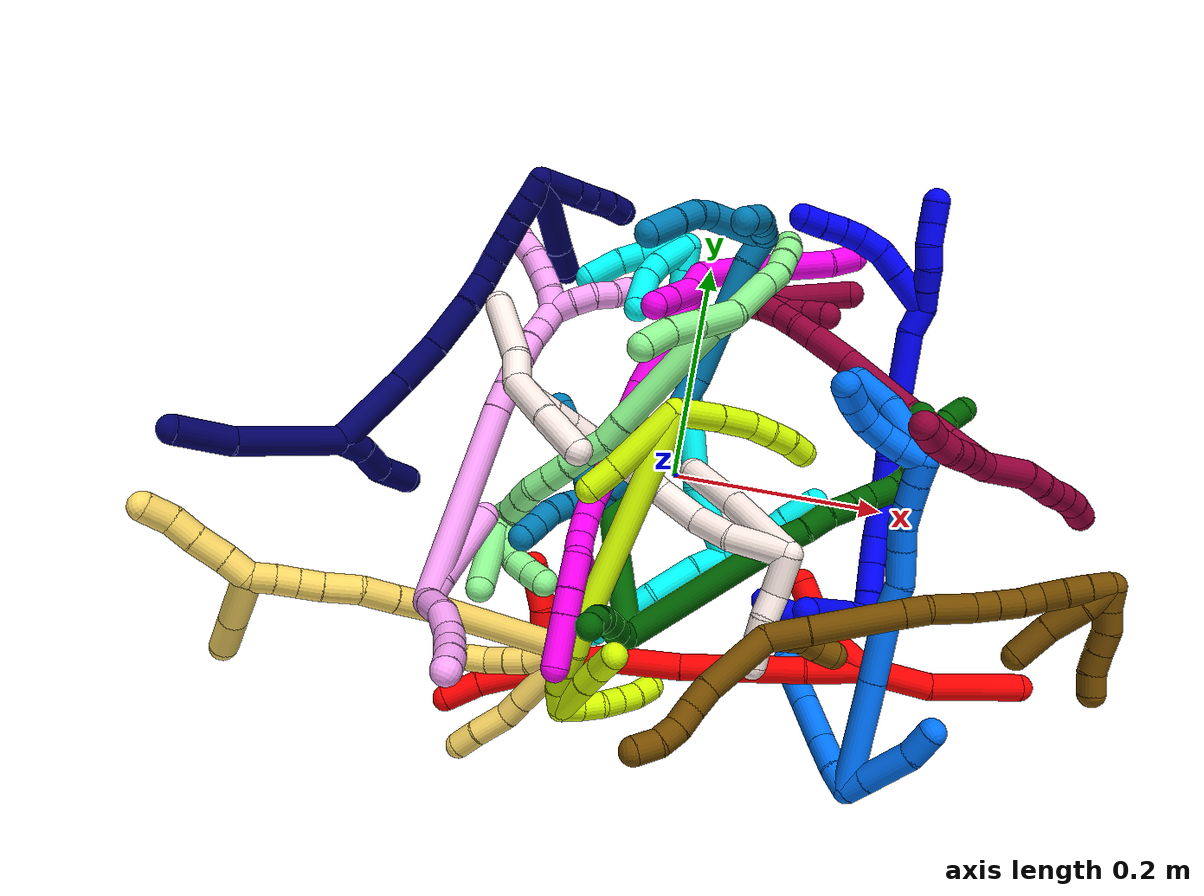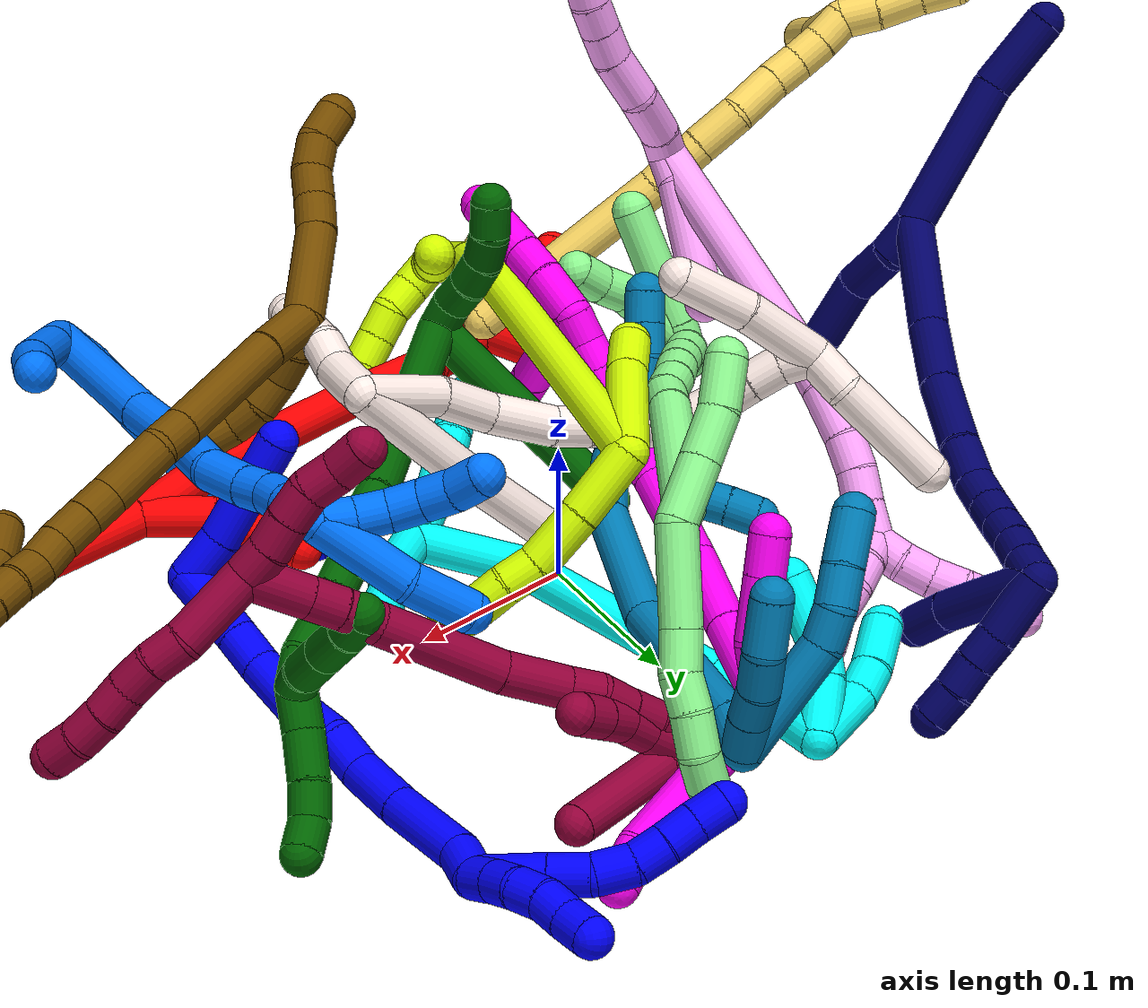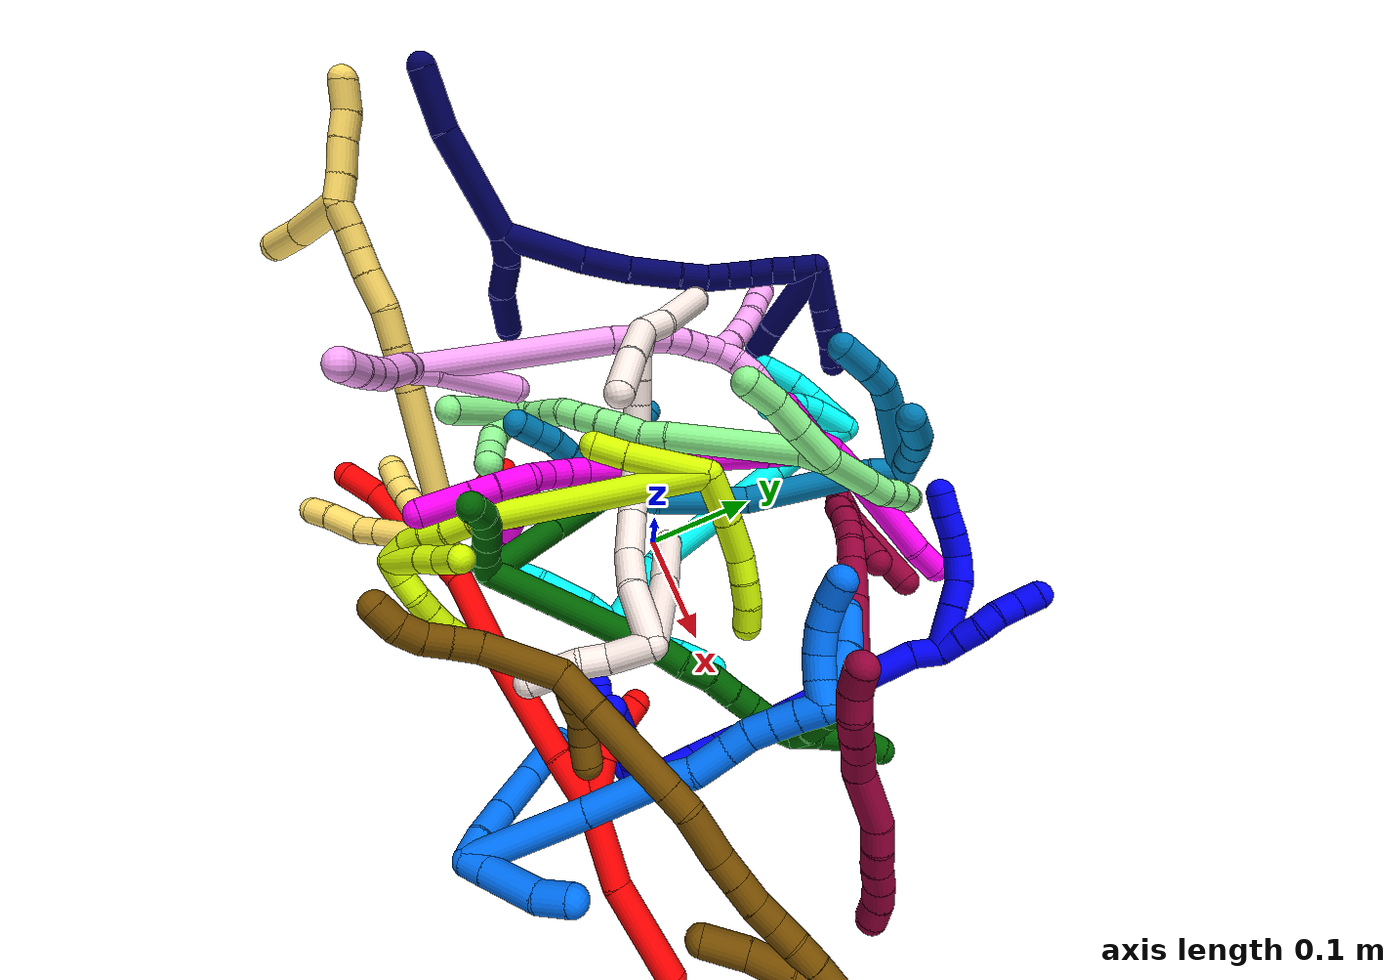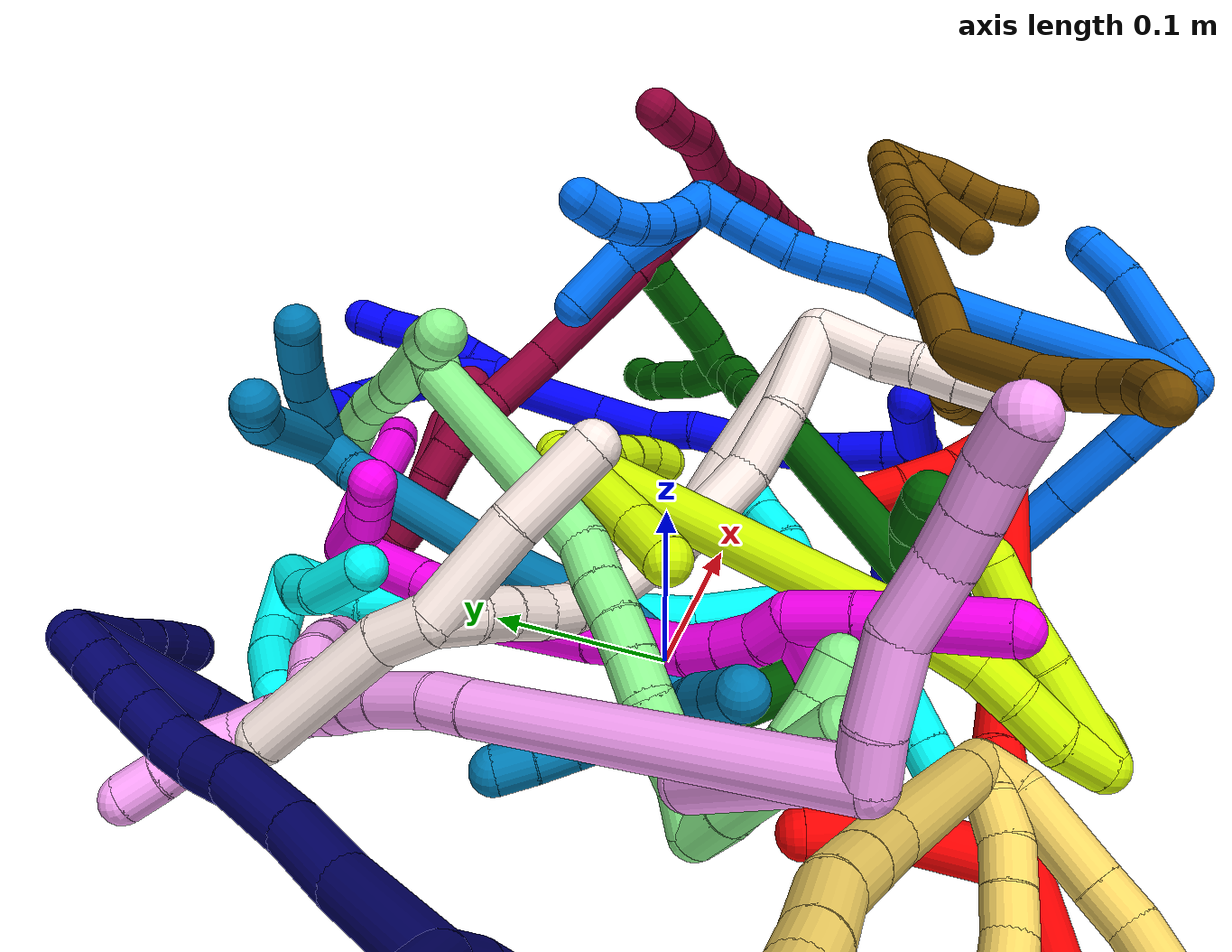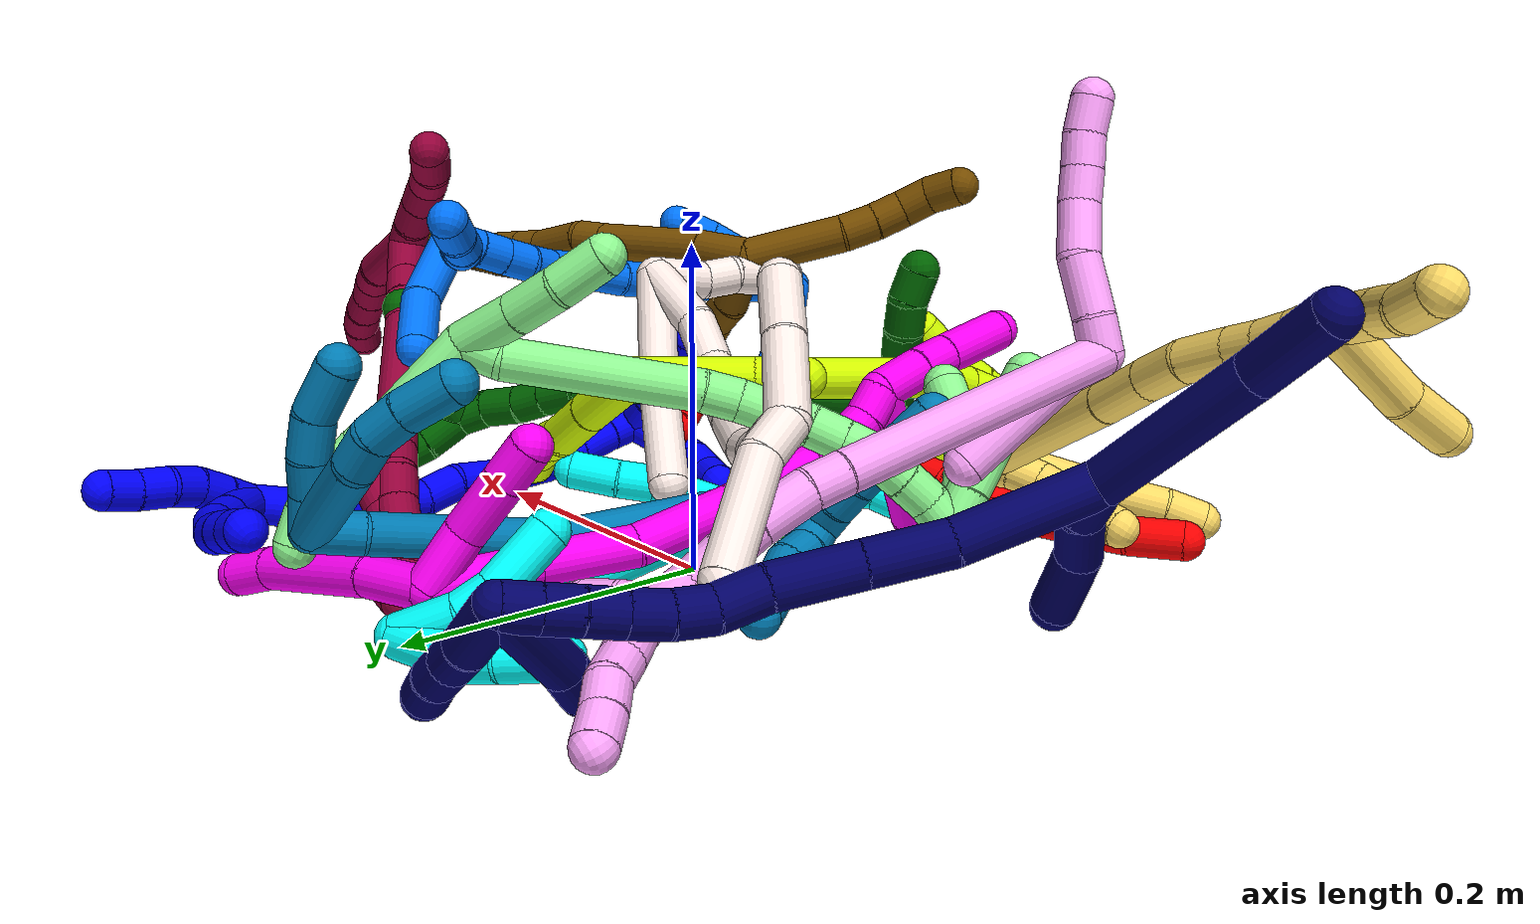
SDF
<sdf version="1.7">
 <world name="default">
  <plugin name="TubeGeneratorPlugin" filename="libtube_generator_plugin.so"/>
  <model name="photoneo_s_sensor">
   <static>1</static>
   <pose>0 0 2 1.57079 1.57079 3.14159</pose>
   <link name="link">
    <inertial><mass>0.1</mass></inertial>
    <sensor name="sensor" type="depth">
     <update_rate>30</update_rate>
     <camera>
      <horizontal_fov>1.22</horizontal_fov>
      <image><width>1920</width><height>1200</height><format>B8G8R8</format></image>
      <clip><near>0.1</near><far>4</far></clip>
      <depth_camera><output>points</output></depth_camera>
     </camera>
     <plugin name="camera_plugin" filename="libgazebo_ros_depth_camera.so">
      <baseline>0.2</baseline>
      <alwaysOn>1</alwaysOn>
      <updateRate>0.0</updateRate>
      <cameraName>camera_ir</cameraName>
      <imageTopicName>/camera/color/image_raw</imageTopicName>
      <cameraInfoTopicName>/camera/color/camera_info</cameraInfoTopicName>
      <depthImageTopicName>/camera/depth/image_raw</depthImageTopicName>
      <depthImageCameraInfoTopicName>/camera/depth/camera_info</depthImageCameraInfoTopicName>
      <pointCloudTopicName>/camera/depth/points</pointCloudTopicName>
      <frameName>fr_optical</frameName>
      <pointCloudCutoff>0.1</pointCloudCutoff>
      <pointCloudCutoffMax>2.0</pointCloudCutoffMax>
      <distortionK1>0</distortionK1>
      <distortionK2>0</distortionK2>
      <distortionK3>0</distortionK3>
      <distortionT1>0</distortionT1>
      <distortionT2>0</distortionT2>
      <CxPrime>0</CxPrime>
      <Cx>0</Cx>
      <Cy>0</Cy>
      <focalLength>0</focalLength>
      <hackBaseline>0</hackBaseline>
     </plugin>
    </sensor>
   </link>
  </model>
  <gravity>0 0 -9.8</gravity>
  <magnetic_field>6e-06 2.3e-05 -4.2e-05</magnetic_field>
  <atmosphere type="adiabatic"/>
  <physics name="default_physics" default="0" type="ode">
   <max_step_size>0.003</max_step_size>
   <real_time_factor>1</real_time_factor>
   <real_time_update_rate>1000</real_time_update_rate>
   <max_contacts>10000</max_contacts>
   <ode>
    <solver>
     <type>quick</type>
     <iters>100</iters>
     <sor>1.3</sor>
     <use_dynamic_moi_rescaling>0</use_dynamic_moi_rescaling>
    </solver>
    <constraints>
     <contact_max_correcting_vel>0</contact_max_correcting_vel>
     <contact_surface_layer>0.001</contact_surface_layer>
     <cfm>0</cfm>
     <erp>0.2</erp>
    </constraints>
   </ode>
  </physics>
  <scene><ambient>0.4 0.4 0.4 1</ambient><background>0.7 0.7 0.7 1</background><shadows>0</shadows></scene>
  <audio><device>default</device></audio>
  <spherical_coordinates>
   <surface_model>EARTH_WGS84</surface_model>
   <latitude_deg>0</latitude_deg>
   <longitude_deg>0</longitude_deg>
   <elevation>0</elevation>
   <heading_deg>0</heading_deg>
  </spherical_coordinates>
  <model name="bin">
   <static>1</static>
   <link name="bottom">
    <collision name="collision-bottom">
     <pose>0 0 -0.01 0 -0 0</pose>
     <geometry><box><size>0.8 0.6 0.02</size></box></geometry>
     <surface>
      <friction><ode><mu>100</mu><mu2>100</mu2></ode></friction>
      <contact><collide_bitmask>65535</collide_bitmask></contact>
     </surface>
    </collision>
   </link>
   <link name="west_wall">
    <collision name="collision-west_wall">
     <pose>-0.41 0 0.1 0 -0 0</pose>
     <geometry><box><size>0.02 0.6 0.2</size></box></geometry>
     <surface>
      <friction><ode><mu>100</mu><mu2>100</mu2></ode></friction>
      <contact><collide_bitmask>65535</collide_bitmask></contact>
     </surface>
    </collision>
   </link>
   <link name="east_wall">
    <collision name="collision-east_wall">
     <pose>0.41 0 0.1 0 -0 0</pose>
     <geometry><box><size>0.02 0.6 0.2</size></box></geometry>
     <surface>
      <friction><ode><mu>100</mu><mu2>100</mu2></ode></friction>
      <contact><collide_bitmask>65535</collide_bitmask></contact>
     </surface>
    </collision>
   </link>
   <link name="south_wall">
    <collision name="collision-south_wall">
     <pose>0 -0.31 0.1 0 -0 0</pose>
     <geometry><box><size>0.8 0.02 0.2</size></box></geometry>
     <surface>
      <friction><ode><mu>100</mu><mu2>100</mu2></ode></friction>
      <contact><collide_bitmask>65535</collide_bitmask></contact>
     </surface>
    </collision>
   </link>
   <link name="north_wall">
    <collision name="collision-north_wall">
     <pose>0 0.31 0.1 0 -0 0</pose>
     <geometry><box><size>0.8 0.02 0.2</size></box></geometry>
     <surface>
      <friction><ode><mu>100</mu><mu2>100</mu2></ode></friction>
      <contact><collide_bitmask>65535</collide_bitmask></contact>
     </surface>
    </collision>
   </link>
  </model>
  <model name="1">
   <static>0</static>
   <link name="1">
    <collision name="collision-cylinder-e_1_2_8">
     <pose>0.008813 0.013366 0.013332 -0.786685 0.436766 -0.183663</pose>
     <geometry><cylinder><radius>0.0125</radius><length>0.041668</length></cylinder></geometry>
     <surface>
      <friction><ode><mu>1.16</mu><mu2>1.16</mu2><slip1>0</slip1><slip2>0</slip2></ode></friction>
      <contact><ode><kp>1e+06</kp><kd>1</kd><max_vel>0</max_vel><min_depth>0.001</min_depth></ode></contact>
     </surface>
    </collision>
    <visual name="visual-cylinder-e_1_2_8">
     <pose>0.008813 0.013366 0.013332 -0.786685 0.436766 -0.183663</pose>
     <geometry><cylinder><radius>0.0125</radius><length>0.041668</length></cylinder></geometry>
     <material><ambient>0 0 1 1</ambient></material>
    </visual>
    <collision name="collision-cylinder-e_2_8_9">
     <pose>0.022307 0.034572 0.034587 -0.780093 0.39757 -0.165255</pose>
     <geometry><cylinder><radius>0.0125</radius><length>0.024177</length></cylinder></geometry>
     <surface>
      <friction><ode><mu>1.16</mu><mu2>1.16</mu2><slip1>0</slip1><slip2>0</slip2></ode></friction>
      <contact><ode><kp>1e+06</kp><kd>1</kd><max_vel>0</max_vel><min_depth>0.001</min_depth></ode></contact>
     </surface>
    </collision>
    <visual name="visual-cylinder-e_2_8_9">
     <pose>0.022307 0.034572 0.034587 -0.780093 0.39757 -0.165255</pose>
     <geometry><cylinder><radius>0.0125</radius><length>0.024177</length></cylinder></geometry>
     <material><ambient>0 0 1 1</ambient></material>
    </visual>
    <collision name="collision-cylinder-e_3_9_10">
     <pose>0.032173 0.046752 0.052379 -0.414389 0.448274 -0.095769</pose>
     <geometry><cylinder><radius>0.0125</radius><length>0.023929</length></cylinder></geometry>
     <surface>
      <friction><ode><mu>1.16</mu><mu2>1.16</mu2><slip1>0</slip1><slip2>0</slip2></ode></friction>
      <contact><ode><kp>1e+06</kp><kd>1</kd><max_vel>0</max_vel><min_depth>0.001</min_depth></ode></contact>
     </surface>
    </collision>
    <visual name="visual-cylinder-e_3_9_10">
     <pose>0.032173 0.046752 0.052379 -0.414389 0.448274 -0.095769</pose>
     <geometry><cylinder><radius>0.0125</radius><length>0.023929</length></cylinder></geometry>
     <material><ambient>0 0 1 1</ambient></material>
    </visual>
    <collision name="collision-cylinder-e_4_10_11">
     <pose>0.043878 0.052386 0.069803 -0.169391 0.704967 -0.062439</pose>
     <geometry><cylinder><radius>0.0125</radius><length>0.020124</length></cylinder></geometry>
     <surface>
      <friction><ode><mu>1.16</mu><mu2>1.16</mu2><slip1>0</slip1><slip2>0</slip2></ode></friction>
      <contact><ode><kp>1e+06</kp><kd>1</kd><max_vel>0</max_vel><min_depth>0.001</min_depth></ode></contact>
     </surface>
    </collision>
    <visual name="visual-cylinder-e_4_10_11">
     <pose>0.043878 0.052386 0.069803 -0.169391 0.704967 -0.062439</pose>
     <geometry><cylinder><radius>0.0125</radius><length>0.020124</length></cylinder></geometry>
     <material><ambient>0 0 1 1</ambient></material>
    </visual>
    <collision name="collision-cylinder-e_5_11_12">
     <pose>0.056731 0.054003 0.085137 -0.041805 0.682743 -0.014855</pose>
     <geometry><cylinder><radius>0.0125</radius><length>0.020074</length></cylinder></geometry>
     <surface>
      <friction><ode><mu>1.16</mu><mu2>1.16</mu2><slip1>0</slip1><slip2>0</slip2></ode></friction>
      <contact><ode><kp>1e+06</kp><kd>1</kd><max_vel>0</max_vel><min_depth>0.001</min_depth></ode></contact>
     </surface>
    </collision>
    <visual name="visual-cylinder-e_5_11_12">
     <pose>0.056731 0.054003 0.085137 -0.041805 0.682743 -0.014855</pose>
     <geometry><cylinder><radius>0.0125</radius><length>0.020074</length></cylinder></geometry>
     <material><ambient>0 0 1 1</ambient></material>
    </visual>
    <collision name="collision-cylinder-e_6_12_6">
     <pose>0.069346 0.05532 0.100652 -0.127552 0.678124 -0.045039</pose>
     <geometry><cylinder><radius>0.0125</radius><length>0.020027</length></cylinder></geometry>
     <surface>
      <friction><ode><mu>1.16</mu><mu2>1.16</mu2><slip1>0</slip1><slip2>0</slip2></ode></friction>
      <contact><ode><kp>1e+06</kp><kd>1</kd><max_vel>0</max_vel><min_depth>0.001</min_depth></ode></contact>
     </surface>
    </collision>
    <visual name="visual-cylinder-e_6_12_6">
     <pose>0.069346 0.05532 0.100652 -0.127552 0.678124 -0.045039</pose>
     <geometry><cylinder><radius>0.0125</radius><length>0.020027</length></cylinder></geometry>
     <material><ambient>0 0 1 1</ambient></material>
    </visual>
    <collision name="collision-cylinder-e_1_2_13">
     <pose>0.005276 0.008483 -0.000459 -1.62487 0.555733 -0.584935</pose>
     <geometry><cylinder><radius>0.0125</radius><length>0.02</length></cylinder></geometry>
     <surface>
      <friction><ode><mu>1.16</mu><mu2>1.16</mu2><slip1>0</slip1><slip2>0</slip2></ode></friction>
      <contact><ode><kp>1e+06</kp><kd>1</kd><max_vel>0</max_vel><min_depth>0.001</min_depth></ode></contact>
     </surface>
    </collision>
    <visual name="visual-cylinder-e_1_2_13">
     <pose>0.005276 0.008483 -0.000459 -1.62487 0.555733 -0.584935</pose>
     <geometry><cylinder><radius>0.0125</radius><length>0.02</length></cylinder></geometry>
     <material><ambient>0 0 1 1</ambient></material>
    </visual>
    <collision name="collision-cylinder-e_2_13_14">
     <pose>0.015286 0.025736 -0.001738 -1.664 0.493184 -0.539226</pose>
     <geometry><cylinder><radius>0.0125</radius><length>0.02</length></cylinder></geometry>
     <surface>
      <friction><ode><mu>1.16</mu><mu2>1.16</mu2><slip1>0</slip1><slip2>0</slip2></ode></friction>
      <contact><ode><kp>1e+06</kp><kd>1</kd><max_vel>0</max_vel><min_depth>0.001</min_depth></ode></contact>
     </surface>
    </collision>
    <visual name="visual-cylinder-e_2_13_14">
     <pose>0.015286 0.025736 -0.001738 -1.664 0.493184 -0.539226</pose>
     <geometry><cylinder><radius>0.0125</radius><length>0.02</length></cylinder></geometry>
     <material><ambient>0 0 1 1</ambient></material>
    </visual>
    <collision name="collision-cylinder-e_3_14_15">
     <pose>0.023236 0.043886 -0.001265 -1.43383 0.327444 -0.286019</pose>
     <geometry><cylinder><radius>0.0125</radius><length>0.02</length></cylinder></geometry>
     <surface>
      <friction><ode><mu>1.16</mu><mu2>1.16</mu2><slip1>0</slip1><slip2>0</slip2></ode></friction>
      <contact><ode><kp>1e+06</kp><kd>1</kd><max_vel>0</max_vel><min_depth>0.001</min_depth></ode></contact>
     </surface>
    </collision>
    <visual name="visual-cylinder-e_3_14_15">
     <pose>0.023236 0.043886 -0.001265 -1.43383 0.327444 -0.286019</pose>
     <geometry><cylinder><radius>0.0125</radius><length>0.02</length></cylinder></geometry>
     <material><ambient>0 0 1 1</ambient></material>
    </visual>
    <collision name="collision-cylinder-e_4_15_16">
     <pose>0.027626 0.063196 -3.5e-05 -1.57717 0.117575 -0.118326</pose>
     <geometry><cylinder><radius>0.0125</radius><length>0.02</length></cylinder></geometry>
     <surface>
      <friction><ode><mu>1.16</mu><mu2>1.16</mu2><slip1>0</slip1><slip2>0</slip2></ode></friction>
      <contact><ode><kp>1e+06</kp><kd>1</kd><max_vel>0</max_vel><min_depth>0.001</min_depth></ode></contact>
     </surface>
    </collision>
    <visual name="visual-cylinder-e_4_15_16">
     <pose>0.027626 0.063196 -3.5e-05 -1.57717 0.117575 -0.118326</pose>
     <geometry><cylinder><radius>0.0125</radius><length>0.02</length></cylinder></geometry>
     <material><ambient>0 0 1 1</ambient></material>
    </visual>
    <collision name="collision-cylinder-e_5_16_5">
     <pose>0.030844 0.082906 -0.000533 -1.61518 0.206019 -0.215302</pose>
     <geometry><cylinder><radius>0.0125</radius><length>0.02</length></cylinder></geometry>
     <surface>
      <friction><ode><mu>1.16</mu><mu2>1.16</mu2><slip1>0</slip1><slip2>0</slip2></ode></friction>
      <contact><ode><kp>1e+06</kp><kd>1</kd><max_vel>0</max_vel><min_depth>0.001</min_depth></ode></contact>
     </surface>
    </collision>
    <visual name="visual-cylinder-e_5_16_5">
     <pose>0.030844 0.082906 -0.000533 -1.61518 0.206019 -0.215302</pose>
     <geometry><cylinder><radius>0.0125</radius><length>0.02</length></cylinder></geometry>
     <material><ambient>0 0 1 1</ambient></material>
    </visual>
    <collision name="collision-cylinder-e_1_2_17">
     <pose>-0.001307 -0.011698 0.004243 1.22283 -0.104684 -0.073421</pose>
     <geometry><cylinder><radius>0.0125</radius><length>0.025025</length></cylinder></geometry>
     <surface>
      <friction><ode><mu>1.16</mu><mu2>1.16</mu2><slip1>0</slip1><slip2>0</slip2></ode></friction>
      <contact><ode><kp>1e+06</kp><kd>1</kd><max_vel>0</max_vel><min_depth>0.001</min_depth></ode></contact>
     </surface>
    </collision>
    <visual name="visual-cylinder-e_1_2_17">
     <pose>-0.001307 -0.011698 0.004243 1.22283 -0.104684 -0.073421</pose>
     <geometry><cylinder><radius>0.0125</radius><length>0.025025</length></cylinder></geometry>
     <material><ambient>0 0 1 1</ambient></material>
    </visual>
    <collision name="collision-cylinder-e_2_17_18">
     <pose>-0.00768 -0.051272 0.009159 1.54667 -0.179705 -0.175442</pose>
     <geometry><cylinder><radius>0.0125</radius><length>0.05668</length></cylinder></geometry>
     <surface>
      <friction><ode><mu>1.16</mu><mu2>1.16</mu2><slip1>0</slip1><slip2>0</slip2></ode></friction>
      <contact><ode><kp>1e+06</kp><kd>1</kd><max_vel>0</max_vel><min_depth>0.001</min_depth></ode></contact>
     </surface>
    </collision>
    <visual name="visual-cylinder-e_2_17_18">
     <pose>-0.00768 -0.051272 0.009159 1.54667 -0.179705 -0.175442</pose>
     <geometry><cylinder><radius>0.0125</radius><length>0.05668</length></cylinder></geometry>
     <material><ambient>0 0 1 1</ambient></material>
    </visual>
    <collision name="collision-cylinder-e_3_18_19">
     <pose>-0.015184 -0.099089 0.010736 1.52549 -0.121535 -0.116162</pose>
     <geometry><cylinder><radius>0.0125</radius><length>0.040221</length></cylinder></geometry>
     <surface>
      <friction><ode><mu>1.16</mu><mu2>1.16</mu2><slip1>0</slip1><slip2>0</slip2></ode></friction>
      <contact><ode><kp>1e+06</kp><kd>1</kd><max_vel>0</max_vel><min_depth>0.001</min_depth></ode></contact>
     </surface>
    </collision>
    <visual name="visual-cylinder-e_3_18_19">
     <pose>-0.015184 -0.099089 0.010736 1.52549 -0.121535 -0.116162</pose>
     <geometry><cylinder><radius>0.0125</radius><length>0.040221</length></cylinder></geometry>
     <material><ambient>0 0 1 1</ambient></material>
    </visual>
    <collision name="collision-cylinder-e_4_19_20">
     <pose>-0.015221 -0.131831 0.010066 1.69315 0.184038 0.207891</pose>
     <geometry><cylinder><radius>0.0125</radius><length>0.026236</length></cylinder></geometry>
     <surface>
      <friction><ode><mu>1.16</mu><mu2>1.16</mu2><slip1>0</slip1><slip2>0</slip2></ode></friction>
      <contact><ode><kp>1e+06</kp><kd>1</kd><max_vel>0</max_vel><min_depth>0.001</min_depth></ode></contact>
     </surface>
    </collision>
    <visual name="visual-cylinder-e_4_19_20">
     <pose>-0.015221 -0.131831 0.010066 1.69315 0.184038 0.207891</pose>
     <geometry><cylinder><radius>0.0125</radius><length>0.026236</length></cylinder></geometry>
     <material><ambient>0 0 1 1</ambient></material>
    </visual>
    <collision name="collision-cylinder-e_5_20_21">
     <pose>-0.014981 -0.159246 0.008151 1.59415 -0.146715 -0.150168</pose>
     <geometry><cylinder><radius>0.0125</radius><length>0.029556</length></cylinder></geometry>
     <surface>
      <friction><ode><mu>1.16</mu><mu2>1.16</mu2><slip1>0</slip1><slip2>0</slip2></ode></friction>
      <contact><ode><kp>1e+06</kp><kd>1</kd><max_vel>0</max_vel><min_depth>0.001</min_depth></ode></contact>
     </surface>
    </collision>
    <visual name="visual-cylinder-e_5_20_21">
     <pose>-0.014981 -0.159246 0.008151 1.59415 -0.146715 -0.150168</pose>
     <geometry><cylinder><radius>0.0125</radius><length>0.029556</length></cylinder></geometry>
     <material><ambient>0 0 1 1</ambient></material>
    </visual>
    <collision name="collision-cylinder-e_6_21_22">
     <pose>-0.016437 -0.196697 0.007561 1.5817 0.030838 0.031176</pose>
     <geometry><cylinder><radius>0.0125</radius><length>0.045697</length></cylinder></geometry>
     <surface>
      <friction><ode><mu>1.16</mu><mu2>1.16</mu2><slip1>0</slip1><slip2>0</slip2></ode></friction>
      <contact><ode><kp>1e+06</kp><kd>1</kd><max_vel>0</max_vel><min_depth>0.001</min_depth></ode></contact>
     </surface>
    </collision>
    <visual name="visual-cylinder-e_6_21_22">
     <pose>-0.016437 -0.196697 0.007561 1.5817 0.030838 0.031176</pose>
     <geometry><cylinder><radius>0.0125</radius><length>0.045697</length></cylinder></geometry>
     <material><ambient>0 0 1 1</ambient></material>
    </visual>
    <collision name="collision-cylinder-e_7_22_23">
     <pose>-0.013484 -0.23212 0.00614 1.66365 0.176032 0.193085</pose>
     <geometry><cylinder><radius>0.0125</radius><length>0.025679</length></cylinder></geometry>
     <surface>
      <friction><ode><mu>1.16</mu><mu2>1.16</mu2><slip1>0</slip1><slip2>0</slip2></ode></friction>
      <contact><ode><kp>1e+06</kp><kd>1</kd><max_vel>0</max_vel><min_depth>0.001</min_depth></ode></contact>
     </surface>
    </collision>
    <visual name="visual-cylinder-e_7_22_23">
     <pose>-0.013484 -0.23212 0.00614 1.66365 0.176032 0.193085</pose>
     <geometry><cylinder><radius>0.0125</radius><length>0.025679</length></cylinder></geometry>
     <material><ambient>0 0 1 1</ambient></material>
    </visual>
    <collision name="collision-cylinder-e_8_23_24">
     <pose>-0.008436 -0.257924 0.003307 1.69577 0.207111 0.234521</pose>
     <geometry><cylinder><radius>0.0125</radius><length>0.027225</length></cylinder></geometry>
     <surface>
      <friction><ode><mu>1.16</mu><mu2>1.16</mu2><slip1>0</slip1><slip2>0</slip2></ode></friction>
      <contact><ode><kp>1e+06</kp><kd>1</kd><max_vel>0</max_vel><min_depth>0.001</min_depth></ode></contact>
     </surface>
    </collision>
    <visual name="visual-cylinder-e_8_23_24">
     <pose>-0.008436 -0.257924 0.003307 1.69577 0.207111 0.234521</pose>
     <geometry><cylinder><radius>0.0125</radius><length>0.027225</length></cylinder></geometry>
     <material><ambient>0 0 1 1</ambient></material>
    </visual>
    <collision name="collision-cylinder-e_9_24_1">
     <pose>-0.004004 -0.282807 0.000433 1.67449 0.138384 0.153476</pose>
     <geometry><cylinder><radius>0.0125</radius><length>0.023682</length></cylinder></geometry>
     <surface>
      <friction><ode><mu>1.16</mu><mu2>1.16</mu2><slip1>0</slip1><slip2>0</slip2></ode></friction>
      <contact><ode><kp>1e+06</kp><kd>1</kd><max_vel>0</max_vel><min_depth>0.001</min_depth></ode></contact>
     </surface>
    </collision>
    <visual name="visual-cylinder-e_9_24_1">
     <pose>-0.004004 -0.282807 0.000433 1.67449 0.138384 0.153476</pose>
     <geometry><cylinder><radius>0.0125</radius><length>0.023682</length></cylinder></geometry>
     <material><ambient>0 0 1 1</ambient></material>
    </visual>
    <collision name="collision-cylinder-e_1_1_25">
     <pose>-0.001503 -0.299194 0.015738 0.278475 0.050427 0.007069</pose>
     <geometry><cylinder><radius>0.0125</radius><length>0.034406</length></cylinder></geometry>
     <surface>
      <friction><ode><mu>1.16</mu><mu2>1.16</mu2><slip1>0</slip1><slip2>0</slip2></ode></friction>
      <contact><ode><kp>1e+06</kp><kd>1</kd><max_vel>0</max_vel><min_depth>0.001</min_depth></ode></contact>
     </surface>
    </collision>
    <visual name="visual-cylinder-e_1_1_25">
     <pose>-0.001503 -0.299194 0.015738 0.278475 0.050427 0.007069</pose>
     <geometry><cylinder><radius>0.0125</radius><length>0.034406</length></cylinder></geometry>
     <material><ambient>0 0 1 1</ambient></material>
    </visual>
    <collision name="collision-cylinder-e_2_25_26">
     <pose>0.001529 -0.30499 0.04476 0.085606 0.170859 0.007336</pose>
     <geometry><cylinder><radius>0.0125</radius><length>0.025469</length></cylinder></geometry>
     <surface>
      <friction><ode><mu>1.16</mu><mu2>1.16</mu2><slip1>0</slip1><slip2>0</slip2></ode></friction>
      <contact><ode><kp>1e+06</kp><kd>1</kd><max_vel>0</max_vel><min_depth>0.001</min_depth></ode></contact>
     </surface>
    </collision>
    <visual name="visual-cylinder-e_2_25_26">
     <pose>0.001529 -0.30499 0.04476 0.085606 0.170859 0.007336</pose>
     <geometry><cylinder><radius>0.0125</radius><length>0.025469</length></cylinder></geometry>
     <material><ambient>0 0 1 1</ambient></material>
    </visual>
    <collision name="collision-cylinder-e_3_26_27">
     <pose>0.004559 -0.304977 0.067204 -0.108819 0.086226 -0.004699</pose>
     <geometry><cylinder><radius>0.0125</radius><length>0.020074</length></cylinder></geometry>
     <surface>
      <friction><ode><mu>1.16</mu><mu2>1.16</mu2><slip1>0</slip1><slip2>0</slip2></ode></friction>
      <contact><ode><kp>1e+06</kp><kd>1</kd><max_vel>0</max_vel><min_depth>0.001</min_depth></ode></contact>
     </surface>
    </collision>
    <visual name="visual-cylinder-e_3_26_27">
     <pose>0.004559 -0.304977 0.067204 -0.108819 0.086226 -0.004699</pose>
     <geometry><cylinder><radius>0.0125</radius><length>0.020074</length></cylinder></geometry>
     <material><ambient>0 0 1 1</ambient></material>
    </visual>
    <collision name="collision-cylinder-e_4_27_4">
     <pose>0.008656 -0.300822 0.086125 -0.329304 0.328302 -0.055031</pose>
     <geometry><cylinder><radius>0.0125</radius><length>0.020051</length></cylinder></geometry>
     <surface>
      <friction><ode><mu>1.16</mu><mu2>1.16</mu2><slip1>0</slip1><slip2>0</slip2></ode></friction>
      <contact><ode><kp>1e+06</kp><kd>1</kd><max_vel>0</max_vel><min_depth>0.001</min_depth></ode></contact>
     </surface>
    </collision>
    <visual name="visual-cylinder-e_4_27_4">
     <pose>0.008656 -0.300822 0.086125 -0.329304 0.328302 -0.055031</pose>
     <geometry><cylinder><radius>0.0125</radius><length>0.020051</length></cylinder></geometry>
     <material><ambient>0 0 1 1</ambient></material>
    </visual>
    <collision name="collision-cylinder-e_1_1_28">
     <pose>0.011331 -0.293869 0.00577 -0.09173 1.12313 -0.057734</pose>
     <geometry><cylinder><radius>0.0125</radius><length>0.030398</length></cylinder></geometry>
     <surface>
      <friction><ode><mu>1.16</mu><mu2>1.16</mu2><slip1>0</slip1><slip2>0</slip2></ode></friction>
      <contact><ode><kp>1e+06</kp><kd>1</kd><max_vel>0</max_vel><min_depth>0.001</min_depth></ode></contact>
     </surface>
    </collision>
    <visual name="visual-cylinder-e_1_1_28">
     <pose>0.011331 -0.293869 0.00577 -0.09173 1.12313 -0.057734</pose>
     <geometry><cylinder><radius>0.0125</radius><length>0.030398</length></cylinder></geometry>
     <material><ambient>0 0 1 1</ambient></material>
    </visual>
    <collision name="collision-cylinder-e_2_28_3">
     <pose>0.058369 -0.293807 0.022294 0.054168 1.27972 0.040323</pose>
     <geometry><cylinder><radius>0.0125</radius><length>0.069602</length></cylinder></geometry>
     <surface>
      <friction><ode><mu>1.16</mu><mu2>1.16</mu2><slip1>0</slip1><slip2>0</slip2></ode></friction>
      <contact><ode><kp>1e+06</kp><kd>1</kd><max_vel>0</max_vel><min_depth>0.001</min_depth></ode></contact>
     </surface>
    </collision>
    <visual name="visual-cylinder-e_2_28_3">
     <pose>0.058369 -0.293807 0.022294 0.054168 1.27972 0.040323</pose>
     <geometry><cylinder><radius>0.0125</radius><length>0.069602</length></cylinder></geometry>
     <material><ambient>0 0 1 1</ambient></material>
    </visual>
    <collision name="collision-sphere-3">
     <pose>0.091706 -0.294347 0.032267 0 -0 0</pose>
     <geometry><sphere><radius>0.0125</radius></sphere></geometry>
     <surface>
      <friction><ode><mu>1.16</mu><mu2>1.16</mu2><slip1>0</slip1><slip2>0</slip2></ode></friction>
      <contact><ode><kp>1e+06</kp><kd>1</kd><max_vel>0</max_vel><min_depth>0.001</min_depth></ode></contact>
     </surface>
    </collision>
    <visual name="visual-sphere-3">
     <pose>0.091706 -0.294347 0.032267 0 -0 0</pose>
     <geometry><sphere><radius>0.0125</radius></sphere></geometry>
     <material><ambient>0 0 1 1</ambient></material>
    </visual>
    <collision name="collision-sphere-28">
     <pose>0.025032 -0.293266 0.012322 0 -0 0</pose>
     <geometry><sphere><radius>0.0125</radius></sphere></geometry>
     <surface>
      <friction><ode><mu>1.16</mu><mu2>1.16</mu2><slip1>0</slip1><slip2>0</slip2></ode></friction>
      <contact><ode><kp>1e+06</kp><kd>1</kd><max_vel>0</max_vel><min_depth>0.001</min_depth></ode></contact>
     </surface>
    </collision>
    <visual name="visual-sphere-28">
     <pose>0.025032 -0.293266 0.012322 0 -0 0</pose>
     <geometry><sphere><radius>0.0125</radius></sphere></geometry>
     <material><ambient>0 0 1 1</ambient></material>
    </visual>
    <collision name="collision-sphere-4">
     <pose>0.011888 -0.297753 0.095105 0 -0 0</pose>
     <geometry><sphere><radius>0.0125</radius></sphere></geometry>
     <surface>
      <friction><ode><mu>1.16</mu><mu2>1.16</mu2><slip1>0</slip1><slip2>0</slip2></ode></friction>
      <contact><ode><kp>1e+06</kp><kd>1</kd><max_vel>0</max_vel><min_depth>0.001</min_depth></ode></contact>
     </surface>
    </collision>
    <visual name="visual-sphere-4">
     <pose>0.011888 -0.297753 0.095105 0 -0 0</pose>
     <geometry><sphere><radius>0.0125</radius></sphere></geometry>
     <material><ambient>0 0 1 1</ambient></material>
    </visual>
    <collision name="collision-sphere-27">
     <pose>0.005423 -0.303891 0.077145 0 -0 0</pose>
     <geometry><sphere><radius>0.0125</radius></sphere></geometry>
     <surface>
      <friction><ode><mu>1.16</mu><mu2>1.16</mu2><slip1>0</slip1><slip2>0</slip2></ode></friction>
      <contact><ode><kp>1e+06</kp><kd>1</kd><max_vel>0</max_vel><min_depth>0.001</min_depth></ode></contact>
     </surface>
    </collision>
    <visual name="visual-sphere-27">
     <pose>0.005423 -0.303891 0.077145 0 -0 0</pose>
     <geometry><sphere><radius>0.0125</radius></sphere></geometry>
     <material><ambient>0 0 1 1</ambient></material>
    </visual>
    <collision name="collision-sphere-26">
     <pose>0.003694 -0.306063 0.057264 0 -0 0</pose>
     <geometry><sphere><radius>0.0125</radius></sphere></geometry>
     <surface>
      <friction><ode><mu>1.16</mu><mu2>1.16</mu2><slip1>0</slip1><slip2>0</slip2></ode></friction>
      <contact><ode><kp>1e+06</kp><kd>1</kd><max_vel>0</max_vel><min_depth>0.001</min_depth></ode></contact>
     </surface>
    </collision>
    <visual name="visual-sphere-26">
     <pose>0.003694 -0.306063 0.057264 0 -0 0</pose>
     <geometry><sphere><radius>0.0125</radius></sphere></geometry>
     <material><ambient>0 0 1 1</ambient></material>
    </visual>
    <collision name="collision-sphere-25">
     <pose>-0.000636 -0.303917 0.032257 0 -0 0</pose>
     <geometry><sphere><radius>0.0125</radius></sphere></geometry>
     <surface>
      <friction><ode><mu>1.16</mu><mu2>1.16</mu2><slip1>0</slip1><slip2>0</slip2></ode></friction>
      <contact><ode><kp>1e+06</kp><kd>1</kd><max_vel>0</max_vel><min_depth>0.001</min_depth></ode></contact>
     </surface>
    </collision>
    <visual name="visual-sphere-25">
     <pose>-0.000636 -0.303917 0.032257 0 -0 0</pose>
     <geometry><sphere><radius>0.0125</radius></sphere></geometry>
     <material><ambient>0 0 1 1</ambient></material>
    </visual>
    <collision name="collision-sphere-1">
     <pose>-0.00237 -0.294471 -0.000781 0 -0 0</pose>
     <geometry><sphere><radius>0.0125</radius></sphere></geometry>
     <surface>
      <friction><ode><mu>1.16</mu><mu2>1.16</mu2><slip1>0</slip1><slip2>0</slip2></ode></friction>
      <contact><ode><kp>1e+06</kp><kd>1</kd><max_vel>0</max_vel><min_depth>0.001</min_depth></ode></contact>
     </surface>
    </collision>
    <visual name="visual-sphere-1">
     <pose>-0.00237 -0.294471 -0.000781 0 -0 0</pose>
     <geometry><sphere><radius>0.0125</radius></sphere></geometry>
     <material><ambient>0 0 1 1</ambient></material>
    </visual>
    <collision name="collision-sphere-24">
     <pose>-0.005637 -0.271142 0.001646 0 -0 0</pose>
     <geometry><sphere><radius>0.0125</radius></sphere></geometry>
     <surface>
      <friction><ode><mu>1.16</mu><mu2>1.16</mu2><slip1>0</slip1><slip2>0</slip2></ode></friction>
      <contact><ode><kp>1e+06</kp><kd>1</kd><max_vel>0</max_vel><min_depth>0.001</min_depth></ode></contact>
     </surface>
    </collision>
    <visual name="visual-sphere-24">
     <pose>-0.005637 -0.271142 0.001646 0 -0 0</pose>
     <geometry><sphere><radius>0.0125</radius></sphere></geometry>
     <material><ambient>0 0 1 1</ambient></material>
    </visual>
    <collision name="collision-sphere-23">
     <pose>-0.011236 -0.244707 0.004968 0 -0 0</pose>
     <geometry><sphere><radius>0.0125</radius></sphere></geometry>
     <surface>
      <friction><ode><mu>1.16</mu><mu2>1.16</mu2><slip1>0</slip1><slip2>0</slip2></ode></friction>
      <contact><ode><kp>1e+06</kp><kd>1</kd><max_vel>0</max_vel><min_depth>0.001</min_depth></ode></contact>
     </surface>
    </collision>
    <visual name="visual-sphere-23">
     <pose>-0.011236 -0.244707 0.004968 0 -0 0</pose>
     <geometry><sphere><radius>0.0125</radius></sphere></geometry>
     <material><ambient>0 0 1 1</ambient></material>
    </visual>
    <collision name="collision-sphere-22">
     <pose>-0.015733 -0.219533 0.007312 0 -0 0</pose>
     <geometry><sphere><radius>0.0125</radius></sphere></geometry>
     <surface>
      <friction><ode><mu>1.16</mu><mu2>1.16</mu2><slip1>0</slip1><slip2>0</slip2></ode></friction>
      <contact><ode><kp>1e+06</kp><kd>1</kd><max_vel>0</max_vel><min_depth>0.001</min_depth></ode></contact>
     </surface>
    </collision>
    <visual name="visual-sphere-22">
     <pose>-0.015733 -0.219533 0.007312 0 -0 0</pose>
     <geometry><sphere><radius>0.0125</radius></sphere></geometry>
     <material><ambient>0 0 1 1</ambient></material>
    </visual>
    <collision name="collision-sphere-21">
     <pose>-0.017142 -0.173861 0.00781 0 -0 0</pose>
     <geometry><sphere><radius>0.0125</radius></sphere></geometry>
     <surface>
      <friction><ode><mu>1.16</mu><mu2>1.16</mu2><slip1>0</slip1><slip2>0</slip2></ode></friction>
      <contact><ode><kp>1e+06</kp><kd>1</kd><max_vel>0</max_vel><min_depth>0.001</min_depth></ode></contact>
     </surface>
    </collision>
    <visual name="visual-sphere-21">
     <pose>-0.017142 -0.173861 0.00781 0 -0 0</pose>
     <geometry><sphere><radius>0.0125</radius></sphere></geometry>
     <material><ambient>0 0 1 1</ambient></material>
    </visual>
    <collision name="collision-sphere-12">
     <pose>0.063064 0.054328 0.092918 0 -0 0</pose>
     <geometry><sphere><radius>0.0125</radius></sphere></geometry>
     <surface>
      <friction><ode><mu>1.16</mu><mu2>1.16</mu2><slip1>0</slip1><slip2>0</slip2></ode></friction>
      <contact><ode><kp>1e+06</kp><kd>1</kd><max_vel>0</max_vel><min_depth>0.001</min_depth></ode></contact>
     </surface>
    </collision>
    <visual name="visual-sphere-12">
     <pose>0.063064 0.054328 0.092918 0 -0 0</pose>
     <geometry><sphere><radius>0.0125</radius></sphere></geometry>
     <material><ambient>0 0 1 1</ambient></material>
    </visual>
    <collision name="collision-sphere-11">
     <pose>0.050399 0.053677 0.077357 0 -0 0</pose>
     <geometry><sphere><radius>0.0125</radius></sphere></geometry>
     <surface>
      <friction><ode><mu>1.16</mu><mu2>1.16</mu2><slip1>0</slip1><slip2>0</slip2></ode></friction>
      <contact><ode><kp>1e+06</kp><kd>1</kd><max_vel>0</max_vel><min_depth>0.001</min_depth></ode></contact>
     </surface>
    </collision>
    <visual name="visual-sphere-11">
     <pose>0.050399 0.053677 0.077357 0 -0 0</pose>
     <geometry><sphere><radius>0.0125</radius></sphere></geometry>
     <material><ambient>0 0 1 1</ambient></material>
    </visual>
    <collision name="collision-sphere-10">
     <pose>0.037358 0.051094 0.062249 0 -0 0</pose>
     <geometry><sphere><radius>0.0125</radius></sphere></geometry>
     <surface>
      <friction><ode><mu>1.16</mu><mu2>1.16</mu2><slip1>0</slip1><slip2>0</slip2></ode></friction>
      <contact><ode><kp>1e+06</kp><kd>1</kd><max_vel>0</max_vel><min_depth>0.001</min_depth></ode></contact>
     </surface>
    </collision>
    <visual name="visual-sphere-10">
     <pose>0.037358 0.051094 0.062249 0 -0 0</pose>
     <geometry><sphere><radius>0.0125</radius></sphere></geometry>
     <material><ambient>0 0 1 1</ambient></material>
    </visual>
    <collision name="collision-sphere-9">
     <pose>0.026987 0.042411 0.04251 0 -0 0</pose>
     <geometry><sphere><radius>0.0125</radius></sphere></geometry>
     <surface>
      <friction><ode><mu>1.16</mu><mu2>1.16</mu2><slip1>0</slip1><slip2>0</slip2></ode></friction>
      <contact><ode><kp>1e+06</kp><kd>1</kd><max_vel>0</max_vel><min_depth>0.001</min_depth></ode></contact>
     </surface>
    </collision>
    <visual name="visual-sphere-9">
     <pose>0.026987 0.042411 0.04251 0 -0 0</pose>
     <geometry><sphere><radius>0.0125</radius></sphere></geometry>
     <material><ambient>0 0 1 1</ambient></material>
    </visual>
    <collision name="collision-sphere-2">
     <geometry><sphere><radius>0.0125</radius></sphere></geometry>
     <surface>
      <friction><ode><mu>1.16</mu><mu2>1.16</mu2><slip1>0</slip1><slip2>0</slip2></ode></friction>
      <contact><ode><kp>1e+06</kp><kd>1</kd><max_vel>0</max_vel><min_depth>0.001</min_depth></ode></contact>
     </surface>
    </collision>
    <visual name="visual-sphere-2">
     <geometry><sphere><radius>0.0125</radius></sphere></geometry>
     <material><ambient>0 0 1 1</ambient></material>
    </visual>
    <collision name="collision-sphere-19">
     <pose>-0.017622 -0.119031 0.01164 0 -0 0</pose>
     <geometry><sphere><radius>0.0125</radius></sphere></geometry>
     <surface>
      <friction><ode><mu>1.16</mu><mu2>1.16</mu2><slip1>0</slip1><slip2>0</slip2></ode></friction>
      <contact><ode><kp>1e+06</kp><kd>1</kd><max_vel>0</max_vel><min_depth>0.001</min_depth></ode></contact>
     </surface>
    </collision>
    <visual name="visual-sphere-19">
     <pose>-0.017622 -0.119031 0.01164 0 -0 0</pose>
     <geometry><sphere><radius>0.0125</radius></sphere></geometry>
     <material><ambient>0 0 1 1</ambient></material>
    </visual>
    <collision name="collision-sphere-8">
     <pose>0.017626 0.026732 0.026664 0 -0 0</pose>
     <geometry><sphere><radius>0.0125</radius></sphere></geometry>
     <surface>
      <friction><ode><mu>1.16</mu><mu2>1.16</mu2><slip1>0</slip1><slip2>0</slip2></ode></friction>
      <contact><ode><kp>1e+06</kp><kd>1</kd><max_vel>0</max_vel><min_depth>0.001</min_depth></ode></contact>
     </surface>
    </collision>
    <visual name="visual-sphere-8">
     <pose>0.017626 0.026732 0.026664 0 -0 0</pose>
     <geometry><sphere><radius>0.0125</radius></sphere></geometry>
     <material><ambient>0 0 1 1</ambient></material>
    </visual>
    <collision name="collision-sphere-6">
     <pose>0.075628 0.056312 0.108387 0 -0 0</pose>
     <geometry><sphere><radius>0.0125</radius></sphere></geometry>
     <surface>
      <friction><ode><mu>1.16</mu><mu2>1.16</mu2><slip1>0</slip1><slip2>0</slip2></ode></friction>
      <contact><ode><kp>1e+06</kp><kd>1</kd><max_vel>0</max_vel><min_depth>0.001</min_depth></ode></contact>
     </surface>
    </collision>
    <visual name="visual-sphere-6">
     <pose>0.075628 0.056312 0.108387 0 -0 0</pose>
     <geometry><sphere><radius>0.0125</radius></sphere></geometry>
     <material><ambient>0 0 1 1</ambient></material>
    </visual>
    <collision name="collision-sphere-13">
     <pose>0.010551 0.016965 -0.000918 0 -0 0</pose>
     <geometry><sphere><radius>0.0125</radius></sphere></geometry>
     <surface>
      <friction><ode><mu>1.16</mu><mu2>1.16</mu2><slip1>0</slip1><slip2>0</slip2></ode></friction>
      <contact><ode><kp>1e+06</kp><kd>1</kd><max_vel>0</max_vel><min_depth>0.001</min_depth></ode></contact>
     </surface>
    </collision>
    <visual name="visual-sphere-13">
     <pose>0.010551 0.016965 -0.000918 0 -0 0</pose>
     <geometry><sphere><radius>0.0125</radius></sphere></geometry>
     <material><ambient>0 0 1 1</ambient></material>
    </visual>
    <collision name="collision-sphere-14">
     <pose>0.02002 0.034506 -0.002558 0 -0 0</pose>
     <geometry><sphere><radius>0.0125</radius></sphere></geometry>
     <surface>
      <friction><ode><mu>1.16</mu><mu2>1.16</mu2><slip1>0</slip1><slip2>0</slip2></ode></friction>
      <contact><ode><kp>1e+06</kp><kd>1</kd><max_vel>0</max_vel><min_depth>0.001</min_depth></ode></contact>
     </surface>
    </collision>
    <visual name="visual-sphere-14">
     <pose>0.02002 0.034506 -0.002558 0 -0 0</pose>
     <geometry><sphere><radius>0.0125</radius></sphere></geometry>
     <material><ambient>0 0 1 1</ambient></material>
    </visual>
    <collision name="collision-sphere-15">
     <pose>0.026452 0.053266 2.8e-05 0 -0 0</pose>
     <geometry><sphere><radius>0.0125</radius></sphere></geometry>
     <surface>
      <friction><ode><mu>1.16</mu><mu2>1.16</mu2><slip1>0</slip1><slip2>0</slip2></ode></friction>
      <contact><ode><kp>1e+06</kp><kd>1</kd><max_vel>0</max_vel><min_depth>0.001</min_depth></ode></contact>
     </surface>
    </collision>
    <visual name="visual-sphere-15">
     <pose>0.026452 0.053266 2.8e-05 0 -0 0</pose>
     <geometry><sphere><radius>0.0125</radius></sphere></geometry>
     <material><ambient>0 0 1 1</ambient></material>
    </visual>
    <collision name="collision-sphere-16">
     <pose>0.028799 0.073127 -9.9e-05 0 -0 0</pose>
     <geometry><sphere><radius>0.0125</radius></sphere></geometry>
     <surface>
      <friction><ode><mu>1.16</mu><mu2>1.16</mu2><slip1>0</slip1><slip2>0</slip2></ode></friction>
      <contact><ode><kp>1e+06</kp><kd>1</kd><max_vel>0</max_vel><min_depth>0.001</min_depth></ode></contact>
     </surface>
    </collision>
    <visual name="visual-sphere-16">
     <pose>0.028799 0.073127 -9.9e-05 0 -0 0</pose>
     <geometry><sphere><radius>0.0125</radius></sphere></geometry>
     <material><ambient>0 0 1 1</ambient></material>
    </visual>
    <collision name="collision-sphere-5">
     <pose>0.03289 0.092685 -0.000967 0 -0 0</pose>
     <geometry><sphere><radius>0.0125</radius></sphere></geometry>
     <surface>
      <friction><ode><mu>1.16</mu><mu2>1.16</mu2><slip1>0</slip1><slip2>0</slip2></ode></friction>
      <contact><ode><kp>1e+06</kp><kd>1</kd><max_vel>0</max_vel><min_depth>0.001</min_depth></ode></contact>
     </surface>
    </collision>
    <visual name="visual-sphere-5">
     <pose>0.03289 0.092685 -0.000967 0 -0 0</pose>
     <geometry><sphere><radius>0.0125</radius></sphere></geometry>
     <material><ambient>0 0 1 1</ambient></material>
    </visual>
    <collision name="collision-sphere-17">
     <pose>-0.002615 -0.023396 0.008486 0 -0 0</pose>
     <geometry><sphere><radius>0.0125</radius></sphere></geometry>
     <surface>
      <friction><ode><mu>1.16</mu><mu2>1.16</mu2><slip1>0</slip1><slip2>0</slip2></ode></friction>
      <contact><ode><kp>1e+06</kp><kd>1</kd><max_vel>0</max_vel><min_depth>0.001</min_depth></ode></contact>
     </surface>
    </collision>
    <visual name="visual-sphere-17">
     <pose>-0.002615 -0.023396 0.008486 0 -0 0</pose>
     <geometry><sphere><radius>0.0125</radius></sphere></geometry>
     <material><ambient>0 0 1 1</ambient></material>
    </visual>
    <collision name="collision-sphere-18">
     <pose>-0.012746 -0.079147 0.009832 0 -0 0</pose>
     <geometry><sphere><radius>0.0125</radius></sphere></geometry>
     <surface>
      <friction><ode><mu>1.16</mu><mu2>1.16</mu2><slip1>0</slip1><slip2>0</slip2></ode></friction>
      <contact><ode><kp>1e+06</kp><kd>1</kd><max_vel>0</max_vel><min_depth>0.001</min_depth></ode></contact>
     </surface>
    </collision>
    <visual name="visual-sphere-18">
     <pose>-0.012746 -0.079147 0.009832 0 -0 0</pose>
     <geometry><sphere><radius>0.0125</radius></sphere></geometry>
     <material><ambient>0 0 1 1</ambient></material>
    </visual>
    <collision name="collision-sphere-20">
     <pose>-0.012821 -0.144631 0.008492 0 -0 0</pose>
     <geometry><sphere><radius>0.0125</radius></sphere></geometry>
     <surface>
      <friction><ode><mu>1.16</mu><mu2>1.16</mu2><slip1>0</slip1><slip2>0</slip2></ode></friction>
      <contact><ode><kp>1e+06</kp><kd>1</kd><max_vel>0</max_vel><min_depth>0.001</min_depth></ode></contact>
     </surface>
    </collision>
    <visual name="visual-sphere-20">
     <pose>-0.012821 -0.144631 0.008492 0 -0 0</pose>
     <geometry><sphere><radius>0.0125</radius></sphere></geometry>
     <material><ambient>0 0 1 1</ambient></material>
    </visual>
    <inertial>
     <pose>0.011265 -0.124499 0.021792 0 -0 0</pose>
     <mass>0.75</mass>
     <inertia><ixx>9.9e-05</ixx><ixy>0</ixy><ixz>0</ixz><iyy>4.2e-05</iyy><iyz>0</iyz><izz>1.3e-05</izz></inertia>
    </inertial>
   </link>
   <pose>0.201354 0.195042 0.030706 -3.09462 -1.18122 3.08721</pose>
  </model>
  <model name="2">
   <static>0</static>
   <link name="2">
    <collision name="collision-cylinder-e_1_2_8">
     <pose>0.028937 -0.001935 0.012354 0.155394 1.1629 0.102248</pose>
     <geometry><cylinder><radius>0.0125</radius><length>0.063046</length></cylinder></geometry>
     <surface>
      <friction><ode><mu>1.16</mu><mu2>1.16</mu2><slip1>0</slip1><slip2>0</slip2></ode></friction>
      <contact><ode><kp>1e+06</kp><kd>1</kd><max_vel>0</max_vel><min_depth>0.001</min_depth></ode></contact>
     </surface>
    </collision>
    <visual name="visual-cylinder-e_1_2_8">
     <pose>0.028937 -0.001935 0.012354 0.155394 1.1629 0.102248</pose>
     <geometry><cylinder><radius>0.0125</radius><length>0.063046</length></cylinder></geometry>
     <material><ambient>1 0 0 1</ambient></material>
    </visual>
    <collision name="collision-cylinder-e_2_8_6">
     <pose>0.10068 -0.006862 0.0317 0.404185 1.39496 0.340076</pose>
     <geometry><cylinder><radius>0.0125</radius><length>0.086954</length></cylinder></geometry>
     <surface>
      <friction><ode><mu>1.16</mu><mu2>1.16</mu2><slip1>0</slip1><slip2>0</slip2></ode></friction>
      <contact><ode><kp>1e+06</kp><kd>1</kd><max_vel>0</max_vel><min_depth>0.001</min_depth></ode></contact>
     </surface>
    </collision>
    <visual name="visual-cylinder-e_2_8_6">
     <pose>0.10068 -0.006862 0.0317 0.404185 1.39496 0.340076</pose>
     <geometry><cylinder><radius>0.0125</radius><length>0.086954</length></cylinder></geometry>
     <material><ambient>1 0 0 1</ambient></material>
    </visual>
    <collision name="collision-cylinder-e_1_2_9">
     <pose>-0.013802 -0.000658 -0.017365 3.10371 -0.671216 -3.03307</pose>
     <geometry><cylinder><radius>0.0125</radius><length>0.044383</length></cylinder></geometry>
     <surface>
      <friction><ode><mu>1.16</mu><mu2>1.16</mu2><slip1>0</slip1><slip2>0</slip2></ode></friction>
      <contact><ode><kp>1e+06</kp><kd>1</kd><max_vel>0</max_vel><min_depth>0.001</min_depth></ode></contact>
     </surface>
    </collision>
    <visual name="visual-cylinder-e_1_2_9">
     <pose>-0.013802 -0.000658 -0.017365 3.10371 -0.671216 -3.03307</pose>
     <geometry><cylinder><radius>0.0125</radius><length>0.044383</length></cylinder></geometry>
     <material><ambient>1 0 0 1</ambient></material>
    </visual>
    <collision name="collision-cylinder-e_2_9_10">
     <pose>-0.03299 -0.002816 -0.050046 3.04397 -0.336707 -2.58186</pose>
     <geometry><cylinder><radius>0.0125</radius><length>0.03261</length></cylinder></geometry>
     <surface>
      <friction><ode><mu>1.16</mu><mu2>1.16</mu2><slip1>0</slip1><slip2>0</slip2></ode></friction>
      <contact><ode><kp>1e+06</kp><kd>1</kd><max_vel>0</max_vel><min_depth>0.001</min_depth></ode></contact>
     </surface>
    </collision>
    <visual name="visual-cylinder-e_2_9_10">
     <pose>-0.03299 -0.002816 -0.050046 3.04397 -0.336707 -2.58186</pose>
     <geometry><cylinder><radius>0.0125</radius><length>0.03261</length></cylinder></geometry>
     <material><ambient>1 0 0 1</ambient></material>
    </visual>
    <collision name="collision-cylinder-e_3_10_5">
     <pose>-0.040515 -0.006147 -0.076516 2.97891 -0.186904 -1.70986</pose>
     <geometry><cylinder><radius>0.0125</radius><length>0.023008</length></cylinder></geometry>
     <surface>
      <friction><ode><mu>1.16</mu><mu2>1.16</mu2><slip1>0</slip1><slip2>0</slip2></ode></friction>
      <contact><ode><kp>1e+06</kp><kd>1</kd><max_vel>0</max_vel><min_depth>0.001</min_depth></ode></contact>
     </surface>
    </collision>
    <visual name="visual-cylinder-e_3_10_5">
     <pose>-0.040515 -0.006147 -0.076516 2.97891 -0.186904 -1.70986</pose>
     <geometry><cylinder><radius>0.0125</radius><length>0.023008</length></cylinder></geometry>
     <material><ambient>1 0 0 1</ambient></material>
    </visual>
    <collision name="collision-cylinder-e_1_2_11">
     <pose>-0.027071 -0.000445 -0.003708 3.02217 -1.43369 -3.00461</pose>
     <geometry><cylinder><radius>0.0125</radius><length>0.054654</length></cylinder></geometry>
     <surface>
      <friction><ode><mu>1.16</mu><mu2>1.16</mu2><slip1>0</slip1><slip2>0</slip2></ode></friction>
      <contact><ode><kp>1e+06</kp><kd>1</kd><max_vel>0</max_vel><min_depth>0.001</min_depth></ode></contact>
     </surface>
    </collision>
    <visual name="visual-cylinder-e_1_2_11">
     <pose>-0.027071 -0.000445 -0.003708 3.02217 -1.43369 -3.00461</pose>
     <geometry><cylinder><radius>0.0125</radius><length>0.054654</length></cylinder></geometry>
     <material><ambient>1 0 0 1</ambient></material>
    </visual>
    <collision name="collision-cylinder-e_2_11_12">
     <pose>-0.109686 -0.01107 -0.016851 2.31819 -1.32594 -2.12185</pose>
     <geometry><cylinder><radius>0.0125</radius><length>0.114503</length></cylinder></geometry>
     <surface>
      <friction><ode><mu>1.16</mu><mu2>1.16</mu2><slip1>0</slip1><slip2>0</slip2></ode></friction>
      <contact><ode><kp>1e+06</kp><kd>1</kd><max_vel>0</max_vel><min_depth>0.001</min_depth></ode></contact>
     </surface>
    </collision>
    <visual name="visual-cylinder-e_2_11_12">
     <pose>-0.109686 -0.01107 -0.016851 2.31819 -1.32594 -2.12185</pose>
     <geometry><cylinder><radius>0.0125</radius><length>0.114503</length></cylinder></geometry>
     <material><ambient>1 0 0 1</ambient></material>
    </visual>
    <collision name="collision-cylinder-e_3_12_13">
     <pose>-0.199624 -0.027023 -0.035099 2.56164 -1.2735 -2.37456</pose>
     <geometry><cylinder><radius>0.0125</radius><length>0.071944</length></cylinder></geometry>
     <surface>
      <friction><ode><mu>1.16</mu><mu2>1.16</mu2><slip1>0</slip1><slip2>0</slip2></ode></friction>
      <contact><ode><kp>1e+06</kp><kd>1</kd><max_vel>0</max_vel><min_depth>0.001</min_depth></ode></contact>
     </surface>
    </collision>
    <visual name="visual-cylinder-e_3_12_13">
     <pose>-0.199624 -0.027023 -0.035099 2.56164 -1.2735 -2.37456</pose>
     <geometry><cylinder><radius>0.0125</radius><length>0.071944</length></cylinder></geometry>
     <material><ambient>1 0 0 1</ambient></material>
    </visual>
    <collision name="collision-cylinder-e_4_13_14">
     <pose>-0.250278 -0.037493 -0.044159 1.62293 -1.28936 -1.33981</pose>
     <geometry><cylinder><radius>0.0125</radius><length>0.033852</length></cylinder></geometry>
     <surface>
      <friction><ode><mu>1.16</mu><mu2>1.16</mu2><slip1>0</slip1><slip2>0</slip2></ode></friction>
      <contact><ode><kp>1e+06</kp><kd>1</kd><max_vel>0</max_vel><min_depth>0.001</min_depth></ode></contact>
     </surface>
    </collision>
    <visual name="visual-cylinder-e_4_13_14">
     <pose>-0.250278 -0.037493 -0.044159 1.62293 -1.28936 -1.33981</pose>
     <geometry><cylinder><radius>0.0125</radius><length>0.033852</length></cylinder></geometry>
     <material><ambient>1 0 0 1</ambient></material>
    </visual>
    <collision name="collision-cylinder-e_5_14_1">
     <pose>-0.278611 -0.045483 -0.043964 1.43819 -1.30206 -1.17641</pose>
     <geometry><cylinder><radius>0.0125</radius><length>0.025046</length></cylinder></geometry>
     <surface>
      <friction><ode><mu>1.16</mu><mu2>1.16</mu2><slip1>0</slip1><slip2>0</slip2></ode></friction>
      <contact><ode><kp>1e+06</kp><kd>1</kd><max_vel>0</max_vel><min_depth>0.001</min_depth></ode></contact>
     </surface>
    </collision>
    <visual name="visual-cylinder-e_5_14_1">
     <pose>-0.278611 -0.045483 -0.043964 1.43819 -1.30206 -1.17641</pose>
     <geometry><cylinder><radius>0.0125</radius><length>0.025046</length></cylinder></geometry>
     <material><ambient>1 0 0 1</ambient></material>
    </visual>
    <collision name="collision-cylinder-e_1_1_15">
     <pose>-0.322769 -0.052925 -0.040875 1.00213 -1.41862 -0.878879</pose>
     <geometry><cylinder><radius>0.0125</radius><length>0.064918</length></cylinder></geometry>
     <surface>
      <friction><ode><mu>1.16</mu><mu2>1.16</mu2><slip1>0</slip1><slip2>0</slip2></ode></friction>
      <contact><ode><kp>1e+06</kp><kd>1</kd><max_vel>0</max_vel><min_depth>0.001</min_depth></ode></contact>
     </surface>
    </collision>
    <visual name="visual-cylinder-e_1_1_15">
     <pose>-0.322769 -0.052925 -0.040875 1.00213 -1.41862 -0.878879</pose>
     <geometry><cylinder><radius>0.0125</radius><length>0.064918</length></cylinder></geometry>
     <material><ambient>1 0 0 1</ambient></material>
    </visual>
    <collision name="collision-cylinder-e_2_15_4">
     <pose>-0.371711 -0.058454 -0.033581 0.289451 -1.29093 -0.218637</pose>
     <geometry><cylinder><radius>0.0125</radius><length>0.035082</length></cylinder></geometry>
     <surface>
      <friction><ode><mu>1.16</mu><mu2>1.16</mu2><slip1>0</slip1><slip2>0</slip2></ode></friction>
      <contact><ode><kp>1e+06</kp><kd>1</kd><max_vel>0</max_vel><min_depth>0.001</min_depth></ode></contact>
     </surface>
    </collision>
    <visual name="visual-cylinder-e_2_15_4">
     <pose>-0.371711 -0.058454 -0.033581 0.289451 -1.29093 -0.218637</pose>
     <geometry><cylinder><radius>0.0125</radius><length>0.035082</length></cylinder></geometry>
     <material><ambient>1 0 0 1</ambient></material>
    </visual>
    <collision name="collision-cylinder-e_1_1_16">
     <pose>-0.287782 -0.04031 -0.071166 -2.84431 0.100079 -0.6455</pose>
     <geometry><cylinder><radius>0.0125</radius><length>0.058109</length></cylinder></geometry>
     <surface>
      <friction><ode><mu>1.16</mu><mu2>1.16</mu2><slip1>0</slip1><slip2>0</slip2></ode></friction>
      <contact><ode><kp>1e+06</kp><kd>1</kd><max_vel>0</max_vel><min_depth>0.001</min_depth></ode></contact>
     </surface>
    </collision>
    <visual name="visual-cylinder-e_1_1_16">
     <pose>-0.287782 -0.04031 -0.071166 -2.84431 0.100079 -0.6455</pose>
     <geometry><cylinder><radius>0.0125</radius><length>0.058109</length></cylinder></geometry>
     <material><ambient>1 0 0 1</ambient></material>
    </visual>
    <collision name="collision-cylinder-e_2_16_3">
     <pose>-0.286181 -0.02969 -0.119601 -3.03848 -0.06221 1.08519</pose>
     <geometry><cylinder><radius>0.0125</radius><length>0.041891</length></cylinder></geometry>
     <surface>
      <friction><ode><mu>1.16</mu><mu2>1.16</mu2><slip1>0</slip1><slip2>0</slip2></ode></friction>
      <contact><ode><kp>1e+06</kp><kd>1</kd><max_vel>0</max_vel><min_depth>0.001</min_depth></ode></contact>
     </surface>
    </collision>
    <visual name="visual-cylinder-e_2_16_3">
     <pose>-0.286181 -0.02969 -0.119601 -3.03848 -0.06221 1.08519</pose>
     <geometry><cylinder><radius>0.0125</radius><length>0.041891</length></cylinder></geometry>
     <material><ambient>1 0 0 1</ambient></material>
    </visual>
    <collision name="collision-sphere-3">
     <pose>-0.287483 -0.027539 -0.140394 0 -0 0</pose>
     <geometry><sphere><radius>0.0125</radius></sphere></geometry>
     <surface>
      <friction><ode><mu>1.16</mu><mu2>1.16</mu2><slip1>0</slip1><slip2>0</slip2></ode></friction>
      <contact><ode><kp>1e+06</kp><kd>1</kd><max_vel>0</max_vel><min_depth>0.001</min_depth></ode></contact>
     </surface>
    </collision>
    <visual name="visual-sphere-3">
     <pose>-0.287483 -0.027539 -0.140394 0 -0 0</pose>
     <geometry><sphere><radius>0.0125</radius></sphere></geometry>
     <material><ambient>1 0 0 1</ambient></material>
    </visual>
    <collision name="collision-sphere-16">
     <pose>-0.284879 -0.031842 -0.098807 0 -0 0</pose>
     <geometry><sphere><radius>0.0125</radius></sphere></geometry>
     <surface>
      <friction><ode><mu>1.16</mu><mu2>1.16</mu2><slip1>0</slip1><slip2>0</slip2></ode></friction>
      <contact><ode><kp>1e+06</kp><kd>1</kd><max_vel>0</max_vel><min_depth>0.001</min_depth></ode></contact>
     </surface>
    </collision>
    <visual name="visual-sphere-16">
     <pose>-0.284879 -0.031842 -0.098807 0 -0 0</pose>
     <geometry><sphere><radius>0.0125</radius></sphere></geometry>
     <material><ambient>1 0 0 1</ambient></material>
    </visual>
    <collision name="collision-sphere-4">
     <pose>-0.38857 -0.059837 -0.028937 0 -0 0</pose>
     <geometry><sphere><radius>0.0125</radius></sphere></geometry>
     <surface>
      <friction><ode><mu>1.16</mu><mu2>1.16</mu2><slip1>0</slip1><slip2>0</slip2></ode></friction>
      <contact><ode><kp>1e+06</kp><kd>1</kd><max_vel>0</max_vel><min_depth>0.001</min_depth></ode></contact>
     </surface>
    </collision>
    <visual name="visual-sphere-4">
     <pose>-0.38857 -0.059837 -0.028937 0 -0 0</pose>
     <geometry><sphere><radius>0.0125</radius></sphere></geometry>
     <material><ambient>1 0 0 1</ambient></material>
    </visual>
    <collision name="collision-sphere-15">
     <pose>-0.354853 -0.057071 -0.038225 0 -0 0</pose>
     <geometry><sphere><radius>0.0125</radius></sphere></geometry>
     <surface>
      <friction><ode><mu>1.16</mu><mu2>1.16</mu2><slip1>0</slip1><slip2>0</slip2></ode></friction>
      <contact><ode><kp>1e+06</kp><kd>1</kd><max_vel>0</max_vel><min_depth>0.001</min_depth></ode></contact>
     </surface>
    </collision>
    <visual name="visual-sphere-15">
     <pose>-0.354853 -0.057071 -0.038225 0 -0 0</pose>
     <geometry><sphere><radius>0.0125</radius></sphere></geometry>
     <material><ambient>1 0 0 1</ambient></material>
    </visual>
    <collision name="collision-sphere-1">
     <pose>-0.290685 -0.048779 -0.043524 0 -0 0</pose>
     <geometry><sphere><radius>0.0125</radius></sphere></geometry>
     <surface>
      <friction><ode><mu>1.16</mu><mu2>1.16</mu2><slip1>0</slip1><slip2>0</slip2></ode></friction>
      <contact><ode><kp>1e+06</kp><kd>1</kd><max_vel>0</max_vel><min_depth>0.001</min_depth></ode></contact>
     </surface>
    </collision>
    <visual name="visual-sphere-1">
     <pose>-0.290685 -0.048779 -0.043524 0 -0 0</pose>
     <geometry><sphere><radius>0.0125</radius></sphere></geometry>
     <material><ambient>1 0 0 1</ambient></material>
    </visual>
    <collision name="collision-sphere-14">
     <pose>-0.266538 -0.042187 -0.044404 0 -0 0</pose>
     <geometry><sphere><radius>0.0125</radius></sphere></geometry>
     <surface>
      <friction><ode><mu>1.16</mu><mu2>1.16</mu2><slip1>0</slip1><slip2>0</slip2></ode></friction>
      <contact><ode><kp>1e+06</kp><kd>1</kd><max_vel>0</max_vel><min_depth>0.001</min_depth></ode></contact>
     </surface>
    </collision>
    <visual name="visual-sphere-14">
     <pose>-0.266538 -0.042187 -0.044404 0 -0 0</pose>
     <geometry><sphere><radius>0.0125</radius></sphere></geometry>
     <material><ambient>1 0 0 1</ambient></material>
    </visual>
    <collision name="collision-sphere-13">
     <pose>-0.234018 -0.032798 -0.043914 0 -0 0</pose>
     <geometry><sphere><radius>0.0125</radius></sphere></geometry>
     <surface>
      <friction><ode><mu>1.16</mu><mu2>1.16</mu2><slip1>0</slip1><slip2>0</slip2></ode></friction>
      <contact><ode><kp>1e+06</kp><kd>1</kd><max_vel>0</max_vel><min_depth>0.001</min_depth></ode></contact>
     </surface>
    </collision>
    <visual name="visual-sphere-13">
     <pose>-0.234018 -0.032798 -0.043914 0 -0 0</pose>
     <geometry><sphere><radius>0.0125</radius></sphere></geometry>
     <material><ambient>1 0 0 1</ambient></material>
    </visual>
    <collision name="collision-sphere-12">
     <pose>-0.16523 -0.021249 -0.026284 0 -0 0</pose>
     <geometry><sphere><radius>0.0125</radius></sphere></geometry>
     <surface>
      <friction><ode><mu>1.16</mu><mu2>1.16</mu2><slip1>0</slip1><slip2>0</slip2></ode></friction>
      <contact><ode><kp>1e+06</kp><kd>1</kd><max_vel>0</max_vel><min_depth>0.001</min_depth></ode></contact>
     </surface>
    </collision>
    <visual name="visual-sphere-12">
     <pose>-0.16523 -0.021249 -0.026284 0 -0 0</pose>
     <geometry><sphere><radius>0.0125</radius></sphere></geometry>
     <material><ambient>1 0 0 1</ambient></material>
    </visual>
    <collision name="collision-sphere-11">
     <pose>-0.054142 -0.00089 -0.007417 0 -0 0</pose>
     <geometry><sphere><radius>0.0125</radius></sphere></geometry>
     <surface>
      <friction><ode><mu>1.16</mu><mu2>1.16</mu2><slip1>0</slip1><slip2>0</slip2></ode></friction>
      <contact><ode><kp>1e+06</kp><kd>1</kd><max_vel>0</max_vel><min_depth>0.001</min_depth></ode></contact>
     </surface>
    </collision>
    <visual name="visual-sphere-11">
     <pose>-0.054142 -0.00089 -0.007417 0 -0 0</pose>
     <geometry><sphere><radius>0.0125</radius></sphere></geometry>
     <material><ambient>1 0 0 1</ambient></material>
    </visual>
    <collision name="collision-sphere-8">
     <pose>0.057874 -0.003871 0.024708 0 -0 0</pose>
     <geometry><sphere><radius>0.0125</radius></sphere></geometry>
     <surface>
      <friction><ode><mu>1.16</mu><mu2>1.16</mu2><slip1>0</slip1><slip2>0</slip2></ode></friction>
      <contact><ode><kp>1e+06</kp><kd>1</kd><max_vel>0</max_vel><min_depth>0.001</min_depth></ode></contact>
     </surface>
    </collision>
    <visual name="visual-sphere-8">
     <pose>0.057874 -0.003871 0.024708 0 -0 0</pose>
     <geometry><sphere><radius>0.0125</radius></sphere></geometry>
     <material><ambient>1 0 0 1</ambient></material>
    </visual>
    <collision name="collision-sphere-2">
     <geometry><sphere><radius>0.0125</radius></sphere></geometry>
     <surface>
      <friction><ode><mu>1.16</mu><mu2>1.16</mu2><slip1>0</slip1><slip2>0</slip2></ode></friction>
      <contact><ode><kp>1e+06</kp><kd>1</kd><max_vel>0</max_vel><min_depth>0.001</min_depth></ode></contact>
     </surface>
    </collision>
    <visual name="visual-sphere-2">
     <geometry><sphere><radius>0.0125</radius></sphere></geometry>
     <material><ambient>1 0 0 1</ambient></material>
    </visual>
    <collision name="collision-sphere-9">
     <pose>-0.027603 -0.001316 -0.03473 0 -0 0</pose>
     <geometry><sphere><radius>0.0125</radius></sphere></geometry>
     <surface>
      <friction><ode><mu>1.16</mu><mu2>1.16</mu2><slip1>0</slip1><slip2>0</slip2></ode></friction>
      <contact><ode><kp>1e+06</kp><kd>1</kd><max_vel>0</max_vel><min_depth>0.001</min_depth></ode></contact>
     </surface>
    </collision>
    <visual name="visual-sphere-9">
     <pose>-0.027603 -0.001316 -0.03473 0 -0 0</pose>
     <geometry><sphere><radius>0.0125</radius></sphere></geometry>
     <material><ambient>1 0 0 1</ambient></material>
    </visual>
    <collision name="collision-sphere-6">
     <pose>0.143487 -0.009853 0.038693 0 -0 0</pose>
     <geometry><sphere><radius>0.0125</radius></sphere></geometry>
     <surface>
      <friction><ode><mu>1.16</mu><mu2>1.16</mu2><slip1>0</slip1><slip2>0</slip2></ode></friction>
      <contact><ode><kp>1e+06</kp><kd>1</kd><max_vel>0</max_vel><min_depth>0.001</min_depth></ode></contact>
     </surface>
    </collision>
    <visual name="visual-sphere-6">
     <pose>0.143487 -0.009853 0.038693 0 -0 0</pose>
     <geometry><sphere><radius>0.0125</radius></sphere></geometry>
     <material><ambient>1 0 0 1</ambient></material>
    </visual>
    <collision name="collision-sphere-10">
     <pose>-0.038377 -0.004316 -0.065362 0 -0 0</pose>
     <geometry><sphere><radius>0.0125</radius></sphere></geometry>
     <surface>
      <friction><ode><mu>1.16</mu><mu2>1.16</mu2><slip1>0</slip1><slip2>0</slip2></ode></friction>
      <contact><ode><kp>1e+06</kp><kd>1</kd><max_vel>0</max_vel><min_depth>0.001</min_depth></ode></contact>
     </surface>
    </collision>
    <visual name="visual-sphere-10">
     <pose>-0.038377 -0.004316 -0.065362 0 -0 0</pose>
     <geometry><sphere><radius>0.0125</radius></sphere></geometry>
     <material><ambient>1 0 0 1</ambient></material>
    </visual>
    <collision name="collision-sphere-5">
     <pose>-0.042652 -0.007978 -0.08767 0 -0 0</pose>
     <geometry><sphere><radius>0.0125</radius></sphere></geometry>
     <surface>
      <friction><ode><mu>1.16</mu><mu2>1.16</mu2><slip1>0</slip1><slip2>0</slip2></ode></friction>
      <contact><ode><kp>1e+06</kp><kd>1</kd><max_vel>0</max_vel><min_depth>0.001</min_depth></ode></contact>
     </surface>
    </collision>
    <visual name="visual-sphere-5">
     <pose>-0.042652 -0.007978 -0.08767 0 -0 0</pose>
     <geometry><sphere><radius>0.0125</radius></sphere></geometry>
     <material><ambient>1 0 0 1</ambient></material>
    </visual>
    <inertial>
     <pose>-0.131464 -0.020931 -0.027811 0 -0 0</pose>
     <mass>0.75</mass>
     <inertia>
      <ixx>-6.1e-05</ixx>
      <ixy>0</ixy>
      <ixz>0</ixz>
      <iyy>0.000238</iyy>
      <iyz>0</iyz>
      <izz>0.000158</izz>
     </inertia>
    </inertial>
   </link>
   <pose>0.202829 -0.145322 0.051088 1.47755 0.06126 0.320238</pose>
  </model>
  <model name="3">
   <static>0</static>
   <link name="3">
    <collision name="collision-cylinder-e_1_2_8">
     <pose>-0.007703 -0.000753 -0.014416 3.08942 -0.490168 -2.93369</pose>
     <geometry><cylinder><radius>0.0125</radius><length>0.032725</length></cylinder></geometry>
     <surface>
      <friction><ode><mu>1.16</mu><mu2>1.16</mu2><slip1>0</slip1><slip2>0</slip2></ode></friction>
      <contact><ode><kp>1e+06</kp><kd>1</kd><max_vel>0</max_vel><min_depth>0.001</min_depth></ode></contact>
     </surface>
    </collision>
    <visual name="visual-cylinder-e_1_2_8">
     <pose>-0.007703 -0.000753 -0.014416 3.08942 -0.490168 -2.93369</pose>
     <geometry><cylinder><radius>0.0125</radius><length>0.032725</length></cylinder></geometry>
     <material><ambient>0.003922 1 0.996078 1</ambient></material>
    </visual>
    <collision name="collision-cylinder-e_2_8_9">
     <pose>-0.022442 -0.003162 -0.051375 3.06825 -0.301781 -2.66805</pose>
     <geometry><cylinder><radius>0.0125</radius><length>0.047347</length></cylinder></geometry>
     <surface>
      <friction><ode><mu>1.16</mu><mu2>1.16</mu2><slip1>0</slip1><slip2>0</slip2></ode></friction>
      <contact><ode><kp>1e+06</kp><kd>1</kd><max_vel>0</max_vel><min_depth>0.001</min_depth></ode></contact>
     </surface>
    </collision>
    <visual name="visual-cylinder-e_2_8_9">
     <pose>-0.022442 -0.003162 -0.051375 3.06825 -0.301781 -2.66805</pose>
     <geometry><cylinder><radius>0.0125</radius><length>0.047347</length></cylinder></geometry>
     <material><ambient>0.003922 1 0.996078 1</ambient></material>
    </visual>
    <collision name="collision-cylinder-e_3_9_10">
     <pose>-0.030703 -0.003662 -0.086211 -3.04782 -0.098865 1.62373</pose>
     <geometry><cylinder><radius>0.0125</radius><length>0.024816</length></cylinder></geometry>
     <surface>
      <friction><ode><mu>1.16</mu><mu2>1.16</mu2><slip1>0</slip1><slip2>0</slip2></ode></friction>
      <contact><ode><kp>1e+06</kp><kd>1</kd><max_vel>0</max_vel><min_depth>0.001</min_depth></ode></contact>
     </surface>
    </collision>
    <visual name="visual-cylinder-e_3_9_10">
     <pose>-0.030703 -0.003662 -0.086211 -3.04782 -0.098865 1.62373</pose>
     <geometry><cylinder><radius>0.0125</radius><length>0.024816</length></cylinder></geometry>
     <material><ambient>0.003922 1 0.996078 1</ambient></material>
    </visual>
    <collision name="collision-cylinder-e_4_10_11">
     <pose>-0.030863 0.002197 -0.109991 -2.75298 0.085573 -0.428438</pose>
     <geometry><cylinder><radius>0.0125</radius><length>0.024915</length></cylinder></geometry>
     <surface>
      <friction><ode><mu>1.16</mu><mu2>1.16</mu2><slip1>0</slip1><slip2>0</slip2></ode></friction>
      <contact><ode><kp>1e+06</kp><kd>1</kd><max_vel>0</max_vel><min_depth>0.001</min_depth></ode></contact>
     </surface>
    </collision>
    <visual name="visual-cylinder-e_4_10_11">
     <pose>-0.030863 0.002197 -0.109991 -2.75298 0.085573 -0.428438</pose>
     <geometry><cylinder><radius>0.0125</radius><length>0.024915</length></cylinder></geometry>
     <material><ambient>0.003922 1 0.996078 1</ambient></material>
    </visual>
    <collision name="collision-cylinder-e_5_11_6">
     <pose>-0.02894 0.010564 -0.130849 -2.76893 0.085078 -0.444124</pose>
     <geometry><cylinder><radius>0.0125</radius><length>0.020197</length></cylinder></geometry>
     <surface>
      <friction><ode><mu>1.16</mu><mu2>1.16</mu2><slip1>0</slip1><slip2>0</slip2></ode></friction>
      <contact><ode><kp>1e+06</kp><kd>1</kd><max_vel>0</max_vel><min_depth>0.001</min_depth></ode></contact>
     </surface>
    </collision>
    <visual name="visual-cylinder-e_5_11_6">
     <pose>-0.02894 0.010564 -0.130849 -2.76893 0.085078 -0.444124</pose>
     <geometry><cylinder><radius>0.0125</radius><length>0.020197</length></cylinder></geometry>
     <material><ambient>0.003922 1 0.996078 1</ambient></material>
    </visual>
    <collision name="collision-cylinder-e_1_2_12">
     <pose>0.001558 -0.007317 0.020472 0.343253 0.071559 0.012409</pose>
     <geometry><cylinder><radius>0.0125</radius><length>0.043593</length></cylinder></geometry>
     <surface>
      <friction><ode><mu>1.16</mu><mu2>1.16</mu2><slip1>0</slip1><slip2>0</slip2></ode></friction>
      <contact><ode><kp>1e+06</kp><kd>1</kd><max_vel>0</max_vel><min_depth>0.001</min_depth></ode></contact>
     </surface>
    </collision>
    <visual name="visual-cylinder-e_1_2_12">
     <pose>0.001558 -0.007317 0.020472 0.343253 0.071559 0.012409</pose>
     <geometry><cylinder><radius>0.0125</radius><length>0.043593</length></cylinder></geometry>
     <material><ambient>0.003922 1 0.996078 1</ambient></material>
    </visual>
    <collision name="collision-cylinder-e_2_12_13">
     <pose>0.002889 -0.016084 0.053122 0.118546 -0.018543 -0.0011</pose>
     <geometry><cylinder><radius>0.0125</radius><length>0.024531</length></cylinder></geometry>
     <surface>
      <friction><ode><mu>1.16</mu><mu2>1.16</mu2><slip1>0</slip1><slip2>0</slip2></ode></friction>
      <contact><ode><kp>1e+06</kp><kd>1</kd><max_vel>0</max_vel><min_depth>0.001</min_depth></ode></contact>
     </surface>
    </collision>
    <visual name="visual-cylinder-e_2_12_13">
     <pose>0.002889 -0.016084 0.053122 0.118546 -0.018543 -0.0011</pose>
     <geometry><cylinder><radius>0.0125</radius><length>0.024531</length></cylinder></geometry>
     <material><ambient>0.003922 1 0.996078 1</ambient></material>
    </visual>
    <collision name="collision-cylinder-e_3_13_5">
     <pose>0.003991 -0.020905 0.08082 0.213871 0.083472 0.008965</pose>
     <geometry><cylinder><radius>0.0125</radius><length>0.031877</length></cylinder></geometry>
     <surface>
      <friction><ode><mu>1.16</mu><mu2>1.16</mu2><slip1>0</slip1><slip2>0</slip2></ode></friction>
      <contact><ode><kp>1e+06</kp><kd>1</kd><max_vel>0</max_vel><min_depth>0.001</min_depth></ode></contact>
     </surface>
    </collision>
    <visual name="visual-cylinder-e_3_13_5">
     <pose>0.003991 -0.020905 0.08082 0.213871 0.083472 0.008965</pose>
     <geometry><cylinder><radius>0.0125</radius><length>0.031877</length></cylinder></geometry>
     <material><ambient>0.003922 1 0.996078 1</ambient></material>
    </visual>
    <collision name="collision-cylinder-e_1_2_14">
     <pose>-0.026935 0.019414 0.012406 -1.00216 -0.863191 0.494186</pose>
     <geometry><cylinder><radius>0.0125</radius><length>0.070888</length></cylinder></geometry>
     <surface>
      <friction><ode><mu>1.16</mu><mu2>1.16</mu2><slip1>0</slip1><slip2>0</slip2></ode></friction>
      <contact><ode><kp>1e+06</kp><kd>1</kd><max_vel>0</max_vel><min_depth>0.001</min_depth></ode></contact>
     </surface>
    </collision>
    <visual name="visual-cylinder-e_1_2_14">
     <pose>-0.026935 0.019414 0.012406 -1.00216 -0.863191 0.494186</pose>
     <geometry><cylinder><radius>0.0125</radius><length>0.070888</length></cylinder></geometry>
     <material><ambient>0.003922 1 0.996078 1</ambient></material>
    </visual>
    <collision name="collision-cylinder-e_2_14_15">
     <pose>-0.099157 0.074843 0.070528 -0.667267 -0.661284 0.236816</pose>
     <geometry><cylinder><radius>0.0125</radius><length>0.147486</length></cylinder></geometry>
     <surface>
      <friction><ode><mu>1.16</mu><mu2>1.16</mu2><slip1>0</slip1><slip2>0</slip2></ode></friction>
      <contact><ode><kp>1e+06</kp><kd>1</kd><max_vel>0</max_vel><min_depth>0.001</min_depth></ode></contact>
     </surface>
    </collision>
    <visual name="visual-cylinder-e_2_14_15">
     <pose>-0.099157 0.074843 0.070528 -0.667267 -0.661284 0.236816</pose>
     <geometry><cylinder><radius>0.0125</radius><length>0.147486</length></cylinder></geometry>
     <material><ambient>0.003922 1 0.996078 1</ambient></material>
    </visual>
    <collision name="collision-cylinder-e_3_15_16">
     <pose>-0.155708 0.119926 0.127752 -0.667319 -0.655398 0.234589</pose>
     <geometry><cylinder><radius>0.0125</radius><length>0.036962</length></cylinder></geometry>
     <surface>
      <friction><ode><mu>1.16</mu><mu2>1.16</mu2><slip1>0</slip1><slip2>0</slip2></ode></friction>
      <contact><ode><kp>1e+06</kp><kd>1</kd><max_vel>0</max_vel><min_depth>0.001</min_depth></ode></contact>
     </surface>
    </collision>
    <visual name="visual-cylinder-e_3_15_16">
     <pose>-0.155708 0.119926 0.127752 -0.667319 -0.655398 0.234589</pose>
     <geometry><cylinder><radius>0.0125</radius><length>0.036962</length></cylinder></geometry>
     <material><ambient>0.003922 1 0.996078 1</ambient></material>
    </visual>
    <collision name="collision-cylinder-e_4_16_17">
     <pose>-0.173314 0.132024 0.147507 -0.352212 -0.625266 0.114912</pose>
     <geometry><cylinder><radius>0.0125</radius><length>0.021669</length></cylinder></geometry>
     <surface>
      <friction><ode><mu>1.16</mu><mu2>1.16</mu2><slip1>0</slip1><slip2>0</slip2></ode></friction>
      <contact><ode><kp>1e+06</kp><kd>1</kd><max_vel>0</max_vel><min_depth>0.001</min_depth></ode></contact>
     </surface>
    </collision>
    <visual name="visual-cylinder-e_4_16_17">
     <pose>-0.173314 0.132024 0.147507 -0.352212 -0.625266 0.114912</pose>
     <geometry><cylinder><radius>0.0125</radius><length>0.021669</length></cylinder></geometry>
     <material><ambient>0.003922 1 0.996078 1</ambient></material>
    </visual>
    <collision name="collision-cylinder-e_5_17_1">
     <pose>-0.186179 0.137951 0.164766 -0.310892 -0.603373 0.097455</pose>
     <geometry><cylinder><radius>0.0125</radius><length>0.022995</length></cylinder></geometry>
     <surface>
      <friction><ode><mu>1.16</mu><mu2>1.16</mu2><slip1>0</slip1><slip2>0</slip2></ode></friction>
      <contact><ode><kp>1e+06</kp><kd>1</kd><max_vel>0</max_vel><min_depth>0.001</min_depth></ode></contact>
     </surface>
    </collision>
    <visual name="visual-cylinder-e_5_17_1">
     <pose>-0.186179 0.137951 0.164766 -0.310892 -0.603373 0.097455</pose>
     <geometry><cylinder><radius>0.0125</radius><length>0.022995</length></cylinder></geometry>
     <material><ambient>0.003922 1 0.996078 1</ambient></material>
    </visual>
    <collision name="collision-cylinder-e_1_1_18">
     <pose>-0.199029 0.136141 0.157118 2.86628 -0.350309 -1.81326</pose>
     <geometry><cylinder><radius>0.0125</radius><length>0.036865</length></cylinder></geometry>
     <surface>
      <friction><ode><mu>1.16</mu><mu2>1.16</mu2><slip1>0</slip1><slip2>0</slip2></ode></friction>
      <contact><ode><kp>1e+06</kp><kd>1</kd><max_vel>0</max_vel><min_depth>0.001</min_depth></ode></contact>
     </surface>
    </collision>
    <visual name="visual-cylinder-e_1_1_18">
     <pose>-0.199029 0.136141 0.157118 2.86628 -0.350309 -1.81326</pose>
     <geometry><cylinder><radius>0.0125</radius><length>0.036865</length></cylinder></geometry>
     <material><ambient>0.003922 1 0.996078 1</ambient></material>
    </visual>
    <collision name="collision-cylinder-e_2_18_19">
     <pose>-0.207602 0.125724 0.131719 2.56279 -0.212076 -0.686613</pose>
     <geometry><cylinder><radius>0.0125</radius><length>0.021356</length></cylinder></geometry>
     <surface>
      <friction><ode><mu>1.16</mu><mu2>1.16</mu2><slip1>0</slip1><slip2>0</slip2></ode></friction>
      <contact><ode><kp>1e+06</kp><kd>1</kd><max_vel>0</max_vel><min_depth>0.001</min_depth></ode></contact>
     </surface>
    </collision>
    <visual name="visual-cylinder-e_2_18_19">
     <pose>-0.207602 0.125724 0.131719 2.56279 -0.212076 -0.686613</pose>
     <geometry><cylinder><radius>0.0125</radius><length>0.021356</length></cylinder></geometry>
     <material><ambient>0.003922 1 0.996078 1</ambient></material>
    </visual>
    <collision name="collision-cylinder-e_3_19_4">
     <pose>-0.21118 0.103817 0.109855 2.25183 -0.063692 -0.13344</pose>
     <geometry><cylinder><radius>0.0125</radius><length>0.041779</length></cylinder></geometry>
     <surface>
      <friction><ode><mu>1.16</mu><mu2>1.16</mu2><slip1>0</slip1><slip2>0</slip2></ode></friction>
      <contact><ode><kp>1e+06</kp><kd>1</kd><max_vel>0</max_vel><min_depth>0.001</min_depth></ode></contact>
     </surface>
    </collision>
    <visual name="visual-cylinder-e_3_19_4">
     <pose>-0.21118 0.103817 0.109855 2.25183 -0.063692 -0.13344</pose>
     <geometry><cylinder><radius>0.0125</radius><length>0.041779</length></cylinder></geometry>
     <material><ambient>0.003922 1 0.996078 1</ambient></material>
    </visual>
    <collision name="collision-cylinder-e_1_1_20">
     <pose>-0.201713 0.148932 0.15535 -2.72816 -0.420909 1.58926</pose>
     <geometry><cylinder><radius>0.0125</radius><length>0.044099</length></cylinder></geometry>
     <surface>
      <friction><ode><mu>1.16</mu><mu2>1.16</mu2><slip1>0</slip1><slip2>0</slip2></ode></friction>
      <contact><ode><kp>1e+06</kp><kd>1</kd><max_vel>0</max_vel><min_depth>0.001</min_depth></ode></contact>
     </surface>
    </collision>
    <visual name="visual-cylinder-e_1_1_20">
     <pose>-0.201713 0.148932 0.15535 -2.72816 -0.420909 1.58926</pose>
     <geometry><cylinder><radius>0.0125</radius><length>0.044099</length></cylinder></geometry>
     <material><ambient>0.003922 1 0.996078 1</ambient></material>
    </visual>
    <collision name="collision-cylinder-e_2_20_21">
     <pose>-0.215712 0.158147 0.126956 -3.02867 -0.461689 2.66961</pose>
     <geometry><cylinder><radius>0.0125</radius><length>0.022403</length></cylinder></geometry>
     <surface>
      <friction><ode><mu>1.16</mu><mu2>1.16</mu2><slip1>0</slip1><slip2>0</slip2></ode></friction>
      <contact><ode><kp>1e+06</kp><kd>1</kd><max_vel>0</max_vel><min_depth>0.001</min_depth></ode></contact>
     </surface>
    </collision>
    <visual name="visual-cylinder-e_2_20_21">
     <pose>-0.215712 0.158147 0.126956 -3.02867 -0.461689 2.66961</pose>
     <geometry><cylinder><radius>0.0125</radius><length>0.022403</length></cylinder></geometry>
     <material><ambient>0.003922 1 0.996078 1</ambient></material>
    </visual>
    <collision name="collision-cylinder-e_3_21_3">
     <pose>-0.225638 0.159309 0.100986 -3.13964 -0.299184 3.12864</pose>
     <geometry><cylinder><radius>0.0125</radius><length>0.033498</length></cylinder></geometry>
     <surface>
      <friction><ode><mu>1.16</mu><mu2>1.16</mu2><slip1>0</slip1><slip2>0</slip2></ode></friction>
      <contact><ode><kp>1e+06</kp><kd>1</kd><max_vel>0</max_vel><min_depth>0.001</min_depth></ode></contact>
     </surface>
    </collision>
    <visual name="visual-cylinder-e_3_21_3">
     <pose>-0.225638 0.159309 0.100986 -3.13964 -0.299184 3.12864</pose>
     <geometry><cylinder><radius>0.0125</radius><length>0.033498</length></cylinder></geometry>
     <material><ambient>0.003922 1 0.996078 1</ambient></material>
    </visual>
    <collision name="collision-sphere-3">
     <pose>-0.230575 0.15934 0.084981 0 -0 0</pose>
     <geometry><sphere><radius>0.0125</radius></sphere></geometry>
     <surface>
      <friction><ode><mu>1.16</mu><mu2>1.16</mu2><slip1>0</slip1><slip2>0</slip2></ode></friction>
      <contact><ode><kp>1e+06</kp><kd>1</kd><max_vel>0</max_vel><min_depth>0.001</min_depth></ode></contact>
     </surface>
    </collision>
    <visual name="visual-sphere-3">
     <pose>-0.230575 0.15934 0.084981 0 -0 0</pose>
     <geometry><sphere><radius>0.0125</radius></sphere></geometry>
     <material><ambient>0.003922 1 0.996078 1</ambient></material>
    </visual>
    <collision name="collision-sphere-21">
     <pose>-0.220701 0.159277 0.116991 0 -0 0</pose>
     <geometry><sphere><radius>0.0125</radius></sphere></geometry>
     <surface>
      <friction><ode><mu>1.16</mu><mu2>1.16</mu2><slip1>0</slip1><slip2>0</slip2></ode></friction>
      <contact><ode><kp>1e+06</kp><kd>1</kd><max_vel>0</max_vel><min_depth>0.001</min_depth></ode></contact>
     </surface>
    </collision>
    <visual name="visual-sphere-21">
     <pose>-0.220701 0.159277 0.116991 0 -0 0</pose>
     <geometry><sphere><radius>0.0125</radius></sphere></geometry>
     <material><ambient>0.003922 1 0.996078 1</ambient></material>
    </visual>
    <collision name="collision-sphere-20">
     <pose>-0.210722 0.157017 0.136921 0 -0 0</pose>
     <geometry><sphere><radius>0.0125</radius></sphere></geometry>
     <surface>
      <friction><ode><mu>1.16</mu><mu2>1.16</mu2><slip1>0</slip1><slip2>0</slip2></ode></friction>
      <contact><ode><kp>1e+06</kp><kd>1</kd><max_vel>0</max_vel><min_depth>0.001</min_depth></ode></contact>
     </surface>
    </collision>
    <visual name="visual-sphere-20">
     <pose>-0.210722 0.157017 0.136921 0 -0 0</pose>
     <geometry><sphere><radius>0.0125</radius></sphere></geometry>
     <material><ambient>0.003922 1 0.996078 1</ambient></material>
    </visual>
    <collision name="collision-sphere-4">
     <pose>-0.212509 0.08762 0.09673 0 -0 0</pose>
     <geometry><sphere><radius>0.0125</radius></sphere></geometry>
     <surface>
      <friction><ode><mu>1.16</mu><mu2>1.16</mu2><slip1>0</slip1><slip2>0</slip2></ode></friction>
      <contact><ode><kp>1e+06</kp><kd>1</kd><max_vel>0</max_vel><min_depth>0.001</min_depth></ode></contact>
     </surface>
    </collision>
    <visual name="visual-sphere-4">
     <pose>-0.212509 0.08762 0.09673 0 -0 0</pose>
     <geometry><sphere><radius>0.0125</radius></sphere></geometry>
     <material><ambient>0.003922 1 0.996078 1</ambient></material>
    </visual>
    <collision name="collision-sphere-6">
     <pose>-0.028082 0.014227 -0.14022 0 -0 0</pose>
     <geometry><sphere><radius>0.0125</radius></sphere></geometry>
     <surface>
      <friction><ode><mu>1.16</mu><mu2>1.16</mu2><slip1>0</slip1><slip2>0</slip2></ode></friction>
      <contact><ode><kp>1e+06</kp><kd>1</kd><max_vel>0</max_vel><min_depth>0.001</min_depth></ode></contact>
     </surface>
    </collision>
    <visual name="visual-sphere-6">
     <pose>-0.028082 0.014227 -0.14022 0 -0 0</pose>
     <geometry><sphere><radius>0.0125</radius></sphere></geometry>
     <material><ambient>0.003922 1 0.996078 1</ambient></material>
    </visual>
    <collision name="collision-sphere-11">
     <pose>-0.029798 0.0069 -0.121477 0 -0 0</pose>
     <geometry><sphere><radius>0.0125</radius></sphere></geometry>
     <surface>
      <friction><ode><mu>1.16</mu><mu2>1.16</mu2><slip1>0</slip1><slip2>0</slip2></ode></friction>
      <contact><ode><kp>1e+06</kp><kd>1</kd><max_vel>0</max_vel><min_depth>0.001</min_depth></ode></contact>
     </surface>
    </collision>
    <visual name="visual-sphere-11">
     <pose>-0.029798 0.0069 -0.121477 0 -0 0</pose>
     <geometry><sphere><radius>0.0125</radius></sphere></geometry>
     <material><ambient>0.003922 1 0.996078 1</ambient></material>
    </visual>
    <collision name="collision-sphere-10">
     <pose>-0.031928 -0.002506 -0.098504 0 -0 0</pose>
     <geometry><sphere><radius>0.0125</radius></sphere></geometry>
     <surface>
      <friction><ode><mu>1.16</mu><mu2>1.16</mu2><slip1>0</slip1><slip2>0</slip2></ode></friction>
      <contact><ode><kp>1e+06</kp><kd>1</kd><max_vel>0</max_vel><min_depth>0.001</min_depth></ode></contact>
     </surface>
    </collision>
    <visual name="visual-sphere-10">
     <pose>-0.031928 -0.002506 -0.098504 0 -0 0</pose>
     <geometry><sphere><radius>0.0125</radius></sphere></geometry>
     <material><ambient>0.003922 1 0.996078 1</ambient></material>
    </visual>
    <collision name="collision-sphere-9">
     <pose>-0.029478 -0.004818 -0.073917 0 -0 0</pose>
     <geometry><sphere><radius>0.0125</radius></sphere></geometry>
     <surface>
      <friction><ode><mu>1.16</mu><mu2>1.16</mu2><slip1>0</slip1><slip2>0</slip2></ode></friction>
      <contact><ode><kp>1e+06</kp><kd>1</kd><max_vel>0</max_vel><min_depth>0.001</min_depth></ode></contact>
     </surface>
    </collision>
    <visual name="visual-sphere-9">
     <pose>-0.029478 -0.004818 -0.073917 0 -0 0</pose>
     <geometry><sphere><radius>0.0125</radius></sphere></geometry>
     <material><ambient>0.003922 1 0.996078 1</ambient></material>
    </visual>
    <collision name="collision-sphere-2">
     <geometry><sphere><radius>0.0125</radius></sphere></geometry>
     <surface>
      <friction><ode><mu>1.16</mu><mu2>1.16</mu2><slip1>0</slip1><slip2>0</slip2></ode></friction>
      <contact><ode><kp>1e+06</kp><kd>1</kd><max_vel>0</max_vel><min_depth>0.001</min_depth></ode></contact>
     </surface>
    </collision>
    <visual name="visual-sphere-2">
     <geometry><sphere><radius>0.0125</radius></sphere></geometry>
     <material><ambient>0.003922 1 0.996078 1</ambient></material>
    </visual>
    <collision name="collision-sphere-19">
     <pose>-0.20985 0.120014 0.12298 0 -0 0</pose>
     <geometry><sphere><radius>0.0125</radius></sphere></geometry>
     <surface>
      <friction><ode><mu>1.16</mu><mu2>1.16</mu2><slip1>0</slip1><slip2>0</slip2></ode></friction>
      <contact><ode><kp>1e+06</kp><kd>1</kd><max_vel>0</max_vel><min_depth>0.001</min_depth></ode></contact>
     </surface>
    </collision>
    <visual name="visual-sphere-19">
     <pose>-0.20985 0.120014 0.12298 0 -0 0</pose>
     <geometry><sphere><radius>0.0125</radius></sphere></geometry>
     <material><ambient>0.003922 1 0.996078 1</ambient></material>
    </visual>
    <collision name="collision-sphere-8">
     <pose>-0.015406 -0.001506 -0.028832 0 -0 0</pose>
     <geometry><sphere><radius>0.0125</radius></sphere></geometry>
     <surface>
      <friction><ode><mu>1.16</mu><mu2>1.16</mu2><slip1>0</slip1><slip2>0</slip2></ode></friction>
      <contact><ode><kp>1e+06</kp><kd>1</kd><max_vel>0</max_vel><min_depth>0.001</min_depth></ode></contact>
     </surface>
    </collision>
    <visual name="visual-sphere-8">
     <pose>-0.015406 -0.001506 -0.028832 0 -0 0</pose>
     <geometry><sphere><radius>0.0125</radius></sphere></geometry>
     <material><ambient>0.003922 1 0.996078 1</ambient></material>
    </visual>
    <collision name="collision-sphere-12">
     <pose>0.003117 -0.014634 0.040944 0 -0 0</pose>
     <geometry><sphere><radius>0.0125</radius></sphere></geometry>
     <surface>
      <friction><ode><mu>1.16</mu><mu2>1.16</mu2><slip1>0</slip1><slip2>0</slip2></ode></friction>
      <contact><ode><kp>1e+06</kp><kd>1</kd><max_vel>0</max_vel><min_depth>0.001</min_depth></ode></contact>
     </surface>
    </collision>
    <visual name="visual-sphere-12">
     <pose>0.003117 -0.014634 0.040944 0 -0 0</pose>
     <geometry><sphere><radius>0.0125</radius></sphere></geometry>
     <material><ambient>0.003922 1 0.996078 1</ambient></material>
    </visual>
    <collision name="collision-sphere-13">
     <pose>0.002662 -0.017534 0.065299 0 -0 0</pose>
     <geometry><sphere><radius>0.0125</radius></sphere></geometry>
     <surface>
      <friction><ode><mu>1.16</mu><mu2>1.16</mu2><slip1>0</slip1><slip2>0</slip2></ode></friction>
      <contact><ode><kp>1e+06</kp><kd>1</kd><max_vel>0</max_vel><min_depth>0.001</min_depth></ode></contact>
     </surface>
    </collision>
    <visual name="visual-sphere-13">
     <pose>0.002662 -0.017534 0.065299 0 -0 0</pose>
     <geometry><sphere><radius>0.0125</radius></sphere></geometry>
     <material><ambient>0.003922 1 0.996078 1</ambient></material>
    </visual>
    <collision name="collision-sphere-5">
     <pose>0.00532 -0.024276 0.096341 0 -0 0</pose>
     <geometry><sphere><radius>0.0125</radius></sphere></geometry>
     <surface>
      <friction><ode><mu>1.16</mu><mu2>1.16</mu2><slip1>0</slip1><slip2>0</slip2></ode></friction>
      <contact><ode><kp>1e+06</kp><kd>1</kd><max_vel>0</max_vel><min_depth>0.001</min_depth></ode></contact>
     </surface>
    </collision>
    <visual name="visual-sphere-5">
     <pose>0.00532 -0.024276 0.096341 0 -0 0</pose>
     <geometry><sphere><radius>0.0125</radius></sphere></geometry>
     <material><ambient>0.003922 1 0.996078 1</ambient></material>
    </visual>
    <collision name="collision-sphere-14">
     <pose>-0.053869 0.038827 0.024812 0 -0 0</pose>
     <geometry><sphere><radius>0.0125</radius></sphere></geometry>
     <surface>
      <friction><ode><mu>1.16</mu><mu2>1.16</mu2><slip1>0</slip1><slip2>0</slip2></ode></friction>
      <contact><ode><kp>1e+06</kp><kd>1</kd><max_vel>0</max_vel><min_depth>0.001</min_depth></ode></contact>
     </surface>
    </collision>
    <visual name="visual-sphere-14">
     <pose>-0.053869 0.038827 0.024812 0 -0 0</pose>
     <geometry><sphere><radius>0.0125</radius></sphere></geometry>
     <material><ambient>0.003922 1 0.996078 1</ambient></material>
    </visual>
    <collision name="collision-sphere-15">
     <pose>-0.144445 0.110858 0.116244 0 -0 0</pose>
     <geometry><sphere><radius>0.0125</radius></sphere></geometry>
     <surface>
      <friction><ode><mu>1.16</mu><mu2>1.16</mu2><slip1>0</slip1><slip2>0</slip2></ode></friction>
      <contact><ode><kp>1e+06</kp><kd>1</kd><max_vel>0</max_vel><min_depth>0.001</min_depth></ode></contact>
     </surface>
    </collision>
    <visual name="visual-sphere-15">
     <pose>-0.144445 0.110858 0.116244 0 -0 0</pose>
     <geometry><sphere><radius>0.0125</radius></sphere></geometry>
     <material><ambient>0.003922 1 0.996078 1</ambient></material>
    </visual>
    <collision name="collision-sphere-16">
     <pose>-0.166972 0.128994 0.139261 0 -0 0</pose>
     <geometry><sphere><radius>0.0125</radius></sphere></geometry>
     <surface>
      <friction><ode><mu>1.16</mu><mu2>1.16</mu2><slip1>0</slip1><slip2>0</slip2></ode></friction>
      <contact><ode><kp>1e+06</kp><kd>1</kd><max_vel>0</max_vel><min_depth>0.001</min_depth></ode></contact>
     </surface>
    </collision>
    <visual name="visual-sphere-16">
     <pose>-0.166972 0.128994 0.139261 0 -0 0</pose>
     <geometry><sphere><radius>0.0125</radius></sphere></geometry>
     <material><ambient>0.003922 1 0.996078 1</ambient></material>
    </visual>
    <collision name="collision-sphere-17">
     <pose>-0.179655 0.135055 0.155752 0 -0 0</pose>
     <geometry><sphere><radius>0.0125</radius></sphere></geometry>
     <surface>
      <friction><ode><mu>1.16</mu><mu2>1.16</mu2><slip1>0</slip1><slip2>0</slip2></ode></friction>
      <contact><ode><kp>1e+06</kp><kd>1</kd><max_vel>0</max_vel><min_depth>0.001</min_depth></ode></contact>
     </surface>
    </collision>
    <visual name="visual-sphere-17">
     <pose>-0.179655 0.135055 0.155752 0 -0 0</pose>
     <geometry><sphere><radius>0.0125</radius></sphere></geometry>
     <material><ambient>0.003922 1 0.996078 1</ambient></material>
    </visual>
    <collision name="collision-sphere-1">
     <pose>-0.192703 0.140847 0.173779 0 -0 0</pose>
     <geometry><sphere><radius>0.0125</radius></sphere></geometry>
     <surface>
      <friction><ode><mu>1.16</mu><mu2>1.16</mu2><slip1>0</slip1><slip2>0</slip2></ode></friction>
      <contact><ode><kp>1e+06</kp><kd>1</kd><max_vel>0</max_vel><min_depth>0.001</min_depth></ode></contact>
     </surface>
    </collision>
    <visual name="visual-sphere-1">
     <pose>-0.192703 0.140847 0.173779 0 -0 0</pose>
     <geometry><sphere><radius>0.0125</radius></sphere></geometry>
     <material><ambient>0.003922 1 0.996078 1</ambient></material>
    </visual>
    <collision name="collision-sphere-18">
     <pose>-0.205355 0.131434 0.140458 0 -0 0</pose>
     <geometry><sphere><radius>0.0125</radius></sphere></geometry>
     <surface>
      <friction><ode><mu>1.16</mu><mu2>1.16</mu2><slip1>0</slip1><slip2>0</slip2></ode></friction>
      <contact><ode><kp>1e+06</kp><kd>1</kd><max_vel>0</max_vel><min_depth>0.001</min_depth></ode></contact>
     </surface>
    </collision>
    <visual name="visual-sphere-18">
     <pose>-0.205355 0.131434 0.140458 0 -0 0</pose>
     <geometry><sphere><radius>0.0125</radius></sphere></geometry>
     <material><ambient>0.003922 1 0.996078 1</ambient></material>
    </visual>
    <inertial>
     <pose>-0.100493 0.065322 0.058141 0 -0 0</pose>
     <mass>0.75</mass>
     <inertia><ixx>0.00028</ixx><ixy>0</ixy><ixz>0</ixz><iyy>0.000362</iyy><iyz>0</iyz><izz>6.1e-05</izz></inertia>
    </inertial>
   </link>
   <pose>0.060685 -0.066608 0.012525 -1.5269 0.628588 -0.618214</pose>
  </model>
  <model name="4">
   <static>0</static>
   <link name="4">
    <collision name="collision-cylinder-e_1_2_8">
     <pose>0.009098 0.004883 0.003103 -1.00473 1.00435 -0.585998</pose>
     <geometry><cylinder><radius>0.0125</radius><length>0.021563</length></cylinder></geometry>
     <surface>
      <friction><ode><mu>1.16</mu><mu2>1.16</mu2><slip1>0</slip1><slip2>0</slip2></ode></friction>
      <contact><ode><kp>1e+06</kp><kd>1</kd><max_vel>0</max_vel><min_depth>0.001</min_depth></ode></contact>
     </surface>
    </collision>
    <visual name="visual-cylinder-e_1_2_8">
     <pose>0.009098 0.004883 0.003103 -1.00473 1.00435 -0.585998</pose>
     <geometry><cylinder><radius>0.0125</radius><length>0.021563</length></cylinder></geometry>
     <material><ambient>1 0.65098 0.996078 1</ambient></material>
    </visual>
    <collision name="collision-cylinder-e_2_8_9">
     <pose>0.033913 0.015163 0.011852 -0.762802 1.10962 -0.48721</pose>
     <geometry><cylinder><radius>0.0125</radius><length>0.035103</length></cylinder></geometry>
     <surface>
      <friction><ode><mu>1.16</mu><mu2>1.16</mu2><slip1>0</slip1><slip2>0</slip2></ode></friction>
      <contact><ode><kp>1e+06</kp><kd>1</kd><max_vel>0</max_vel><min_depth>0.001</min_depth></ode></contact>
     </surface>
    </collision>
    <visual name="visual-cylinder-e_2_8_9">
     <pose>0.033913 0.015163 0.011852 -0.762802 1.10962 -0.48721</pose>
     <geometry><cylinder><radius>0.0125</radius><length>0.035103</length></cylinder></geometry>
     <material><ambient>1 0.65098 0.996078 1</ambient></material>
    </visual>
    <collision name="collision-cylinder-e_3_9_10">
     <pose>0.062209 0.023532 0.026721 -0.311762 0.914369 -0.154318</pose>
     <geometry><cylinder><radius>0.0125</radius><length>0.031755</length></cylinder></geometry>
     <surface>
      <friction><ode><mu>1.16</mu><mu2>1.16</mu2><slip1>0</slip1><slip2>0</slip2></ode></friction>
      <contact><ode><kp>1e+06</kp><kd>1</kd><max_vel>0</max_vel><min_depth>0.001</min_depth></ode></contact>
     </surface>
    </collision>
    <visual name="visual-cylinder-e_3_9_10">
     <pose>0.062209 0.023532 0.026721 -0.311762 0.914369 -0.154318</pose>
     <geometry><cylinder><radius>0.0125</radius><length>0.031755</length></cylinder></geometry>
     <material><ambient>1 0.65098 0.996078 1</ambient></material>
    </visual>
    <collision name="collision-cylinder-e_4_10_11">
     <pose>0.082261 0.030208 0.042042 -0.545771 0.808677 -0.238384</pose>
     <geometry><cylinder><radius>0.0125</radius><length>0.020667</length></cylinder></geometry>
     <surface>
      <friction><ode><mu>1.16</mu><mu2>1.16</mu2><slip1>0</slip1><slip2>0</slip2></ode></friction>
      <contact><ode><kp>1e+06</kp><kd>1</kd><max_vel>0</max_vel><min_depth>0.001</min_depth></ode></contact>
     </surface>
    </collision>
    <visual name="visual-cylinder-e_4_10_11">
     <pose>0.082261 0.030208 0.042042 -0.545771 0.808677 -0.238384</pose>
     <geometry><cylinder><radius>0.0125</radius><length>0.020667</length></cylinder></geometry>
     <material><ambient>1 0.65098 0.996078 1</ambient></material>
    </visual>
    <collision name="collision-cylinder-e_5_11_12">
     <pose>0.097152 0.037783 0.053666 -0.611183 0.832563 -0.277166</pose>
     <geometry><cylinder><radius>0.0125</radius><length>0.020052</length></cylinder></geometry>
     <surface>
      <friction><ode><mu>1.16</mu><mu2>1.16</mu2><slip1>0</slip1><slip2>0</slip2></ode></friction>
      <contact><ode><kp>1e+06</kp><kd>1</kd><max_vel>0</max_vel><min_depth>0.001</min_depth></ode></contact>
     </surface>
    </collision>
    <visual name="visual-cylinder-e_5_11_12">
     <pose>0.097152 0.037783 0.053666 -0.611183 0.832563 -0.277166</pose>
     <geometry><cylinder><radius>0.0125</radius><length>0.020052</length></cylinder></geometry>
     <material><ambient>1 0.65098 0.996078 1</ambient></material>
    </visual>
    <collision name="collision-cylinder-e_6_12_6">
     <pose>0.110994 0.046303 0.065966 -0.601442 0.663837 -0.212974</pose>
     <geometry><cylinder><radius>0.0125</radius><length>0.02086</length></cylinder></geometry>
     <surface>
      <friction><ode><mu>1.16</mu><mu2>1.16</mu2><slip1>0</slip1><slip2>0</slip2></ode></friction>
      <contact><ode><kp>1e+06</kp><kd>1</kd><max_vel>0</max_vel><min_depth>0.001</min_depth></ode></contact>
     </surface>
    </collision>
    <visual name="visual-cylinder-e_6_12_6">
     <pose>0.110994 0.046303 0.065966 -0.601442 0.663837 -0.212974</pose>
     <geometry><cylinder><radius>0.0125</radius><length>0.02086</length></cylinder></geometry>
     <material><ambient>1 0.65098 0.996078 1</ambient></material>
    </visual>
    <collision name="collision-cylinder-e_1_2_13">
     <pose>0.000859 -0.000222 -0.011348 3.12205 0.075494 2.63511</pose>
     <geometry><cylinder><radius>0.0125</radius><length>0.022766</length></cylinder></geometry>
     <surface>
      <friction><ode><mu>1.16</mu><mu2>1.16</mu2><slip1>0</slip1><slip2>0</slip2></ode></friction>
      <contact><ode><kp>1e+06</kp><kd>1</kd><max_vel>0</max_vel><min_depth>0.001</min_depth></ode></contact>
     </surface>
    </collision>
    <visual name="visual-cylinder-e_1_2_13">
     <pose>0.000859 -0.000222 -0.011348 3.12205 0.075494 2.63511</pose>
     <geometry><cylinder><radius>0.0125</radius><length>0.022766</length></cylinder></geometry>
     <material><ambient>1 0.65098 0.996078 1</ambient></material>
    </visual>
    <collision name="collision-cylinder-e_2_13_5">
     <pose>-0.002925 -0.010183 -0.059776 2.88473 -0.120495 -0.873942</pose>
     <geometry><cylinder><radius>0.0125</radius><length>0.077234</length></cylinder></geometry>
     <surface>
      <friction><ode><mu>1.16</mu><mu2>1.16</mu2><slip1>0</slip1><slip2>0</slip2></ode></friction>
      <contact><ode><kp>1e+06</kp><kd>1</kd><max_vel>0</max_vel><min_depth>0.001</min_depth></ode></contact>
     </surface>
    </collision>
    <visual name="visual-cylinder-e_2_13_5">
     <pose>-0.002925 -0.010183 -0.059776 2.88473 -0.120495 -0.873942</pose>
     <geometry><cylinder><radius>0.0125</radius><length>0.077234</length></cylinder></geometry>
     <material><ambient>1 0.65098 0.996078 1</ambient></material>
    </visual>
    <collision name="collision-cylinder-e_1_2_14">
     <pose>0.002812 0.016994 -0.087266 -2.94927 0.031619 -0.324933</pose>
     <geometry><cylinder><radius>0.0125</radius><length>0.1779</length></cylinder></geometry>
     <surface>
      <friction><ode><mu>1.16</mu><mu2>1.16</mu2><slip1>0</slip1><slip2>0</slip2></ode></friction>
      <contact><ode><kp>1e+06</kp><kd>1</kd><max_vel>0</max_vel><min_depth>0.001</min_depth></ode></contact>
     </surface>
    </collision>
    <visual name="visual-cylinder-e_1_2_14">
     <pose>0.002812 0.016994 -0.087266 -2.94927 0.031619 -0.324933</pose>
     <geometry><cylinder><radius>0.0125</radius><length>0.1779</length></cylinder></geometry>
     <material><ambient>1 0.65098 0.996078 1</ambient></material>
    </visual>
    <collision name="collision-cylinder-e_2_14_15">
     <pose>0.00623 0.035231 -0.185383 -3.02747 0.055446 -0.903877</pose>
     <geometry><cylinder><radius>0.0125</radius><length>0.021876</length></cylinder></geometry>
     <surface>
      <friction><ode><mu>1.16</mu><mu2>1.16</mu2><slip1>0</slip1><slip2>0</slip2></ode></friction>
      <contact><ode><kp>1e+06</kp><kd>1</kd><max_vel>0</max_vel><min_depth>0.001</min_depth></ode></contact>
     </surface>
    </collision>
    <visual name="visual-cylinder-e_2_14_15">
     <pose>0.00623 0.035231 -0.185383 -3.02747 0.055446 -0.903877</pose>
     <geometry><cylinder><radius>0.0125</radius><length>0.021876</length></cylinder></geometry>
     <material><ambient>1 0.65098 0.996078 1</ambient></material>
    </visual>
    <collision name="collision-cylinder-e_3_15_16">
     <pose>0.005706 0.03659 -0.212876 -3.13467 -0.067792 2.93802</pose>
     <geometry><cylinder><radius>0.0125</radius><length>0.033363</length></cylinder></geometry>
     <surface>
      <friction><ode><mu>1.16</mu><mu2>1.16</mu2><slip1>0</slip1><slip2>0</slip2></ode></friction>
      <contact><ode><kp>1e+06</kp><kd>1</kd><max_vel>0</max_vel><min_depth>0.001</min_depth></ode></contact>
     </surface>
    </collision>
    <visual name="visual-cylinder-e_3_15_16">
     <pose>0.005706 0.03659 -0.212876 -3.13467 -0.067792 2.93802</pose>
     <geometry><cylinder><radius>0.0125</radius><length>0.033363</length></cylinder></geometry>
     <material><ambient>1 0.65098 0.996078 1</ambient></material>
    </visual>
    <collision name="collision-cylinder-e_4_16_17">
     <pose>0.003088 0.035291 -0.24022 3.0102 -0.13699 -1.61265</pose>
     <geometry><cylinder><radius>0.0125</radius><length>0.021793</length></cylinder></geometry>
     <surface>
      <friction><ode><mu>1.16</mu><mu2>1.16</mu2><slip1>0</slip1><slip2>0</slip2></ode></friction>
      <contact><ode><kp>1e+06</kp><kd>1</kd><max_vel>0</max_vel><min_depth>0.001</min_depth></ode></contact>
     </surface>
    </collision>
    <visual name="visual-cylinder-e_4_16_17">
     <pose>0.003088 0.035291 -0.24022 3.0102 -0.13699 -1.61265</pose>
     <geometry><cylinder><radius>0.0125</radius><length>0.021793</length></cylinder></geometry>
     <material><ambient>1 0.65098 0.996078 1</ambient></material>
    </visual>
    <collision name="collision-cylinder-e_5_17_18">
     <pose>0.00036 0.031027 -0.260908 2.86363 -0.118843 -0.804244</pose>
     <geometry><cylinder><radius>0.0125</radius><length>0.020918</length></cylinder></geometry>
     <surface>
      <friction><ode><mu>1.16</mu><mu2>1.16</mu2><slip1>0</slip1><slip2>0</slip2></ode></friction>
      <contact><ode><kp>1e+06</kp><kd>1</kd><max_vel>0</max_vel><min_depth>0.001</min_depth></ode></contact>
     </surface>
    </collision>
    <visual name="visual-cylinder-e_5_17_18">
     <pose>0.00036 0.031027 -0.260908 2.86363 -0.118843 -0.804244</pose>
     <geometry><cylinder><radius>0.0125</radius><length>0.020918</length></cylinder></geometry>
     <material><ambient>1 0.65098 0.996078 1</ambient></material>
    </visual>
    <collision name="collision-cylinder-e_6_18_1">
     <pose>-0.001681 0.025952 -0.282736 2.9558 -0.066416 -0.685041</pose>
     <geometry><cylinder><radius>0.0125</radius><length>0.02415</length></cylinder></geometry>
     <surface>
      <friction><ode><mu>1.16</mu><mu2>1.16</mu2><slip1>0</slip1><slip2>0</slip2></ode></friction>
      <contact><ode><kp>1e+06</kp><kd>1</kd><max_vel>0</max_vel><min_depth>0.001</min_depth></ode></contact>
     </surface>
    </collision>
    <visual name="visual-cylinder-e_6_18_1">
     <pose>-0.001681 0.025952 -0.282736 2.9558 -0.066416 -0.685041</pose>
     <geometry><cylinder><radius>0.0125</radius><length>0.02415</length></cylinder></geometry>
     <material><ambient>1 0.65098 0.996078 1</ambient></material>
    </visual>
    <collision name="collision-cylinder-e_1_1_19">
     <pose>-0.006276 0.02782 -0.302874 -2.68322 -0.38912 1.40281</pose>
     <geometry><cylinder><radius>0.0125</radius><length>0.02</length></cylinder></geometry>
     <surface>
      <friction><ode><mu>1.16</mu><mu2>1.16</mu2><slip1>0</slip1><slip2>0</slip2></ode></friction>
      <contact><ode><kp>1e+06</kp><kd>1</kd><max_vel>0</max_vel><min_depth>0.001</min_depth></ode></contact>
     </surface>
    </collision>
    <visual name="visual-cylinder-e_1_1_19">
     <pose>-0.006276 0.02782 -0.302874 -2.68322 -0.38912 1.40281</pose>
     <geometry><cylinder><radius>0.0125</radius><length>0.02</length></cylinder></geometry>
     <material><ambient>1 0.65098 0.996078 1</ambient></material>
    </visual>
    <collision name="collision-cylinder-e_2_19_20">
     <pose>-0.015627 0.036272 -0.318251 -2.58989 -0.589235 1.64026</pose>
     <geometry><cylinder><radius>0.0125</radius><length>0.02</length></cylinder></geometry>
     <surface>
      <friction><ode><mu>1.16</mu><mu2>1.16</mu2><slip1>0</slip1><slip2>0</slip2></ode></friction>
      <contact><ode><kp>1e+06</kp><kd>1</kd><max_vel>0</max_vel><min_depth>0.001</min_depth></ode></contact>
     </surface>
    </collision>
    <visual name="visual-cylinder-e_2_19_20">
     <pose>-0.015627 0.036272 -0.318251 -2.58989 -0.589235 1.64026</pose>
     <geometry><cylinder><radius>0.0125</radius><length>0.02</length></cylinder></geometry>
     <material><ambient>1 0.65098 0.996078 1</ambient></material>
    </visual>
    <collision name="collision-cylinder-e_3_20_21">
     <pose>-0.026115 0.04627 -0.331955 -2.43616 -0.515626 1.24318</pose>
     <geometry><cylinder><radius>0.0125</radius><length>0.02</length></cylinder></geometry>
     <surface>
      <friction><ode><mu>1.16</mu><mu2>1.16</mu2><slip1>0</slip1><slip2>0</slip2></ode></friction>
      <contact><ode><kp>1e+06</kp><kd>1</kd><max_vel>0</max_vel><min_depth>0.001</min_depth></ode></contact>
     </surface>
    </collision>
    <visual name="visual-cylinder-e_3_20_21">
     <pose>-0.026115 0.04627 -0.331955 -2.43616 -0.515626 1.24318</pose>
     <geometry><cylinder><radius>0.0125</radius><length>0.02</length></cylinder></geometry>
     <material><ambient>1 0.65098 0.996078 1</ambient></material>
    </visual>
    <collision name="collision-cylinder-e_4_21_22">
     <pose>-0.038324 0.055842 -0.344197 -2.53104 -0.815103 1.88053</pose>
     <geometry><cylinder><radius>0.0125</radius><length>0.02</length></cylinder></geometry>
     <surface>
      <friction><ode><mu>1.16</mu><mu2>1.16</mu2><slip1>0</slip1><slip2>0</slip2></ode></friction>
      <contact><ode><kp>1e+06</kp><kd>1</kd><max_vel>0</max_vel><min_depth>0.001</min_depth></ode></contact>
     </surface>
    </collision>
    <visual name="visual-cylinder-e_4_21_22">
     <pose>-0.038324 0.055842 -0.344197 -2.53104 -0.815103 1.88053</pose>
     <geometry><cylinder><radius>0.0125</radius><length>0.02</length></cylinder></geometry>
     <material><ambient>1 0.65098 0.996078 1</ambient></material>
    </visual>
    <collision name="collision-cylinder-e_5_22_4">
     <pose>-0.052345 0.063685 -0.35608 -2.58344 -0.740045 1.86906</pose>
     <geometry><cylinder><radius>0.0125</radius><length>0.02</length></cylinder></geometry>
     <surface>
      <friction><ode><mu>1.16</mu><mu2>1.16</mu2><slip1>0</slip1><slip2>0</slip2></ode></friction>
      <contact><ode><kp>1e+06</kp><kd>1</kd><max_vel>0</max_vel><min_depth>0.001</min_depth></ode></contact>
     </surface>
    </collision>
    <visual name="visual-cylinder-e_5_22_4">
     <pose>-0.052345 0.063685 -0.35608 -2.58344 -0.740045 1.86906</pose>
     <geometry><cylinder><radius>0.0125</radius><length>0.02</length></cylinder></geometry>
     <material><ambient>1 0.65098 0.996078 1</ambient></material>
    </visual>
    <collision name="collision-cylinder-e_1_1_23">
     <pose>0.004749 0.021565 -0.301137 2.82333 0.808317 2.42365</pose>
     <geometry><cylinder><radius>0.0125</radius><length>0.02</length></cylinder></geometry>
     <surface>
      <friction><ode><mu>1.16</mu><mu2>1.16</mu2><slip1>0</slip1><slip2>0</slip2></ode></friction>
      <contact><ode><kp>1e+06</kp><kd>1</kd><max_vel>0</max_vel><min_depth>0.001</min_depth></ode></contact>
     </surface>
    </collision>
    <visual name="visual-cylinder-e_1_1_23">
     <pose>0.004749 0.021565 -0.301137 2.82333 0.808317 2.42365</pose>
     <geometry><cylinder><radius>0.0125</radius><length>0.02</length></cylinder></geometry>
     <material><ambient>1 0.65098 0.996078 1</ambient></material>
    </visual>
    <collision name="collision-cylinder-e_2_23_24">
     <pose>0.018178 0.015541 -0.314529 2.62707 0.668444 1.84485</pose>
     <geometry><cylinder><radius>0.0125</radius><length>0.02</length></cylinder></geometry>
     <surface>
      <friction><ode><mu>1.16</mu><mu2>1.16</mu2><slip1>0</slip1><slip2>0</slip2></ode></friction>
      <contact><ode><kp>1e+06</kp><kd>1</kd><max_vel>0</max_vel><min_depth>0.001</min_depth></ode></contact>
     </surface>
    </collision>
    <visual name="visual-cylinder-e_2_23_24">
     <pose>0.018178 0.015541 -0.314529 2.62707 0.668444 1.84485</pose>
     <geometry><cylinder><radius>0.0125</radius><length>0.02</length></cylinder></geometry>
     <material><ambient>1 0.65098 0.996078 1</ambient></material>
    </visual>
    <collision name="collision-cylinder-e_3_24_25">
     <pose>0.028713 0.00505 -0.327463 2.31488 0.448707 0.95943</pose>
     <geometry><cylinder><radius>0.0125</radius><length>0.02</length></cylinder></geometry>
     <surface>
      <friction><ode><mu>1.16</mu><mu2>1.16</mu2><slip1>0</slip1><slip2>0</slip2></ode></friction>
      <contact><ode><kp>1e+06</kp><kd>1</kd><max_vel>0</max_vel><min_depth>0.001</min_depth></ode></contact>
     </surface>
    </collision>
    <visual name="visual-cylinder-e_3_24_25">
     <pose>0.028713 0.00505 -0.327463 2.31488 0.448707 0.95943</pose>
     <geometry><cylinder><radius>0.0125</radius><length>0.02</length></cylinder></geometry>
     <material><ambient>1 0.65098 0.996078 1</ambient></material>
    </visual>
    <collision name="collision-cylinder-e_4_25_26">
     <pose>0.034693 -0.00775 -0.341261 2.46561 0.164916 0.461886</pose>
     <geometry><cylinder><radius>0.0125</radius><length>0.02</length></cylinder></geometry>
     <surface>
      <friction><ode><mu>1.16</mu><mu2>1.16</mu2><slip1>0</slip1><slip2>0</slip2></ode></friction>
      <contact><ode><kp>1e+06</kp><kd>1</kd><max_vel>0</max_vel><min_depth>0.001</min_depth></ode></contact>
     </surface>
    </collision>
    <visual name="visual-cylinder-e_4_25_26">
     <pose>0.034693 -0.00775 -0.341261 2.46561 0.164916 0.461886</pose>
     <geometry><cylinder><radius>0.0125</radius><length>0.02</length></cylinder></geometry>
     <material><ambient>1 0.65098 0.996078 1</ambient></material>
    </visual>
    <collision name="collision-cylinder-e_5_26_3">
     <pose>0.03881 -0.021919 -0.354426 2.17066 0.250107 0.467829</pose>
     <geometry><cylinder><radius>0.0125</radius><length>0.02</length></cylinder></geometry>
     <surface>
      <friction><ode><mu>1.16</mu><mu2>1.16</mu2><slip1>0</slip1><slip2>0</slip2></ode></friction>
      <contact><ode><kp>1e+06</kp><kd>1</kd><max_vel>0</max_vel><min_depth>0.001</min_depth></ode></contact>
     </surface>
    </collision>
    <visual name="visual-cylinder-e_5_26_3">
     <pose>0.03881 -0.021919 -0.354426 2.17066 0.250107 0.467829</pose>
     <geometry><cylinder><radius>0.0125</radius><length>0.02</length></cylinder></geometry>
     <material><ambient>1 0.65098 0.996078 1</ambient></material>
    </visual>
    <collision name="collision-sphere-3">
     <pose>0.041285 -0.029916 -0.359895 0 -0 0</pose>
     <geometry><sphere><radius>0.0125</radius></sphere></geometry>
     <surface>
      <friction><ode><mu>1.16</mu><mu2>1.16</mu2><slip1>0</slip1><slip2>0</slip2></ode></friction>
      <contact><ode><kp>1e+06</kp><kd>1</kd><max_vel>0</max_vel><min_depth>0.001</min_depth></ode></contact>
     </surface>
    </collision>
    <visual name="visual-sphere-3">
     <pose>0.041285 -0.029916 -0.359895 0 -0 0</pose>
     <geometry><sphere><radius>0.0125</radius></sphere></geometry>
     <material><ambient>1 0.65098 0.996078 1</ambient></material>
    </visual>
    <collision name="collision-sphere-26">
     <pose>0.036335 -0.013922 -0.348956 0 -0 0</pose>
     <geometry><sphere><radius>0.0125</radius></sphere></geometry>
     <surface>
      <friction><ode><mu>1.16</mu><mu2>1.16</mu2><slip1>0</slip1><slip2>0</slip2></ode></friction>
      <contact><ode><kp>1e+06</kp><kd>1</kd><max_vel>0</max_vel><min_depth>0.001</min_depth></ode></contact>
     </surface>
    </collision>
    <visual name="visual-sphere-26">
     <pose>0.036335 -0.013922 -0.348956 0 -0 0</pose>
     <geometry><sphere><radius>0.0125</radius></sphere></geometry>
     <material><ambient>1 0.65098 0.996078 1</ambient></material>
    </visual>
    <collision name="collision-sphere-25">
     <pose>0.033051 -0.001578 -0.333566 0 -0 0</pose>
     <geometry><sphere><radius>0.0125</radius></sphere></geometry>
     <surface>
      <friction><ode><mu>1.16</mu><mu2>1.16</mu2><slip1>0</slip1><slip2>0</slip2></ode></friction>
      <contact><ode><kp>1e+06</kp><kd>1</kd><max_vel>0</max_vel><min_depth>0.001</min_depth></ode></contact>
     </surface>
    </collision>
    <visual name="visual-sphere-25">
     <pose>0.033051 -0.001578 -0.333566 0 -0 0</pose>
     <geometry><sphere><radius>0.0125</radius></sphere></geometry>
     <material><ambient>1 0.65098 0.996078 1</ambient></material>
    </visual>
    <collision name="collision-sphere-24">
     <pose>0.024375 0.011679 -0.321361 0 -0 0</pose>
     <geometry><sphere><radius>0.0125</radius></sphere></geometry>
     <surface>
      <friction><ode><mu>1.16</mu><mu2>1.16</mu2><slip1>0</slip1><slip2>0</slip2></ode></friction>
      <contact><ode><kp>1e+06</kp><kd>1</kd><max_vel>0</max_vel><min_depth>0.001</min_depth></ode></contact>
     </surface>
    </collision>
    <visual name="visual-sphere-24">
     <pose>0.024375 0.011679 -0.321361 0 -0 0</pose>
     <geometry><sphere><radius>0.0125</radius></sphere></geometry>
     <material><ambient>1 0.65098 0.996078 1</ambient></material>
    </visual>
    <collision name="collision-sphere-23">
     <pose>0.01198 0.019403 -0.307697 0 -0 0</pose>
     <geometry><sphere><radius>0.0125</radius></sphere></geometry>
     <surface>
      <friction><ode><mu>1.16</mu><mu2>1.16</mu2><slip1>0</slip1><slip2>0</slip2></ode></friction>
      <contact><ode><kp>1e+06</kp><kd>1</kd><max_vel>0</max_vel><min_depth>0.001</min_depth></ode></contact>
     </surface>
    </collision>
    <visual name="visual-sphere-23">
     <pose>0.01198 0.019403 -0.307697 0 -0 0</pose>
     <geometry><sphere><radius>0.0125</radius></sphere></geometry>
     <material><ambient>1 0.65098 0.996078 1</ambient></material>
    </visual>
    <collision name="collision-sphere-4">
     <pose>-0.059089 0.067596 -0.362344 0 -0 0</pose>
     <geometry><sphere><radius>0.0125</radius></sphere></geometry>
     <surface>
      <friction><ode><mu>1.16</mu><mu2>1.16</mu2><slip1>0</slip1><slip2>0</slip2></ode></friction>
      <contact><ode><kp>1e+06</kp><kd>1</kd><max_vel>0</max_vel><min_depth>0.001</min_depth></ode></contact>
     </surface>
    </collision>
    <visual name="visual-sphere-4">
     <pose>-0.059089 0.067596 -0.362344 0 -0 0</pose>
     <geometry><sphere><radius>0.0125</radius></sphere></geometry>
     <material><ambient>1 0.65098 0.996078 1</ambient></material>
    </visual>
    <collision name="collision-sphere-22">
     <pose>-0.045602 0.059774 -0.349816 0 -0 0</pose>
     <geometry><sphere><radius>0.0125</radius></sphere></geometry>
     <surface>
      <friction><ode><mu>1.16</mu><mu2>1.16</mu2><slip1>0</slip1><slip2>0</slip2></ode></friction>
      <contact><ode><kp>1e+06</kp><kd>1</kd><max_vel>0</max_vel><min_depth>0.001</min_depth></ode></contact>
     </surface>
    </collision>
    <visual name="visual-sphere-22">
     <pose>-0.045602 0.059774 -0.349816 0 -0 0</pose>
     <geometry><sphere><radius>0.0125</radius></sphere></geometry>
     <material><ambient>1 0.65098 0.996078 1</ambient></material>
    </visual>
    <collision name="collision-sphere-21">
     <pose>-0.031046 0.051911 -0.338579 0 -0 0</pose>
     <geometry><sphere><radius>0.0125</radius></sphere></geometry>
     <surface>
      <friction><ode><mu>1.16</mu><mu2>1.16</mu2><slip1>0</slip1><slip2>0</slip2></ode></friction>
      <contact><ode><kp>1e+06</kp><kd>1</kd><max_vel>0</max_vel><min_depth>0.001</min_depth></ode></contact>
     </surface>
    </collision>
    <visual name="visual-sphere-21">
     <pose>-0.031046 0.051911 -0.338579 0 -0 0</pose>
     <geometry><sphere><radius>0.0125</radius></sphere></geometry>
     <material><ambient>1 0.65098 0.996078 1</ambient></material>
    </visual>
    <collision name="collision-sphere-20">
     <pose>-0.021185 0.040629 -0.325332 0 -0 0</pose>
     <geometry><sphere><radius>0.0125</radius></sphere></geometry>
     <surface>
      <friction><ode><mu>1.16</mu><mu2>1.16</mu2><slip1>0</slip1><slip2>0</slip2></ode></friction>
      <contact><ode><kp>1e+06</kp><kd>1</kd><max_vel>0</max_vel><min_depth>0.001</min_depth></ode></contact>
     </surface>
    </collision>
    <visual name="visual-sphere-20">
     <pose>-0.021185 0.040629 -0.325332 0 -0 0</pose>
     <geometry><sphere><radius>0.0125</radius></sphere></geometry>
     <material><ambient>1 0.65098 0.996078 1</ambient></material>
    </visual>
    <collision name="collision-sphere-12">
     <pose>0.104568 0.041655 0.059192 0 -0 0</pose>
     <geometry><sphere><radius>0.0125</radius></sphere></geometry>
     <surface>
      <friction><ode><mu>1.16</mu><mu2>1.16</mu2><slip1>0</slip1><slip2>0</slip2></ode></friction>
      <contact><ode><kp>1e+06</kp><kd>1</kd><max_vel>0</max_vel><min_depth>0.001</min_depth></ode></contact>
     </surface>
    </collision>
    <visual name="visual-sphere-12">
     <pose>0.104568 0.041655 0.059192 0 -0 0</pose>
     <geometry><sphere><radius>0.0125</radius></sphere></geometry>
     <material><ambient>1 0.65098 0.996078 1</ambient></material>
    </visual>
    <collision name="collision-sphere-11">
     <pose>0.089737 0.033911 0.04814 0 -0 0</pose>
     <geometry><sphere><radius>0.0125</radius></sphere></geometry>
     <surface>
      <friction><ode><mu>1.16</mu><mu2>1.16</mu2><slip1>0</slip1><slip2>0</slip2></ode></friction>
      <contact><ode><kp>1e+06</kp><kd>1</kd><max_vel>0</max_vel><min_depth>0.001</min_depth></ode></contact>
     </surface>
    </collision>
    <visual name="visual-sphere-11">
     <pose>0.089737 0.033911 0.04814 0 -0 0</pose>
     <geometry><sphere><radius>0.0125</radius></sphere></geometry>
     <material><ambient>1 0.65098 0.996078 1</ambient></material>
    </visual>
    <collision name="collision-sphere-10">
     <pose>0.074786 0.026504 0.035944 0 -0 0</pose>
     <geometry><sphere><radius>0.0125</radius></sphere></geometry>
     <surface>
      <friction><ode><mu>1.16</mu><mu2>1.16</mu2><slip1>0</slip1><slip2>0</slip2></ode></friction>
      <contact><ode><kp>1e+06</kp><kd>1</kd><max_vel>0</max_vel><min_depth>0.001</min_depth></ode></contact>
     </surface>
    </collision>
    <visual name="visual-sphere-10">
     <pose>0.074786 0.026504 0.035944 0 -0 0</pose>
     <geometry><sphere><radius>0.0125</radius></sphere></geometry>
     <material><ambient>1 0.65098 0.996078 1</ambient></material>
    </visual>
    <collision name="collision-sphere-9">
     <pose>0.049631 0.02056 0.017498 0 -0 0</pose>
     <geometry><sphere><radius>0.0125</radius></sphere></geometry>
     <surface>
      <friction><ode><mu>1.16</mu><mu2>1.16</mu2><slip1>0</slip1><slip2>0</slip2></ode></friction>
      <contact><ode><kp>1e+06</kp><kd>1</kd><max_vel>0</max_vel><min_depth>0.001</min_depth></ode></contact>
     </surface>
    </collision>
    <visual name="visual-sphere-9">
     <pose>0.049631 0.02056 0.017498 0 -0 0</pose>
     <geometry><sphere><radius>0.0125</radius></sphere></geometry>
     <material><ambient>1 0.65098 0.996078 1</ambient></material>
    </visual>
    <collision name="collision-sphere-2">
     <geometry><sphere><radius>0.0125</radius></sphere></geometry>
     <surface>
      <friction><ode><mu>1.16</mu><mu2>1.16</mu2><slip1>0</slip1><slip2>0</slip2></ode></friction>
      <contact><ode><kp>1e+06</kp><kd>1</kd><max_vel>0</max_vel><min_depth>0.001</min_depth></ode></contact>
     </surface>
    </collision>
    <visual name="visual-sphere-2">
     <geometry><sphere><radius>0.0125</radius></sphere></geometry>
     <material><ambient>1 0.65098 0.996078 1</ambient></material>
    </visual>
    <collision name="collision-sphere-19">
     <pose>-0.01007 0.031914 -0.311171 0 -0 0</pose>
     <geometry><sphere><radius>0.0125</radius></sphere></geometry>
     <surface>
      <friction><ode><mu>1.16</mu><mu2>1.16</mu2><slip1>0</slip1><slip2>0</slip2></ode></friction>
      <contact><ode><kp>1e+06</kp><kd>1</kd><max_vel>0</max_vel><min_depth>0.001</min_depth></ode></contact>
     </surface>
    </collision>
    <visual name="visual-sphere-19">
     <pose>-0.01007 0.031914 -0.311171 0 -0 0</pose>
     <geometry><sphere><radius>0.0125</radius></sphere></geometry>
     <material><ambient>1 0.65098 0.996078 1</ambient></material>
    </visual>
    <collision name="collision-sphere-8">
     <pose>0.018195 0.009767 0.006206 0 -0 0</pose>
     <geometry><sphere><radius>0.0125</radius></sphere></geometry>
     <surface>
      <friction><ode><mu>1.16</mu><mu2>1.16</mu2><slip1>0</slip1><slip2>0</slip2></ode></friction>
      <contact><ode><kp>1e+06</kp><kd>1</kd><max_vel>0</max_vel><min_depth>0.001</min_depth></ode></contact>
     </surface>
    </collision>
    <visual name="visual-sphere-8">
     <pose>0.018195 0.009767 0.006206 0 -0 0</pose>
     <geometry><sphere><radius>0.0125</radius></sphere></geometry>
     <material><ambient>1 0.65098 0.996078 1</ambient></material>
    </visual>
    <collision name="collision-sphere-6">
     <pose>0.117421 0.050952 0.072739 0 -0 0</pose>
     <geometry><sphere><radius>0.0125</radius></sphere></geometry>
     <surface>
      <friction><ode><mu>1.16</mu><mu2>1.16</mu2><slip1>0</slip1><slip2>0</slip2></ode></friction>
      <contact><ode><kp>1e+06</kp><kd>1</kd><max_vel>0</max_vel><min_depth>0.001</min_depth></ode></contact>
     </surface>
    </collision>
    <visual name="visual-sphere-6">
     <pose>0.117421 0.050952 0.072739 0 -0 0</pose>
     <geometry><sphere><radius>0.0125</radius></sphere></geometry>
     <material><ambient>1 0.65098 0.996078 1</ambient></material>
    </visual>
    <collision name="collision-sphere-13">
     <pose>0.001717 -0.000444 -0.022696 0 -0 0</pose>
     <geometry><sphere><radius>0.0125</radius></sphere></geometry>
     <surface>
      <friction><ode><mu>1.16</mu><mu2>1.16</mu2><slip1>0</slip1><slip2>0</slip2></ode></friction>
      <contact><ode><kp>1e+06</kp><kd>1</kd><max_vel>0</max_vel><min_depth>0.001</min_depth></ode></contact>
     </surface>
    </collision>
    <visual name="visual-sphere-13">
     <pose>0.001717 -0.000444 -0.022696 0 -0 0</pose>
     <geometry><sphere><radius>0.0125</radius></sphere></geometry>
     <material><ambient>1 0.65098 0.996078 1</ambient></material>
    </visual>
    <collision name="collision-sphere-5">
     <pose>-0.007567 -0.019923 -0.096855 0 -0 0</pose>
     <geometry><sphere><radius>0.0125</radius></sphere></geometry>
     <surface>
      <friction><ode><mu>1.16</mu><mu2>1.16</mu2><slip1>0</slip1><slip2>0</slip2></ode></friction>
      <contact><ode><kp>1e+06</kp><kd>1</kd><max_vel>0</max_vel><min_depth>0.001</min_depth></ode></contact>
     </surface>
    </collision>
    <visual name="visual-sphere-5">
     <pose>-0.007567 -0.019923 -0.096855 0 -0 0</pose>
     <geometry><sphere><radius>0.0125</radius></sphere></geometry>
     <material><ambient>1 0.65098 0.996078 1</ambient></material>
    </visual>
    <collision name="collision-sphere-14">
     <pose>0.005624 0.033987 -0.174533 0 -0 0</pose>
     <geometry><sphere><radius>0.0125</radius></sphere></geometry>
     <surface>
      <friction><ode><mu>1.16</mu><mu2>1.16</mu2><slip1>0</slip1><slip2>0</slip2></ode></friction>
      <contact><ode><kp>1e+06</kp><kd>1</kd><max_vel>0</max_vel><min_depth>0.001</min_depth></ode></contact>
     </surface>
    </collision>
    <visual name="visual-sphere-14">
     <pose>0.005624 0.033987 -0.174533 0 -0 0</pose>
     <geometry><sphere><radius>0.0125</radius></sphere></geometry>
     <material><ambient>1 0.65098 0.996078 1</ambient></material>
    </visual>
    <collision name="collision-sphere-15">
     <pose>0.006836 0.036474 -0.196233 0 -0 0</pose>
     <geometry><sphere><radius>0.0125</radius></sphere></geometry>
     <surface>
      <friction><ode><mu>1.16</mu><mu2>1.16</mu2><slip1>0</slip1><slip2>0</slip2></ode></friction>
      <contact><ode><kp>1e+06</kp><kd>1</kd><max_vel>0</max_vel><min_depth>0.001</min_depth></ode></contact>
     </surface>
    </collision>
    <visual name="visual-sphere-15">
     <pose>0.006836 0.036474 -0.196233 0 -0 0</pose>
     <geometry><sphere><radius>0.0125</radius></sphere></geometry>
     <material><ambient>1 0.65098 0.996078 1</ambient></material>
    </visual>
    <collision name="collision-sphere-16">
     <pose>0.004576 0.036705 -0.229519 0 -0 0</pose>
     <geometry><sphere><radius>0.0125</radius></sphere></geometry>
     <surface>
      <friction><ode><mu>1.16</mu><mu2>1.16</mu2><slip1>0</slip1><slip2>0</slip2></ode></friction>
      <contact><ode><kp>1e+06</kp><kd>1</kd><max_vel>0</max_vel><min_depth>0.001</min_depth></ode></contact>
     </surface>
    </collision>
    <visual name="visual-sphere-16">
     <pose>0.004576 0.036705 -0.229519 0 -0 0</pose>
     <geometry><sphere><radius>0.0125</radius></sphere></geometry>
     <material><ambient>1 0.65098 0.996078 1</ambient></material>
    </visual>
    <collision name="collision-sphere-17">
     <pose>0.0016 0.033877 -0.250922 0 -0 0</pose>
     <geometry><sphere><radius>0.0125</radius></sphere></geometry>
     <surface>
      <friction><ode><mu>1.16</mu><mu2>1.16</mu2><slip1>0</slip1><slip2>0</slip2></ode></friction>
      <contact><ode><kp>1e+06</kp><kd>1</kd><max_vel>0</max_vel><min_depth>0.001</min_depth></ode></contact>
     </surface>
    </collision>
    <visual name="visual-sphere-17">
     <pose>0.0016 0.033877 -0.250922 0 -0 0</pose>
     <geometry><sphere><radius>0.0125</radius></sphere></geometry>
     <material><ambient>1 0.65098 0.996078 1</ambient></material>
    </visual>
    <collision name="collision-sphere-18">
     <pose>-0.00088 0.028177 -0.270895 0 -0 0</pose>
     <geometry><sphere><radius>0.0125</radius></sphere></geometry>
     <surface>
      <friction><ode><mu>1.16</mu><mu2>1.16</mu2><slip1>0</slip1><slip2>0</slip2></ode></friction>
      <contact><ode><kp>1e+06</kp><kd>1</kd><max_vel>0</max_vel><min_depth>0.001</min_depth></ode></contact>
     </surface>
    </collision>
    <visual name="visual-sphere-18">
     <pose>-0.00088 0.028177 -0.270895 0 -0 0</pose>
     <geometry><sphere><radius>0.0125</radius></sphere></geometry>
     <material><ambient>1 0.65098 0.996078 1</ambient></material>
    </visual>
    <collision name="collision-sphere-1">
     <pose>-0.002483 0.023726 -0.294577 0 -0 0</pose>
     <geometry><sphere><radius>0.0125</radius></sphere></geometry>
     <surface>
      <friction><ode><mu>1.16</mu><mu2>1.16</mu2><slip1>0</slip1><slip2>0</slip2></ode></friction>
      <contact><ode><kp>1e+06</kp><kd>1</kd><max_vel>0</max_vel><min_depth>0.001</min_depth></ode></contact>
     </surface>
    </collision>
    <visual name="visual-sphere-1">
     <pose>-0.002483 0.023726 -0.294577 0 -0 0</pose>
     <geometry><sphere><radius>0.0125</radius></sphere></geometry>
     <material><ambient>1 0.65098 0.996078 1</ambient></material>
    </visual>
    <inertial>
     <pose>0.012946 0.019797 -0.147026 0 -0 0</pose>
     <mass>0.75</mass>
     <inertia>
      <ixx>0.000313</ixx>
      <ixy>0</ixy>
      <ixz>0</ixz>
      <iyy>-0.000624</iyy>
      <iyz>0</iyz>
      <izz>-0.00014</izz>
     </inertia>
    </inertial>
   </link>
   <pose>-0.190012 -0.142884 0.147707 1.03452 -0.688183 0.106575</pose>
  </model>
  <model name="5">
   <static>0</static>
   <link name="5">
    <collision name="collision-cylinder-e_1_2_8">
     <pose>0.002213 -0.006853 -0.008805 2.48023 0.195799 0.55731</pose>
     <geometry><cylinder><radius>0.0125</radius><length>0.022749</length></cylinder></geometry>
     <surface>
      <friction><ode><mu>1.16</mu><mu2>1.16</mu2><slip1>0</slip1><slip2>0</slip2></ode></friction>
      <contact><ode><kp>1e+06</kp><kd>1</kd><max_vel>0</max_vel><min_depth>0.001</min_depth></ode></contact>
     </surface>
    </collision>
    <visual name="visual-cylinder-e_1_2_8">
     <pose>0.002213 -0.006853 -0.008805 2.48023 0.195799 0.55731</pose>
     <geometry><cylinder><radius>0.0125</radius><length>0.022749</length></cylinder></geometry>
     <material><ambient>1 0.858824 0.4 1</ambient></material>
    </visual>
    <collision name="collision-cylinder-e_2_8_9">
     <pose>0.007707 -0.021106 -0.03972 2.8186 0.139783 0.8117</pose>
     <geometry><cylinder><radius>0.0125</radius><length>0.047092</length></cylinder></geometry>
     <surface>
      <friction><ode><mu>1.16</mu><mu2>1.16</mu2><slip1>0</slip1><slip2>0</slip2></ode></friction>
      <contact><ode><kp>1e+06</kp><kd>1</kd><max_vel>0</max_vel><min_depth>0.001</min_depth></ode></contact>
     </surface>
    </collision>
    <visual name="visual-cylinder-e_2_8_9">
     <pose>0.007707 -0.021106 -0.03972 2.8186 0.139783 0.8117</pose>
     <geometry><cylinder><radius>0.0125</radius><length>0.047092</length></cylinder></geometry>
     <material><ambient>1 0.858824 0.4 1</ambient></material>
    </visual>
    <collision name="collision-cylinder-e_3_9_10">
     <pose>0.012807 -0.031918 -0.071524 2.80321 0.175273 0.950112</pose>
     <geometry><cylinder><radius>0.0125</radius><length>0.020871</length></cylinder></geometry>
     <surface>
      <friction><ode><mu>1.16</mu><mu2>1.16</mu2><slip1>0</slip1><slip2>0</slip2></ode></friction>
      <contact><ode><kp>1e+06</kp><kd>1</kd><max_vel>0</max_vel><min_depth>0.001</min_depth></ode></contact>
     </surface>
    </collision>
    <visual name="visual-cylinder-e_3_9_10">
     <pose>0.012807 -0.031918 -0.071524 2.80321 0.175273 0.950112</pose>
     <geometry><cylinder><radius>0.0125</radius><length>0.020871</length></cylinder></geometry>
     <material><ambient>1 0.858824 0.4 1</ambient></material>
    </visual>
    <collision name="collision-cylinder-e_4_10_11">
     <pose>0.012732 -0.040397 -0.097722 2.84366 -0.109274 -0.698923</pose>
     <geometry><cylinder><radius>0.0125</radius><length>0.034739</length></cylinder></geometry>
     <surface>
      <friction><ode><mu>1.16</mu><mu2>1.16</mu2><slip1>0</slip1><slip2>0</slip2></ode></friction>
      <contact><ode><kp>1e+06</kp><kd>1</kd><max_vel>0</max_vel><min_depth>0.001</min_depth></ode></contact>
     </surface>
    </collision>
    <visual name="visual-cylinder-e_4_10_11">
     <pose>0.012732 -0.040397 -0.097722 2.84366 -0.109274 -0.698923</pose>
     <geometry><cylinder><radius>0.0125</radius><length>0.034739</length></cylinder></geometry>
     <material><ambient>1 0.858824 0.4 1</ambient></material>
    </visual>
    <collision name="collision-cylinder-e_5_11_6">
     <pose>0.011175 -0.04816 -0.126198 2.92024 0.027427 0.245572</pose>
     <geometry><cylinder><radius>0.0125</radius><length>0.024549</length></cylinder></geometry>
     <surface>
      <friction><ode><mu>1.16</mu><mu2>1.16</mu2><slip1>0</slip1><slip2>0</slip2></ode></friction>
      <contact><ode><kp>1e+06</kp><kd>1</kd><max_vel>0</max_vel><min_depth>0.001</min_depth></ode></contact>
     </surface>
    </collision>
    <visual name="visual-cylinder-e_5_11_6">
     <pose>0.011175 -0.04816 -0.126198 2.92024 0.027427 0.245572</pose>
     <geometry><cylinder><radius>0.0125</radius><length>0.024549</length></cylinder></geometry>
     <material><ambient>1 0.858824 0.4 1</ambient></material>
    </visual>
    <collision name="collision-cylinder-e_1_2_12">
     <pose>-0.003931 -0.002653 -0.008804 2.84896 -0.403952 -1.89396</pose>
     <geometry><cylinder><radius>0.0125</radius><length>0.02</length></cylinder></geometry>
     <surface>
      <friction><ode><mu>1.16</mu><mu2>1.16</mu2><slip1>0</slip1><slip2>0</slip2></ode></friction>
      <contact><ode><kp>1e+06</kp><kd>1</kd><max_vel>0</max_vel><min_depth>0.001</min_depth></ode></contact>
     </surface>
    </collision>
    <visual name="visual-cylinder-e_1_2_12">
     <pose>-0.003931 -0.002653 -0.008804 2.84896 -0.403952 -1.89396</pose>
     <geometry><cylinder><radius>0.0125</radius><length>0.02</length></cylinder></geometry>
     <material><ambient>1 0.858824 0.4 1</ambient></material>
    </visual>
    <collision name="collision-cylinder-e_2_12_13">
     <pose>-0.010307 -0.006215 -0.027262 3.0476 -0.247058 -2.41745</pose>
     <geometry><cylinder><radius>0.0125</radius><length>0.02</length></cylinder></geometry>
     <surface>
      <friction><ode><mu>1.16</mu><mu2>1.16</mu2><slip1>0</slip1><slip2>0</slip2></ode></friction>
      <contact><ode><kp>1e+06</kp><kd>1</kd><max_vel>0</max_vel><min_depth>0.001</min_depth></ode></contact>
     </surface>
    </collision>
    <visual name="visual-cylinder-e_2_12_13">
     <pose>-0.010307 -0.006215 -0.027262 3.0476 -0.247058 -2.41745</pose>
     <geometry><cylinder><radius>0.0125</radius><length>0.02</length></cylinder></geometry>
     <material><ambient>1 0.858824 0.4 1</ambient></material>
    </visual>
    <collision name="collision-cylinder-e_3_13_14">
     <pose>-0.016679 -0.006003 -0.046044 -3.0193 -0.403552 2.55997</pose>
     <geometry><cylinder><radius>0.0125</radius><length>0.02</length></cylinder></geometry>
     <surface>
      <friction><ode><mu>1.16</mu><mu2>1.16</mu2><slip1>0</slip1><slip2>0</slip2></ode></friction>
      <contact><ode><kp>1e+06</kp><kd>1</kd><max_vel>0</max_vel><min_depth>0.001</min_depth></ode></contact>
     </surface>
    </collision>
    <visual name="visual-cylinder-e_3_13_14">
     <pose>-0.016679 -0.006003 -0.046044 -3.0193 -0.403552 2.55997</pose>
     <geometry><cylinder><radius>0.0125</radius><length>0.02</length></cylinder></geometry>
     <material><ambient>1 0.858824 0.4 1</ambient></material>
    </visual>
    <collision name="collision-cylinder-e_4_14_15">
     <pose>-0.024023 -0.003277 -0.064432 -2.97006 -0.348737 2.23348</pose>
     <geometry><cylinder><radius>0.0125</radius><length>0.02</length></cylinder></geometry>
     <surface>
      <friction><ode><mu>1.16</mu><mu2>1.16</mu2><slip1>0</slip1><slip2>0</slip2></ode></friction>
      <contact><ode><kp>1e+06</kp><kd>1</kd><max_vel>0</max_vel><min_depth>0.001</min_depth></ode></contact>
     </surface>
    </collision>
    <visual name="visual-cylinder-e_4_14_15">
     <pose>-0.024023 -0.003277 -0.064432 -2.97006 -0.348737 2.23348</pose>
     <geometry><cylinder><radius>0.0125</radius><length>0.02</length></cylinder></geometry>
     <material><ambient>1 0.858824 0.4 1</ambient></material>
    </visual>
    <collision name="collision-cylinder-e_5_15_5">
     <pose>-0.033104 -0.000361 -0.081828 -2.9817 -0.602148 2.63658</pose>
     <geometry><cylinder><radius>0.0125</radius><length>0.02</length></cylinder></geometry>
     <surface>
      <friction><ode><mu>1.16</mu><mu2>1.16</mu2><slip1>0</slip1><slip2>0</slip2></ode></friction>
      <contact><ode><kp>1e+06</kp><kd>1</kd><max_vel>0</max_vel><min_depth>0.001</min_depth></ode></contact>
     </surface>
    </collision>
    <visual name="visual-cylinder-e_5_15_5">
     <pose>-0.033104 -0.000361 -0.081828 -2.9817 -0.602148 2.63658</pose>
     <geometry><cylinder><radius>0.0125</radius><length>0.02</length></cylinder></geometry>
     <material><ambient>1 0.858824 0.4 1</ambient></material>
    </visual>
    <collision name="collision-cylinder-e_1_2_16">
     <pose>-0.01201 -0.002202 -0.003387 2.56503 -1.24631 -2.35892</pose>
     <geometry><cylinder><radius>0.0125</radius><length>0.025343</length></cylinder></geometry>
     <surface>
      <friction><ode><mu>1.16</mu><mu2>1.16</mu2><slip1>0</slip1><slip2>0</slip2></ode></friction>
      <contact><ode><kp>1e+06</kp><kd>1</kd><max_vel>0</max_vel><min_depth>0.001</min_depth></ode></contact>
     </surface>
    </collision>
    <visual name="visual-cylinder-e_1_2_16">
     <pose>-0.01201 -0.002202 -0.003387 2.56503 -1.24631 -2.35892</pose>
     <geometry><cylinder><radius>0.0125</radius><length>0.025343</length></cylinder></geometry>
     <material><ambient>1 0.858824 0.4 1</ambient></material>
    </visual>
    <collision name="collision-cylinder-e_2_16_17">
     <pose>-0.076916 -0.014977 -0.021815 2.52893 -1.23628 -2.30457</pose>
     <geometry><cylinder><radius>0.0125</radius><length>0.112</length></cylinder></geometry>
     <surface>
      <friction><ode><mu>1.16</mu><mu2>1.16</mu2><slip1>0</slip1><slip2>0</slip2></ode></friction>
      <contact><ode><kp>1e+06</kp><kd>1</kd><max_vel>0</max_vel><min_depth>0.001</min_depth></ode></contact>
     </surface>
    </collision>
    <visual name="visual-cylinder-e_2_16_17">
     <pose>-0.076916 -0.014977 -0.021815 2.52893 -1.23628 -2.30457</pose>
     <geometry><cylinder><radius>0.0125</radius><length>0.112</length></cylinder></geometry>
     <material><ambient>1 0.858824 0.4 1</ambient></material>
    </visual>
    <collision name="collision-cylinder-e_3_17_18">
     <pose>-0.147775 -0.03058 -0.042055 2.3727 -1.18796 -2.06211</pose>
     <geometry><cylinder><radius>0.0125</radius><length>0.03873</length></cylinder></geometry>
     <surface>
      <friction><ode><mu>1.16</mu><mu2>1.16</mu2><slip1>0</slip1><slip2>0</slip2></ode></friction>
      <contact><ode><kp>1e+06</kp><kd>1</kd><max_vel>0</max_vel><min_depth>0.001</min_depth></ode></contact>
     </surface>
    </collision>
    <visual name="visual-cylinder-e_3_17_18">
     <pose>-0.147775 -0.03058 -0.042055 2.3727 -1.18796 -2.06211</pose>
     <geometry><cylinder><radius>0.0125</radius><length>0.03873</length></cylinder></geometry>
     <material><ambient>1 0.858824 0.4 1</ambient></material>
    </visual>
    <collision name="collision-cylinder-e_4_18_19">
     <pose>-0.180456 -0.039085 -0.05172 2.4803 -1.20372 -2.21474</pose>
     <geometry><cylinder><radius>0.0125</radius><length>0.031537</length></cylinder></geometry>
     <surface>
      <friction><ode><mu>1.16</mu><mu2>1.16</mu2><slip1>0</slip1><slip2>0</slip2></ode></friction>
      <contact><ode><kp>1e+06</kp><kd>1</kd><max_vel>0</max_vel><min_depth>0.001</min_depth></ode></contact>
     </surface>
    </collision>
    <visual name="visual-cylinder-e_4_18_19">
     <pose>-0.180456 -0.039085 -0.05172 2.4803 -1.20372 -2.21474</pose>
     <geometry><cylinder><radius>0.0125</radius><length>0.031537</length></cylinder></geometry>
     <material><ambient>1 0.858824 0.4 1</ambient></material>
    </visual>
    <collision name="collision-cylinder-e_5_19_20">
     <pose>-0.208263 -0.046663 -0.064078 2.66218 -0.973956 -2.27673</pose>
     <geometry><cylinder><radius>0.0125</radius><length>0.03165</length></cylinder></geometry>
     <surface>
      <friction><ode><mu>1.16</mu><mu2>1.16</mu2><slip1>0</slip1><slip2>0</slip2></ode></friction>
      <contact><ode><kp>1e+06</kp><kd>1</kd><max_vel>0</max_vel><min_depth>0.001</min_depth></ode></contact>
     </surface>
    </collision>
    <visual name="visual-cylinder-e_5_19_20">
     <pose>-0.208263 -0.046663 -0.064078 2.66218 -0.973956 -2.27673</pose>
     <geometry><cylinder><radius>0.0125</radius><length>0.03165</length></cylinder></geometry>
     <material><ambient>1 0.858824 0.4 1</ambient></material>
    </visual>
    <collision name="collision-cylinder-e_6_20_21">
     <pose>-0.230041 -0.052654 -0.076808 2.76948 -1.03201 -2.5008</pose>
     <geometry><cylinder><radius>0.0125</radius><length>0.020245</length></cylinder></geometry>
     <surface>
      <friction><ode><mu>1.16</mu><mu2>1.16</mu2><slip1>0</slip1><slip2>0</slip2></ode></friction>
      <contact><ode><kp>1e+06</kp><kd>1</kd><max_vel>0</max_vel><min_depth>0.001</min_depth></ode></contact>
     </surface>
    </collision>
    <visual name="visual-cylinder-e_6_20_21">
     <pose>-0.230041 -0.052654 -0.076808 2.76948 -1.03201 -2.5008</pose>
     <geometry><cylinder><radius>0.0125</radius><length>0.020245</length></cylinder></geometry>
     <material><ambient>1 0.858824 0.4 1</ambient></material>
    </visual>
    <collision name="collision-cylinder-e_7_21_22">
     <pose>-0.247517 -0.056761 -0.085873 2.65819 -1.0732 -2.3558</pose>
     <geometry><cylinder><radius>0.0125</radius><length>0.020002</length></cylinder></geometry>
     <surface>
      <friction><ode><mu>1.16</mu><mu2>1.16</mu2><slip1>0</slip1><slip2>0</slip2></ode></friction>
      <contact><ode><kp>1e+06</kp><kd>1</kd><max_vel>0</max_vel><min_depth>0.001</min_depth></ode></contact>
     </surface>
    </collision>
    <visual name="visual-cylinder-e_7_21_22">
     <pose>-0.247517 -0.056761 -0.085873 2.65819 -1.0732 -2.3558</pose>
     <geometry><cylinder><radius>0.0125</radius><length>0.020002</length></cylinder></geometry>
     <material><ambient>1 0.858824 0.4 1</ambient></material>
    </visual>
    <collision name="collision-cylinder-e_8_22_1">
     <pose>-0.265108 -0.062383 -0.094091 2.43559 -1.0334 -1.99104</pose>
     <geometry><cylinder><radius>0.0125</radius><length>0.020494</length></cylinder></geometry>
     <surface>
      <friction><ode><mu>1.16</mu><mu2>1.16</mu2><slip1>0</slip1><slip2>0</slip2></ode></friction>
      <contact><ode><kp>1e+06</kp><kd>1</kd><max_vel>0</max_vel><min_depth>0.001</min_depth></ode></contact>
     </surface>
    </collision>
    <visual name="visual-cylinder-e_8_22_1">
     <pose>-0.265108 -0.062383 -0.094091 2.43559 -1.0334 -1.99104</pose>
     <geometry><cylinder><radius>0.0125</radius><length>0.020494</length></cylinder></geometry>
     <material><ambient>1 0.858824 0.4 1</ambient></material>
    </visual>
    <collision name="collision-cylinder-e_1_1_23">
     <pose>-0.259272 -0.065395 -0.126046 -3.12761 0.482204 -3.08475</pose>
     <geometry><cylinder><radius>0.0125</radius><length>0.063132</length></cylinder></geometry>
     <surface>
      <friction><ode><mu>1.16</mu><mu2>1.16</mu2><slip1>0</slip1><slip2>0</slip2></ode></friction>
      <contact><ode><kp>1e+06</kp><kd>1</kd><max_vel>0</max_vel><min_depth>0.001</min_depth></ode></contact>
     </surface>
    </collision>
    <visual name="visual-cylinder-e_1_1_23">
     <pose>-0.259272 -0.065395 -0.126046 -3.12761 0.482204 -3.08475</pose>
     <geometry><cylinder><radius>0.0125</radius><length>0.063132</length></cylinder></geometry>
     <material><ambient>1 0.858824 0.4 1</ambient></material>
    </visual>
    <collision name="collision-cylinder-e_2_23_4">
     <pose>-0.236049 -0.067571 -0.17012 2.98359 0.484457 2.52146</pose>
     <geometry><cylinder><radius>0.0125</radius><length>0.036868</length></cylinder></geometry>
     <surface>
      <friction><ode><mu>1.16</mu><mu2>1.16</mu2><slip1>0</slip1><slip2>0</slip2></ode></friction>
      <contact><ode><kp>1e+06</kp><kd>1</kd><max_vel>0</max_vel><min_depth>0.001</min_depth></ode></contact>
     </surface>
    </collision>
    <visual name="visual-cylinder-e_2_23_4">
     <pose>-0.236049 -0.067571 -0.17012 2.98359 0.484457 2.52146</pose>
     <geometry><cylinder><radius>0.0125</radius><length>0.036868</length></cylinder></geometry>
     <material><ambient>1 0.858824 0.4 1</ambient></material>
    </visual>
    <collision name="collision-cylinder-e_1_1_24">
     <pose>-0.284866 -0.062964 -0.100493 -2.27778 -1.24411 1.99894</pose>
     <geometry><cylinder><radius>0.0125</radius><length>0.023134</length></cylinder></geometry>
     <surface>
      <friction><ode><mu>1.16</mu><mu2>1.16</mu2><slip1>0</slip1><slip2>0</slip2></ode></friction>
      <contact><ode><kp>1e+06</kp><kd>1</kd><max_vel>0</max_vel><min_depth>0.001</min_depth></ode></contact>
     </surface>
    </collision>
    <visual name="visual-cylinder-e_1_1_24">
     <pose>-0.284866 -0.062964 -0.100493 -2.27778 -1.24411 1.99894</pose>
     <geometry><cylinder><radius>0.0125</radius><length>0.023134</length></cylinder></geometry>
     <material><ambient>1 0.858824 0.4 1</ambient></material>
    </visual>
    <collision name="collision-cylinder-e_2_24_25">
     <pose>-0.309759 -0.058227 -0.106089 -2.60031 -1.31025 2.44852</pose>
     <geometry><cylinder><radius>0.0125</radius><length>0.028849</length></cylinder></geometry>
     <surface>
      <friction><ode><mu>1.16</mu><mu2>1.16</mu2><slip1>0</slip1><slip2>0</slip2></ode></friction>
      <contact><ode><kp>1e+06</kp><kd>1</kd><max_vel>0</max_vel><min_depth>0.001</min_depth></ode></contact>
     </surface>
    </collision>
    <visual name="visual-cylinder-e_2_24_25">
     <pose>-0.309759 -0.058227 -0.106089 -2.60031 -1.31025 2.44852</pose>
     <geometry><cylinder><radius>0.0125</radius><length>0.028849</length></cylinder></geometry>
     <material><ambient>1 0.858824 0.4 1</ambient></material>
    </visual>
    <collision name="collision-cylinder-e_3_25_26">
     <pose>-0.334896 -0.053754 -0.111294 -2.23913 -1.28754 1.99485</pose>
     <geometry><cylinder><radius>0.0125</radius><length>0.023327</length></cylinder></geometry>
     <surface>
      <friction><ode><mu>1.16</mu><mu2>1.16</mu2><slip1>0</slip1><slip2>0</slip2></ode></friction>
      <contact><ode><kp>1e+06</kp><kd>1</kd><max_vel>0</max_vel><min_depth>0.001</min_depth></ode></contact>
     </surface>
    </collision>
    <visual name="visual-cylinder-e_3_25_26">
     <pose>-0.334896 -0.053754 -0.111294 -2.23913 -1.28754 1.99485</pose>
     <geometry><cylinder><radius>0.0125</radius><length>0.023327</length></cylinder></geometry>
     <material><ambient>1 0.858824 0.4 1</ambient></material>
    </visual>
    <collision name="collision-cylinder-e_4_26_3">
     <pose>-0.358192 -0.052291 -0.115512 2.67926 -1.37052 -2.58085</pose>
     <geometry><cylinder><radius>0.0125</radius><length>0.024689</length></cylinder></geometry>
     <surface>
      <friction><ode><mu>1.16</mu><mu2>1.16</mu2><slip1>0</slip1><slip2>0</slip2></ode></friction>
      <contact><ode><kp>1e+06</kp><kd>1</kd><max_vel>0</max_vel><min_depth>0.001</min_depth></ode></contact>
     </surface>
    </collision>
    <visual name="visual-cylinder-e_4_26_3">
     <pose>-0.358192 -0.052291 -0.115512 2.67926 -1.37052 -2.58085</pose>
     <geometry><cylinder><radius>0.0125</radius><length>0.024689</length></cylinder></geometry>
     <material><ambient>1 0.858824 0.4 1</ambient></material>
    </visual>
    <collision name="collision-sphere-3">
     <pose>-0.37029 -0.053387 -0.11771 0 -0 0</pose>
     <geometry><sphere><radius>0.0125</radius></sphere></geometry>
     <surface>
      <friction><ode><mu>1.16</mu><mu2>1.16</mu2><slip1>0</slip1><slip2>0</slip2></ode></friction>
      <contact><ode><kp>1e+06</kp><kd>1</kd><max_vel>0</max_vel><min_depth>0.001</min_depth></ode></contact>
     </surface>
    </collision>
    <visual name="visual-sphere-3">
     <pose>-0.37029 -0.053387 -0.11771 0 -0 0</pose>
     <geometry><sphere><radius>0.0125</radius></sphere></geometry>
     <material><ambient>1 0.858824 0.4 1</ambient></material>
    </visual>
    <collision name="collision-sphere-26">
     <pose>-0.346095 -0.051196 -0.113314 0 -0 0</pose>
     <geometry><sphere><radius>0.0125</radius></sphere></geometry>
     <surface>
      <friction><ode><mu>1.16</mu><mu2>1.16</mu2><slip1>0</slip1><slip2>0</slip2></ode></friction>
      <contact><ode><kp>1e+06</kp><kd>1</kd><max_vel>0</max_vel><min_depth>0.001</min_depth></ode></contact>
     </surface>
    </collision>
    <visual name="visual-sphere-26">
     <pose>-0.346095 -0.051196 -0.113314 0 -0 0</pose>
     <geometry><sphere><radius>0.0125</radius></sphere></geometry>
     <material><ambient>1 0.858824 0.4 1</ambient></material>
    </visual>
    <collision name="collision-sphere-25">
     <pose>-0.323697 -0.056313 -0.109274 0 -0 0</pose>
     <geometry><sphere><radius>0.0125</radius></sphere></geometry>
     <surface>
      <friction><ode><mu>1.16</mu><mu2>1.16</mu2><slip1>0</slip1><slip2>0</slip2></ode></friction>
      <contact><ode><kp>1e+06</kp><kd>1</kd><max_vel>0</max_vel><min_depth>0.001</min_depth></ode></contact>
     </surface>
    </collision>
    <visual name="visual-sphere-25">
     <pose>-0.323697 -0.056313 -0.109274 0 -0 0</pose>
     <geometry><sphere><radius>0.0125</radius></sphere></geometry>
     <material><ambient>1 0.858824 0.4 1</ambient></material>
    </visual>
    <collision name="collision-sphere-24">
     <pose>-0.295821 -0.060142 -0.102904 0 -0 0</pose>
     <geometry><sphere><radius>0.0125</radius></sphere></geometry>
     <surface>
      <friction><ode><mu>1.16</mu><mu2>1.16</mu2><slip1>0</slip1><slip2>0</slip2></ode></friction>
      <contact><ode><kp>1e+06</kp><kd>1</kd><max_vel>0</max_vel><min_depth>0.001</min_depth></ode></contact>
     </surface>
    </collision>
    <visual name="visual-sphere-24">
     <pose>-0.295821 -0.060142 -0.102904 0 -0 0</pose>
     <geometry><sphere><radius>0.0125</radius></sphere></geometry>
     <material><ambient>1 0.858824 0.4 1</ambient></material>
    </visual>
    <collision name="collision-sphere-4">
     <pose>-0.227464 -0.070138 -0.186229 0 -0 0</pose>
     <geometry><sphere><radius>0.0125</radius></sphere></geometry>
     <surface>
      <friction><ode><mu>1.16</mu><mu2>1.16</mu2><slip1>0</slip1><slip2>0</slip2></ode></friction>
      <contact><ode><kp>1e+06</kp><kd>1</kd><max_vel>0</max_vel><min_depth>0.001</min_depth></ode></contact>
     </surface>
    </collision>
    <visual name="visual-sphere-4">
     <pose>-0.227464 -0.070138 -0.186229 0 -0 0</pose>
     <geometry><sphere><radius>0.0125</radius></sphere></geometry>
     <material><ambient>1 0.858824 0.4 1</ambient></material>
    </visual>
    <collision name="collision-sphere-23">
     <pose>-0.244634 -0.065004 -0.15401 0 -0 0</pose>
     <geometry><sphere><radius>0.0125</radius></sphere></geometry>
     <surface>
      <friction><ode><mu>1.16</mu><mu2>1.16</mu2><slip1>0</slip1><slip2>0</slip2></ode></friction>
      <contact><ode><kp>1e+06</kp><kd>1</kd><max_vel>0</max_vel><min_depth>0.001</min_depth></ode></contact>
     </surface>
    </collision>
    <visual name="visual-sphere-23">
     <pose>-0.244634 -0.065004 -0.15401 0 -0 0</pose>
     <geometry><sphere><radius>0.0125</radius></sphere></geometry>
     <material><ambient>1 0.858824 0.4 1</ambient></material>
    </visual>
    <collision name="collision-sphere-1">
     <pose>-0.273911 -0.065786 -0.098082 0 -0 0</pose>
     <geometry><sphere><radius>0.0125</radius></sphere></geometry>
     <surface>
      <friction><ode><mu>1.16</mu><mu2>1.16</mu2><slip1>0</slip1><slip2>0</slip2></ode></friction>
      <contact><ode><kp>1e+06</kp><kd>1</kd><max_vel>0</max_vel><min_depth>0.001</min_depth></ode></contact>
     </surface>
    </collision>
    <visual name="visual-sphere-1">
     <pose>-0.273911 -0.065786 -0.098082 0 -0 0</pose>
     <geometry><sphere><radius>0.0125</radius></sphere></geometry>
     <material><ambient>1 0.858824 0.4 1</ambient></material>
    </visual>
    <collision name="collision-sphere-22">
     <pose>-0.256305 -0.05898 -0.090099 0 -0 0</pose>
     <geometry><sphere><radius>0.0125</radius></sphere></geometry>
     <surface>
      <friction><ode><mu>1.16</mu><mu2>1.16</mu2><slip1>0</slip1><slip2>0</slip2></ode></friction>
      <contact><ode><kp>1e+06</kp><kd>1</kd><max_vel>0</max_vel><min_depth>0.001</min_depth></ode></contact>
     </surface>
    </collision>
    <visual name="visual-sphere-22">
     <pose>-0.256305 -0.05898 -0.090099 0 -0 0</pose>
     <geometry><sphere><radius>0.0125</radius></sphere></geometry>
     <material><ambient>1 0.858824 0.4 1</ambient></material>
    </visual>
    <collision name="collision-sphere-21">
     <pose>-0.238729 -0.054542 -0.081646 0 -0 0</pose>
     <geometry><sphere><radius>0.0125</radius></sphere></geometry>
     <surface>
      <friction><ode><mu>1.16</mu><mu2>1.16</mu2><slip1>0</slip1><slip2>0</slip2></ode></friction>
      <contact><ode><kp>1e+06</kp><kd>1</kd><max_vel>0</max_vel><min_depth>0.001</min_depth></ode></contact>
     </surface>
    </collision>
    <visual name="visual-sphere-21">
     <pose>-0.238729 -0.054542 -0.081646 0 -0 0</pose>
     <geometry><sphere><radius>0.0125</radius></sphere></geometry>
     <material><ambient>1 0.858824 0.4 1</ambient></material>
    </visual>
    <collision name="collision-sphere-6">
     <pose>0.011511 -0.050853 -0.138168 0 -0 0</pose>
     <geometry><sphere><radius>0.0125</radius></sphere></geometry>
     <surface>
      <friction><ode><mu>1.16</mu><mu2>1.16</mu2><slip1>0</slip1><slip2>0</slip2></ode></friction>
      <contact><ode><kp>1e+06</kp><kd>1</kd><max_vel>0</max_vel><min_depth>0.001</min_depth></ode></contact>
     </surface>
    </collision>
    <visual name="visual-sphere-6">
     <pose>0.011511 -0.050853 -0.138168 0 -0 0</pose>
     <geometry><sphere><radius>0.0125</radius></sphere></geometry>
     <material><ambient>1 0.858824 0.4 1</ambient></material>
    </visual>
    <collision name="collision-sphere-11">
     <pose>0.010838 -0.045466 -0.114227 0 -0 0</pose>
     <geometry><sphere><radius>0.0125</radius></sphere></geometry>
     <surface>
      <friction><ode><mu>1.16</mu><mu2>1.16</mu2><slip1>0</slip1><slip2>0</slip2></ode></friction>
      <contact><ode><kp>1e+06</kp><kd>1</kd><max_vel>0</max_vel><min_depth>0.001</min_depth></ode></contact>
     </surface>
    </collision>
    <visual name="visual-sphere-11">
     <pose>0.010838 -0.045466 -0.114227 0 -0 0</pose>
     <geometry><sphere><radius>0.0125</radius></sphere></geometry>
     <material><ambient>1 0.858824 0.4 1</ambient></material>
    </visual>
    <collision name="collision-sphere-10">
     <pose>0.014627 -0.035329 -0.081217 0 -0 0</pose>
     <geometry><sphere><radius>0.0125</radius></sphere></geometry>
     <surface>
      <friction><ode><mu>1.16</mu><mu2>1.16</mu2><slip1>0</slip1><slip2>0</slip2></ode></friction>
      <contact><ode><kp>1e+06</kp><kd>1</kd><max_vel>0</max_vel><min_depth>0.001</min_depth></ode></contact>
     </surface>
    </collision>
    <visual name="visual-sphere-10">
     <pose>0.014627 -0.035329 -0.081217 0 -0 0</pose>
     <geometry><sphere><radius>0.0125</radius></sphere></geometry>
     <material><ambient>1 0.858824 0.4 1</ambient></material>
    </visual>
    <collision name="collision-sphere-9">
     <pose>0.010987 -0.028507 -0.061831 0 -0 0</pose>
     <geometry><sphere><radius>0.0125</radius></sphere></geometry>
     <surface>
      <friction><ode><mu>1.16</mu><mu2>1.16</mu2><slip1>0</slip1><slip2>0</slip2></ode></friction>
      <contact><ode><kp>1e+06</kp><kd>1</kd><max_vel>0</max_vel><min_depth>0.001</min_depth></ode></contact>
     </surface>
    </collision>
    <visual name="visual-sphere-9">
     <pose>0.010987 -0.028507 -0.061831 0 -0 0</pose>
     <geometry><sphere><radius>0.0125</radius></sphere></geometry>
     <material><ambient>1 0.858824 0.4 1</ambient></material>
    </visual>
    <collision name="collision-sphere-2">
     <geometry><sphere><radius>0.0125</radius></sphere></geometry>
     <surface>
      <friction><ode><mu>1.16</mu><mu2>1.16</mu2><slip1>0</slip1><slip2>0</slip2></ode></friction>
      <contact><ode><kp>1e+06</kp><kd>1</kd><max_vel>0</max_vel><min_depth>0.001</min_depth></ode></contact>
     </surface>
    </collision>
    <visual name="visual-sphere-2">
     <geometry><sphere><radius>0.0125</radius></sphere></geometry>
     <material><ambient>1 0.858824 0.4 1</ambient></material>
    </visual>
    <collision name="collision-sphere-19">
     <pose>-0.195174 -0.042561 -0.056187 0 -0 0</pose>
     <geometry><sphere><radius>0.0125</radius></sphere></geometry>
     <surface>
      <friction><ode><mu>1.16</mu><mu2>1.16</mu2><slip1>0</slip1><slip2>0</slip2></ode></friction>
      <contact><ode><kp>1e+06</kp><kd>1</kd><max_vel>0</max_vel><min_depth>0.001</min_depth></ode></contact>
     </surface>
    </collision>
    <visual name="visual-sphere-19">
     <pose>-0.195174 -0.042561 -0.056187 0 -0 0</pose>
     <geometry><sphere><radius>0.0125</radius></sphere></geometry>
     <material><ambient>1 0.858824 0.4 1</ambient></material>
    </visual>
    <collision name="collision-sphere-8">
     <pose>0.004426 -0.013705 -0.01761 0 -0 0</pose>
     <geometry><sphere><radius>0.0125</radius></sphere></geometry>
     <surface>
      <friction><ode><mu>1.16</mu><mu2>1.16</mu2><slip1>0</slip1><slip2>0</slip2></ode></friction>
      <contact><ode><kp>1e+06</kp><kd>1</kd><max_vel>0</max_vel><min_depth>0.001</min_depth></ode></contact>
     </surface>
    </collision>
    <visual name="visual-sphere-8">
     <pose>0.004426 -0.013705 -0.01761 0 -0 0</pose>
     <geometry><sphere><radius>0.0125</radius></sphere></geometry>
     <material><ambient>1 0.858824 0.4 1</ambient></material>
    </visual>
    <collision name="collision-sphere-12">
     <pose>-0.007861 -0.005305 -0.017609 0 -0 0</pose>
     <geometry><sphere><radius>0.0125</radius></sphere></geometry>
     <surface>
      <friction><ode><mu>1.16</mu><mu2>1.16</mu2><slip1>0</slip1><slip2>0</slip2></ode></friction>
      <contact><ode><kp>1e+06</kp><kd>1</kd><max_vel>0</max_vel><min_depth>0.001</min_depth></ode></contact>
     </surface>
    </collision>
    <visual name="visual-sphere-12">
     <pose>-0.007861 -0.005305 -0.017609 0 -0 0</pose>
     <geometry><sphere><radius>0.0125</radius></sphere></geometry>
     <material><ambient>1 0.858824 0.4 1</ambient></material>
    </visual>
    <collision name="collision-sphere-13">
     <pose>-0.012752 -0.007125 -0.036916 0 -0 0</pose>
     <geometry><sphere><radius>0.0125</radius></sphere></geometry>
     <surface>
      <friction><ode><mu>1.16</mu><mu2>1.16</mu2><slip1>0</slip1><slip2>0</slip2></ode></friction>
      <contact><ode><kp>1e+06</kp><kd>1</kd><max_vel>0</max_vel><min_depth>0.001</min_depth></ode></contact>
     </surface>
    </collision>
    <visual name="visual-sphere-13">
     <pose>-0.012752 -0.007125 -0.036916 0 -0 0</pose>
     <geometry><sphere><radius>0.0125</radius></sphere></geometry>
     <material><ambient>1 0.858824 0.4 1</ambient></material>
    </visual>
    <collision name="collision-sphere-14">
     <pose>-0.020606 -0.004881 -0.055172 0 -0 0</pose>
     <geometry><sphere><radius>0.0125</radius></sphere></geometry>
     <surface>
      <friction><ode><mu>1.16</mu><mu2>1.16</mu2><slip1>0</slip1><slip2>0</slip2></ode></friction>
      <contact><ode><kp>1e+06</kp><kd>1</kd><max_vel>0</max_vel><min_depth>0.001</min_depth></ode></contact>
     </surface>
    </collision>
    <visual name="visual-sphere-14">
     <pose>-0.020606 -0.004881 -0.055172 0 -0 0</pose>
     <geometry><sphere><radius>0.0125</radius></sphere></geometry>
     <material><ambient>1 0.858824 0.4 1</ambient></material>
    </visual>
    <collision name="collision-sphere-15">
     <pose>-0.02744 -0.001673 -0.073692 0 -0 0</pose>
     <geometry><sphere><radius>0.0125</radius></sphere></geometry>
     <surface>
      <friction><ode><mu>1.16</mu><mu2>1.16</mu2><slip1>0</slip1><slip2>0</slip2></ode></friction>
      <contact><ode><kp>1e+06</kp><kd>1</kd><max_vel>0</max_vel><min_depth>0.001</min_depth></ode></contact>
     </surface>
    </collision>
    <visual name="visual-sphere-15">
     <pose>-0.02744 -0.001673 -0.073692 0 -0 0</pose>
     <geometry><sphere><radius>0.0125</radius></sphere></geometry>
     <material><ambient>1 0.858824 0.4 1</ambient></material>
    </visual>
    <collision name="collision-sphere-5">
     <pose>-0.038768 0.000951 -0.089964 0 -0 0</pose>
     <geometry><sphere><radius>0.0125</radius></sphere></geometry>
     <surface>
      <friction><ode><mu>1.16</mu><mu2>1.16</mu2><slip1>0</slip1><slip2>0</slip2></ode></friction>
      <contact><ode><kp>1e+06</kp><kd>1</kd><max_vel>0</max_vel><min_depth>0.001</min_depth></ode></contact>
     </surface>
    </collision>
    <visual name="visual-sphere-5">
     <pose>-0.038768 0.000951 -0.089964 0 -0 0</pose>
     <geometry><sphere><radius>0.0125</radius></sphere></geometry>
     <material><ambient>1 0.858824 0.4 1</ambient></material>
    </visual>
    <collision name="collision-sphere-16">
     <pose>-0.02402 -0.004405 -0.006774 0 -0 0</pose>
     <geometry><sphere><radius>0.0125</radius></sphere></geometry>
     <surface>
      <friction><ode><mu>1.16</mu><mu2>1.16</mu2><slip1>0</slip1><slip2>0</slip2></ode></friction>
      <contact><ode><kp>1e+06</kp><kd>1</kd><max_vel>0</max_vel><min_depth>0.001</min_depth></ode></contact>
     </surface>
    </collision>
    <visual name="visual-sphere-16">
     <pose>-0.02402 -0.004405 -0.006774 0 -0 0</pose>
     <geometry><sphere><radius>0.0125</radius></sphere></geometry>
     <material><ambient>1 0.858824 0.4 1</ambient></material>
    </visual>
    <collision name="collision-sphere-17">
     <pose>-0.129812 -0.02555 -0.036857 0 -0 0</pose>
     <geometry><sphere><radius>0.0125</radius></sphere></geometry>
     <surface>
      <friction><ode><mu>1.16</mu><mu2>1.16</mu2><slip1>0</slip1><slip2>0</slip2></ode></friction>
      <contact><ode><kp>1e+06</kp><kd>1</kd><max_vel>0</max_vel><min_depth>0.001</min_depth></ode></contact>
     </surface>
    </collision>
    <visual name="visual-sphere-17">
     <pose>-0.129812 -0.02555 -0.036857 0 -0 0</pose>
     <geometry><sphere><radius>0.0125</radius></sphere></geometry>
     <material><ambient>1 0.858824 0.4 1</ambient></material>
    </visual>
    <collision name="collision-sphere-18">
     <pose>-0.165738 -0.03561 -0.047254 0 -0 0</pose>
     <geometry><sphere><radius>0.0125</radius></sphere></geometry>
     <surface>
      <friction><ode><mu>1.16</mu><mu2>1.16</mu2><slip1>0</slip1><slip2>0</slip2></ode></friction>
      <contact><ode><kp>1e+06</kp><kd>1</kd><max_vel>0</max_vel><min_depth>0.001</min_depth></ode></contact>
     </surface>
    </collision>
    <visual name="visual-sphere-18">
     <pose>-0.165738 -0.03561 -0.047254 0 -0 0</pose>
     <geometry><sphere><radius>0.0125</radius></sphere></geometry>
     <material><ambient>1 0.858824 0.4 1</ambient></material>
    </visual>
    <collision name="collision-sphere-20">
     <pose>-0.221352 -0.050766 -0.071969 0 -0 0</pose>
     <geometry><sphere><radius>0.0125</radius></sphere></geometry>
     <surface>
      <friction><ode><mu>1.16</mu><mu2>1.16</mu2><slip1>0</slip1><slip2>0</slip2></ode></friction>
      <contact><ode><kp>1e+06</kp><kd>1</kd><max_vel>0</max_vel><min_depth>0.001</min_depth></ode></contact>
     </surface>
    </collision>
    <visual name="visual-sphere-20">
     <pose>-0.221352 -0.050766 -0.071969 0 -0 0</pose>
     <geometry><sphere><radius>0.0125</radius></sphere></geometry>
     <material><ambient>1 0.858824 0.4 1</ambient></material>
    </visual>
    <inertial>
     <pose>-0.132777 -0.034906 -0.070273 0 -0 0</pose>
     <mass>0.75</mass>
     <inertia>
      <ixx>-0.000101</ixx>
      <ixy>0</ixy>
      <ixz>0</ixz>
      <iyy>0.000128</iyy>
      <iyz>0</iyz>
      <izz>0.00013</izz>
     </inertia>
    </inertial>
   </link>
   <pose>-0.069543 -0.175183 0.050674 -0.956253 0.547567 -0.582127</pose>
  </model>
  <model name="6">
   <static>0</static>
   <link name="6">
    <collision name="collision-cylinder-e_1_2_8">
     <pose>-0.015532 0.029394 -0.021767 -2.2082 -0.401574 0.767855</pose>
     <geometry><cylinder><radius>0.0125</radius><length>0.079474</length></cylinder></geometry>
     <surface>
      <friction><ode><mu>1.16</mu><mu2>1.16</mu2><slip1>0</slip1><slip2>0</slip2></ode></friction>
      <contact><ode><kp>1e+06</kp><kd>1</kd><max_vel>0</max_vel><min_depth>0.001</min_depth></ode></contact>
     </surface>
    </collision>
    <visual name="visual-cylinder-e_1_2_8">
     <pose>-0.015532 0.029394 -0.021767 -2.2082 -0.401574 0.767855</pose>
     <geometry><cylinder><radius>0.0125</radius><length>0.079474</length></cylinder></geometry>
     <material><ambient>0 0.392157 0.003922 1</ambient></material>
    </visual>
    <collision name="collision-cylinder-e_2_8_6">
     <pose>-0.044521 0.084965 -0.062954 -2.20909 -0.391564 0.750779</pose>
     <geometry><cylinder><radius>0.0125</radius><length>0.070526</length></cylinder></geometry>
     <surface>
      <friction><ode><mu>1.16</mu><mu2>1.16</mu2><slip1>0</slip1><slip2>0</slip2></ode></friction>
      <contact><ode><kp>1e+06</kp><kd>1</kd><max_vel>0</max_vel><min_depth>0.001</min_depth></ode></contact>
     </surface>
    </collision>
    <visual name="visual-cylinder-e_2_8_6">
     <pose>-0.044521 0.084965 -0.062954 -2.20909 -0.391564 0.750779</pose>
     <geometry><cylinder><radius>0.0125</radius><length>0.070526</length></cylinder></geometry>
     <material><ambient>0 0.392157 0.003922 1</ambient></material>
    </visual>
    <collision name="collision-cylinder-e_1_2_9">
     <pose>-0.006084 -1e-05 0.007936 0.001238 -0.654048 -0.00042</pose>
     <geometry><cylinder><radius>0.0125</radius><length>0.02</length></cylinder></geometry>
     <surface>
      <friction><ode><mu>1.16</mu><mu2>1.16</mu2><slip1>0</slip1><slip2>0</slip2></ode></friction>
      <contact><ode><kp>1e+06</kp><kd>1</kd><max_vel>0</max_vel><min_depth>0.001</min_depth></ode></contact>
     </surface>
    </collision>
    <visual name="visual-cylinder-e_1_2_9">
     <pose>-0.006084 -1e-05 0.007936 0.001238 -0.654048 -0.00042</pose>
     <geometry><cylinder><radius>0.0125</radius><length>0.02</length></cylinder></geometry>
     <material><ambient>0 0.392157 0.003922 1</ambient></material>
    </visual>
    <collision name="collision-cylinder-e_2_9_10">
     <pose>-0.017488 0.003167 0.023718 -0.385858 -0.560893 0.112423</pose>
     <geometry><cylinder><radius>0.0125</radius><length>0.02</length></cylinder></geometry>
     <surface>
      <friction><ode><mu>1.16</mu><mu2>1.16</mu2><slip1>0</slip1><slip2>0</slip2></ode></friction>
      <contact><ode><kp>1e+06</kp><kd>1</kd><max_vel>0</max_vel><min_depth>0.001</min_depth></ode></contact>
     </surface>
    </collision>
    <visual name="visual-cylinder-e_2_9_10">
     <pose>-0.017488 0.003167 0.023718 -0.385858 -0.560893 0.112423</pose>
     <geometry><cylinder><radius>0.0125</radius><length>0.02</length></cylinder></geometry>
     <material><ambient>0 0.392157 0.003922 1</ambient></material>
    </visual>
    <collision name="collision-cylinder-e_3_10_11">
     <pose>-0.02806 0.008164 0.039877 -0.214354 -0.553077 0.061051</pose>
     <geometry><cylinder><radius>0.0125</radius><length>0.02</length></cylinder></geometry>
     <surface>
      <friction><ode><mu>1.16</mu><mu2>1.16</mu2><slip1>0</slip1><slip2>0</slip2></ode></friction>
      <contact><ode><kp>1e+06</kp><kd>1</kd><max_vel>0</max_vel><min_depth>0.001</min_depth></ode></contact>
     </surface>
    </collision>
    <visual name="visual-cylinder-e_3_10_11">
     <pose>-0.02806 0.008164 0.039877 -0.214354 -0.553077 0.061051</pose>
     <geometry><cylinder><radius>0.0125</radius><length>0.02</length></cylinder></geometry>
     <material><ambient>0 0.392157 0.003922 1</ambient></material>
    </visual>
    <collision name="collision-cylinder-e_4_11_12">
     <pose>-0.036822 0.010205 0.057553 -0.024702 -0.358553 0.004477</pose>
     <geometry><cylinder><radius>0.0125</radius><length>0.02</length></cylinder></geometry>
     <surface>
      <friction><ode><mu>1.16</mu><mu2>1.16</mu2><slip1>0</slip1><slip2>0</slip2></ode></friction>
      <contact><ode><kp>1e+06</kp><kd>1</kd><max_vel>0</max_vel><min_depth>0.001</min_depth></ode></contact>
     </surface>
    </collision>
    <visual name="visual-cylinder-e_4_11_12">
     <pose>-0.036822 0.010205 0.057553 -0.024702 -0.358553 0.004477</pose>
     <geometry><cylinder><radius>0.0125</radius><length>0.02</length></cylinder></geometry>
     <material><ambient>0 0.392157 0.003922 1</ambient></material>
    </visual>
    <collision name="collision-cylinder-e_5_12_5">
     <pose>-0.043206 0.007605 0.076064 0.300105 -0.291569 -0.04439</pose>
     <geometry><cylinder><radius>0.0125</radius><length>0.02</length></cylinder></geometry>
     <surface>
      <friction><ode><mu>1.16</mu><mu2>1.16</mu2><slip1>0</slip1><slip2>0</slip2></ode></friction>
      <contact><ode><kp>1e+06</kp><kd>1</kd><max_vel>0</max_vel><min_depth>0.001</min_depth></ode></contact>
     </surface>
    </collision>
    <visual name="visual-cylinder-e_5_12_5">
     <pose>-0.043206 0.007605 0.076064 0.300105 -0.291569 -0.04439</pose>
     <geometry><cylinder><radius>0.0125</radius><length>0.02</length></cylinder></geometry>
     <material><ambient>0 0.392157 0.003922 1</ambient></material>
    </visual>
    <collision name="collision-cylinder-e_1_2_13">
     <pose>0.045489 0.065317 0.007159 -1.46163 0.605526 -0.546021</pose>
     <geometry><cylinder><radius>0.0125</radius><length>0.159835</length></cylinder></geometry>
     <surface>
      <friction><ode><mu>1.16</mu><mu2>1.16</mu2><slip1>0</slip1><slip2>0</slip2></ode></friction>
      <contact><ode><kp>1e+06</kp><kd>1</kd><max_vel>0</max_vel><min_depth>0.001</min_depth></ode></contact>
     </surface>
    </collision>
    <visual name="visual-cylinder-e_1_2_13">
     <pose>0.045489 0.065317 0.007159 -1.46163 0.605526 -0.546021</pose>
     <geometry><cylinder><radius>0.0125</radius><length>0.159835</length></cylinder></geometry>
     <material><ambient>0 0.392157 0.003922 1</ambient></material>
    </visual>
    <collision name="collision-cylinder-e_2_13_14">
     <pose>0.099355 0.139653 0.014804 -1.51688 0.747885 -0.711921</pose>
     <geometry><cylinder><radius>0.0125</radius><length>0.024638</length></cylinder></geometry>
     <surface>
      <friction><ode><mu>1.16</mu><mu2>1.16</mu2><slip1>0</slip1><slip2>0</slip2></ode></friction>
      <contact><ode><kp>1e+06</kp><kd>1</kd><max_vel>0</max_vel><min_depth>0.001</min_depth></ode></contact>
     </surface>
    </collision>
    <visual name="visual-cylinder-e_2_13_14">
     <pose>0.099355 0.139653 0.014804 -1.51688 0.747885 -0.711921</pose>
     <geometry><cylinder><radius>0.0125</radius><length>0.024638</length></cylinder></geometry>
     <material><ambient>0 0.392157 0.003922 1</ambient></material>
    </visual>
    <collision name="collision-cylinder-e_3_14_15">
     <pose>0.115323 0.159252 0.013767 -1.7138 0.61738 -0.705395</pose>
     <geometry><cylinder><radius>0.0125</radius><length>0.02622</length></cylinder></geometry>
     <surface>
      <friction><ode><mu>1.16</mu><mu2>1.16</mu2><slip1>0</slip1><slip2>0</slip2></ode></friction>
      <contact><ode><kp>1e+06</kp><kd>1</kd><max_vel>0</max_vel><min_depth>0.001</min_depth></ode></contact>
     </surface>
    </collision>
    <visual name="visual-cylinder-e_3_14_15">
     <pose>0.115323 0.159252 0.013767 -1.7138 0.61738 -0.705395</pose>
     <geometry><cylinder><radius>0.0125</radius><length>0.02622</length></cylinder></geometry>
     <material><ambient>0 0.392157 0.003922 1</ambient></material>
    </visual>
    <collision name="collision-cylinder-e_4_15_16">
     <pose>0.131613 0.177517 0.009939 -1.86224 0.825955 -1.06446</pose>
     <geometry><cylinder><radius>0.0125</radius><length>0.02367</length></cylinder></geometry>
     <surface>
      <friction><ode><mu>1.16</mu><mu2>1.16</mu2><slip1>0</slip1><slip2>0</slip2></ode></friction>
      <contact><ode><kp>1e+06</kp><kd>1</kd><max_vel>0</max_vel><min_depth>0.001</min_depth></ode></contact>
     </surface>
    </collision>
    <visual name="visual-cylinder-e_4_15_16">
     <pose>0.131613 0.177517 0.009939 -1.86224 0.825955 -1.06446</pose>
     <geometry><cylinder><radius>0.0125</radius><length>0.02367</length></cylinder></geometry>
     <material><ambient>0 0.392157 0.003922 1</ambient></material>
    </visual>
    <collision name="collision-cylinder-e_5_16_17">
     <pose>0.147298 0.191967 0.005096 -1.92956 0.768304 -1.05611</pose>
     <geometry><cylinder><radius>0.0125</radius><length>0.020099</length></cylinder></geometry>
     <surface>
      <friction><ode><mu>1.16</mu><mu2>1.16</mu2><slip1>0</slip1><slip2>0</slip2></ode></friction>
      <contact><ode><kp>1e+06</kp><kd>1</kd><max_vel>0</max_vel><min_depth>0.001</min_depth></ode></contact>
     </surface>
    </collision>
    <visual name="visual-cylinder-e_5_16_17">
     <pose>0.147298 0.191967 0.005096 -1.92956 0.768304 -1.05611</pose>
     <geometry><cylinder><radius>0.0125</radius><length>0.020099</length></cylinder></geometry>
     <material><ambient>0 0.392157 0.003922 1</ambient></material>
    </visual>
    <collision name="collision-cylinder-e_6_17_18">
     <pose>0.163627 0.207091 0.001247 -1.72648 0.835128 -0.957017</pose>
     <geometry><cylinder><radius>0.0125</radius><length>0.025211</length></cylinder></geometry>
     <surface>
      <friction><ode><mu>1.16</mu><mu2>1.16</mu2><slip1>0</slip1><slip2>0</slip2></ode></friction>
      <contact><ode><kp>1e+06</kp><kd>1</kd><max_vel>0</max_vel><min_depth>0.001</min_depth></ode></contact>
     </surface>
    </collision>
    <visual name="visual-cylinder-e_6_17_18">
     <pose>0.163627 0.207091 0.001247 -1.72648 0.835128 -0.957017</pose>
     <geometry><cylinder><radius>0.0125</radius><length>0.025211</length></cylinder></geometry>
     <material><ambient>0 0.392157 0.003922 1</ambient></material>
    </visual>
    <collision name="collision-cylinder-e_7_18_1">
     <pose>0.178587 0.223373 -0.003058 -1.93199 0.585249 -0.822077</pose>
     <geometry><cylinder><radius>0.0125</radius><length>0.020327</length></cylinder></geometry>
     <surface>
      <friction><ode><mu>1.16</mu><mu2>1.16</mu2><slip1>0</slip1><slip2>0</slip2></ode></friction>
      <contact><ode><kp>1e+06</kp><kd>1</kd><max_vel>0</max_vel><min_depth>0.001</min_depth></ode></contact>
     </surface>
    </collision>
    <visual name="visual-cylinder-e_7_18_1">
     <pose>0.178587 0.223373 -0.003058 -1.93199 0.585249 -0.822077</pose>
     <geometry><cylinder><radius>0.0125</radius><length>0.020327</length></cylinder></geometry>
     <material><ambient>0 0.392157 0.003922 1</ambient></material>
    </visual>
    <collision name="collision-cylinder-e_1_1_19">
     <pose>0.182029 0.236803 0.004222 -0.491878 -0.184264 0.046377</pose>
     <geometry><cylinder><radius>0.0125</radius><length>0.023714</length></cylinder></geometry>
     <surface>
      <friction><ode><mu>1.16</mu><mu2>1.16</mu2><slip1>0</slip1><slip2>0</slip2></ode></friction>
      <contact><ode><kp>1e+06</kp><kd>1</kd><max_vel>0</max_vel><min_depth>0.001</min_depth></ode></contact>
     </surface>
    </collision>
    <visual name="visual-cylinder-e_1_1_19">
     <pose>0.182029 0.236803 0.004222 -0.491878 -0.184264 0.046377</pose>
     <geometry><cylinder><radius>0.0125</radius><length>0.023714</length></cylinder></geometry>
     <material><ambient>0 0.392157 0.003922 1</ambient></material>
    </visual>
    <collision name="collision-cylinder-e_2_19_20">
     <pose>0.174171 0.248452 0.025026 -0.528121 -0.436322 0.119735</pose>
     <geometry><cylinder><radius>0.0125</radius><length>0.026903</length></cylinder></geometry>
     <surface>
      <friction><ode><mu>1.16</mu><mu2>1.16</mu2><slip1>0</slip1><slip2>0</slip2></ode></friction>
      <contact><ode><kp>1e+06</kp><kd>1</kd><max_vel>0</max_vel><min_depth>0.001</min_depth></ode></contact>
     </surface>
    </collision>
    <visual name="visual-cylinder-e_2_19_20">
     <pose>0.174171 0.248452 0.025026 -0.528121 -0.436322 0.119735</pose>
     <geometry><cylinder><radius>0.0125</radius><length>0.026903</length></cylinder></geometry>
     <material><ambient>0 0.392157 0.003922 1</ambient></material>
    </visual>
    <collision name="collision-cylinder-e_3_20_21">
     <pose>0.162354 0.261338 0.047013 -0.531969 -0.432261 0.119491</pose>
     <geometry><cylinder><radius>0.0125</radius><length>0.029279</length></cylinder></geometry>
     <surface>
      <friction><ode><mu>1.16</mu><mu2>1.16</mu2><slip1>0</slip1><slip2>0</slip2></ode></friction>
      <contact><ode><kp>1e+06</kp><kd>1</kd><max_vel>0</max_vel><min_depth>0.001</min_depth></ode></contact>
     </surface>
    </collision>
    <visual name="visual-cylinder-e_3_20_21">
     <pose>0.162354 0.261338 0.047013 -0.531969 -0.432261 0.119491</pose>
     <geometry><cylinder><radius>0.0125</radius><length>0.029279</length></cylinder></geometry>
     <material><ambient>0 0.392157 0.003922 1</ambient></material>
    </visual>
    <collision name="collision-cylinder-e_4_21_4">
     <pose>0.151531 0.271819 0.066536 -0.434021 -0.48538 0.109061</pose>
     <geometry><cylinder><radius>0.0125</radius><length>0.020104</length></cylinder></geometry>
     <surface>
      <friction><ode><mu>1.16</mu><mu2>1.16</mu2><slip1>0</slip1><slip2>0</slip2></ode></friction>
      <contact><ode><kp>1e+06</kp><kd>1</kd><max_vel>0</max_vel><min_depth>0.001</min_depth></ode></contact>
     </surface>
    </collision>
    <visual name="visual-cylinder-e_4_21_4">
     <pose>0.151531 0.271819 0.066536 -0.434021 -0.48538 0.109061</pose>
     <geometry><cylinder><radius>0.0125</radius><length>0.020104</length></cylinder></geometry>
     <material><ambient>0 0.392157 0.003922 1</ambient></material>
    </visual>
    <collision name="collision-cylinder-e_1_1_22">
     <pose>0.187251 0.242175 -0.013471 -2.16936 0.227646 -0.426118</pose>
     <geometry><cylinder><radius>0.0125</radius><length>0.027029</length></cylinder></geometry>
     <surface>
      <friction><ode><mu>1.16</mu><mu2>1.16</mu2><slip1>0</slip1><slip2>0</slip2></ode></friction>
      <contact><ode><kp>1e+06</kp><kd>1</kd><max_vel>0</max_vel><min_depth>0.001</min_depth></ode></contact>
     </surface>
    </collision>
    <visual name="visual-cylinder-e_1_1_22">
     <pose>0.187251 0.242175 -0.013471 -2.16936 0.227646 -0.426118</pose>
     <geometry><cylinder><radius>0.0125</radius><length>0.027029</length></cylinder></geometry>
     <material><ambient>0 0.392157 0.003922 1</ambient></material>
    </visual>
    <collision name="collision-cylinder-e_2_22_23">
     <pose>0.194686 0.266318 -0.02691 -1.99684 0.292371 -0.44931</pose>
     <geometry><cylinder><radius>0.0125</radius><length>0.030429</length></cylinder></geometry>
     <surface>
      <friction><ode><mu>1.16</mu><mu2>1.16</mu2><slip1>0</slip1><slip2>0</slip2></ode></friction>
      <contact><ode><kp>1e+06</kp><kd>1</kd><max_vel>0</max_vel><min_depth>0.001</min_depth></ode></contact>
     </surface>
    </collision>
    <visual name="visual-cylinder-e_2_22_23">
     <pose>0.194686 0.266318 -0.02691 -1.99684 0.292371 -0.44931</pose>
     <geometry><cylinder><radius>0.0125</radius><length>0.030429</length></cylinder></geometry>
     <material><ambient>0 0.392157 0.003922 1</ambient></material>
    </visual>
    <collision name="collision-cylinder-e_3_23_24">
     <pose>0.203267 0.288206 -0.038026 -2.1046 0.396803 -0.67756</pose>
     <geometry><cylinder><radius>0.0125</radius><length>0.021715</length></cylinder></geometry>
     <surface>
      <friction><ode><mu>1.16</mu><mu2>1.16</mu2><slip1>0</slip1><slip2>0</slip2></ode></friction>
      <contact><ode><kp>1e+06</kp><kd>1</kd><max_vel>0</max_vel><min_depth>0.001</min_depth></ode></contact>
     </surface>
    </collision>
    <visual name="visual-cylinder-e_3_23_24">
     <pose>0.203267 0.288206 -0.038026 -2.1046 0.396803 -0.67756</pose>
     <geometry><cylinder><radius>0.0125</radius><length>0.021715</length></cylinder></geometry>
     <material><ambient>0 0.392157 0.003922 1</ambient></material>
    </visual>
    <collision name="collision-cylinder-e_4_24_3">
     <pose>0.213458 0.305103 -0.045126 -1.80838 0.613351 -0.765321</pose>
     <geometry><cylinder><radius>0.0125</radius><length>0.020827</length></cylinder></geometry>
     <surface>
      <friction><ode><mu>1.16</mu><mu2>1.16</mu2><slip1>0</slip1><slip2>0</slip2></ode></friction>
      <contact><ode><kp>1e+06</kp><kd>1</kd><max_vel>0</max_vel><min_depth>0.001</min_depth></ode></contact>
     </surface>
    </collision>
    <visual name="visual-cylinder-e_4_24_3">
     <pose>0.213458 0.305103 -0.045126 -1.80838 0.613351 -0.765321</pose>
     <geometry><cylinder><radius>0.0125</radius><length>0.020827</length></cylinder></geometry>
     <material><ambient>0 0.392157 0.003922 1</ambient></material>
    </visual>
    <collision name="collision-sphere-3">
     <pose>0.219452 0.313379 -0.04713 0 -0 0</pose>
     <geometry><sphere><radius>0.0125</radius></sphere></geometry>
     <surface>
      <friction><ode><mu>1.16</mu><mu2>1.16</mu2><slip1>0</slip1><slip2>0</slip2></ode></friction>
      <contact><ode><kp>1e+06</kp><kd>1</kd><max_vel>0</max_vel><min_depth>0.001</min_depth></ode></contact>
     </surface>
    </collision>
    <visual name="visual-sphere-3">
     <pose>0.219452 0.313379 -0.04713 0 -0 0</pose>
     <geometry><sphere><radius>0.0125</radius></sphere></geometry>
     <material><ambient>0 0.392157 0.003922 1</ambient></material>
    </visual>
    <collision name="collision-sphere-24">
     <pose>0.207463 0.296826 -0.043121 0 -0 0</pose>
     <geometry><sphere><radius>0.0125</radius></sphere></geometry>
     <surface>
      <friction><ode><mu>1.16</mu><mu2>1.16</mu2><slip1>0</slip1><slip2>0</slip2></ode></friction>
      <contact><ode><kp>1e+06</kp><kd>1</kd><max_vel>0</max_vel><min_depth>0.001</min_depth></ode></contact>
     </surface>
    </collision>
    <visual name="visual-sphere-24">
     <pose>0.207463 0.296826 -0.043121 0 -0 0</pose>
     <geometry><sphere><radius>0.0125</radius></sphere></geometry>
     <material><ambient>0 0.392157 0.003922 1</ambient></material>
    </visual>
    <collision name="collision-sphere-23">
     <pose>0.199071 0.279585 -0.032931 0 -0 0</pose>
     <geometry><sphere><radius>0.0125</radius></sphere></geometry>
     <surface>
      <friction><ode><mu>1.16</mu><mu2>1.16</mu2><slip1>0</slip1><slip2>0</slip2></ode></friction>
      <contact><ode><kp>1e+06</kp><kd>1</kd><max_vel>0</max_vel><min_depth>0.001</min_depth></ode></contact>
     </surface>
    </collision>
    <visual name="visual-sphere-23">
     <pose>0.199071 0.279585 -0.032931 0 -0 0</pose>
     <geometry><sphere><radius>0.0125</radius></sphere></geometry>
     <material><ambient>0 0.392157 0.003922 1</ambient></material>
    </visual>
    <collision name="collision-sphere-22">
     <pose>0.190301 0.253052 -0.020889 0 -0 0</pose>
     <geometry><sphere><radius>0.0125</radius></sphere></geometry>
     <surface>
      <friction><ode><mu>1.16</mu><mu2>1.16</mu2><slip1>0</slip1><slip2>0</slip2></ode></friction>
      <contact><ode><kp>1e+06</kp><kd>1</kd><max_vel>0</max_vel><min_depth>0.001</min_depth></ode></contact>
     </surface>
    </collision>
    <visual name="visual-sphere-22">
     <pose>0.190301 0.253052 -0.020889 0 -0 0</pose>
     <geometry><sphere><radius>0.0125</radius></sphere></geometry>
     <material><ambient>0 0.392157 0.003922 1</ambient></material>
    </visual>
    <collision name="collision-sphere-4">
     <pose>0.146841 0.275558 0.074602 0 -0 0</pose>
     <geometry><sphere><radius>0.0125</radius></sphere></geometry>
     <surface>
      <friction><ode><mu>1.16</mu><mu2>1.16</mu2><slip1>0</slip1><slip2>0</slip2></ode></friction>
      <contact><ode><kp>1e+06</kp><kd>1</kd><max_vel>0</max_vel><min_depth>0.001</min_depth></ode></contact>
     </surface>
    </collision>
    <visual name="visual-sphere-4">
     <pose>0.146841 0.275558 0.074602 0 -0 0</pose>
     <geometry><sphere><radius>0.0125</radius></sphere></geometry>
     <material><ambient>0 0.392157 0.003922 1</ambient></material>
    </visual>
    <collision name="collision-sphere-21">
     <pose>0.156221 0.26808 0.058469 0 -0 0</pose>
     <geometry><sphere><radius>0.0125</radius></sphere></geometry>
     <surface>
      <friction><ode><mu>1.16</mu><mu2>1.16</mu2><slip1>0</slip1><slip2>0</slip2></ode></friction>
      <contact><ode><kp>1e+06</kp><kd>1</kd><max_vel>0</max_vel><min_depth>0.001</min_depth></ode></contact>
     </surface>
    </collision>
    <visual name="visual-sphere-21">
     <pose>0.156221 0.26808 0.058469 0 -0 0</pose>
     <geometry><sphere><radius>0.0125</radius></sphere></geometry>
     <material><ambient>0 0.392157 0.003922 1</ambient></material>
    </visual>
    <collision name="collision-sphere-20">
     <pose>0.168487 0.254595 0.035557 0 -0 0</pose>
     <geometry><sphere><radius>0.0125</radius></sphere></geometry>
     <surface>
      <friction><ode><mu>1.16</mu><mu2>1.16</mu2><slip1>0</slip1><slip2>0</slip2></ode></friction>
      <contact><ode><kp>1e+06</kp><kd>1</kd><max_vel>0</max_vel><min_depth>0.001</min_depth></ode></contact>
     </surface>
    </collision>
    <visual name="visual-sphere-20">
     <pose>0.168487 0.254595 0.035557 0 -0 0</pose>
     <geometry><sphere><radius>0.0125</radius></sphere></geometry>
     <material><ambient>0 0.392157 0.003922 1</ambient></material>
    </visual>
    <collision name="collision-sphere-11">
     <pose>-0.033313 0.009974 0.048192 0 -0 0</pose>
     <geometry><sphere><radius>0.0125</radius></sphere></geometry>
     <surface>
      <friction><ode><mu>1.16</mu><mu2>1.16</mu2><slip1>0</slip1><slip2>0</slip2></ode></friction>
      <contact><ode><kp>1e+06</kp><kd>1</kd><max_vel>0</max_vel><min_depth>0.001</min_depth></ode></contact>
     </surface>
    </collision>
    <visual name="visual-sphere-11">
     <pose>-0.033313 0.009974 0.048192 0 -0 0</pose>
     <geometry><sphere><radius>0.0125</radius></sphere></geometry>
     <material><ambient>0 0.392157 0.003922 1</ambient></material>
    </visual>
    <collision name="collision-sphere-10">
     <pose>-0.022807 0.006354 0.031563 0 -0 0</pose>
     <geometry><sphere><radius>0.0125</radius></sphere></geometry>
     <surface>
      <friction><ode><mu>1.16</mu><mu2>1.16</mu2><slip1>0</slip1><slip2>0</slip2></ode></friction>
      <contact><ode><kp>1e+06</kp><kd>1</kd><max_vel>0</max_vel><min_depth>0.001</min_depth></ode></contact>
     </surface>
    </collision>
    <visual name="visual-sphere-10">
     <pose>-0.022807 0.006354 0.031563 0 -0 0</pose>
     <geometry><sphere><radius>0.0125</radius></sphere></geometry>
     <material><ambient>0 0.392157 0.003922 1</ambient></material>
    </visual>
    <collision name="collision-sphere-6">
     <pose>-0.057979 0.111141 -0.082374 0 -0 0</pose>
     <geometry><sphere><radius>0.0125</radius></sphere></geometry>
     <surface>
      <friction><ode><mu>1.16</mu><mu2>1.16</mu2><slip1>0</slip1><slip2>0</slip2></ode></friction>
      <contact><ode><kp>1e+06</kp><kd>1</kd><max_vel>0</max_vel><min_depth>0.001</min_depth></ode></contact>
     </surface>
    </collision>
    <visual name="visual-sphere-6">
     <pose>-0.057979 0.111141 -0.082374 0 -0 0</pose>
     <geometry><sphere><radius>0.0125</radius></sphere></geometry>
     <material><ambient>0 0.392157 0.003922 1</ambient></material>
    </visual>
    <collision name="collision-sphere-9">
     <pose>-0.012168 -2e-05 0.015873 0 -0 0</pose>
     <geometry><sphere><radius>0.0125</radius></sphere></geometry>
     <surface>
      <friction><ode><mu>1.16</mu><mu2>1.16</mu2><slip1>0</slip1><slip2>0</slip2></ode></friction>
      <contact><ode><kp>1e+06</kp><kd>1</kd><max_vel>0</max_vel><min_depth>0.001</min_depth></ode></contact>
     </surface>
    </collision>
    <visual name="visual-sphere-9">
     <pose>-0.012168 -2e-05 0.015873 0 -0 0</pose>
     <geometry><sphere><radius>0.0125</radius></sphere></geometry>
     <material><ambient>0 0.392157 0.003922 1</ambient></material>
    </visual>
    <collision name="collision-sphere-2">
     <geometry><sphere><radius>0.0125</radius></sphere></geometry>
     <surface>
      <friction><ode><mu>1.16</mu><mu2>1.16</mu2><slip1>0</slip1><slip2>0</slip2></ode></friction>
      <contact><ode><kp>1e+06</kp><kd>1</kd><max_vel>0</max_vel><min_depth>0.001</min_depth></ode></contact>
     </surface>
    </collision>
    <visual name="visual-sphere-2">
     <geometry><sphere><radius>0.0125</radius></sphere></geometry>
     <material><ambient>0 0.392157 0.003922 1</ambient></material>
    </visual>
    <collision name="collision-sphere-19">
     <pose>0.179856 0.242308 0.014496 0 -0 0</pose>
     <geometry><sphere><radius>0.0125</radius></sphere></geometry>
     <surface>
      <friction><ode><mu>1.16</mu><mu2>1.16</mu2><slip1>0</slip1><slip2>0</slip2></ode></friction>
      <contact><ode><kp>1e+06</kp><kd>1</kd><max_vel>0</max_vel><min_depth>0.001</min_depth></ode></contact>
     </surface>
    </collision>
    <visual name="visual-sphere-19">
     <pose>0.179856 0.242308 0.014496 0 -0 0</pose>
     <geometry><sphere><radius>0.0125</radius></sphere></geometry>
     <material><ambient>0 0.392157 0.003922 1</ambient></material>
    </visual>
    <collision name="collision-sphere-8">
     <pose>-0.031064 0.058788 -0.043533 0 -0 0</pose>
     <geometry><sphere><radius>0.0125</radius></sphere></geometry>
     <surface>
      <friction><ode><mu>1.16</mu><mu2>1.16</mu2><slip1>0</slip1><slip2>0</slip2></ode></friction>
      <contact><ode><kp>1e+06</kp><kd>1</kd><max_vel>0</max_vel><min_depth>0.001</min_depth></ode></contact>
     </surface>
    </collision>
    <visual name="visual-sphere-8">
     <pose>-0.031064 0.058788 -0.043533 0 -0 0</pose>
     <geometry><sphere><radius>0.0125</radius></sphere></geometry>
     <material><ambient>0 0.392157 0.003922 1</ambient></material>
    </visual>
    <collision name="collision-sphere-12">
     <pose>-0.040331 0.010437 0.066914 0 -0 0</pose>
     <geometry><sphere><radius>0.0125</radius></sphere></geometry>
     <surface>
      <friction><ode><mu>1.16</mu><mu2>1.16</mu2><slip1>0</slip1><slip2>0</slip2></ode></friction>
      <contact><ode><kp>1e+06</kp><kd>1</kd><max_vel>0</max_vel><min_depth>0.001</min_depth></ode></contact>
     </surface>
    </collision>
    <visual name="visual-sphere-12">
     <pose>-0.040331 0.010437 0.066914 0 -0 0</pose>
     <geometry><sphere><radius>0.0125</radius></sphere></geometry>
     <material><ambient>0 0.392157 0.003922 1</ambient></material>
    </visual>
    <collision name="collision-sphere-5">
     <pose>-0.046081 0.004774 0.085214 0 -0 0</pose>
     <geometry><sphere><radius>0.0125</radius></sphere></geometry>
     <surface>
      <friction><ode><mu>1.16</mu><mu2>1.16</mu2><slip1>0</slip1><slip2>0</slip2></ode></friction>
      <contact><ode><kp>1e+06</kp><kd>1</kd><max_vel>0</max_vel><min_depth>0.001</min_depth></ode></contact>
     </surface>
    </collision>
    <visual name="visual-sphere-5">
     <pose>-0.046081 0.004774 0.085214 0 -0 0</pose>
     <geometry><sphere><radius>0.0125</radius></sphere></geometry>
     <material><ambient>0 0.392157 0.003922 1</ambient></material>
    </visual>
    <collision name="collision-sphere-13">
     <pose>0.090977 0.130635 0.014317 0 -0 0</pose>
     <geometry><sphere><radius>0.0125</radius></sphere></geometry>
     <surface>
      <friction><ode><mu>1.16</mu><mu2>1.16</mu2><slip1>0</slip1><slip2>0</slip2></ode></friction>
      <contact><ode><kp>1e+06</kp><kd>1</kd><max_vel>0</max_vel><min_depth>0.001</min_depth></ode></contact>
     </surface>
    </collision>
    <visual name="visual-sphere-13">
     <pose>0.090977 0.130635 0.014317 0 -0 0</pose>
     <geometry><sphere><radius>0.0125</radius></sphere></geometry>
     <material><ambient>0 0.392157 0.003922 1</ambient></material>
    </visual>
    <collision name="collision-sphere-14">
     <pose>0.107733 0.148671 0.015291 0 -0 0</pose>
     <geometry><sphere><radius>0.0125</radius></sphere></geometry>
     <surface>
      <friction><ode><mu>1.16</mu><mu2>1.16</mu2><slip1>0</slip1><slip2>0</slip2></ode></friction>
      <contact><ode><kp>1e+06</kp><kd>1</kd><max_vel>0</max_vel><min_depth>0.001</min_depth></ode></contact>
     </surface>
    </collision>
    <visual name="visual-sphere-14">
     <pose>0.107733 0.148671 0.015291 0 -0 0</pose>
     <geometry><sphere><radius>0.0125</radius></sphere></geometry>
     <material><ambient>0 0.392157 0.003922 1</ambient></material>
    </visual>
    <collision name="collision-sphere-15">
     <pose>0.122912 0.169833 0.012244 0 -0 0</pose>
     <geometry><sphere><radius>0.0125</radius></sphere></geometry>
     <surface>
      <friction><ode><mu>1.16</mu><mu2>1.16</mu2><slip1>0</slip1><slip2>0</slip2></ode></friction>
      <contact><ode><kp>1e+06</kp><kd>1</kd><max_vel>0</max_vel><min_depth>0.001</min_depth></ode></contact>
     </surface>
    </collision>
    <visual name="visual-sphere-15">
     <pose>0.122912 0.169833 0.012244 0 -0 0</pose>
     <geometry><sphere><radius>0.0125</radius></sphere></geometry>
     <material><ambient>0 0.392157 0.003922 1</ambient></material>
    </visual>
    <collision name="collision-sphere-16">
     <pose>0.140314 0.185201 0.007634 0 -0 0</pose>
     <geometry><sphere><radius>0.0125</radius></sphere></geometry>
     <surface>
      <friction><ode><mu>1.16</mu><mu2>1.16</mu2><slip1>0</slip1><slip2>0</slip2></ode></friction>
      <contact><ode><kp>1e+06</kp><kd>1</kd><max_vel>0</max_vel><min_depth>0.001</min_depth></ode></contact>
     </surface>
    </collision>
    <visual name="visual-sphere-16">
     <pose>0.140314 0.185201 0.007634 0 -0 0</pose>
     <geometry><sphere><radius>0.0125</radius></sphere></geometry>
     <material><ambient>0 0.392157 0.003922 1</ambient></material>
    </visual>
    <collision name="collision-sphere-17">
     <pose>0.154281 0.198734 0.002559 0 -0 0</pose>
     <geometry><sphere><radius>0.0125</radius></sphere></geometry>
     <surface>
      <friction><ode><mu>1.16</mu><mu2>1.16</mu2><slip1>0</slip1><slip2>0</slip2></ode></friction>
      <contact><ode><kp>1e+06</kp><kd>1</kd><max_vel>0</max_vel><min_depth>0.001</min_depth></ode></contact>
     </surface>
    </collision>
    <visual name="visual-sphere-17">
     <pose>0.154281 0.198734 0.002559 0 -0 0</pose>
     <geometry><sphere><radius>0.0125</radius></sphere></geometry>
     <material><ambient>0 0.392157 0.003922 1</ambient></material>
    </visual>
    <collision name="collision-sphere-18">
     <pose>0.172972 0.215447 -6.4e-05 0 -0 0</pose>
     <geometry><sphere><radius>0.0125</radius></sphere></geometry>
     <surface>
      <friction><ode><mu>1.16</mu><mu2>1.16</mu2><slip1>0</slip1><slip2>0</slip2></ode></friction>
      <contact><ode><kp>1e+06</kp><kd>1</kd><max_vel>0</max_vel><min_depth>0.001</min_depth></ode></contact>
     </surface>
    </collision>
    <visual name="visual-sphere-18">
     <pose>0.172972 0.215447 -6.4e-05 0 -0 0</pose>
     <geometry><sphere><radius>0.0125</radius></sphere></geometry>
     <material><ambient>0 0.392157 0.003922 1</ambient></material>
    </visual>
    <collision name="collision-sphere-1">
     <pose>0.184201 0.231298 -0.006052 0 -0 0</pose>
     <geometry><sphere><radius>0.0125</radius></sphere></geometry>
     <surface>
      <friction><ode><mu>1.16</mu><mu2>1.16</mu2><slip1>0</slip1><slip2>0</slip2></ode></friction>
      <contact><ode><kp>1e+06</kp><kd>1</kd><max_vel>0</max_vel><min_depth>0.001</min_depth></ode></contact>
     </surface>
    </collision>
    <visual name="visual-sphere-1">
     <pose>0.184201 0.231298 -0.006052 0 -0 0</pose>
     <geometry><sphere><radius>0.0125</radius></sphere></geometry>
     <material><ambient>0 0.392157 0.003922 1</ambient></material>
    </visual>
    <inertial>
     <pose>0.074951 0.129956 0.000866 0 -0 0</pose>
     <mass>0.75</mass>
     <inertia><ixx>0.00022</ixx><ixy>0</ixy><ixz>0</ixz><iyy>6.3e-05</iyy><iyz>0</iyz><izz>-0.00053</izz></inertia>
    </inertial>
   </link>
   <pose>-0.016753 -0.148889 0.086169 -0.000735 0.122004 -0.222391</pose>
  </model>
  <model name="7">
   <static>0</static>
   <link name="7">
    <collision name="collision-cylinder-e_1_2_8">
     <pose>-0.012768 -0.017073 0.044539 0.36605 -0.26155 -0.04868</pose>
     <geometry><cylinder><radius>0.0125</radius><length>0.098758</length></cylinder></geometry>
     <surface>
      <friction><ode><mu>1.16</mu><mu2>1.16</mu2><slip1>0</slip1><slip2>0</slip2></ode></friction>
      <contact><ode><kp>1e+06</kp><kd>1</kd><max_vel>0</max_vel><min_depth>0.001</min_depth></ode></contact>
     </surface>
    </collision>
    <visual name="visual-cylinder-e_1_2_8">
     <pose>-0.012768 -0.017073 0.044539 0.36605 -0.26155 -0.04868</pose>
     <geometry><cylinder><radius>0.0125</radius><length>0.098758</length></cylinder></geometry>
     <material><ambient>0.003922 0 0.403922 1</ambient></material>
    </visual>
    <collision name="collision-cylinder-e_2_8_6">
     <pose>-0.033824 -0.03847 0.112934 0.179316 -0.329382 -0.029879</pose>
     <geometry><cylinder><radius>0.0125</radius><length>0.051242</length></cylinder></geometry>
     <surface>
      <friction><ode><mu>1.16</mu><mu2>1.16</mu2><slip1>0</slip1><slip2>0</slip2></ode></friction>
      <contact><ode><kp>1e+06</kp><kd>1</kd><max_vel>0</max_vel><min_depth>0.001</min_depth></ode></contact>
     </surface>
    </collision>
    <visual name="visual-cylinder-e_2_8_6">
     <pose>-0.033824 -0.03847 0.112934 0.179316 -0.329382 -0.029879</pose>
     <geometry><cylinder><radius>0.0125</radius><length>0.051242</length></cylinder></geometry>
     <material><ambient>0.003922 0 0.403922 1</ambient></material>
    </visual>
    <collision name="collision-cylinder-e_1_2_9">
     <pose>0.001964 -0.000275 -0.012548 3.11965 0.15526 2.86134</pose>
     <geometry><cylinder><radius>0.0125</radius><length>0.025407</length></cylinder></geometry>
     <surface>
      <friction><ode><mu>1.16</mu><mu2>1.16</mu2><slip1>0</slip1><slip2>0</slip2></ode></friction>
      <contact><ode><kp>1e+06</kp><kd>1</kd><max_vel>0</max_vel><min_depth>0.001</min_depth></ode></contact>
     </surface>
    </collision>
    <visual name="visual-cylinder-e_1_2_9">
     <pose>0.001964 -0.000275 -0.012548 3.11965 0.15526 2.86134</pose>
     <geometry><cylinder><radius>0.0125</radius><length>0.025407</length></cylinder></geometry>
     <material><ambient>0.003922 0 0.403922 1</ambient></material>
    </visual>
    <collision name="collision-cylinder-e_2_9_10">
     <pose>0.004319 -0.006002 -0.041059 2.81255 0.023147 0.139199</pose>
     <geometry><cylinder><radius>0.0125</radius><length>0.033746</length></cylinder></geometry>
     <surface>
      <friction><ode><mu>1.16</mu><mu2>1.16</mu2><slip1>0</slip1><slip2>0</slip2></ode></friction>
      <contact><ode><kp>1e+06</kp><kd>1</kd><max_vel>0</max_vel><min_depth>0.001</min_depth></ode></contact>
     </surface>
    </collision>
    <visual name="visual-cylinder-e_2_9_10">
     <pose>0.004319 -0.006002 -0.041059 2.81255 0.023147 0.139199</pose>
     <geometry><cylinder><radius>0.0125</radius><length>0.033746</length></cylinder></geometry>
     <material><ambient>0.003922 0 0.403922 1</ambient></material>
    </visual>
    <collision name="collision-cylinder-e_3_10_5">
     <pose>0.005038 -0.011504 -0.077443 3.13908 0.016061 2.83174</pose>
     <geometry><cylinder><radius>0.0125</radius><length>0.040847</length></cylinder></geometry>
     <surface>
      <friction><ode><mu>1.16</mu><mu2>1.16</mu2><slip1>0</slip1><slip2>0</slip2></ode></friction>
      <contact><ode><kp>1e+06</kp><kd>1</kd><max_vel>0</max_vel><min_depth>0.001</min_depth></ode></contact>
     </surface>
    </collision>
    <visual name="visual-cylinder-e_3_10_5">
     <pose>0.005038 -0.011504 -0.077443 3.13908 0.016061 2.83174</pose>
     <geometry><cylinder><radius>0.0125</radius><length>0.040847</length></cylinder></geometry>
     <material><ambient>0.003922 0 0.403922 1</ambient></material>
    </visual>
    <collision name="collision-cylinder-e_1_2_11">
     <pose>0.00238 0.034055 -0.016425 -2.0202 0.062853 -0.100047</pose>
     <geometry><cylinder><radius>0.0125</radius><length>0.075769</length></cylinder></geometry>
     <surface>
      <friction><ode><mu>1.16</mu><mu2>1.16</mu2><slip1>0</slip1><slip2>0</slip2></ode></friction>
      <contact><ode><kp>1e+06</kp><kd>1</kd><max_vel>0</max_vel><min_depth>0.001</min_depth></ode></contact>
     </surface>
    </collision>
    <visual name="visual-cylinder-e_1_2_11">
     <pose>0.00238 0.034055 -0.016425 -2.0202 0.062853 -0.100047</pose>
     <geometry><cylinder><radius>0.0125</radius><length>0.075769</length></cylinder></geometry>
     <material><ambient>0.003922 0 0.403922 1</ambient></material>
    </visual>
    <collision name="collision-cylinder-e_2_11_12">
     <pose>0.00784 0.089321 -0.039583 -1.87815 0.137548 -0.187714</pose>
     <geometry><cylinder><radius>0.0125</radius><length>0.044931</length></cylinder></geometry>
     <surface>
      <friction><ode><mu>1.16</mu><mu2>1.16</mu2><slip1>0</slip1><slip2>0</slip2></ode></friction>
      <contact><ode><kp>1e+06</kp><kd>1</kd><max_vel>0</max_vel><min_depth>0.001</min_depth></ode></contact>
     </surface>
    </collision>
    <visual name="visual-cylinder-e_2_11_12">
     <pose>0.00784 0.089321 -0.039583 -1.87815 0.137548 -0.187714</pose>
     <geometry><cylinder><radius>0.0125</radius><length>0.044931</length></cylinder></geometry>
     <material><ambient>0.003922 0 0.403922 1</ambient></material>
    </visual>
    <collision name="collision-cylinder-e_3_12_13">
     <pose>0.012886 0.133927 -0.051819 -1.80184 0.081643 -0.103044</pose>
     <geometry><cylinder><radius>0.0125</radius><length>0.048228</length></cylinder></geometry>
     <surface>
      <friction><ode><mu>1.16</mu><mu2>1.16</mu2><slip1>0</slip1><slip2>0</slip2></ode></friction>
      <contact><ode><kp>1e+06</kp><kd>1</kd><max_vel>0</max_vel><min_depth>0.001</min_depth></ode></contact>
     </surface>
    </collision>
    <visual name="visual-cylinder-e_3_12_13">
     <pose>0.012886 0.133927 -0.051819 -1.80184 0.081643 -0.103044</pose>
     <geometry><cylinder><radius>0.0125</radius><length>0.048228</length></cylinder></geometry>
     <material><ambient>0.003922 0 0.403922 1</ambient></material>
    </visual>
    <collision name="collision-cylinder-e_4_13_14">
     <pose>0.014053 0.17034 -0.061245 -1.86341 -0.058791 0.079094</pose>
     <geometry><cylinder><radius>0.0125</radius><length>0.027238</length></cylinder></geometry>
     <surface>
      <friction><ode><mu>1.16</mu><mu2>1.16</mu2><slip1>0</slip1><slip2>0</slip2></ode></friction>
      <contact><ode><kp>1e+06</kp><kd>1</kd><max_vel>0</max_vel><min_depth>0.001</min_depth></ode></contact>
     </surface>
    </collision>
    <visual name="visual-cylinder-e_4_13_14">
     <pose>0.014053 0.17034 -0.061245 -1.86341 -0.058791 0.079094</pose>
     <geometry><cylinder><radius>0.0125</radius><length>0.027238</length></cylinder></geometry>
     <material><ambient>0.003922 0 0.403922 1</ambient></material>
    </visual>
    <collision name="collision-cylinder-e_5_14_15">
     <pose>0.01379 0.194325 -0.065342 -1.58676 0.048988 -0.049776</pose>
     <geometry><cylinder><radius>0.0125</radius><length>0.021964</length></cylinder></geometry>
     <surface>
      <friction><ode><mu>1.16</mu><mu2>1.16</mu2><slip1>0</slip1><slip2>0</slip2></ode></friction>
      <contact><ode><kp>1e+06</kp><kd>1</kd><max_vel>0</max_vel><min_depth>0.001</min_depth></ode></contact>
     </surface>
    </collision>
    <visual name="visual-cylinder-e_5_14_15">
     <pose>0.01379 0.194325 -0.065342 -1.58676 0.048988 -0.049776</pose>
     <geometry><cylinder><radius>0.0125</radius><length>0.021964</length></cylinder></geometry>
     <material><ambient>0.003922 0 0.403922 1</ambient></material>
    </visual>
    <collision name="collision-cylinder-e_6_15_16">
     <pose>0.01612 0.215967 -0.064634 -1.48826 0.165799 -0.152703</pose>
     <geometry><cylinder><radius>0.0125</radius><length>0.021721</length></cylinder></geometry>
     <surface>
      <friction><ode><mu>1.16</mu><mu2>1.16</mu2><slip1>0</slip1><slip2>0</slip2></ode></friction>
      <contact><ode><kp>1e+06</kp><kd>1</kd><max_vel>0</max_vel><min_depth>0.001</min_depth></ode></contact>
     </surface>
    </collision>
    <visual name="visual-cylinder-e_6_15_16">
     <pose>0.01612 0.215967 -0.064634 -1.48826 0.165799 -0.152703</pose>
     <geometry><cylinder><radius>0.0125</radius><length>0.021721</length></cylinder></geometry>
     <material><ambient>0.003922 0 0.403922 1</ambient></material>
    </visual>
    <collision name="collision-cylinder-e_7_16_17">
     <pose>0.019671 0.236461 -0.062697 -1.46396 0.176157 -0.158354</pose>
     <geometry><cylinder><radius>0.0125</radius><length>0.020061</length></cylinder></geometry>
     <surface>
      <friction><ode><mu>1.16</mu><mu2>1.16</mu2><slip1>0</slip1><slip2>0</slip2></ode></friction>
      <contact><ode><kp>1e+06</kp><kd>1</kd><max_vel>0</max_vel><min_depth>0.001</min_depth></ode></contact>
     </surface>
    </collision>
    <visual name="visual-cylinder-e_7_16_17">
     <pose>0.019671 0.236461 -0.062697 -1.46396 0.176157 -0.158354</pose>
     <geometry><cylinder><radius>0.0125</radius><length>0.020061</length></cylinder></geometry>
     <material><ambient>0.003922 0 0.403922 1</ambient></material>
    </visual>
    <collision name="collision-cylinder-e_8_17_18">
     <pose>0.023556 0.25604 -0.061064 -1.51144 0.214253 -0.201986</pose>
     <geometry><cylinder><radius>0.0125</radius><length>0.020013</length></cylinder></geometry>
     <surface>
      <friction><ode><mu>1.16</mu><mu2>1.16</mu2><slip1>0</slip1><slip2>0</slip2></ode></friction>
      <contact><ode><kp>1e+06</kp><kd>1</kd><max_vel>0</max_vel><min_depth>0.001</min_depth></ode></contact>
     </surface>
    </collision>
    <visual name="visual-cylinder-e_8_17_18">
     <pose>0.023556 0.25604 -0.061064 -1.51144 0.214253 -0.201986</pose>
     <geometry><cylinder><radius>0.0125</radius><length>0.020013</length></cylinder></geometry>
     <material><ambient>0.003922 0 0.403922 1</ambient></material>
    </visual>
    <collision name="collision-cylinder-e_9_18_1">
     <pose>0.027678 0.275601 -0.059629 -1.48369 0.199981 -0.183375</pose>
     <geometry><cylinder><radius>0.0125</radius><length>0.020076</length></cylinder></geometry>
     <surface>
      <friction><ode><mu>1.16</mu><mu2>1.16</mu2><slip1>0</slip1><slip2>0</slip2></ode></friction>
      <contact><ode><kp>1e+06</kp><kd>1</kd><max_vel>0</max_vel><min_depth>0.001</min_depth></ode></contact>
     </surface>
    </collision>
    <visual name="visual-cylinder-e_9_18_1">
     <pose>0.027678 0.275601 -0.059629 -1.48369 0.199981 -0.183375</pose>
     <geometry><cylinder><radius>0.0125</radius><length>0.020076</length></cylinder></geometry>
     <material><ambient>0.003922 0 0.403922 1</ambient></material>
    </visual>
    <collision name="collision-cylinder-e_1_1_19">
     <pose>0.034564 0.28936 -0.077654 -2.93491 0.248374 -1.75507</pose>
     <geometry><cylinder><radius>0.0125</radius><length>0.039805</length></cylinder></geometry>
     <surface>
      <friction><ode><mu>1.16</mu><mu2>1.16</mu2><slip1>0</slip1><slip2>0</slip2></ode></friction>
      <contact><ode><kp>1e+06</kp><kd>1</kd><max_vel>0</max_vel><min_depth>0.001</min_depth></ode></contact>
     </surface>
    </collision>
    <visual name="visual-cylinder-e_1_1_19">
     <pose>0.034564 0.28936 -0.077654 -2.93491 0.248374 -1.75507</pose>
     <geometry><cylinder><radius>0.0125</radius><length>0.039805</length></cylinder></geometry>
     <material><ambient>0.003922 0 0.403922 1</ambient></material>
    </visual>
    <collision name="collision-cylinder-e_2_19_20">
     <pose>0.042911 0.295186 -0.105806 -2.9429 0.350234 -2.11549</pose>
     <geometry><cylinder><radius>0.0125</radius><length>0.020136</length></cylinder></geometry>
     <surface>
      <friction><ode><mu>1.16</mu><mu2>1.16</mu2><slip1>0</slip1><slip2>0</slip2></ode></friction>
      <contact><ode><kp>1e+06</kp><kd>1</kd><max_vel>0</max_vel><min_depth>0.001</min_depth></ode></contact>
     </surface>
    </collision>
    <visual name="visual-cylinder-e_2_19_20">
     <pose>0.042911 0.295186 -0.105806 -2.9429 0.350234 -2.11549</pose>
     <geometry><cylinder><radius>0.0125</radius><length>0.020136</length></cylinder></geometry>
     <material><ambient>0.003922 0 0.403922 1</ambient></material>
    </visual>
    <collision name="collision-cylinder-e_3_20_21">
     <pose>0.049336 0.2994 -0.124351 -2.89372 0.301001 -1.7662</pose>
     <geometry><cylinder><radius>0.0125</radius><length>0.020034</length></cylinder></geometry>
     <surface>
      <friction><ode><mu>1.16</mu><mu2>1.16</mu2><slip1>0</slip1><slip2>0</slip2></ode></friction>
      <contact><ode><kp>1e+06</kp><kd>1</kd><max_vel>0</max_vel><min_depth>0.001</min_depth></ode></contact>
     </surface>
    </collision>
    <visual name="visual-cylinder-e_3_20_21">
     <pose>0.049336 0.2994 -0.124351 -2.89372 0.301001 -1.7662</pose>
     <geometry><cylinder><radius>0.0125</radius><length>0.020034</length></cylinder></geometry>
     <material><ambient>0.003922 0 0.403922 1</ambient></material>
    </visual>
    <collision name="collision-cylinder-e_4_21_4">
     <pose>0.055102 0.302646 -0.143197 -3.04792 0.283081 -2.50605</pose>
     <geometry><cylinder><radius>0.0125</radius><length>0.020025</length></cylinder></geometry>
     <surface>
      <friction><ode><mu>1.16</mu><mu2>1.16</mu2><slip1>0</slip1><slip2>0</slip2></ode></friction>
      <contact><ode><kp>1e+06</kp><kd>1</kd><max_vel>0</max_vel><min_depth>0.001</min_depth></ode></contact>
     </surface>
    </collision>
    <visual name="visual-cylinder-e_4_21_4">
     <pose>0.055102 0.302646 -0.143197 -3.04792 0.283081 -2.50605</pose>
     <geometry><cylinder><radius>0.0125</radius><length>0.020025</length></cylinder></geometry>
     <material><ambient>0.003922 0 0.403922 1</ambient></material>
    </visual>
    <collision name="collision-cylinder-e_1_1_22">
     <pose>0.032182 0.264871 -0.088448 2.53637 0.069448 0.221624</pose>
     <geometry><cylinder><radius>0.0125</radius><length>0.072344</length></cylinder></geometry>
     <surface>
      <friction><ode><mu>1.16</mu><mu2>1.16</mu2><slip1>0</slip1><slip2>0</slip2></ode></friction>
      <contact><ode><kp>1e+06</kp><kd>1</kd><max_vel>0</max_vel><min_depth>0.001</min_depth></ode></contact>
     </surface>
    </collision>
    <visual name="visual-cylinder-e_1_1_22">
     <pose>0.032182 0.264871 -0.088448 2.53637 0.069448 0.221624</pose>
     <geometry><cylinder><radius>0.0125</radius><length>0.072344</length></cylinder></geometry>
     <material><ambient>0.003922 0 0.403922 1</ambient></material>
    </visual>
    <collision name="collision-cylinder-e_2_22_3">
     <pose>0.035323 0.237502 -0.130125 2.62367 0.045682 0.172048</pose>
     <geometry><cylinder><radius>0.0125</radius><length>0.027656</length></cylinder></geometry>
     <surface>
      <friction><ode><mu>1.16</mu><mu2>1.16</mu2><slip1>0</slip1><slip2>0</slip2></ode></friction>
      <contact><ode><kp>1e+06</kp><kd>1</kd><max_vel>0</max_vel><min_depth>0.001</min_depth></ode></contact>
     </surface>
    </collision>
    <visual name="visual-cylinder-e_2_22_3">
     <pose>0.035323 0.237502 -0.130125 2.62367 0.045682 0.172048</pose>
     <geometry><cylinder><radius>0.0125</radius><length>0.027656</length></cylinder></geometry>
     <material><ambient>0.003922 0 0.403922 1</ambient></material>
    </visual>
    <collision name="collision-sphere-3">
     <pose>0.035955 0.230663 -0.142127 0 -0 0</pose>
     <geometry><sphere><radius>0.0125</radius></sphere></geometry>
     <surface>
      <friction><ode><mu>1.16</mu><mu2>1.16</mu2><slip1>0</slip1><slip2>0</slip2></ode></friction>
      <contact><ode><kp>1e+06</kp><kd>1</kd><max_vel>0</max_vel><min_depth>0.001</min_depth></ode></contact>
     </surface>
    </collision>
    <visual name="visual-sphere-3">
     <pose>0.035955 0.230663 -0.142127 0 -0 0</pose>
     <geometry><sphere><radius>0.0125</radius></sphere></geometry>
     <material><ambient>0.003922 0 0.403922 1</ambient></material>
    </visual>
    <collision name="collision-sphere-22">
     <pose>0.034692 0.244341 -0.118123 0 -0 0</pose>
     <geometry><sphere><radius>0.0125</radius></sphere></geometry>
     <surface>
      <friction><ode><mu>1.16</mu><mu2>1.16</mu2><slip1>0</slip1><slip2>0</slip2></ode></friction>
      <contact><ode><kp>1e+06</kp><kd>1</kd><max_vel>0</max_vel><min_depth>0.001</min_depth></ode></contact>
     </surface>
    </collision>
    <visual name="visual-sphere-22">
     <pose>0.034692 0.244341 -0.118123 0 -0 0</pose>
     <geometry><sphere><radius>0.0125</radius></sphere></geometry>
     <material><ambient>0.003922 0 0.403922 1</ambient></material>
    </visual>
    <collision name="collision-sphere-4">
     <pose>0.057899 0.303545 -0.152769 0 -0 0</pose>
     <geometry><sphere><radius>0.0125</radius></sphere></geometry>
     <surface>
      <friction><ode><mu>1.16</mu><mu2>1.16</mu2><slip1>0</slip1><slip2>0</slip2></ode></friction>
      <contact><ode><kp>1e+06</kp><kd>1</kd><max_vel>0</max_vel><min_depth>0.001</min_depth></ode></contact>
     </surface>
    </collision>
    <visual name="visual-sphere-4">
     <pose>0.057899 0.303545 -0.152769 0 -0 0</pose>
     <geometry><sphere><radius>0.0125</radius></sphere></geometry>
     <material><ambient>0.003922 0 0.403922 1</ambient></material>
    </visual>
    <collision name="collision-sphere-21">
     <pose>0.052305 0.301747 -0.133625 0 -0 0</pose>
     <geometry><sphere><radius>0.0125</radius></sphere></geometry>
     <surface>
      <friction><ode><mu>1.16</mu><mu2>1.16</mu2><slip1>0</slip1><slip2>0</slip2></ode></friction>
      <contact><ode><kp>1e+06</kp><kd>1</kd><max_vel>0</max_vel><min_depth>0.001</min_depth></ode></contact>
     </surface>
    </collision>
    <visual name="visual-sphere-21">
     <pose>0.052305 0.301747 -0.133625 0 -0 0</pose>
     <geometry><sphere><radius>0.0125</radius></sphere></geometry>
     <material><ambient>0.003922 0 0.403922 1</ambient></material>
    </visual>
    <collision name="collision-sphere-20">
     <pose>0.046366 0.297053 -0.115076 0 -0 0</pose>
     <geometry><sphere><radius>0.0125</radius></sphere></geometry>
     <surface>
      <friction><ode><mu>1.16</mu><mu2>1.16</mu2><slip1>0</slip1><slip2>0</slip2></ode></friction>
      <contact><ode><kp>1e+06</kp><kd>1</kd><max_vel>0</max_vel><min_depth>0.001</min_depth></ode></contact>
     </surface>
    </collision>
    <visual name="visual-sphere-20">
     <pose>0.046366 0.297053 -0.115076 0 -0 0</pose>
     <geometry><sphere><radius>0.0125</radius></sphere></geometry>
     <material><ambient>0.003922 0 0.403922 1</ambient></material>
    </visual>
    <collision name="collision-sphere-5">
     <pose>0.005366 -0.011555 -0.097864 0 -0 0</pose>
     <geometry><sphere><radius>0.0125</radius></sphere></geometry>
     <surface>
      <friction><ode><mu>1.16</mu><mu2>1.16</mu2><slip1>0</slip1><slip2>0</slip2></ode></friction>
      <contact><ode><kp>1e+06</kp><kd>1</kd><max_vel>0</max_vel><min_depth>0.001</min_depth></ode></contact>
     </surface>
    </collision>
    <visual name="visual-sphere-5">
     <pose>0.005366 -0.011555 -0.097864 0 -0 0</pose>
     <geometry><sphere><radius>0.0125</radius></sphere></geometry>
     <material><ambient>0.003922 0 0.403922 1</ambient></material>
    </visual>
    <collision name="collision-sphere-10">
     <pose>0.00471 -0.011452 -0.057023 0 -0 0</pose>
     <geometry><sphere><radius>0.0125</radius></sphere></geometry>
     <surface>
      <friction><ode><mu>1.16</mu><mu2>1.16</mu2><slip1>0</slip1><slip2>0</slip2></ode></friction>
      <contact><ode><kp>1e+06</kp><kd>1</kd><max_vel>0</max_vel><min_depth>0.001</min_depth></ode></contact>
     </surface>
    </collision>
    <visual name="visual-sphere-10">
     <pose>0.00471 -0.011452 -0.057023 0 -0 0</pose>
     <geometry><sphere><radius>0.0125</radius></sphere></geometry>
     <material><ambient>0.003922 0 0.403922 1</ambient></material>
    </visual>
    <collision name="collision-sphere-6">
     <pose>-0.042111 -0.042794 0.136789 0 -0 0</pose>
     <geometry><sphere><radius>0.0125</radius></sphere></geometry>
     <surface>
      <friction><ode><mu>1.16</mu><mu2>1.16</mu2><slip1>0</slip1><slip2>0</slip2></ode></friction>
      <contact><ode><kp>1e+06</kp><kd>1</kd><max_vel>0</max_vel><min_depth>0.001</min_depth></ode></contact>
     </surface>
    </collision>
    <visual name="visual-sphere-6">
     <pose>-0.042111 -0.042794 0.136789 0 -0 0</pose>
     <geometry><sphere><radius>0.0125</radius></sphere></geometry>
     <material><ambient>0.003922 0 0.403922 1</ambient></material>
    </visual>
    <collision name="collision-sphere-9">
     <pose>0.003929 -0.000551 -0.025096 0 -0 0</pose>
     <geometry><sphere><radius>0.0125</radius></sphere></geometry>
     <surface>
      <friction><ode><mu>1.16</mu><mu2>1.16</mu2><slip1>0</slip1><slip2>0</slip2></ode></friction>
      <contact><ode><kp>1e+06</kp><kd>1</kd><max_vel>0</max_vel><min_depth>0.001</min_depth></ode></contact>
     </surface>
    </collision>
    <visual name="visual-sphere-9">
     <pose>0.003929 -0.000551 -0.025096 0 -0 0</pose>
     <geometry><sphere><radius>0.0125</radius></sphere></geometry>
     <material><ambient>0.003922 0 0.403922 1</ambient></material>
    </visual>
    <collision name="collision-sphere-2">
     <geometry><sphere><radius>0.0125</radius></sphere></geometry>
     <surface>
      <friction><ode><mu>1.16</mu><mu2>1.16</mu2><slip1>0</slip1><slip2>0</slip2></ode></friction>
      <contact><ode><kp>1e+06</kp><kd>1</kd><max_vel>0</max_vel><min_depth>0.001</min_depth></ode></contact>
     </surface>
    </collision>
    <visual name="visual-sphere-2">
     <geometry><sphere><radius>0.0125</radius></sphere></geometry>
     <material><ambient>0.003922 0 0.403922 1</ambient></material>
    </visual>
    <collision name="collision-sphere-19">
     <pose>0.039457 0.293319 -0.096535 0 -0 0</pose>
     <geometry><sphere><radius>0.0125</radius></sphere></geometry>
     <surface>
      <friction><ode><mu>1.16</mu><mu2>1.16</mu2><slip1>0</slip1><slip2>0</slip2></ode></friction>
      <contact><ode><kp>1e+06</kp><kd>1</kd><max_vel>0</max_vel><min_depth>0.001</min_depth></ode></contact>
     </surface>
    </collision>
    <visual name="visual-sphere-19">
     <pose>0.039457 0.293319 -0.096535 0 -0 0</pose>
     <geometry><sphere><radius>0.0125</radius></sphere></geometry>
     <material><ambient>0.003922 0 0.403922 1</ambient></material>
    </visual>
    <collision name="collision-sphere-8">
     <pose>-0.025537 -0.034146 0.089079 0 -0 0</pose>
     <geometry><sphere><radius>0.0125</radius></sphere></geometry>
     <surface>
      <friction><ode><mu>1.16</mu><mu2>1.16</mu2><slip1>0</slip1><slip2>0</slip2></ode></friction>
      <contact><ode><kp>1e+06</kp><kd>1</kd><max_vel>0</max_vel><min_depth>0.001</min_depth></ode></contact>
     </surface>
    </collision>
    <visual name="visual-sphere-8">
     <pose>-0.025537 -0.034146 0.089079 0 -0 0</pose>
     <geometry><sphere><radius>0.0125</radius></sphere></geometry>
     <material><ambient>0.003922 0 0.403922 1</ambient></material>
    </visual>
    <collision name="collision-sphere-11">
     <pose>0.004759 0.068111 -0.032851 0 -0 0</pose>
     <geometry><sphere><radius>0.0125</radius></sphere></geometry>
     <surface>
      <friction><ode><mu>1.16</mu><mu2>1.16</mu2><slip1>0</slip1><slip2>0</slip2></ode></friction>
      <contact><ode><kp>1e+06</kp><kd>1</kd><max_vel>0</max_vel><min_depth>0.001</min_depth></ode></contact>
     </surface>
    </collision>
    <visual name="visual-sphere-11">
     <pose>0.004759 0.068111 -0.032851 0 -0 0</pose>
     <geometry><sphere><radius>0.0125</radius></sphere></geometry>
     <material><ambient>0.003922 0 0.403922 1</ambient></material>
    </visual>
    <collision name="collision-sphere-12">
     <pose>0.01092 0.110532 -0.046316 0 -0 0</pose>
     <geometry><sphere><radius>0.0125</radius></sphere></geometry>
     <surface>
      <friction><ode><mu>1.16</mu><mu2>1.16</mu2><slip1>0</slip1><slip2>0</slip2></ode></friction>
      <contact><ode><kp>1e+06</kp><kd>1</kd><max_vel>0</max_vel><min_depth>0.001</min_depth></ode></contact>
     </surface>
    </collision>
    <visual name="visual-sphere-12">
     <pose>0.01092 0.110532 -0.046316 0 -0 0</pose>
     <geometry><sphere><radius>0.0125</radius></sphere></geometry>
     <material><ambient>0.003922 0 0.403922 1</ambient></material>
    </visual>
    <collision name="collision-sphere-13">
     <pose>0.014853 0.157322 -0.057323 0 -0 0</pose>
     <geometry><sphere><radius>0.0125</radius></sphere></geometry>
     <surface>
      <friction><ode><mu>1.16</mu><mu2>1.16</mu2><slip1>0</slip1><slip2>0</slip2></ode></friction>
      <contact><ode><kp>1e+06</kp><kd>1</kd><max_vel>0</max_vel><min_depth>0.001</min_depth></ode></contact>
     </surface>
    </collision>
    <visual name="visual-sphere-13">
     <pose>0.014853 0.157322 -0.057323 0 -0 0</pose>
     <geometry><sphere><radius>0.0125</radius></sphere></geometry>
     <material><ambient>0.003922 0 0.403922 1</ambient></material>
    </visual>
    <collision name="collision-sphere-14">
     <pose>0.013253 0.183357 -0.065166 0 -0 0</pose>
     <geometry><sphere><radius>0.0125</radius></sphere></geometry>
     <surface>
      <friction><ode><mu>1.16</mu><mu2>1.16</mu2><slip1>0</slip1><slip2>0</slip2></ode></friction>
      <contact><ode><kp>1e+06</kp><kd>1</kd><max_vel>0</max_vel><min_depth>0.001</min_depth></ode></contact>
     </surface>
    </collision>
    <visual name="visual-sphere-14">
     <pose>0.013253 0.183357 -0.065166 0 -0 0</pose>
     <geometry><sphere><radius>0.0125</radius></sphere></geometry>
     <material><ambient>0.003922 0 0.403922 1</ambient></material>
    </visual>
    <collision name="collision-sphere-15">
     <pose>0.014328 0.205292 -0.065517 0 -0 0</pose>
     <geometry><sphere><radius>0.0125</radius></sphere></geometry>
     <surface>
      <friction><ode><mu>1.16</mu><mu2>1.16</mu2><slip1>0</slip1><slip2>0</slip2></ode></friction>
      <contact><ode><kp>1e+06</kp><kd>1</kd><max_vel>0</max_vel><min_depth>0.001</min_depth></ode></contact>
     </surface>
    </collision>
    <visual name="visual-sphere-15">
     <pose>0.014328 0.205292 -0.065517 0 -0 0</pose>
     <geometry><sphere><radius>0.0125</radius></sphere></geometry>
     <material><ambient>0.003922 0 0.403922 1</ambient></material>
    </visual>
    <collision name="collision-sphere-16">
     <pose>0.017913 0.226642 -0.06375 0 -0 0</pose>
     <geometry><sphere><radius>0.0125</radius></sphere></geometry>
     <surface>
      <friction><ode><mu>1.16</mu><mu2>1.16</mu2><slip1>0</slip1><slip2>0</slip2></ode></friction>
      <contact><ode><kp>1e+06</kp><kd>1</kd><max_vel>0</max_vel><min_depth>0.001</min_depth></ode></contact>
     </surface>
    </collision>
    <visual name="visual-sphere-16">
     <pose>0.017913 0.226642 -0.06375 0 -0 0</pose>
     <geometry><sphere><radius>0.0125</radius></sphere></geometry>
     <material><ambient>0.003922 0 0.403922 1</ambient></material>
    </visual>
    <collision name="collision-sphere-17">
     <pose>0.021429 0.24628 -0.061644 0 -0 0</pose>
     <geometry><sphere><radius>0.0125</radius></sphere></geometry>
     <surface>
      <friction><ode><mu>1.16</mu><mu2>1.16</mu2><slip1>0</slip1><slip2>0</slip2></ode></friction>
      <contact><ode><kp>1e+06</kp><kd>1</kd><max_vel>0</max_vel><min_depth>0.001</min_depth></ode></contact>
     </surface>
    </collision>
    <visual name="visual-sphere-17">
     <pose>0.021429 0.24628 -0.061644 0 -0 0</pose>
     <geometry><sphere><radius>0.0125</radius></sphere></geometry>
     <material><ambient>0.003922 0 0.403922 1</ambient></material>
    </visual>
    <collision name="collision-sphere-18">
     <pose>0.025684 0.265801 -0.060484 0 -0 0</pose>
     <geometry><sphere><radius>0.0125</radius></sphere></geometry>
     <surface>
      <friction><ode><mu>1.16</mu><mu2>1.16</mu2><slip1>0</slip1><slip2>0</slip2></ode></friction>
      <contact><ode><kp>1e+06</kp><kd>1</kd><max_vel>0</max_vel><min_depth>0.001</min_depth></ode></contact>
     </surface>
    </collision>
    <visual name="visual-sphere-18">
     <pose>0.025684 0.265801 -0.060484 0 -0 0</pose>
     <geometry><sphere><radius>0.0125</radius></sphere></geometry>
     <material><ambient>0.003922 0 0.403922 1</ambient></material>
    </visual>
    <collision name="collision-sphere-1">
     <pose>0.029672 0.285401 -0.058773 0 -0 0</pose>
     <geometry><sphere><radius>0.0125</radius></sphere></geometry>
     <surface>
      <friction><ode><mu>1.16</mu><mu2>1.16</mu2><slip1>0</slip1><slip2>0</slip2></ode></friction>
      <contact><ode><kp>1e+06</kp><kd>1</kd><max_vel>0</max_vel><min_depth>0.001</min_depth></ode></contact>
     </surface>
    </collision>
    <visual name="visual-sphere-1">
     <pose>0.029672 0.285401 -0.058773 0 -0 0</pose>
     <geometry><sphere><radius>0.0125</radius></sphere></geometry>
     <material><ambient>0.003922 0 0.403922 1</ambient></material>
    </visual>
    <inertial>
     <pose>0.011541 0.123955 -0.038622 0 -0 0</pose>
     <mass>0.75</mass>
     <inertia>
      <ixx>0.000183</ixx>
      <ixy>0</ixy>
      <ixz>0</ixz>
      <iyy>5.4e-05</iyy>
      <iyz>0</iyz>
      <izz>-1.5e-05</izz>
     </inertia>
    </inertial>
   </link>
   <pose>-0.292763 -0.022503 0.119726 -0.005073 -0.508557 -0.261404</pose>
  </model>
  <model name="8">
   <static>0</static>
   <link name="8">
    <collision name="collision-cylinder-e_1_2_8">
     <pose>0.023311 0.003019 0.004038 -0.642019 1.35779 -0.524217</pose>
     <geometry><cylinder><radius>0.0125</radius><length>0.047699</length></cylinder></geometry>
     <surface>
      <friction><ode><mu>1.16</mu><mu2>1.16</mu2><slip1>0</slip1><slip2>0</slip2></ode></friction>
      <contact><ode><kp>1e+06</kp><kd>1</kd><max_vel>0</max_vel><min_depth>0.001</min_depth></ode></contact>
     </surface>
    </collision>
    <visual name="visual-cylinder-e_1_2_8">
     <pose>0.023311 0.003019 0.004038 -0.642019 1.35779 -0.524217</pose>
     <geometry><cylinder><radius>0.0125</radius><length>0.047699</length></cylinder></geometry>
     <material><ambient>0.584314 0 0.227451 1</ambient></material>
    </visual>
    <collision name="collision-cylinder-e_2_8_9">
     <pose>0.056999 0.004499 0.010415 0.581986 1.30727 0.450998</pose>
     <geometry><cylinder><radius>0.0125</radius><length>0.021498</length></cylinder></geometry>
     <surface>
      <friction><ode><mu>1.16</mu><mu2>1.16</mu2><slip1>0</slip1><slip2>0</slip2></ode></friction>
      <contact><ode><kp>1e+06</kp><kd>1</kd><max_vel>0</max_vel><min_depth>0.001</min_depth></ode></contact>
     </surface>
    </collision>
    <visual name="visual-cylinder-e_2_8_9">
     <pose>0.056999 0.004499 0.010415 0.581986 1.30727 0.450998</pose>
     <geometry><cylinder><radius>0.0125</radius><length>0.021498</length></cylinder></geometry>
     <material><ambient>0.584314 0 0.227451 1</ambient></material>
    </visual>
    <collision name="collision-cylinder-e_3_9_10">
     <pose>0.077498 0.0012 0.013109 1.37137 1.39524 1.20221</pose>
     <geometry><cylinder><radius>0.0125</radius><length>0.020558</length></cylinder></geometry>
     <surface>
      <friction><ode><mu>1.16</mu><mu2>1.16</mu2><slip1>0</slip1><slip2>0</slip2></ode></friction>
      <contact><ode><kp>1e+06</kp><kd>1</kd><max_vel>0</max_vel><min_depth>0.001</min_depth></ode></contact>
     </surface>
    </collision>
    <visual name="visual-cylinder-e_3_9_10">
     <pose>0.077498 0.0012 0.013109 1.37137 1.39524 1.20221</pose>
     <geometry><cylinder><radius>0.0125</radius><length>0.020558</length></cylinder></geometry>
     <material><ambient>0.584314 0 0.227451 1</ambient></material>
    </visual>
    <collision name="collision-cylinder-e_4_10_11">
     <pose>0.09763 -0.001079 0.013574 1.36485 1.51782 1.31327</pose>
     <geometry><cylinder><radius>0.0125</radius><length>0.020051</length></cylinder></geometry>
     <surface>
      <friction><ode><mu>1.16</mu><mu2>1.16</mu2><slip1>0</slip1><slip2>0</slip2></ode></friction>
      <contact><ode><kp>1e+06</kp><kd>1</kd><max_vel>0</max_vel><min_depth>0.001</min_depth></ode></contact>
     </surface>
    </collision>
    <visual name="visual-cylinder-e_4_10_11">
     <pose>0.09763 -0.001079 0.013574 1.36485 1.51782 1.31327</pose>
     <geometry><cylinder><radius>0.0125</radius><length>0.020051</length></cylinder></geometry>
     <material><ambient>0.584314 0 0.227451 1</ambient></material>
    </visual>
    <collision name="collision-cylinder-e_5_11_12">
     <pose>0.117539 -0.003365 0.014262 1.25352 1.38515 1.08205</pose>
     <geometry><cylinder><radius>0.0125</radius><length>0.020142</length></cylinder></geometry>
     <surface>
      <friction><ode><mu>1.16</mu><mu2>1.16</mu2><slip1>0</slip1><slip2>0</slip2></ode></friction>
      <contact><ode><kp>1e+06</kp><kd>1</kd><max_vel>0</max_vel><min_depth>0.001</min_depth></ode></contact>
     </surface>
    </collision>
    <visual name="visual-cylinder-e_5_11_12">
     <pose>0.117539 -0.003365 0.014262 1.25352 1.38515 1.08205</pose>
     <geometry><cylinder><radius>0.0125</radius><length>0.020142</length></cylinder></geometry>
     <material><ambient>0.584314 0 0.227451 1</ambient></material>
    </visual>
    <collision name="collision-cylinder-e_6_12_6">
     <pose>0.136645 -0.009039 0.01552 1.39904 1.16403 1.01141</pose>
     <geometry><cylinder><radius>0.0125</radius><length>0.020052</length></cylinder></geometry>
     <surface>
      <friction><ode><mu>1.16</mu><mu2>1.16</mu2><slip1>0</slip1><slip2>0</slip2></ode></friction>
      <contact><ode><kp>1e+06</kp><kd>1</kd><max_vel>0</max_vel><min_depth>0.001</min_depth></ode></contact>
     </surface>
    </collision>
    <visual name="visual-cylinder-e_6_12_6">
     <pose>0.136645 -0.009039 0.01552 1.39904 1.16403 1.01141</pose>
     <geometry><cylinder><radius>0.0125</radius><length>0.020052</length></cylinder></geometry>
     <material><ambient>0.584314 0 0.227451 1</ambient></material>
    </visual>
    <collision name="collision-cylinder-e_1_2_13">
     <pose>-0.00992 0.001263 4.6e-05 -1.53453 -1.44412 1.40823</pose>
     <geometry><cylinder><radius>0.0125</radius><length>0.02</length></cylinder></geometry>
     <surface>
      <friction><ode><mu>1.16</mu><mu2>1.16</mu2><slip1>0</slip1><slip2>0</slip2></ode></friction>
      <contact><ode><kp>1e+06</kp><kd>1</kd><max_vel>0</max_vel><min_depth>0.001</min_depth></ode></contact>
     </surface>
    </collision>
    <visual name="visual-cylinder-e_1_2_13">
     <pose>-0.00992 0.001263 4.6e-05 -1.53453 -1.44412 1.40823</pose>
     <geometry><cylinder><radius>0.0125</radius><length>0.02</length></cylinder></geometry>
     <material><ambient>0.584314 0 0.227451 1</ambient></material>
    </visual>
    <collision name="collision-cylinder-e_2_13_14">
     <pose>-0.029716 0.002949 0.001602 -0.273758 -1.41323 0.234091</pose>
     <geometry><cylinder><radius>0.0125</radius><length>0.02</length></cylinder></geometry>
     <surface>
      <friction><ode><mu>1.16</mu><mu2>1.16</mu2><slip1>0</slip1><slip2>0</slip2></ode></friction>
      <contact><ode><kp>1e+06</kp><kd>1</kd><max_vel>0</max_vel><min_depth>0.001</min_depth></ode></contact>
     </surface>
    </collision>
    <visual name="visual-cylinder-e_2_13_14">
     <pose>-0.029716 0.002949 0.001602 -0.273758 -1.41323 0.234091</pose>
     <geometry><cylinder><radius>0.0125</radius><length>0.02</length></cylinder></geometry>
     <material><ambient>0.584314 0 0.227451 1</ambient></material>
    </visual>
    <collision name="collision-cylinder-e_3_14_15">
     <pose>-0.049528 0.003995 0.004053 -0.584135 -1.45786 0.52461</pose>
     <geometry><cylinder><radius>0.0125</radius><length>0.02</length></cylinder></geometry>
     <surface>
      <friction><ode><mu>1.16</mu><mu2>1.16</mu2><slip1>0</slip1><slip2>0</slip2></ode></friction>
      <contact><ode><kp>1e+06</kp><kd>1</kd><max_vel>0</max_vel><min_depth>0.001</min_depth></ode></contact>
     </surface>
    </collision>
    <visual name="visual-cylinder-e_3_14_15">
     <pose>-0.049528 0.003995 0.004053 -0.584135 -1.45786 0.52461</pose>
     <geometry><cylinder><radius>0.0125</radius><length>0.02</length></cylinder></geometry>
     <material><ambient>0.584314 0 0.227451 1</ambient></material>
    </visual>
    <collision name="collision-cylinder-e_4_15_16">
     <pose>-0.069011 0.006596 0.002771 -2.41384 -1.26859 2.18628</pose>
     <geometry><cylinder><radius>0.0125</radius><length>0.02</length></cylinder></geometry>
     <surface>
      <friction><ode><mu>1.16</mu><mu2>1.16</mu2><slip1>0</slip1><slip2>0</slip2></ode></friction>
      <contact><ode><kp>1e+06</kp><kd>1</kd><max_vel>0</max_vel><min_depth>0.001</min_depth></ode></contact>
     </surface>
    </collision>
    <visual name="visual-cylinder-e_4_15_16">
     <pose>-0.069011 0.006596 0.002771 -2.41384 -1.26859 2.18628</pose>
     <geometry><cylinder><radius>0.0125</radius><length>0.02</length></cylinder></geometry>
     <material><ambient>0.584314 0 0.227451 1</ambient></material>
    </visual>
    <collision name="collision-cylinder-e_5_16_5">
     <pose>-0.087864 0.012237 0.000542 -1.57268 -1.19598 1.19773</pose>
     <geometry><cylinder><radius>0.0125</radius><length>0.02</length></cylinder></geometry>
     <surface>
      <friction><ode><mu>1.16</mu><mu2>1.16</mu2><slip1>0</slip1><slip2>0</slip2></ode></friction>
      <contact><ode><kp>1e+06</kp><kd>1</kd><max_vel>0</max_vel><min_depth>0.001</min_depth></ode></contact>
     </surface>
    </collision>
    <visual name="visual-cylinder-e_5_16_5">
     <pose>-0.087864 0.012237 0.000542 -1.57268 -1.19598 1.19773</pose>
     <geometry><cylinder><radius>0.0125</radius><length>0.02</length></cylinder></geometry>
     <material><ambient>0.584314 0 0.227451 1</ambient></material>
    </visual>
    <collision name="collision-cylinder-e_1_2_17">
     <pose>-0.004716 0.002059 -0.018104 -3.02834 -0.253261 2.30379</pose>
     <geometry><cylinder><radius>0.0125</radius><length>0.037643</length></cylinder></geometry>
     <surface>
      <friction><ode><mu>1.16</mu><mu2>1.16</mu2><slip1>0</slip1><slip2>0</slip2></ode></friction>
      <contact><ode><kp>1e+06</kp><kd>1</kd><max_vel>0</max_vel><min_depth>0.001</min_depth></ode></contact>
     </surface>
    </collision>
    <visual name="visual-cylinder-e_1_2_17">
     <pose>-0.004716 0.002059 -0.018104 -3.02834 -0.253261 2.30379</pose>
     <geometry><cylinder><radius>0.0125</radius><length>0.037643</length></cylinder></geometry>
     <material><ambient>0.584314 0 0.227451 1</ambient></material>
    </visual>
    <collision name="collision-cylinder-e_2_17_18">
     <pose>-0.012019 0.005228 -0.046192 -3.03092 -0.252061 2.31731</pose>
     <geometry><cylinder><radius>0.0125</radius><length>0.020745</length></cylinder></geometry>
     <surface>
      <friction><ode><mu>1.16</mu><mu2>1.16</mu2><slip1>0</slip1><slip2>0</slip2></ode></friction>
      <contact><ode><kp>1e+06</kp><kd>1</kd><max_vel>0</max_vel><min_depth>0.001</min_depth></ode></contact>
     </surface>
    </collision>
    <visual name="visual-cylinder-e_2_17_18">
     <pose>-0.012019 0.005228 -0.046192 -3.03092 -0.252061 2.31731</pose>
     <geometry><cylinder><radius>0.0125</radius><length>0.020745</length></cylinder></geometry>
     <material><ambient>0.584314 0 0.227451 1</ambient></material>
    </visual>
    <collision name="collision-cylinder-e_3_18_19">
     <pose>-0.016734 0.007335 -0.067442 -3.05324 -0.186002 2.2564</pose>
     <geometry><cylinder><radius>0.0125</radius><length>0.023017</length></cylinder></geometry>
     <surface>
      <friction><ode><mu>1.16</mu><mu2>1.16</mu2><slip1>0</slip1><slip2>0</slip2></ode></friction>
      <contact><ode><kp>1e+06</kp><kd>1</kd><max_vel>0</max_vel><min_depth>0.001</min_depth></ode></contact>
     </surface>
    </collision>
    <visual name="visual-cylinder-e_3_18_19">
     <pose>-0.016734 0.007335 -0.067442 -3.05324 -0.186002 2.2564</pose>
     <geometry><cylinder><radius>0.0125</radius><length>0.023017</length></cylinder></geometry>
     <material><ambient>0.584314 0 0.227451 1</ambient></material>
    </visual>
    <collision name="collision-cylinder-e_4_19_20">
     <pose>-0.027103 0.013784 -0.116216 -2.99727 -0.214077 1.95716</pose>
     <geometry><cylinder><radius>0.0125</radius><length>0.077576</length></cylinder></geometry>
     <surface>
      <friction><ode><mu>1.16</mu><mu2>1.16</mu2><slip1>0</slip1><slip2>0</slip2></ode></friction>
      <contact><ode><kp>1e+06</kp><kd>1</kd><max_vel>0</max_vel><min_depth>0.001</min_depth></ode></contact>
     </surface>
    </collision>
    <visual name="visual-cylinder-e_4_19_20">
     <pose>-0.027103 0.013784 -0.116216 -2.99727 -0.214077 1.95716</pose>
     <geometry><cylinder><radius>0.0125</radius><length>0.077576</length></cylinder></geometry>
     <material><ambient>0.584314 0 0.227451 1</ambient></material>
    </visual>
    <collision name="collision-cylinder-e_5_20_21">
     <pose>-0.042021 0.021572 -0.172234 -3.01607 -0.343739 2.44685</pose>
     <geometry><cylinder><radius>0.0125</radius><length>0.039631</length></cylinder></geometry>
     <surface>
      <friction><ode><mu>1.16</mu><mu2>1.16</mu2><slip1>0</slip1><slip2>0</slip2></ode></friction>
      <contact><ode><kp>1e+06</kp><kd>1</kd><max_vel>0</max_vel><min_depth>0.001</min_depth></ode></contact>
     </surface>
    </collision>
    <visual name="visual-cylinder-e_5_20_21">
     <pose>-0.042021 0.021572 -0.172234 -3.01607 -0.343739 2.44685</pose>
     <geometry><cylinder><radius>0.0125</radius><length>0.039631</length></cylinder></geometry>
     <material><ambient>0.584314 0 0.227451 1</ambient></material>
    </visual>
    <collision name="collision-cylinder-e_6_21_22">
     <pose>-0.052461 0.02501 -0.200066 -3.02389 -0.381137 2.54874</pose>
     <geometry><cylinder><radius>0.0125</radius><length>0.020226</length></cylinder></geometry>
     <surface>
      <friction><ode><mu>1.16</mu><mu2>1.16</mu2><slip1>0</slip1><slip2>0</slip2></ode></friction>
      <contact><ode><kp>1e+06</kp><kd>1</kd><max_vel>0</max_vel><min_depth>0.001</min_depth></ode></contact>
     </surface>
    </collision>
    <visual name="visual-cylinder-e_6_21_22">
     <pose>-0.052461 0.02501 -0.200066 -3.02389 -0.381137 2.54874</pose>
     <geometry><cylinder><radius>0.0125</radius><length>0.020226</length></cylinder></geometry>
     <material><ambient>0.584314 0 0.227451 1</ambient></material>
    </visual>
    <collision name="collision-cylinder-e_7_22_23">
     <pose>-0.057063 0.026285 -0.219667 -3.12476 -0.081604 2.73503</pose>
     <geometry><cylinder><radius>0.0125</radius><length>0.020629</length></cylinder></geometry>
     <surface>
      <friction><ode><mu>1.16</mu><mu2>1.16</mu2><slip1>0</slip1><slip2>0</slip2></ode></friction>
      <contact><ode><kp>1e+06</kp><kd>1</kd><max_vel>0</max_vel><min_depth>0.001</min_depth></ode></contact>
     </surface>
    </collision>
    <visual name="visual-cylinder-e_7_22_23">
     <pose>-0.057063 0.026285 -0.219667 -3.12476 -0.081604 2.73503</pose>
     <geometry><cylinder><radius>0.0125</radius><length>0.020629</length></cylinder></geometry>
     <material><ambient>0.584314 0 0.227451 1</ambient></material>
    </visual>
    <collision name="collision-cylinder-e_8_23_24">
     <pose>-0.059114 0.025709 -0.240087 3.06783 -0.118427 -2.02809</pose>
     <geometry><cylinder><radius>0.0125</radius><length>0.020481</length></cylinder></geometry>
     <surface>
      <friction><ode><mu>1.16</mu><mu2>1.16</mu2><slip1>0</slip1><slip2>0</slip2></ode></friction>
      <contact><ode><kp>1e+06</kp><kd>1</kd><max_vel>0</max_vel><min_depth>0.001</min_depth></ode></contact>
     </surface>
    </collision>
    <visual name="visual-cylinder-e_8_23_24">
     <pose>-0.059114 0.025709 -0.240087 3.06783 -0.118427 -2.02809</pose>
     <geometry><cylinder><radius>0.0125</radius><length>0.020481</length></cylinder></geometry>
     <material><ambient>0.584314 0 0.227451 1</ambient></material>
    </visual>
    <collision name="collision-cylinder-e_9_24_25">
     <pose>-0.060009 0.023185 -0.26007 2.96324 0.031481 0.348544</pose>
     <geometry><cylinder><radius>0.0125</radius><length>0.02001</length></cylinder></geometry>
     <surface>
      <friction><ode><mu>1.16</mu><mu2>1.16</mu2><slip1>0</slip1><slip2>0</slip2></ode></friction>
      <contact><ode><kp>1e+06</kp><kd>1</kd><max_vel>0</max_vel><min_depth>0.001</min_depth></ode></contact>
     </surface>
    </collision>
    <visual name="visual-cylinder-e_9_24_25">
     <pose>-0.060009 0.023185 -0.26007 2.96324 0.031481 0.348544</pose>
     <geometry><cylinder><radius>0.0125</radius><length>0.02001</length></cylinder></geometry>
     <material><ambient>0.584314 0 0.227451 1</ambient></material>
    </visual>
    <collision name="collision-cylinder-e_10_25_1">
     <pose>-0.057838 0.022742 -0.279668 -3.00602 0.186316 -1.88482</pose>
     <geometry><cylinder><radius>0.0125</radius><length>0.020041</length></cylinder></geometry>
     <surface>
      <friction><ode><mu>1.16</mu><mu2>1.16</mu2><slip1>0</slip1><slip2>0</slip2></ode></friction>
      <contact><ode><kp>1e+06</kp><kd>1</kd><max_vel>0</max_vel><min_depth>0.001</min_depth></ode></contact>
     </surface>
    </collision>
    <visual name="visual-cylinder-e_10_25_1">
     <pose>-0.057838 0.022742 -0.279668 -3.00602 0.186316 -1.88482</pose>
     <geometry><cylinder><radius>0.0125</radius><length>0.020041</length></cylinder></geometry>
     <material><ambient>0.584314 0 0.227451 1</ambient></material>
    </visual>
    <collision name="collision-cylinder-e_1_1_26">
     <pose>-0.055655 0.02522 -0.279496 -0.115028 0.032673 -0.001881</pose>
     <geometry><cylinder><radius>0.0125</radius><length>0.02</length></cylinder></geometry>
     <surface>
      <friction><ode><mu>1.16</mu><mu2>1.16</mu2><slip1>0</slip1><slip2>0</slip2></ode></friction>
      <contact><ode><kp>1e+06</kp><kd>1</kd><max_vel>0</max_vel><min_depth>0.001</min_depth></ode></contact>
     </surface>
    </collision>
    <visual name="visual-cylinder-e_1_1_26">
     <pose>-0.055655 0.02522 -0.279496 -0.115028 0.032673 -0.001881</pose>
     <geometry><cylinder><radius>0.0125</radius><length>0.02</length></cylinder></geometry>
     <material><ambient>0.584314 0 0.227451 1</ambient></material>
    </visual>
    <collision name="collision-cylinder-e_2_26_27">
     <pose>-0.054106 0.026977 -0.259661 -0.061475 0.122537 -0.003772</pose>
     <geometry><cylinder><radius>0.0125</radius><length>0.02</length></cylinder></geometry>
     <surface>
      <friction><ode><mu>1.16</mu><mu2>1.16</mu2><slip1>0</slip1><slip2>0</slip2></ode></friction>
      <contact><ode><kp>1e+06</kp><kd>1</kd><max_vel>0</max_vel><min_depth>0.001</min_depth></ode></contact>
     </surface>
    </collision>
    <visual name="visual-cylinder-e_2_26_27">
     <pose>-0.054106 0.026977 -0.259661 -0.061475 0.122537 -0.003772</pose>
     <geometry><cylinder><radius>0.0125</radius><length>0.02</length></cylinder></geometry>
     <material><ambient>0.584314 0 0.227451 1</ambient></material>
    </visual>
    <collision name="collision-cylinder-e_3_27_28">
     <pose>-0.052244 0.029416 -0.239945 -0.184344 0.064013 -0.005919</pose>
     <geometry><cylinder><radius>0.0125</radius><length>0.02</length></cylinder></geometry>
     <surface>
      <friction><ode><mu>1.16</mu><mu2>1.16</mu2><slip1>0</slip1><slip2>0</slip2></ode></friction>
      <contact><ode><kp>1e+06</kp><kd>1</kd><max_vel>0</max_vel><min_depth>0.001</min_depth></ode></contact>
     </surface>
    </collision>
    <visual name="visual-cylinder-e_3_27_28">
     <pose>-0.052244 0.029416 -0.239945 -0.184344 0.064013 -0.005919</pose>
     <geometry><cylinder><radius>0.0125</radius><length>0.02</length></cylinder></geometry>
     <material><ambient>0.584314 0 0.227451 1</ambient></material>
    </visual>
    <collision name="collision-cylinder-e_4_28_29">
     <pose>-0.049865 0.03492 -0.220998 -0.382472 0.174807 -0.033926</pose>
     <geometry><cylinder><radius>0.0125</radius><length>0.02</length></cylinder></geometry>
     <surface>
      <friction><ode><mu>1.16</mu><mu2>1.16</mu2><slip1>0</slip1><slip2>0</slip2></ode></friction>
      <contact><ode><kp>1e+06</kp><kd>1</kd><max_vel>0</max_vel><min_depth>0.001</min_depth></ode></contact>
     </surface>
    </collision>
    <visual name="visual-cylinder-e_4_28_29">
     <pose>-0.049865 0.03492 -0.220998 -0.382472 0.174807 -0.033926</pose>
     <geometry><cylinder><radius>0.0125</radius><length>0.02</length></cylinder></geometry>
     <material><ambient>0.584314 0 0.227451 1</ambient></material>
    </visual>
    <collision name="collision-cylinder-e_5_29_4">
     <pose>-0.046301 0.042128 -0.202687 -0.367527 0.18353 -0.034204</pose>
     <geometry><cylinder><radius>0.0125</radius><length>0.02</length></cylinder></geometry>
     <surface>
      <friction><ode><mu>1.16</mu><mu2>1.16</mu2><slip1>0</slip1><slip2>0</slip2></ode></friction>
      <contact><ode><kp>1e+06</kp><kd>1</kd><max_vel>0</max_vel><min_depth>0.001</min_depth></ode></contact>
     </surface>
    </collision>
    <visual name="visual-cylinder-e_5_29_4">
     <pose>-0.046301 0.042128 -0.202687 -0.367527 0.18353 -0.034204</pose>
     <geometry><cylinder><radius>0.0125</radius><length>0.02</length></cylinder></geometry>
     <material><ambient>0.584314 0 0.227451 1</ambient></material>
    </visual>
    <collision name="collision-cylinder-e_1_1_30">
     <pose>-0.049418 0.027051 -0.280336 -0.31664 0.601485 -0.098954</pose>
     <geometry><cylinder><radius>0.0125</radius><length>0.023199</length></cylinder></geometry>
     <surface>
      <friction><ode><mu>1.16</mu><mu2>1.16</mu2><slip1>0</slip1><slip2>0</slip2></ode></friction>
      <contact><ode><kp>1e+06</kp><kd>1</kd><max_vel>0</max_vel><min_depth>0.001</min_depth></ode></contact>
     </surface>
    </collision>
    <visual name="visual-cylinder-e_1_1_30">
     <pose>-0.049418 0.027051 -0.280336 -0.31664 0.601485 -0.098954</pose>
     <geometry><cylinder><radius>0.0125</radius><length>0.023199</length></cylinder></geometry>
     <material><ambient>0.584314 0 0.227451 1</ambient></material>
    </visual>
    <collision name="collision-cylinder-e_2_30_3">
     <pose>-0.019505 0.049397 -0.247705 -0.688404 0.653598 -0.241824</pose>
     <geometry><cylinder><radius>0.0125</radius><length>0.076801</length></cylinder></geometry>
     <surface>
      <friction><ode><mu>1.16</mu><mu2>1.16</mu2><slip1>0</slip1><slip2>0</slip2></ode></friction>
      <contact><ode><kp>1e+06</kp><kd>1</kd><max_vel>0</max_vel><min_depth>0.001</min_depth></ode></contact>
     </surface>
    </collision>
    <visual name="visual-cylinder-e_2_30_3">
     <pose>-0.019505 0.049397 -0.247705 -0.688404 0.653598 -0.241824</pose>
     <geometry><cylinder><radius>0.0125</radius><length>0.076801</length></cylinder></geometry>
     <material><ambient>0.584314 0 0.227451 1</ambient></material>
    </visual>
    <collision name="collision-sphere-3">
     <pose>0.003844 0.068765 -0.224162 0 -0 0</pose>
     <geometry><sphere><radius>0.0125</radius></sphere></geometry>
     <surface>
      <friction><ode><mu>1.16</mu><mu2>1.16</mu2><slip1>0</slip1><slip2>0</slip2></ode></friction>
      <contact><ode><kp>1e+06</kp><kd>1</kd><max_vel>0</max_vel><min_depth>0.001</min_depth></ode></contact>
     </surface>
    </collision>
    <visual name="visual-sphere-3">
     <pose>0.003844 0.068765 -0.224162 0 -0 0</pose>
     <geometry><sphere><radius>0.0125</radius></sphere></geometry>
     <material><ambient>0.584314 0 0.227451 1</ambient></material>
    </visual>
    <collision name="collision-sphere-30">
     <pose>-0.042854 0.030029 -0.271248 0 -0 0</pose>
     <geometry><sphere><radius>0.0125</radius></sphere></geometry>
     <surface>
      <friction><ode><mu>1.16</mu><mu2>1.16</mu2><slip1>0</slip1><slip2>0</slip2></ode></friction>
      <contact><ode><kp>1e+06</kp><kd>1</kd><max_vel>0</max_vel><min_depth>0.001</min_depth></ode></contact>
     </surface>
    </collision>
    <visual name="visual-sphere-30">
     <pose>-0.042854 0.030029 -0.271248 0 -0 0</pose>
     <geometry><sphere><radius>0.0125</radius></sphere></geometry>
     <material><ambient>0.584314 0 0.227451 1</ambient></material>
    </visual>
    <collision name="collision-sphere-4">
     <pose>-0.044476 0.045661 -0.193511 0 -0 0</pose>
     <geometry><sphere><radius>0.0125</radius></sphere></geometry>
     <surface>
      <friction><ode><mu>1.16</mu><mu2>1.16</mu2><slip1>0</slip1><slip2>0</slip2></ode></friction>
      <contact><ode><kp>1e+06</kp><kd>1</kd><max_vel>0</max_vel><min_depth>0.001</min_depth></ode></contact>
     </surface>
    </collision>
    <visual name="visual-sphere-4">
     <pose>-0.044476 0.045661 -0.193511 0 -0 0</pose>
     <geometry><sphere><radius>0.0125</radius></sphere></geometry>
     <material><ambient>0.584314 0 0.227451 1</ambient></material>
    </visual>
    <collision name="collision-sphere-29">
     <pose>-0.048126 0.038596 -0.211862 0 -0 0</pose>
     <geometry><sphere><radius>0.0125</radius></sphere></geometry>
     <surface>
      <friction><ode><mu>1.16</mu><mu2>1.16</mu2><slip1>0</slip1><slip2>0</slip2></ode></friction>
      <contact><ode><kp>1e+06</kp><kd>1</kd><max_vel>0</max_vel><min_depth>0.001</min_depth></ode></contact>
     </surface>
    </collision>
    <visual name="visual-sphere-29">
     <pose>-0.048126 0.038596 -0.211862 0 -0 0</pose>
     <geometry><sphere><radius>0.0125</radius></sphere></geometry>
     <material><ambient>0.584314 0 0.227451 1</ambient></material>
    </visual>
    <collision name="collision-sphere-28">
     <pose>-0.051604 0.031245 -0.230134 0 -0 0</pose>
     <geometry><sphere><radius>0.0125</radius></sphere></geometry>
     <surface>
      <friction><ode><mu>1.16</mu><mu2>1.16</mu2><slip1>0</slip1><slip2>0</slip2></ode></friction>
      <contact><ode><kp>1e+06</kp><kd>1</kd><max_vel>0</max_vel><min_depth>0.001</min_depth></ode></contact>
     </surface>
    </collision>
    <visual name="visual-sphere-28">
     <pose>-0.051604 0.031245 -0.230134 0 -0 0</pose>
     <geometry><sphere><radius>0.0125</radius></sphere></geometry>
     <material><ambient>0.584314 0 0.227451 1</ambient></material>
    </visual>
    <collision name="collision-sphere-27">
     <pose>-0.052884 0.027587 -0.249755 0 -0 0</pose>
     <geometry><sphere><radius>0.0125</radius></sphere></geometry>
     <surface>
      <friction><ode><mu>1.16</mu><mu2>1.16</mu2><slip1>0</slip1><slip2>0</slip2></ode></friction>
      <contact><ode><kp>1e+06</kp><kd>1</kd><max_vel>0</max_vel><min_depth>0.001</min_depth></ode></contact>
     </surface>
    </collision>
    <visual name="visual-sphere-27">
     <pose>-0.052884 0.027587 -0.249755 0 -0 0</pose>
     <geometry><sphere><radius>0.0125</radius></sphere></geometry>
     <material><ambient>0.584314 0 0.227451 1</ambient></material>
    </visual>
    <collision name="collision-sphere-26">
     <pose>-0.055328 0.026367 -0.269568 0 -0 0</pose>
     <geometry><sphere><radius>0.0125</radius></sphere></geometry>
     <surface>
      <friction><ode><mu>1.16</mu><mu2>1.16</mu2><slip1>0</slip1><slip2>0</slip2></ode></friction>
      <contact><ode><kp>1e+06</kp><kd>1</kd><max_vel>0</max_vel><min_depth>0.001</min_depth></ode></contact>
     </surface>
    </collision>
    <visual name="visual-sphere-26">
     <pose>-0.055328 0.026367 -0.269568 0 -0 0</pose>
     <geometry><sphere><radius>0.0125</radius></sphere></geometry>
     <material><ambient>0.584314 0 0.227451 1</ambient></material>
    </visual>
    <collision name="collision-sphere-1">
     <pose>-0.055982 0.024073 -0.289425 0 -0 0</pose>
     <geometry><sphere><radius>0.0125</radius></sphere></geometry>
     <surface>
      <friction><ode><mu>1.16</mu><mu2>1.16</mu2><slip1>0</slip1><slip2>0</slip2></ode></friction>
      <contact><ode><kp>1e+06</kp><kd>1</kd><max_vel>0</max_vel><min_depth>0.001</min_depth></ode></contact>
     </surface>
    </collision>
    <visual name="visual-sphere-1">
     <pose>-0.055982 0.024073 -0.289425 0 -0 0</pose>
     <geometry><sphere><radius>0.0125</radius></sphere></geometry>
     <material><ambient>0.584314 0 0.227451 1</ambient></material>
    </visual>
    <collision name="collision-sphere-25">
     <pose>-0.059694 0.021411 -0.269911 0 -0 0</pose>
     <geometry><sphere><radius>0.0125</radius></sphere></geometry>
     <surface>
      <friction><ode><mu>1.16</mu><mu2>1.16</mu2><slip1>0</slip1><slip2>0</slip2></ode></friction>
      <contact><ode><kp>1e+06</kp><kd>1</kd><max_vel>0</max_vel><min_depth>0.001</min_depth></ode></contact>
     </surface>
    </collision>
    <visual name="visual-sphere-25">
     <pose>-0.059694 0.021411 -0.269911 0 -0 0</pose>
     <geometry><sphere><radius>0.0125</radius></sphere></geometry>
     <material><ambient>0.584314 0 0.227451 1</ambient></material>
    </visual>
    <collision name="collision-sphere-24">
     <pose>-0.060324 0.024959 -0.250228 0 -0 0</pose>
     <geometry><sphere><radius>0.0125</radius></sphere></geometry>
     <surface>
      <friction><ode><mu>1.16</mu><mu2>1.16</mu2><slip1>0</slip1><slip2>0</slip2></ode></friction>
      <contact><ode><kp>1e+06</kp><kd>1</kd><max_vel>0</max_vel><min_depth>0.001</min_depth></ode></contact>
     </surface>
    </collision>
    <visual name="visual-sphere-24">
     <pose>-0.060324 0.024959 -0.250228 0 -0 0</pose>
     <geometry><sphere><radius>0.0125</radius></sphere></geometry>
     <material><ambient>0.584314 0 0.227451 1</ambient></material>
    </visual>
    <collision name="collision-sphere-23">
     <pose>-0.057904 0.026458 -0.229946 0 -0 0</pose>
     <geometry><sphere><radius>0.0125</radius></sphere></geometry>
     <surface>
      <friction><ode><mu>1.16</mu><mu2>1.16</mu2><slip1>0</slip1><slip2>0</slip2></ode></friction>
      <contact><ode><kp>1e+06</kp><kd>1</kd><max_vel>0</max_vel><min_depth>0.001</min_depth></ode></contact>
     </surface>
    </collision>
    <visual name="visual-sphere-23">
     <pose>-0.057904 0.026458 -0.229946 0 -0 0</pose>
     <geometry><sphere><radius>0.0125</radius></sphere></geometry>
     <material><ambient>0.584314 0 0.227451 1</ambient></material>
    </visual>
    <collision name="collision-sphere-22">
     <pose>-0.056223 0.026112 -0.209388 0 -0 0</pose>
     <geometry><sphere><radius>0.0125</radius></sphere></geometry>
     <surface>
      <friction><ode><mu>1.16</mu><mu2>1.16</mu2><slip1>0</slip1><slip2>0</slip2></ode></friction>
      <contact><ode><kp>1e+06</kp><kd>1</kd><max_vel>0</max_vel><min_depth>0.001</min_depth></ode></contact>
     </surface>
    </collision>
    <visual name="visual-sphere-22">
     <pose>-0.056223 0.026112 -0.209388 0 -0 0</pose>
     <geometry><sphere><radius>0.0125</radius></sphere></geometry>
     <material><ambient>0.584314 0 0.227451 1</ambient></material>
    </visual>
    <collision name="collision-sphere-21">
     <pose>-0.048699 0.023907 -0.190744 0 -0 0</pose>
     <geometry><sphere><radius>0.0125</radius></sphere></geometry>
     <surface>
      <friction><ode><mu>1.16</mu><mu2>1.16</mu2><slip1>0</slip1><slip2>0</slip2></ode></friction>
      <contact><ode><kp>1e+06</kp><kd>1</kd><max_vel>0</max_vel><min_depth>0.001</min_depth></ode></contact>
     </surface>
    </collision>
    <visual name="visual-sphere-21">
     <pose>-0.048699 0.023907 -0.190744 0 -0 0</pose>
     <geometry><sphere><radius>0.0125</radius></sphere></geometry>
     <material><ambient>0.584314 0 0.227451 1</ambient></material>
    </visual>
    <collision name="collision-sphere-12">
     <pose>0.127437 -0.005131 0.014842 0 -0 0</pose>
     <geometry><sphere><radius>0.0125</radius></sphere></geometry>
     <surface>
      <friction><ode><mu>1.16</mu><mu2>1.16</mu2><slip1>0</slip1><slip2>0</slip2></ode></friction>
      <contact><ode><kp>1e+06</kp><kd>1</kd><max_vel>0</max_vel><min_depth>0.001</min_depth></ode></contact>
     </surface>
    </collision>
    <visual name="visual-sphere-12">
     <pose>0.127437 -0.005131 0.014842 0 -0 0</pose>
     <geometry><sphere><radius>0.0125</radius></sphere></geometry>
     <material><ambient>0.584314 0 0.227451 1</ambient></material>
    </visual>
    <collision name="collision-sphere-11">
     <pose>0.107641 -0.001599 0.013682 0 -0 0</pose>
     <geometry><sphere><radius>0.0125</radius></sphere></geometry>
     <surface>
      <friction><ode><mu>1.16</mu><mu2>1.16</mu2><slip1>0</slip1><slip2>0</slip2></ode></friction>
      <contact><ode><kp>1e+06</kp><kd>1</kd><max_vel>0</max_vel><min_depth>0.001</min_depth></ode></contact>
     </surface>
    </collision>
    <visual name="visual-sphere-11">
     <pose>0.107641 -0.001599 0.013682 0 -0 0</pose>
     <geometry><sphere><radius>0.0125</radius></sphere></geometry>
     <material><ambient>0.584314 0 0.227451 1</ambient></material>
    </visual>
    <collision name="collision-sphere-10">
     <pose>0.087619 -0.000559 0.013465 0 -0 0</pose>
     <geometry><sphere><radius>0.0125</radius></sphere></geometry>
     <surface>
      <friction><ode><mu>1.16</mu><mu2>1.16</mu2><slip1>0</slip1><slip2>0</slip2></ode></friction>
      <contact><ode><kp>1e+06</kp><kd>1</kd><max_vel>0</max_vel><min_depth>0.001</min_depth></ode></contact>
     </surface>
    </collision>
    <visual name="visual-sphere-10">
     <pose>0.087619 -0.000559 0.013465 0 -0 0</pose>
     <geometry><sphere><radius>0.0125</radius></sphere></geometry>
     <material><ambient>0.584314 0 0.227451 1</ambient></material>
    </visual>
    <collision name="collision-sphere-9">
     <pose>0.067377 0.00296 0.012754 0 -0 0</pose>
     <geometry><sphere><radius>0.0125</radius></sphere></geometry>
     <surface>
      <friction><ode><mu>1.16</mu><mu2>1.16</mu2><slip1>0</slip1><slip2>0</slip2></ode></friction>
      <contact><ode><kp>1e+06</kp><kd>1</kd><max_vel>0</max_vel><min_depth>0.001</min_depth></ode></contact>
     </surface>
    </collision>
    <visual name="visual-sphere-9">
     <pose>0.067377 0.00296 0.012754 0 -0 0</pose>
     <geometry><sphere><radius>0.0125</radius></sphere></geometry>
     <material><ambient>0.584314 0 0.227451 1</ambient></material>
    </visual>
    <collision name="collision-sphere-2">
     <geometry><sphere><radius>0.0125</radius></sphere></geometry>
     <surface>
      <friction><ode><mu>1.16</mu><mu2>1.16</mu2><slip1>0</slip1><slip2>0</slip2></ode></friction>
      <contact><ode><kp>1e+06</kp><kd>1</kd><max_vel>0</max_vel><min_depth>0.001</min_depth></ode></contact>
     </surface>
    </collision>
    <visual name="visual-sphere-2">
     <geometry><sphere><radius>0.0125</radius></sphere></geometry>
     <material><ambient>0.584314 0 0.227451 1</ambient></material>
    </visual>
    <collision name="collision-sphere-19">
     <pose>-0.018862 0.008333 -0.078707 0 -0 0</pose>
     <geometry><sphere><radius>0.0125</radius></sphere></geometry>
     <surface>
      <friction><ode><mu>1.16</mu><mu2>1.16</mu2><slip1>0</slip1><slip2>0</slip2></ode></friction>
      <contact><ode><kp>1e+06</kp><kd>1</kd><max_vel>0</max_vel><min_depth>0.001</min_depth></ode></contact>
     </surface>
    </collision>
    <visual name="visual-sphere-19">
     <pose>-0.018862 0.008333 -0.078707 0 -0 0</pose>
     <geometry><sphere><radius>0.0125</radius></sphere></geometry>
     <material><ambient>0.584314 0 0.227451 1</ambient></material>
    </visual>
    <collision name="collision-sphere-8">
     <pose>0.046621 0.006038 0.008076 0 -0 0</pose>
     <geometry><sphere><radius>0.0125</radius></sphere></geometry>
     <surface>
      <friction><ode><mu>1.16</mu><mu2>1.16</mu2><slip1>0</slip1><slip2>0</slip2></ode></friction>
      <contact><ode><kp>1e+06</kp><kd>1</kd><max_vel>0</max_vel><min_depth>0.001</min_depth></ode></contact>
     </surface>
    </collision>
    <visual name="visual-sphere-8">
     <pose>0.046621 0.006038 0.008076 0 -0 0</pose>
     <geometry><sphere><radius>0.0125</radius></sphere></geometry>
     <material><ambient>0.584314 0 0.227451 1</ambient></material>
    </visual>
    <collision name="collision-sphere-6">
     <pose>0.145853 -0.012948 0.016198 0 -0 0</pose>
     <geometry><sphere><radius>0.0125</radius></sphere></geometry>
     <surface>
      <friction><ode><mu>1.16</mu><mu2>1.16</mu2><slip1>0</slip1><slip2>0</slip2></ode></friction>
      <contact><ode><kp>1e+06</kp><kd>1</kd><max_vel>0</max_vel><min_depth>0.001</min_depth></ode></contact>
     </surface>
    </collision>
    <visual name="visual-sphere-6">
     <pose>0.145853 -0.012948 0.016198 0 -0 0</pose>
     <geometry><sphere><radius>0.0125</radius></sphere></geometry>
     <material><ambient>0.584314 0 0.227451 1</ambient></material>
    </visual>
    <collision name="collision-sphere-13">
     <pose>-0.01984 0.002525 9.2e-05 0 -0 0</pose>
     <geometry><sphere><radius>0.0125</radius></sphere></geometry>
     <surface>
      <friction><ode><mu>1.16</mu><mu2>1.16</mu2><slip1>0</slip1><slip2>0</slip2></ode></friction>
      <contact><ode><kp>1e+06</kp><kd>1</kd><max_vel>0</max_vel><min_depth>0.001</min_depth></ode></contact>
     </surface>
    </collision>
    <visual name="visual-sphere-13">
     <pose>-0.01984 0.002525 9.2e-05 0 -0 0</pose>
     <geometry><sphere><radius>0.0125</radius></sphere></geometry>
     <material><ambient>0.584314 0 0.227451 1</ambient></material>
    </visual>
    <collision name="collision-sphere-14">
     <pose>-0.039592 0.003373 0.003113 0 -0 0</pose>
     <geometry><sphere><radius>0.0125</radius></sphere></geometry>
     <surface>
      <friction><ode><mu>1.16</mu><mu2>1.16</mu2><slip1>0</slip1><slip2>0</slip2></ode></friction>
      <contact><ode><kp>1e+06</kp><kd>1</kd><max_vel>0</max_vel><min_depth>0.001</min_depth></ode></contact>
     </surface>
    </collision>
    <visual name="visual-sphere-14">
     <pose>-0.039592 0.003373 0.003113 0 -0 0</pose>
     <geometry><sphere><radius>0.0125</radius></sphere></geometry>
     <material><ambient>0.584314 0 0.227451 1</ambient></material>
    </visual>
    <collision name="collision-sphere-15">
     <pose>-0.059465 0.004616 0.004993 0 -0 0</pose>
     <geometry><sphere><radius>0.0125</radius></sphere></geometry>
     <surface>
      <friction><ode><mu>1.16</mu><mu2>1.16</mu2><slip1>0</slip1><slip2>0</slip2></ode></friction>
      <contact><ode><kp>1e+06</kp><kd>1</kd><max_vel>0</max_vel><min_depth>0.001</min_depth></ode></contact>
     </surface>
    </collision>
    <visual name="visual-sphere-15">
     <pose>-0.059465 0.004616 0.004993 0 -0 0</pose>
     <geometry><sphere><radius>0.0125</radius></sphere></geometry>
     <material><ambient>0.584314 0 0.227451 1</ambient></material>
    </visual>
    <collision name="collision-sphere-16">
     <pose>-0.078558 0.008576 0.000549 0 -0 0</pose>
     <geometry><sphere><radius>0.0125</radius></sphere></geometry>
     <surface>
      <friction><ode><mu>1.16</mu><mu2>1.16</mu2><slip1>0</slip1><slip2>0</slip2></ode></friction>
      <contact><ode><kp>1e+06</kp><kd>1</kd><max_vel>0</max_vel><min_depth>0.001</min_depth></ode></contact>
     </surface>
    </collision>
    <visual name="visual-sphere-16">
     <pose>-0.078558 0.008576 0.000549 0 -0 0</pose>
     <geometry><sphere><radius>0.0125</radius></sphere></geometry>
     <material><ambient>0.584314 0 0.227451 1</ambient></material>
    </visual>
    <collision name="collision-sphere-5">
     <pose>-0.09717 0.015898 0.000535 0 -0 0</pose>
     <geometry><sphere><radius>0.0125</radius></sphere></geometry>
     <surface>
      <friction><ode><mu>1.16</mu><mu2>1.16</mu2><slip1>0</slip1><slip2>0</slip2></ode></friction>
      <contact><ode><kp>1e+06</kp><kd>1</kd><max_vel>0</max_vel><min_depth>0.001</min_depth></ode></contact>
     </surface>
    </collision>
    <visual name="visual-sphere-5">
     <pose>-0.09717 0.015898 0.000535 0 -0 0</pose>
     <geometry><sphere><radius>0.0125</radius></sphere></geometry>
     <material><ambient>0.584314 0 0.227451 1</ambient></material>
    </visual>
    <collision name="collision-sphere-17">
     <pose>-0.009432 0.004118 -0.036209 0 -0 0</pose>
     <geometry><sphere><radius>0.0125</radius></sphere></geometry>
     <surface>
      <friction><ode><mu>1.16</mu><mu2>1.16</mu2><slip1>0</slip1><slip2>0</slip2></ode></friction>
      <contact><ode><kp>1e+06</kp><kd>1</kd><max_vel>0</max_vel><min_depth>0.001</min_depth></ode></contact>
     </surface>
    </collision>
    <visual name="visual-sphere-17">
     <pose>-0.009432 0.004118 -0.036209 0 -0 0</pose>
     <geometry><sphere><radius>0.0125</radius></sphere></geometry>
     <material><ambient>0.584314 0 0.227451 1</ambient></material>
    </visual>
    <collision name="collision-sphere-18">
     <pose>-0.014606 0.006337 -0.056176 0 -0 0</pose>
     <geometry><sphere><radius>0.0125</radius></sphere></geometry>
     <surface>
      <friction><ode><mu>1.16</mu><mu2>1.16</mu2><slip1>0</slip1><slip2>0</slip2></ode></friction>
      <contact><ode><kp>1e+06</kp><kd>1</kd><max_vel>0</max_vel><min_depth>0.001</min_depth></ode></contact>
     </surface>
    </collision>
    <visual name="visual-sphere-18">
     <pose>-0.014606 0.006337 -0.056176 0 -0 0</pose>
     <geometry><sphere><radius>0.0125</radius></sphere></geometry>
     <material><ambient>0.584314 0 0.227451 1</ambient></material>
    </visual>
    <collision name="collision-sphere-20">
     <pose>-0.035343 0.019236 -0.153725 0 -0 0</pose>
     <geometry><sphere><radius>0.0125</radius></sphere></geometry>
     <surface>
      <friction><ode><mu>1.16</mu><mu2>1.16</mu2><slip1>0</slip1><slip2>0</slip2></ode></friction>
      <contact><ode><kp>1e+06</kp><kd>1</kd><max_vel>0</max_vel><min_depth>0.001</min_depth></ode></contact>
     </surface>
    </collision>
    <visual name="visual-sphere-20">
     <pose>-0.035343 0.019236 -0.153725 0 -0 0</pose>
     <geometry><sphere><radius>0.0125</radius></sphere></geometry>
     <material><ambient>0.584314 0 0.227451 1</ambient></material>
    </visual>
    <inertial>
     <pose>-0.016163 0.017205 -0.121579 0 -0 0</pose>
     <mass>0.75</mass>
     <inertia>
      <ixx>6.1e-05</ixx>
      <ixy>0</ixy>
      <ixz>0</ixz>
      <iyy>0.000148</iyy>
      <iyz>0</iyz>
      <izz>-6.4e-05</izz>
     </inertia>
    </inertial>
   </link>
   <pose>0.247239 0.051535 0.174336 0.330994 0.725972 -0.055024</pose>
  </model>
  <model name="9">
   <static>0</static>
   <link name="9">
    <collision name="collision-cylinder-e_1_2_8">
     <pose>-0.023129 -0.001311 0.028316 0.046261 -0.684394 -0.016481</pose>
     <geometry><cylinder><radius>0.0125</radius><length>0.07317</length></cylinder></geometry>
     <surface>
      <friction><ode><mu>1.16</mu><mu2>1.16</mu2><slip1>0</slip1><slip2>0</slip2></ode></friction>
      <contact><ode><kp>1e+06</kp><kd>1</kd><max_vel>0</max_vel><min_depth>0.001</min_depth></ode></contact>
     </surface>
    </collision>
    <visual name="visual-cylinder-e_1_2_8">
     <pose>-0.023129 -0.001311 0.028316 0.046261 -0.684394 -0.016481</pose>
     <geometry><cylinder><radius>0.0125</radius><length>0.07317</length></cylinder></geometry>
     <material><ambient>0 0.490196 0.709804 1</ambient></material>
    </visual>
    <collision name="collision-cylinder-e_2_8_9">
     <pose>-0.050851 -0.005286 0.066177 0.272198 -0.433998 -0.060367</pose>
     <geometry><cylinder><radius>0.0125</radius><length>0.021846</length></cylinder></geometry>
     <surface>
      <friction><ode><mu>1.16</mu><mu2>1.16</mu2><slip1>0</slip1><slip2>0</slip2></ode></friction>
      <contact><ode><kp>1e+06</kp><kd>1</kd><max_vel>0</max_vel><min_depth>0.001</min_depth></ode></contact>
     </surface>
    </collision>
    <visual name="visual-cylinder-e_2_8_9">
     <pose>-0.050851 -0.005286 0.066177 0.272198 -0.433998 -0.060367</pose>
     <geometry><cylinder><radius>0.0125</radius><length>0.021846</length></cylinder></geometry>
     <material><ambient>0 0.490196 0.709804 1</ambient></material>
    </visual>
    <collision name="collision-cylinder-e_3_9_10">
     <pose>-0.060948 -0.01393 0.083855 0.633978 -0.499183 -0.166857</pose>
     <geometry><cylinder><radius>0.0125</radius><length>0.022994</length></cylinder></geometry>
     <surface>
      <friction><ode><mu>1.16</mu><mu2>1.16</mu2><slip1>0</slip1><slip2>0</slip2></ode></friction>
      <contact><ode><kp>1e+06</kp><kd>1</kd><max_vel>0</max_vel><min_depth>0.001</min_depth></ode></contact>
     </surface>
    </collision>
    <visual name="visual-cylinder-e_3_9_10">
     <pose>-0.060948 -0.01393 0.083855 0.633978 -0.499183 -0.166857</pose>
     <geometry><cylinder><radius>0.0125</radius><length>0.022994</length></cylinder></geometry>
     <material><ambient>0 0.490196 0.709804 1</ambient></material>
    </visual>
    <collision name="collision-cylinder-e_4_10_6">
     <pose>-0.075382 -0.029021 0.101636 0.756802 -0.592317 -0.241437</pose>
     <geometry><cylinder><radius>0.0125</radius><length>0.031989</length></cylinder></geometry>
     <surface>
      <friction><ode><mu>1.16</mu><mu2>1.16</mu2><slip1>0</slip1><slip2>0</slip2></ode></friction>
      <contact><ode><kp>1e+06</kp><kd>1</kd><max_vel>0</max_vel><min_depth>0.001</min_depth></ode></contact>
     </surface>
    </collision>
    <visual name="visual-cylinder-e_4_10_6">
     <pose>-0.075382 -0.029021 0.101636 0.756802 -0.592317 -0.241437</pose>
     <geometry><cylinder><radius>0.0125</radius><length>0.031989</length></cylinder></geometry>
     <material><ambient>0 0.490196 0.709804 1</ambient></material>
    </visual>
    <collision name="collision-cylinder-e_1_2_11">
     <pose>-5.9e-05 -9.4e-05 0.011552 0.008116 -0.005114 -2.1e-05</pose>
     <geometry><cylinder><radius>0.0125</radius><length>0.023104</length></cylinder></geometry>
     <surface>
      <friction><ode><mu>1.16</mu><mu2>1.16</mu2><slip1>0</slip1><slip2>0</slip2></ode></friction>
      <contact><ode><kp>1e+06</kp><kd>1</kd><max_vel>0</max_vel><min_depth>0.001</min_depth></ode></contact>
     </surface>
    </collision>
    <visual name="visual-cylinder-e_1_2_11">
     <pose>-5.9e-05 -9.4e-05 0.011552 0.008116 -0.005114 -2.1e-05</pose>
     <geometry><cylinder><radius>0.0125</radius><length>0.023104</length></cylinder></geometry>
     <material><ambient>0 0.490196 0.709804 1</ambient></material>
    </visual>
    <collision name="collision-cylinder-e_2_11_12">
     <pose>-0.000408 0.000787 0.033741 -0.091384 -0.027141 0.001241</pose>
     <geometry><cylinder><radius>0.0125</radius><length>0.021373</length></cylinder></geometry>
     <surface>
      <friction><ode><mu>1.16</mu><mu2>1.16</mu2><slip1>0</slip1><slip2>0</slip2></ode></friction>
      <contact><ode><kp>1e+06</kp><kd>1</kd><max_vel>0</max_vel><min_depth>0.001</min_depth></ode></contact>
     </surface>
    </collision>
    <visual name="visual-cylinder-e_2_11_12">
     <pose>-0.000408 0.000787 0.033741 -0.091384 -0.027141 0.001241</pose>
     <geometry><cylinder><radius>0.0125</radius><length>0.021373</length></cylinder></geometry>
     <material><ambient>0 0.490196 0.709804 1</ambient></material>
    </visual>
    <collision name="collision-cylinder-e_3_12_13">
     <pose>-0.001009 0.000486 0.056463 0.105242 -0.025544 -0.001345</pose>
     <geometry><cylinder><radius>0.0125</radius><length>0.02431</length></cylinder></geometry>
     <surface>
      <friction><ode><mu>1.16</mu><mu2>1.16</mu2><slip1>0</slip1><slip2>0</slip2></ode></friction>
      <contact><ode><kp>1e+06</kp><kd>1</kd><max_vel>0</max_vel><min_depth>0.001</min_depth></ode></contact>
     </surface>
    </collision>
    <visual name="visual-cylinder-e_3_12_13">
     <pose>-0.001009 0.000486 0.056463 0.105242 -0.025544 -0.001345</pose>
     <geometry><cylinder><radius>0.0125</radius><length>0.02431</length></cylinder></geometry>
     <material><ambient>0 0.490196 0.709804 1</ambient></material>
    </visual>
    <collision name="collision-cylinder-e_4_13_5">
     <pose>-0.004934 -0.005722 0.082905 0.330852 -0.233775 -0.039203</pose>
     <geometry><cylinder><radius>0.0125</radius><length>0.031213</length></cylinder></geometry>
     <surface>
      <friction><ode><mu>1.16</mu><mu2>1.16</mu2><slip1>0</slip1><slip2>0</slip2></ode></friction>
      <contact><ode><kp>1e+06</kp><kd>1</kd><max_vel>0</max_vel><min_depth>0.001</min_depth></ode></contact>
     </surface>
    </collision>
    <visual name="visual-cylinder-e_4_13_5">
     <pose>-0.004934 -0.005722 0.082905 0.330852 -0.233775 -0.039203</pose>
     <geometry><cylinder><radius>0.0125</radius><length>0.031213</length></cylinder></geometry>
     <material><ambient>0 0.490196 0.709804 1</ambient></material>
    </visual>
    <collision name="collision-cylinder-e_1_2_14">
     <pose>-0.005616 -0.013367 -0.001244 1.66362 -0.396194 -0.433643</pose>
     <geometry><cylinder><radius>0.0125</radius><length>0.029104</length></cylinder></geometry>
     <surface>
      <friction><ode><mu>1.16</mu><mu2>1.16</mu2><slip1>0</slip1><slip2>0</slip2></ode></friction>
      <contact><ode><kp>1e+06</kp><kd>1</kd><max_vel>0</max_vel><min_depth>0.001</min_depth></ode></contact>
     </surface>
    </collision>
    <visual name="visual-cylinder-e_1_2_14">
     <pose>-0.005616 -0.013367 -0.001244 1.66362 -0.396194 -0.433643</pose>
     <geometry><cylinder><radius>0.0125</radius><length>0.029104</length></cylinder></geometry>
     <material><ambient>0 0.490196 0.709804 1</ambient></material>
    </visual>
    <collision name="collision-cylinder-e_2_14_15">
     <pose>-0.023287 -0.082694 -0.011314 1.72722 -0.209673 -0.245001</pose>
     <geometry><cylinder><radius>0.0125</radius><length>0.11584</length></cylinder></geometry>
     <surface>
      <friction><ode><mu>1.16</mu><mu2>1.16</mu2><slip1>0</slip1><slip2>0</slip2></ode></friction>
      <contact><ode><kp>1e+06</kp><kd>1</kd><max_vel>0</max_vel><min_depth>0.001</min_depth></ode></contact>
     </surface>
    </collision>
    <visual name="visual-cylinder-e_2_14_15">
     <pose>-0.023287 -0.082694 -0.011314 1.72722 -0.209673 -0.245001</pose>
     <geometry><cylinder><radius>0.0125</radius><length>0.11584</length></cylinder></geometry>
     <material><ambient>0 0.490196 0.709804 1</ambient></material>
    </visual>
    <collision name="collision-cylinder-e_3_15_16">
     <pose>-0.048135 -0.177587 -0.013872 1.41118 -0.313695 -0.267834</pose>
     <geometry><cylinder><radius>0.0125</radius><length>0.082915</length></cylinder></geometry>
     <surface>
      <friction><ode><mu>1.16</mu><mu2>1.16</mu2><slip1>0</slip1><slip2>0</slip2></ode></friction>
      <contact><ode><kp>1e+06</kp><kd>1</kd><max_vel>0</max_vel><min_depth>0.001</min_depth></ode></contact>
     </surface>
    </collision>
    <visual name="visual-cylinder-e_3_15_16">
     <pose>-0.048135 -0.177587 -0.013872 1.41118 -0.313695 -0.267834</pose>
     <geometry><cylinder><radius>0.0125</radius><length>0.082915</length></cylinder></geometry>
     <material><ambient>0 0.490196 0.709804 1</ambient></material>
    </visual>
    <collision name="collision-cylinder-e_4_16_17">
     <pose>-0.067167 -0.226199 -0.005469 1.35375 -0.56177 -0.455596</pose>
     <geometry><cylinder><radius>0.0125</radius><length>0.023423</length></cylinder></geometry>
     <surface>
      <friction><ode><mu>1.16</mu><mu2>1.16</mu2><slip1>0</slip1><slip2>0</slip2></ode></friction>
      <contact><ode><kp>1e+06</kp><kd>1</kd><max_vel>0</max_vel><min_depth>0.001</min_depth></ode></contact>
     </surface>
    </collision>
    <visual name="visual-cylinder-e_4_16_17">
     <pose>-0.067167 -0.226199 -0.005469 1.35375 -0.56177 -0.455596</pose>
     <geometry><cylinder><radius>0.0125</radius><length>0.023423</length></cylinder></geometry>
     <material><ambient>0 0.490196 0.709804 1</ambient></material>
    </visual>
    <collision name="collision-cylinder-e_5_17_18">
     <pose>-0.08254 -0.2465 -0.003262 1.56391 -0.710278 -0.705797</pose>
     <geometry><cylinder><radius>0.0125</radius><length>0.02802</length></cylinder></geometry>
     <surface>
      <friction><ode><mu>1.16</mu><mu2>1.16</mu2><slip1>0</slip1><slip2>0</slip2></ode></friction>
      <contact><ode><kp>1e+06</kp><kd>1</kd><max_vel>0</max_vel><min_depth>0.001</min_depth></ode></contact>
     </surface>
    </collision>
    <visual name="visual-cylinder-e_5_17_18">
     <pose>-0.08254 -0.2465 -0.003262 1.56391 -0.710278 -0.705797</pose>
     <geometry><cylinder><radius>0.0125</radius><length>0.02802</length></cylinder></geometry>
     <material><ambient>0 0.490196 0.709804 1</ambient></material>
    </visual>
    <collision name="collision-cylinder-e_6_18_1">
     <pose>-0.09853 -0.264421 -0.005801 1.91451 -0.723997 -0.986782</pose>
     <geometry><cylinder><radius>0.0125</radius><length>0.020698</length></cylinder></geometry>
     <surface>
      <friction><ode><mu>1.16</mu><mu2>1.16</mu2><slip1>0</slip1><slip2>0</slip2></ode></friction>
      <contact><ode><kp>1e+06</kp><kd>1</kd><max_vel>0</max_vel><min_depth>0.001</min_depth></ode></contact>
     </surface>
    </collision>
    <visual name="visual-cylinder-e_6_18_1">
     <pose>-0.09853 -0.264421 -0.005801 1.91451 -0.723997 -0.986782</pose>
     <geometry><cylinder><radius>0.0125</radius><length>0.020698</length></cylinder></geometry>
     <material><ambient>0 0.490196 0.709804 1</ambient></material>
    </visual>
    <collision name="collision-cylinder-e_1_1_19">
     <pose>-0.110414 -0.263515 -0.011129 -1.89036 -0.526885 0.714631</pose>
     <geometry><cylinder><radius>0.0125</radius><length>0.02</length></cylinder></geometry>
     <surface>
      <friction><ode><mu>1.16</mu><mu2>1.16</mu2><slip1>0</slip1><slip2>0</slip2></ode></friction>
      <contact><ode><kp>1e+06</kp><kd>1</kd><max_vel>0</max_vel><min_depth>0.001</min_depth></ode></contact>
     </surface>
    </collision>
    <visual name="visual-cylinder-e_1_1_19">
     <pose>-0.110414 -0.263515 -0.011129 -1.89036 -0.526885 0.714631</pose>
     <geometry><cylinder><radius>0.0125</radius><length>0.02</length></cylinder></geometry>
     <material><ambient>0 0.490196 0.709804 1</ambient></material>
    </visual>
    <collision name="collision-cylinder-e_2_19_20">
     <pose>-0.118405 -0.245838 -0.015086 -1.70108 -0.300762 0.341977</pose>
     <geometry><cylinder><radius>0.0125</radius><length>0.02</length></cylinder></geometry>
     <surface>
      <friction><ode><mu>1.16</mu><mu2>1.16</mu2><slip1>0</slip1><slip2>0</slip2></ode></friction>
      <contact><ode><kp>1e+06</kp><kd>1</kd><max_vel>0</max_vel><min_depth>0.001</min_depth></ode></contact>
     </surface>
    </collision>
    <visual name="visual-cylinder-e_2_19_20">
     <pose>-0.118405 -0.245838 -0.015086 -1.70108 -0.300762 0.341977</pose>
     <geometry><cylinder><radius>0.0125</radius><length>0.02</length></cylinder></geometry>
     <material><ambient>0 0.490196 0.709804 1</ambient></material>
    </visual>
    <collision name="collision-cylinder-e_3_20_21">
     <pose>-0.127358 -0.228536 -0.017993 -1.78048 -0.642314 0.779773</pose>
     <geometry><cylinder><radius>0.0125</radius><length>0.02</length></cylinder></geometry>
     <surface>
      <friction><ode><mu>1.16</mu><mu2>1.16</mu2><slip1>0</slip1><slip2>0</slip2></ode></friction>
      <contact><ode><kp>1e+06</kp><kd>1</kd><max_vel>0</max_vel><min_depth>0.001</min_depth></ode></contact>
     </surface>
    </collision>
    <visual name="visual-cylinder-e_3_20_21">
     <pose>-0.127358 -0.228536 -0.017993 -1.78048 -0.642314 0.779773</pose>
     <geometry><cylinder><radius>0.0125</radius><length>0.02</length></cylinder></geometry>
     <material><ambient>0 0.490196 0.709804 1</ambient></material>
    </visual>
    <collision name="collision-cylinder-e_4_21_22">
     <pose>-0.139877 -0.213141 -0.020072 -1.62527 -0.711368 0.747685</pose>
     <geometry><cylinder><radius>0.0125</radius><length>0.02</length></cylinder></geometry>
     <surface>
      <friction><ode><mu>1.16</mu><mu2>1.16</mu2><slip1>0</slip1><slip2>0</slip2></ode></friction>
      <contact><ode><kp>1e+06</kp><kd>1</kd><max_vel>0</max_vel><min_depth>0.001</min_depth></ode></contact>
     </surface>
    </collision>
    <visual name="visual-cylinder-e_4_21_22">
     <pose>-0.139877 -0.213141 -0.020072 -1.62527 -0.711368 0.747685</pose>
     <geometry><cylinder><radius>0.0125</radius><length>0.02</length></cylinder></geometry>
     <material><ambient>0 0.490196 0.709804 1</ambient></material>
    </visual>
    <collision name="collision-cylinder-e_5_22_4">
     <pose>-0.152375 -0.197577 -0.02108 -1.64508 -0.639664 0.685384</pose>
     <geometry><cylinder><radius>0.0125</radius><length>0.02</length></cylinder></geometry>
     <surface>
      <friction><ode><mu>1.16</mu><mu2>1.16</mu2><slip1>0</slip1><slip2>0</slip2></ode></friction>
      <contact><ode><kp>1e+06</kp><kd>1</kd><max_vel>0</max_vel><min_depth>0.001</min_depth></ode></contact>
     </surface>
    </collision>
    <visual name="visual-cylinder-e_5_22_4">
     <pose>-0.152375 -0.197577 -0.02108 -1.64508 -0.639664 0.685384</pose>
     <geometry><cylinder><radius>0.0125</radius><length>0.02</length></cylinder></geometry>
     <material><ambient>0 0.490196 0.709804 1</ambient></material>
    </visual>
    <collision name="collision-cylinder-e_1_1_23">
     <pose>-0.110167 -0.273186 0.000245 0.167583 -0.49861 -0.042761</pose>
     <geometry><cylinder><radius>0.0125</radius><length>0.02</length></cylinder></geometry>
     <surface>
      <friction><ode><mu>1.16</mu><mu2>1.16</mu2><slip1>0</slip1><slip2>0</slip2></ode></friction>
      <contact><ode><kp>1e+06</kp><kd>1</kd><max_vel>0</max_vel><min_depth>0.001</min_depth></ode></contact>
     </surface>
    </collision>
    <visual name="visual-cylinder-e_1_1_23">
     <pose>-0.110167 -0.273186 0.000245 0.167583 -0.49861 -0.042761</pose>
     <geometry><cylinder><radius>0.0125</radius><length>0.02</length></cylinder></geometry>
     <material><ambient>0 0.490196 0.709804 1</ambient></material>
    </visual>
    <collision name="collision-cylinder-e_2_23_24">
     <pose>-0.119475 -0.277488 0.017359 0.323753 -0.469659 -0.0781</pose>
     <geometry><cylinder><radius>0.0125</radius><length>0.02</length></cylinder></geometry>
     <surface>
      <friction><ode><mu>1.16</mu><mu2>1.16</mu2><slip1>0</slip1><slip2>0</slip2></ode></friction>
      <contact><ode><kp>1e+06</kp><kd>1</kd><max_vel>0</max_vel><min_depth>0.001</min_depth></ode></contact>
     </surface>
    </collision>
    <visual name="visual-cylinder-e_2_23_24">
     <pose>-0.119475 -0.277488 0.017359 0.323753 -0.469659 -0.0781</pose>
     <geometry><cylinder><radius>0.0125</radius><length>0.02</length></cylinder></geometry>
     <material><ambient>0 0.490196 0.709804 1</ambient></material>
    </visual>
    <collision name="collision-cylinder-e_3_24_25">
     <pose>-0.127917 -0.284619 0.033951 0.485595 -0.40233 -0.100931</pose>
     <geometry><cylinder><radius>0.0125</radius><length>0.02</length></cylinder></geometry>
     <surface>
      <friction><ode><mu>1.16</mu><mu2>1.16</mu2><slip1>0</slip1><slip2>0</slip2></ode></friction>
      <contact><ode><kp>1e+06</kp><kd>1</kd><max_vel>0</max_vel><min_depth>0.001</min_depth></ode></contact>
     </surface>
    </collision>
    <visual name="visual-cylinder-e_3_24_25">
     <pose>-0.127917 -0.284619 0.033951 0.485595 -0.40233 -0.100931</pose>
     <geometry><cylinder><radius>0.0125</radius><length>0.02</length></cylinder></geometry>
     <material><ambient>0 0.490196 0.709804 1</ambient></material>
    </visual>
    <collision name="collision-cylinder-e_4_25_26">
     <pose>-0.134993 -0.295264 0.049137 0.733382 -0.32158 -0.124421</pose>
     <geometry><cylinder><radius>0.0125</radius><length>0.02</length></cylinder></geometry>
     <surface>
      <friction><ode><mu>1.16</mu><mu2>1.16</mu2><slip1>0</slip1><slip2>0</slip2></ode></friction>
      <contact><ode><kp>1e+06</kp><kd>1</kd><max_vel>0</max_vel><min_depth>0.001</min_depth></ode></contact>
     </surface>
    </collision>
    <visual name="visual-cylinder-e_4_25_26">
     <pose>-0.134993 -0.295264 0.049137 0.733382 -0.32158 -0.124421</pose>
     <geometry><cylinder><radius>0.0125</radius><length>0.02</length></cylinder></geometry>
     <material><ambient>0 0.490196 0.709804 1</ambient></material>
    </visual>
    <collision name="collision-cylinder-e_5_26_3">
     <pose>-0.141149 -0.307367 0.063797 0.647097 -0.304187 -0.102707</pose>
     <geometry><cylinder><radius>0.0125</radius><length>0.02</length></cylinder></geometry>
     <surface>
      <friction><ode><mu>1.16</mu><mu2>1.16</mu2><slip1>0</slip1><slip2>0</slip2></ode></friction>
      <contact><ode><kp>1e+06</kp><kd>1</kd><max_vel>0</max_vel><min_depth>0.001</min_depth></ode></contact>
     </surface>
    </collision>
    <visual name="visual-cylinder-e_5_26_3">
     <pose>-0.141149 -0.307367 0.063797 0.647097 -0.304187 -0.102707</pose>
     <geometry><cylinder><radius>0.0125</radius><length>0.02</length></cylinder></geometry>
     <material><ambient>0 0.490196 0.709804 1</ambient></material>
    </visual>
    <collision name="collision-sphere-3">
     <pose>-0.144144 -0.313119 0.071409 0 -0 0</pose>
     <geometry><sphere><radius>0.0125</radius></sphere></geometry>
     <surface>
      <friction><ode><mu>1.16</mu><mu2>1.16</mu2><slip1>0</slip1><slip2>0</slip2></ode></friction>
      <contact><ode><kp>1e+06</kp><kd>1</kd><max_vel>0</max_vel><min_depth>0.001</min_depth></ode></contact>
     </surface>
    </collision>
    <visual name="visual-sphere-3">
     <pose>-0.144144 -0.313119 0.071409 0 -0 0</pose>
     <geometry><sphere><radius>0.0125</radius></sphere></geometry>
     <material><ambient>0 0.490196 0.709804 1</ambient></material>
    </visual>
    <collision name="collision-sphere-26">
     <pose>-0.138154 -0.301615 0.056185 0 -0 0</pose>
     <geometry><sphere><radius>0.0125</radius></sphere></geometry>
     <surface>
      <friction><ode><mu>1.16</mu><mu2>1.16</mu2><slip1>0</slip1><slip2>0</slip2></ode></friction>
      <contact><ode><kp>1e+06</kp><kd>1</kd><max_vel>0</max_vel><min_depth>0.001</min_depth></ode></contact>
     </surface>
    </collision>
    <visual name="visual-sphere-26">
     <pose>-0.138154 -0.301615 0.056185 0 -0 0</pose>
     <geometry><sphere><radius>0.0125</radius></sphere></geometry>
     <material><ambient>0 0.490196 0.709804 1</ambient></material>
    </visual>
    <collision name="collision-sphere-25">
     <pose>-0.131832 -0.288914 0.042088 0 -0 0</pose>
     <geometry><sphere><radius>0.0125</radius></sphere></geometry>
     <surface>
      <friction><ode><mu>1.16</mu><mu2>1.16</mu2><slip1>0</slip1><slip2>0</slip2></ode></friction>
      <contact><ode><kp>1e+06</kp><kd>1</kd><max_vel>0</max_vel><min_depth>0.001</min_depth></ode></contact>
     </surface>
    </collision>
    <visual name="visual-sphere-25">
     <pose>-0.131832 -0.288914 0.042088 0 -0 0</pose>
     <geometry><sphere><radius>0.0125</radius></sphere></geometry>
     <material><ambient>0 0.490196 0.709804 1</ambient></material>
    </visual>
    <collision name="collision-sphere-24">
     <pose>-0.124001 -0.280324 0.025813 0 -0 0</pose>
     <geometry><sphere><radius>0.0125</radius></sphere></geometry>
     <surface>
      <friction><ode><mu>1.16</mu><mu2>1.16</mu2><slip1>0</slip1><slip2>0</slip2></ode></friction>
      <contact><ode><kp>1e+06</kp><kd>1</kd><max_vel>0</max_vel><min_depth>0.001</min_depth></ode></contact>
     </surface>
    </collision>
    <visual name="visual-sphere-24">
     <pose>-0.124001 -0.280324 0.025813 0 -0 0</pose>
     <geometry><sphere><radius>0.0125</radius></sphere></geometry>
     <material><ambient>0 0.490196 0.709804 1</ambient></material>
    </visual>
    <collision name="collision-sphere-23">
     <pose>-0.114949 -0.274651 0.008905 0 -0 0</pose>
     <geometry><sphere><radius>0.0125</radius></sphere></geometry>
     <surface>
      <friction><ode><mu>1.16</mu><mu2>1.16</mu2><slip1>0</slip1><slip2>0</slip2></ode></friction>
      <contact><ode><kp>1e+06</kp><kd>1</kd><max_vel>0</max_vel><min_depth>0.001</min_depth></ode></contact>
     </surface>
    </collision>
    <visual name="visual-sphere-23">
     <pose>-0.114949 -0.274651 0.008905 0 -0 0</pose>
     <geometry><sphere><radius>0.0125</radius></sphere></geometry>
     <material><ambient>0 0.490196 0.709804 1</ambient></material>
    </visual>
    <collision name="collision-sphere-4">
     <pose>-0.158344 -0.189576 -0.021676 0 -0 0</pose>
     <geometry><sphere><radius>0.0125</radius></sphere></geometry>
     <surface>
      <friction><ode><mu>1.16</mu><mu2>1.16</mu2><slip1>0</slip1><slip2>0</slip2></ode></friction>
      <contact><ode><kp>1e+06</kp><kd>1</kd><max_vel>0</max_vel><min_depth>0.001</min_depth></ode></contact>
     </surface>
    </collision>
    <visual name="visual-sphere-4">
     <pose>-0.158344 -0.189576 -0.021676 0 -0 0</pose>
     <geometry><sphere><radius>0.0125</radius></sphere></geometry>
     <material><ambient>0 0.490196 0.709804 1</ambient></material>
    </visual>
    <collision name="collision-sphere-22">
     <pose>-0.146406 -0.205578 -0.020485 0 -0 0</pose>
     <geometry><sphere><radius>0.0125</radius></sphere></geometry>
     <surface>
      <friction><ode><mu>1.16</mu><mu2>1.16</mu2><slip1>0</slip1><slip2>0</slip2></ode></friction>
      <contact><ode><kp>1e+06</kp><kd>1</kd><max_vel>0</max_vel><min_depth>0.001</min_depth></ode></contact>
     </surface>
    </collision>
    <visual name="visual-sphere-22">
     <pose>-0.146406 -0.205578 -0.020485 0 -0 0</pose>
     <geometry><sphere><radius>0.0125</radius></sphere></geometry>
     <material><ambient>0 0.490196 0.709804 1</ambient></material>
    </visual>
    <collision name="collision-sphere-21">
     <pose>-0.133348 -0.220705 -0.01966 0 -0 0</pose>
     <geometry><sphere><radius>0.0125</radius></sphere></geometry>
     <surface>
      <friction><ode><mu>1.16</mu><mu2>1.16</mu2><slip1>0</slip1><slip2>0</slip2></ode></friction>
      <contact><ode><kp>1e+06</kp><kd>1</kd><max_vel>0</max_vel><min_depth>0.001</min_depth></ode></contact>
     </surface>
    </collision>
    <visual name="visual-sphere-21">
     <pose>-0.133348 -0.220705 -0.01966 0 -0 0</pose>
     <geometry><sphere><radius>0.0125</radius></sphere></geometry>
     <material><ambient>0 0.490196 0.709804 1</ambient></material>
    </visual>
    <collision name="collision-sphere-20">
     <pose>-0.121367 -0.236368 -0.016327 0 -0 0</pose>
     <geometry><sphere><radius>0.0125</radius></sphere></geometry>
     <surface>
      <friction><ode><mu>1.16</mu><mu2>1.16</mu2><slip1>0</slip1><slip2>0</slip2></ode></friction>
      <contact><ode><kp>1e+06</kp><kd>1</kd><max_vel>0</max_vel><min_depth>0.001</min_depth></ode></contact>
     </surface>
    </collision>
    <visual name="visual-sphere-20">
     <pose>-0.121367 -0.236368 -0.016327 0 -0 0</pose>
     <geometry><sphere><radius>0.0125</radius></sphere></geometry>
     <material><ambient>0 0.490196 0.709804 1</ambient></material>
    </visual>
    <collision name="collision-sphere-11">
     <pose>-0.000118 -0.000188 0.023103 0 -0 0</pose>
     <geometry><sphere><radius>0.0125</radius></sphere></geometry>
     <surface>
      <friction><ode><mu>1.16</mu><mu2>1.16</mu2><slip1>0</slip1><slip2>0</slip2></ode></friction>
      <contact><ode><kp>1e+06</kp><kd>1</kd><max_vel>0</max_vel><min_depth>0.001</min_depth></ode></contact>
     </surface>
    </collision>
    <visual name="visual-sphere-11">
     <pose>-0.000118 -0.000188 0.023103 0 -0 0</pose>
     <geometry><sphere><radius>0.0125</radius></sphere></geometry>
     <material><ambient>0 0.490196 0.709804 1</ambient></material>
    </visual>
    <collision name="collision-sphere-6">
     <pose>-0.084311 -0.038132 0.111284 0 -0 0</pose>
     <geometry><sphere><radius>0.0125</radius></sphere></geometry>
     <surface>
      <friction><ode><mu>1.16</mu><mu2>1.16</mu2><slip1>0</slip1><slip2>0</slip2></ode></friction>
      <contact><ode><kp>1e+06</kp><kd>1</kd><max_vel>0</max_vel><min_depth>0.001</min_depth></ode></contact>
     </surface>
    </collision>
    <visual name="visual-sphere-6">
     <pose>-0.084311 -0.038132 0.111284 0 -0 0</pose>
     <geometry><sphere><radius>0.0125</radius></sphere></geometry>
     <material><ambient>0 0.490196 0.709804 1</ambient></material>
    </visual>
    <collision name="collision-sphere-10">
     <pose>-0.066452 -0.019909 0.091988 0 -0 0</pose>
     <geometry><sphere><radius>0.0125</radius></sphere></geometry>
     <surface>
      <friction><ode><mu>1.16</mu><mu2>1.16</mu2><slip1>0</slip1><slip2>0</slip2></ode></friction>
      <contact><ode><kp>1e+06</kp><kd>1</kd><max_vel>0</max_vel><min_depth>0.001</min_depth></ode></contact>
     </surface>
    </collision>
    <visual name="visual-sphere-10">
     <pose>-0.066452 -0.019909 0.091988 0 -0 0</pose>
     <geometry><sphere><radius>0.0125</radius></sphere></geometry>
     <material><ambient>0 0.490196 0.709804 1</ambient></material>
    </visual>
    <collision name="collision-sphere-9">
     <pose>-0.055445 -0.007951 0.075723 0 -0 0</pose>
     <geometry><sphere><radius>0.0125</radius></sphere></geometry>
     <surface>
      <friction><ode><mu>1.16</mu><mu2>1.16</mu2><slip1>0</slip1><slip2>0</slip2></ode></friction>
      <contact><ode><kp>1e+06</kp><kd>1</kd><max_vel>0</max_vel><min_depth>0.001</min_depth></ode></contact>
     </surface>
    </collision>
    <visual name="visual-sphere-9">
     <pose>-0.055445 -0.007951 0.075723 0 -0 0</pose>
     <geometry><sphere><radius>0.0125</radius></sphere></geometry>
     <material><ambient>0 0.490196 0.709804 1</ambient></material>
    </visual>
    <collision name="collision-sphere-2">
     <geometry><sphere><radius>0.0125</radius></sphere></geometry>
     <surface>
      <friction><ode><mu>1.16</mu><mu2>1.16</mu2><slip1>0</slip1><slip2>0</slip2></ode></friction>
      <contact><ode><kp>1e+06</kp><kd>1</kd><max_vel>0</max_vel><min_depth>0.001</min_depth></ode></contact>
     </surface>
    </collision>
    <visual name="visual-sphere-2">
     <geometry><sphere><radius>0.0125</radius></sphere></geometry>
     <material><ambient>0 0.490196 0.709804 1</ambient></material>
    </visual>
    <collision name="collision-sphere-19">
     <pose>-0.115442 -0.255309 -0.013845 0 -0 0</pose>
     <geometry><sphere><radius>0.0125</radius></sphere></geometry>
     <surface>
      <friction><ode><mu>1.16</mu><mu2>1.16</mu2><slip1>0</slip1><slip2>0</slip2></ode></friction>
      <contact><ode><kp>1e+06</kp><kd>1</kd><max_vel>0</max_vel><min_depth>0.001</min_depth></ode></contact>
     </surface>
    </collision>
    <visual name="visual-sphere-19">
     <pose>-0.115442 -0.255309 -0.013845 0 -0 0</pose>
     <geometry><sphere><radius>0.0125</radius></sphere></geometry>
     <material><ambient>0 0.490196 0.709804 1</ambient></material>
    </visual>
    <collision name="collision-sphere-8">
     <pose>-0.046258 -0.002622 0.056631 0 -0 0</pose>
     <geometry><sphere><radius>0.0125</radius></sphere></geometry>
     <surface>
      <friction><ode><mu>1.16</mu><mu2>1.16</mu2><slip1>0</slip1><slip2>0</slip2></ode></friction>
      <contact><ode><kp>1e+06</kp><kd>1</kd><max_vel>0</max_vel><min_depth>0.001</min_depth></ode></contact>
     </surface>
    </collision>
    <visual name="visual-sphere-8">
     <pose>-0.046258 -0.002622 0.056631 0 -0 0</pose>
     <geometry><sphere><radius>0.0125</radius></sphere></geometry>
     <material><ambient>0 0.490196 0.709804 1</ambient></material>
    </visual>
    <collision name="collision-sphere-12">
     <pose>-0.000698 0.001762 0.044379 0 -0 0</pose>
     <geometry><sphere><radius>0.0125</radius></sphere></geometry>
     <surface>
      <friction><ode><mu>1.16</mu><mu2>1.16</mu2><slip1>0</slip1><slip2>0</slip2></ode></friction>
      <contact><ode><kp>1e+06</kp><kd>1</kd><max_vel>0</max_vel><min_depth>0.001</min_depth></ode></contact>
     </surface>
    </collision>
    <visual name="visual-sphere-12">
     <pose>-0.000698 0.001762 0.044379 0 -0 0</pose>
     <geometry><sphere><radius>0.0125</radius></sphere></geometry>
     <material><ambient>0 0.490196 0.709804 1</ambient></material>
    </visual>
    <collision name="collision-sphere-13">
     <pose>-0.001319 -0.000791 0.068547 0 -0 0</pose>
     <geometry><sphere><radius>0.0125</radius></sphere></geometry>
     <surface>
      <friction><ode><mu>1.16</mu><mu2>1.16</mu2><slip1>0</slip1><slip2>0</slip2></ode></friction>
      <contact><ode><kp>1e+06</kp><kd>1</kd><max_vel>0</max_vel><min_depth>0.001</min_depth></ode></contact>
     </surface>
    </collision>
    <visual name="visual-sphere-13">
     <pose>-0.001319 -0.000791 0.068547 0 -0 0</pose>
     <geometry><sphere><radius>0.0125</radius></sphere></geometry>
     <material><ambient>0 0.490196 0.709804 1</ambient></material>
    </visual>
    <collision name="collision-sphere-5">
     <pose>-0.00855 -0.010654 0.097264 0 -0 0</pose>
     <geometry><sphere><radius>0.0125</radius></sphere></geometry>
     <surface>
      <friction><ode><mu>1.16</mu><mu2>1.16</mu2><slip1>0</slip1><slip2>0</slip2></ode></friction>
      <contact><ode><kp>1e+06</kp><kd>1</kd><max_vel>0</max_vel><min_depth>0.001</min_depth></ode></contact>
     </surface>
    </collision>
    <visual name="visual-sphere-5">
     <pose>-0.00855 -0.010654 0.097264 0 -0 0</pose>
     <geometry><sphere><radius>0.0125</radius></sphere></geometry>
     <material><ambient>0 0.490196 0.709804 1</ambient></material>
    </visual>
    <collision name="collision-sphere-14">
     <pose>-0.011232 -0.026734 -0.002489 0 -0 0</pose>
     <geometry><sphere><radius>0.0125</radius></sphere></geometry>
     <surface>
      <friction><ode><mu>1.16</mu><mu2>1.16</mu2><slip1>0</slip1><slip2>0</slip2></ode></friction>
      <contact><ode><kp>1e+06</kp><kd>1</kd><max_vel>0</max_vel><min_depth>0.001</min_depth></ode></contact>
     </surface>
    </collision>
    <visual name="visual-sphere-14">
     <pose>-0.011232 -0.026734 -0.002489 0 -0 0</pose>
     <geometry><sphere><radius>0.0125</radius></sphere></geometry>
     <material><ambient>0 0.490196 0.709804 1</ambient></material>
    </visual>
    <collision name="collision-sphere-15">
     <pose>-0.035343 -0.138654 -0.020139 0 -0 0</pose>
     <geometry><sphere><radius>0.0125</radius></sphere></geometry>
     <surface>
      <friction><ode><mu>1.16</mu><mu2>1.16</mu2><slip1>0</slip1><slip2>0</slip2></ode></friction>
      <contact><ode><kp>1e+06</kp><kd>1</kd><max_vel>0</max_vel><min_depth>0.001</min_depth></ode></contact>
     </surface>
    </collision>
    <visual name="visual-sphere-15">
     <pose>-0.035343 -0.138654 -0.020139 0 -0 0</pose>
     <geometry><sphere><radius>0.0125</radius></sphere></geometry>
     <material><ambient>0 0.490196 0.709804 1</ambient></material>
    </visual>
    <collision name="collision-sphere-16">
     <pose>-0.060928 -0.21652 -0.007604 0 -0 0</pose>
     <geometry><sphere><radius>0.0125</radius></sphere></geometry>
     <surface>
      <friction><ode><mu>1.16</mu><mu2>1.16</mu2><slip1>0</slip1><slip2>0</slip2></ode></friction>
      <contact><ode><kp>1e+06</kp><kd>1</kd><max_vel>0</max_vel><min_depth>0.001</min_depth></ode></contact>
     </surface>
    </collision>
    <visual name="visual-sphere-16">
     <pose>-0.060928 -0.21652 -0.007604 0 -0 0</pose>
     <geometry><sphere><radius>0.0125</radius></sphere></geometry>
     <material><ambient>0 0.490196 0.709804 1</ambient></material>
    </visual>
    <collision name="collision-sphere-17">
     <pose>-0.073405 -0.235878 -0.003335 0 -0 0</pose>
     <geometry><sphere><radius>0.0125</radius></sphere></geometry>
     <surface>
      <friction><ode><mu>1.16</mu><mu2>1.16</mu2><slip1>0</slip1><slip2>0</slip2></ode></friction>
      <contact><ode><kp>1e+06</kp><kd>1</kd><max_vel>0</max_vel><min_depth>0.001</min_depth></ode></contact>
     </surface>
    </collision>
    <visual name="visual-sphere-17">
     <pose>-0.073405 -0.235878 -0.003335 0 -0 0</pose>
     <geometry><sphere><radius>0.0125</radius></sphere></geometry>
     <material><ambient>0 0.490196 0.709804 1</ambient></material>
    </visual>
    <collision name="collision-sphere-18">
     <pose>-0.091675 -0.257122 -0.003189 0 -0 0</pose>
     <geometry><sphere><radius>0.0125</radius></sphere></geometry>
     <surface>
      <friction><ode><mu>1.16</mu><mu2>1.16</mu2><slip1>0</slip1><slip2>0</slip2></ode></friction>
      <contact><ode><kp>1e+06</kp><kd>1</kd><max_vel>0</max_vel><min_depth>0.001</min_depth></ode></contact>
     </surface>
    </collision>
    <visual name="visual-sphere-18">
     <pose>-0.091675 -0.257122 -0.003189 0 -0 0</pose>
     <geometry><sphere><radius>0.0125</radius></sphere></geometry>
     <material><ambient>0 0.490196 0.709804 1</ambient></material>
    </visual>
    <collision name="collision-sphere-1">
     <pose>-0.105385 -0.271721 -0.008414 0 -0 0</pose>
     <geometry><sphere><radius>0.0125</radius></sphere></geometry>
     <surface>
      <friction><ode><mu>1.16</mu><mu2>1.16</mu2><slip1>0</slip1><slip2>0</slip2></ode></friction>
      <contact><ode><kp>1e+06</kp><kd>1</kd><max_vel>0</max_vel><min_depth>0.001</min_depth></ode></contact>
     </surface>
    </collision>
    <visual name="visual-sphere-1">
     <pose>-0.105385 -0.271721 -0.008414 0 -0 0</pose>
     <geometry><sphere><radius>0.0125</radius></sphere></geometry>
     <material><ambient>0 0.490196 0.709804 1</ambient></material>
    </visual>
    <inertial>
     <pose>-0.0603 -0.127619 0.016522 0 -0 0</pose>
     <mass>0.75</mass>
     <inertia><ixx>0.000165</ixx><ixy>0</ixy><ixz>0</ixz><iyy>-9e-06</iyy><iyz>0</iyz><izz>0.000292</izz></inertia>
    </inertial>
   </link>
   <pose>0.04161 0.229542 0.061593 -0.002663 -0.156416 -0.037177</pose>
  </model>
  <model name="10">
   <static>0</static>
   <link name="10">
    <collision name="collision-cylinder-e_1_2_8">
     <pose>-0.011152 0.015522 -0.009071 -2.09965 -0.555199 0.921798</pose>
     <geometry><cylinder><radius>0.0125</radius><length>0.042312</length></cylinder></geometry>
     <surface>
      <friction><ode><mu>1.16</mu><mu2>1.16</mu2><slip1>0</slip1><slip2>0</slip2></ode></friction>
      <contact><ode><kp>1e+06</kp><kd>1</kd><max_vel>0</max_vel><min_depth>0.001</min_depth></ode></contact>
     </surface>
    </collision>
    <visual name="visual-cylinder-e_1_2_8">
     <pose>-0.011152 0.015522 -0.009071 -2.09965 -0.555199 0.921798</pose>
     <geometry><cylinder><radius>0.0125</radius><length>0.042312</length></cylinder></geometry>
     <material><ambient>1 0 0.964706 1</ambient></material>
    </visual>
    <collision name="collision-cylinder-e_2_8_9">
     <pose>-0.040697 0.064401 -0.033034 -1.9907 -0.466467 0.702091</pose>
     <geometry><cylinder><radius>0.0125</radius><length>0.081798</length></cylinder></geometry>
     <surface>
      <friction><ode><mu>1.16</mu><mu2>1.16</mu2><slip1>0</slip1><slip2>0</slip2></ode></friction>
      <contact><ode><kp>1e+06</kp><kd>1</kd><max_vel>0</max_vel><min_depth>0.001</min_depth></ode></contact>
     </surface>
    </collision>
    <visual name="visual-cylinder-e_2_8_9">
     <pose>-0.040697 0.064401 -0.033034 -1.9907 -0.466467 0.702091</pose>
     <geometry><cylinder><radius>0.0125</radius><length>0.081798</length></cylinder></geometry>
     <material><ambient>1 0 0.964706 1</ambient></material>
    </visual>
    <collision name="collision-cylinder-e_3_9_6">
     <pose>-0.062138 0.108849 -0.053862 -2.0622 -0.237659 0.39347</pose>
     <geometry><cylinder><radius>0.0125</radius><length>0.02589</length></cylinder></geometry>
     <surface>
      <friction><ode><mu>1.16</mu><mu2>1.16</mu2><slip1>0</slip1><slip2>0</slip2></ode></friction>
      <contact><ode><kp>1e+06</kp><kd>1</kd><max_vel>0</max_vel><min_depth>0.001</min_depth></ode></contact>
     </surface>
    </collision>
    <visual name="visual-cylinder-e_3_9_6">
     <pose>-0.062138 0.108849 -0.053862 -2.0622 -0.237659 0.39347</pose>
     <geometry><cylinder><radius>0.0125</radius><length>0.02589</length></cylinder></geometry>
     <material><ambient>1 0 0.964706 1</ambient></material>
    </visual>
    <collision name="collision-cylinder-e_1_2_10">
     <pose>-0.010865 -0.013362 0.006797 1.10025 -0.627164 -0.392626</pose>
     <geometry><cylinder><radius>0.0125</radius><length>0.03703</length></cylinder></geometry>
     <surface>
      <friction><ode><mu>1.16</mu><mu2>1.16</mu2><slip1>0</slip1><slip2>0</slip2></ode></friction>
      <contact><ode><kp>1e+06</kp><kd>1</kd><max_vel>0</max_vel><min_depth>0.001</min_depth></ode></contact>
     </surface>
    </collision>
    <visual name="visual-cylinder-e_1_2_10">
     <pose>-0.010865 -0.013362 0.006797 1.10025 -0.627164 -0.392626</pose>
     <geometry><cylinder><radius>0.0125</radius><length>0.03703</length></cylinder></geometry>
     <material><ambient>1 0 0.964706 1</ambient></material>
    </visual>
    <collision name="collision-cylinder-e_2_10_11">
     <pose>-0.028627 -0.043939 0.018356 1.30087 -0.368462 -0.281698</pose>
     <geometry><cylinder><radius>0.0125</radius><length>0.038294</length></cylinder></geometry>
     <surface>
      <friction><ode><mu>1.16</mu><mu2>1.16</mu2><slip1>0</slip1><slip2>0</slip2></ode></friction>
      <contact><ode><kp>1e+06</kp><kd>1</kd><max_vel>0</max_vel><min_depth>0.001</min_depth></ode></contact>
     </surface>
    </collision>
    <visual name="visual-cylinder-e_2_10_11">
     <pose>-0.028627 -0.043939 0.018356 1.30087 -0.368462 -0.281698</pose>
     <geometry><cylinder><radius>0.0125</radius><length>0.038294</length></cylinder></geometry>
     <material><ambient>1 0 0.964706 1</ambient></material>
    </visual>
    <collision name="collision-cylinder-e_3_11_5">
     <pose>-0.040081 -0.072191 0.026227 1.29635 -0.378297 -0.287954</pose>
     <geometry><cylinder><radius>0.0125</radius><length>0.024676</length></cylinder></geometry>
     <surface>
      <friction><ode><mu>1.16</mu><mu2>1.16</mu2><slip1>0</slip1><slip2>0</slip2></ode></friction>
      <contact><ode><kp>1e+06</kp><kd>1</kd><max_vel>0</max_vel><min_depth>0.001</min_depth></ode></contact>
     </surface>
    </collision>
    <visual name="visual-cylinder-e_3_11_5">
     <pose>-0.040081 -0.072191 0.026227 1.29635 -0.378297 -0.287954</pose>
     <geometry><cylinder><radius>0.0125</radius><length>0.024676</length></cylinder></geometry>
     <material><ambient>1 0 0.964706 1</ambient></material>
    </visual>
    <collision name="collision-cylinder-e_1_2_12">
     <pose>-0.004731 -0.010568 0.029536 0.343597 -0.149692 -0.02602</pose>
     <geometry><cylinder><radius>0.0125</radius><length>0.063449</length></cylinder></geometry>
     <surface>
      <friction><ode><mu>1.16</mu><mu2>1.16</mu2><slip1>0</slip1><slip2>0</slip2></ode></friction>
      <contact><ode><kp>1e+06</kp><kd>1</kd><max_vel>0</max_vel><min_depth>0.001</min_depth></ode></contact>
     </surface>
    </collision>
    <visual name="visual-cylinder-e_1_2_12">
     <pose>-0.004731 -0.010568 0.029536 0.343597 -0.149692 -0.02602</pose>
     <geometry><cylinder><radius>0.0125</radius><length>0.063449</length></cylinder></geometry>
     <material><ambient>1 0 0.964706 1</ambient></material>
    </visual>
    <collision name="collision-cylinder-e_2_12_13">
     <pose>-0.012606 -0.030804 0.085146 0.355094 -0.112571 -0.02022</pose>
     <geometry><cylinder><radius>0.0125</radius><length>0.055973</length></cylinder></geometry>
     <surface>
      <friction><ode><mu>1.16</mu><mu2>1.16</mu2><slip1>0</slip1><slip2>0</slip2></ode></friction>
      <contact><ode><kp>1e+06</kp><kd>1</kd><max_vel>0</max_vel><min_depth>0.001</min_depth></ode></contact>
     </surface>
    </collision>
    <visual name="visual-cylinder-e_2_12_13">
     <pose>-0.012606 -0.030804 0.085146 0.355094 -0.112571 -0.02022</pose>
     <geometry><cylinder><radius>0.0125</radius><length>0.055973</length></cylinder></geometry>
     <material><ambient>1 0 0.964706 1</ambient></material>
    </visual>
    <collision name="collision-cylinder-e_3_13_14">
     <pose>-0.025424 -0.052196 0.138155 0.410536 -0.31814 -0.066776</pose>
     <geometry><cylinder><radius>0.0125</radius><length>0.061854</length></cylinder></geometry>
     <surface>
      <friction><ode><mu>1.16</mu><mu2>1.16</mu2><slip1>0</slip1><slip2>0</slip2></ode></friction>
      <contact><ode><kp>1e+06</kp><kd>1</kd><max_vel>0</max_vel><min_depth>0.001</min_depth></ode></contact>
     </surface>
    </collision>
    <visual name="visual-cylinder-e_3_13_14">
     <pose>-0.025424 -0.052196 0.138155 0.410536 -0.31814 -0.066776</pose>
     <geometry><cylinder><radius>0.0125</radius><length>0.061854</length></cylinder></geometry>
     <material><ambient>1 0 0.964706 1</ambient></material>
    </visual>
    <collision name="collision-cylinder-e_4_14_15">
     <pose>-0.039661 -0.067908 0.174552 0.398855 -0.418137 -0.085712</pose>
     <geometry><cylinder><radius>0.0125</radius><length>0.022474</length></cylinder></geometry>
     <surface>
      <friction><ode><mu>1.16</mu><mu2>1.16</mu2><slip1>0</slip1><slip2>0</slip2></ode></friction>
      <contact><ode><kp>1e+06</kp><kd>1</kd><max_vel>0</max_vel><min_depth>0.001</min_depth></ode></contact>
     </surface>
    </collision>
    <visual name="visual-cylinder-e_4_14_15">
     <pose>-0.039661 -0.067908 0.174552 0.398855 -0.418137 -0.085712</pose>
     <geometry><cylinder><radius>0.0125</radius><length>0.022474</length></cylinder></geometry>
     <material><ambient>1 0 0.964706 1</ambient></material>
    </visual>
    <collision name="collision-cylinder-e_5_15_16">
     <pose>-0.049929 -0.079681 0.199073 0.477166 -0.324679 -0.079626</pose>
     <geometry><cylinder><radius>0.0125</radius><length>0.035772</length></cylinder></geometry>
     <surface>
      <friction><ode><mu>1.16</mu><mu2>1.16</mu2><slip1>0</slip1><slip2>0</slip2></ode></friction>
      <contact><ode><kp>1e+06</kp><kd>1</kd><max_vel>0</max_vel><min_depth>0.001</min_depth></ode></contact>
     </surface>
    </collision>
    <visual name="visual-cylinder-e_5_15_16">
     <pose>-0.049929 -0.079681 0.199073 0.477166 -0.324679 -0.079626</pose>
     <geometry><cylinder><radius>0.0125</radius><length>0.035772</length></cylinder></geometry>
     <material><ambient>1 0 0.964706 1</ambient></material>
    </visual>
    <collision name="collision-cylinder-e_6_16_17">
     <pose>-0.060792 -0.092334 0.221404 0.589806 -0.532452 -0.165293</pose>
     <geometry><cylinder><radius>0.0125</radius><length>0.020316</length></cylinder></geometry>
     <surface>
      <friction><ode><mu>1.16</mu><mu2>1.16</mu2><slip1>0</slip1><slip2>0</slip2></ode></friction>
      <contact><ode><kp>1e+06</kp><kd>1</kd><max_vel>0</max_vel><min_depth>0.001</min_depth></ode></contact>
     </surface>
    </collision>
    <visual name="visual-cylinder-e_6_16_17">
     <pose>-0.060792 -0.092334 0.221404 0.589806 -0.532452 -0.165293</pose>
     <geometry><cylinder><radius>0.0125</radius><length>0.020316</length></cylinder></geometry>
     <material><ambient>1 0 0.964706 1</ambient></material>
    </visual>
    <collision name="collision-cylinder-e_7_17_18">
     <pose>-0.071895 -0.101926 0.235244 0.623631 -0.633899 -0.210671</pose>
     <geometry><cylinder><radius>0.0125</radius><length>0.02008</length></cylinder></geometry>
     <surface>
      <friction><ode><mu>1.16</mu><mu2>1.16</mu2><slip1>0</slip1><slip2>0</slip2></ode></friction>
      <contact><ode><kp>1e+06</kp><kd>1</kd><max_vel>0</max_vel><min_depth>0.001</min_depth></ode></contact>
     </surface>
    </collision>
    <visual name="visual-cylinder-e_7_17_18">
     <pose>-0.071895 -0.101926 0.235244 0.623631 -0.633899 -0.210671</pose>
     <geometry><cylinder><radius>0.0125</radius><length>0.02008</length></cylinder></geometry>
     <material><ambient>1 0 0.964706 1</ambient></material>
    </visual>
    <collision name="collision-cylinder-e_8_18_1">
     <pose>-0.085314 -0.111749 0.246169 0.863477 -0.839253 -0.405437</pose>
     <geometry><cylinder><radius>0.0125</radius><length>0.020082</length></cylinder></geometry>
     <surface>
      <friction><ode><mu>1.16</mu><mu2>1.16</mu2><slip1>0</slip1><slip2>0</slip2></ode></friction>
      <contact><ode><kp>1e+06</kp><kd>1</kd><max_vel>0</max_vel><min_depth>0.001</min_depth></ode></contact>
     </surface>
    </collision>
    <visual name="visual-cylinder-e_8_18_1">
     <pose>-0.085314 -0.111749 0.246169 0.863477 -0.839253 -0.405437</pose>
     <geometry><cylinder><radius>0.0125</radius><length>0.020082</length></cylinder></geometry>
     <material><ambient>1 0 0.964706 1</ambient></material>
    </visual>
    <collision name="collision-cylinder-e_1_1_19">
     <pose>-0.100207 -0.121188 0.263785 0.316431 -0.488905 -0.079554</pose>
     <geometry><cylinder><radius>0.0125</radius><length>0.031602</length></cylinder></geometry>
     <surface>
      <friction><ode><mu>1.16</mu><mu2>1.16</mu2><slip1>0</slip1><slip2>0</slip2></ode></friction>
      <contact><ode><kp>1e+06</kp><kd>1</kd><max_vel>0</max_vel><min_depth>0.001</min_depth></ode></contact>
     </surface>
    </collision>
    <visual name="visual-cylinder-e_1_1_19">
     <pose>-0.100207 -0.121188 0.263785 0.316431 -0.488905 -0.079554</pose>
     <geometry><cylinder><radius>0.0125</radius><length>0.031602</length></cylinder></geometry>
     <material><ambient>1 0 0.964706 1</ambient></material>
    </visual>
    <collision name="collision-cylinder-e_2_19_20">
     <pose>-0.11256 -0.128016 0.286902 0.247019 -0.451574 -0.057016</pose>
     <geometry><cylinder><radius>0.0125</radius><length>0.022603</length></cylinder></geometry>
     <surface>
      <friction><ode><mu>1.16</mu><mu2>1.16</mu2><slip1>0</slip1><slip2>0</slip2></ode></friction>
      <contact><ode><kp>1e+06</kp><kd>1</kd><max_vel>0</max_vel><min_depth>0.001</min_depth></ode></contact>
     </surface>
    </collision>
    <visual name="visual-cylinder-e_2_19_20">
     <pose>-0.11256 -0.128016 0.286902 0.247019 -0.451574 -0.057016</pose>
     <geometry><cylinder><radius>0.0125</radius><length>0.022603</length></cylinder></geometry>
     <material><ambient>1 0 0.964706 1</ambient></material>
    </visual>
    <collision name="collision-cylinder-e_3_20_4">
     <pose>-0.12711 -0.135009 0.317047 0.21865 -0.433503 -0.048333</pose>
     <geometry><cylinder><radius>0.0125</radius><length>0.045795</length></cylinder></geometry>
     <surface>
      <friction><ode><mu>1.16</mu><mu2>1.16</mu2><slip1>0</slip1><slip2>0</slip2></ode></friction>
      <contact><ode><kp>1e+06</kp><kd>1</kd><max_vel>0</max_vel><min_depth>0.001</min_depth></ode></contact>
     </surface>
    </collision>
    <visual name="visual-cylinder-e_3_20_4">
     <pose>-0.12711 -0.135009 0.317047 0.21865 -0.433503 -0.048333</pose>
     <geometry><cylinder><radius>0.0125</radius><length>0.045795</length></cylinder></geometry>
     <material><ambient>1 0 0.964706 1</ambient></material>
    </visual>
    <collision name="collision-cylinder-e_1_1_21">
     <pose>-0.078029 -0.092674 0.271541 -0.855222 0.431746 -0.199214</pose>
     <geometry><cylinder><radius>0.0125</radius><length>0.070533</length></cylinder></geometry>
     <surface>
      <friction><ode><mu>1.16</mu><mu2>1.16</mu2><slip1>0</slip1><slip2>0</slip2></ode></friction>
      <contact><ode><kp>1e+06</kp><kd>1</kd><max_vel>0</max_vel><min_depth>0.001</min_depth></ode></contact>
     </surface>
    </collision>
    <visual name="visual-cylinder-e_1_1_21">
     <pose>-0.078029 -0.092674 0.271541 -0.855222 0.431746 -0.199214</pose>
     <geometry><cylinder><radius>0.0125</radius><length>0.070533</length></cylinder></geometry>
     <material><ambient>1 0 0.964706 1</ambient></material>
    </visual>
    <collision name="collision-cylinder-e_2_21_3">
     <pose>-0.057168 -0.058462 0.301447 -0.845877 0.427095 -0.194596</pose>
     <geometry><cylinder><radius>0.0125</radius><length>0.029467</length></cylinder></geometry>
     <surface>
      <friction><ode><mu>1.16</mu><mu2>1.16</mu2><slip1>0</slip1><slip2>0</slip2></ode></friction>
      <contact><ode><kp>1e+06</kp><kd>1</kd><max_vel>0</max_vel><min_depth>0.001</min_depth></ode></contact>
     </surface>
    </collision>
    <visual name="visual-cylinder-e_2_21_3">
     <pose>-0.057168 -0.058462 0.301447 -0.845877 0.427095 -0.194596</pose>
     <geometry><cylinder><radius>0.0125</radius><length>0.029467</length></cylinder></geometry>
     <material><ambient>1 0 0.964706 1</ambient></material>
    </visual>
    <collision name="collision-sphere-3">
     <pose>-0.051065 -0.048424 0.310339 0 -0 0</pose>
     <geometry><sphere><radius>0.0125</radius></sphere></geometry>
     <surface>
      <friction><ode><mu>1.16</mu><mu2>1.16</mu2><slip1>0</slip1><slip2>0</slip2></ode></friction>
      <contact><ode><kp>1e+06</kp><kd>1</kd><max_vel>0</max_vel><min_depth>0.001</min_depth></ode></contact>
     </surface>
    </collision>
    <visual name="visual-sphere-3">
     <pose>-0.051065 -0.048424 0.310339 0 -0 0</pose>
     <geometry><sphere><radius>0.0125</radius></sphere></geometry>
     <material><ambient>1 0 0.964706 1</ambient></material>
    </visual>
    <collision name="collision-sphere-21">
     <pose>-0.063271 -0.0685 0.292555 0 -0 0</pose>
     <geometry><sphere><radius>0.0125</radius></sphere></geometry>
     <surface>
      <friction><ode><mu>1.16</mu><mu2>1.16</mu2><slip1>0</slip1><slip2>0</slip2></ode></friction>
      <contact><ode><kp>1e+06</kp><kd>1</kd><max_vel>0</max_vel><min_depth>0.001</min_depth></ode></contact>
     </surface>
    </collision>
    <visual name="visual-sphere-21">
     <pose>-0.063271 -0.0685 0.292555 0 -0 0</pose>
     <geometry><sphere><radius>0.0125</radius></sphere></geometry>
     <material><ambient>1 0 0.964706 1</ambient></material>
    </visual>
    <collision name="collision-sphere-4">
     <pose>-0.136728 -0.139517 0.337332 0 -0 0</pose>
     <geometry><sphere><radius>0.0125</radius></sphere></geometry>
     <surface>
      <friction><ode><mu>1.16</mu><mu2>1.16</mu2><slip1>0</slip1><slip2>0</slip2></ode></friction>
      <contact><ode><kp>1e+06</kp><kd>1</kd><max_vel>0</max_vel><min_depth>0.001</min_depth></ode></contact>
     </surface>
    </collision>
    <visual name="visual-sphere-4">
     <pose>-0.136728 -0.139517 0.337332 0 -0 0</pose>
     <geometry><sphere><radius>0.0125</radius></sphere></geometry>
     <material><ambient>1 0 0.964706 1</ambient></material>
    </visual>
    <collision name="collision-sphere-20">
     <pose>-0.117492 -0.130502 0.296763 0 -0 0</pose>
     <geometry><sphere><radius>0.0125</radius></sphere></geometry>
     <surface>
      <friction><ode><mu>1.16</mu><mu2>1.16</mu2><slip1>0</slip1><slip2>0</slip2></ode></friction>
      <contact><ode><kp>1e+06</kp><kd>1</kd><max_vel>0</max_vel><min_depth>0.001</min_depth></ode></contact>
     </surface>
    </collision>
    <visual name="visual-sphere-20">
     <pose>-0.117492 -0.130502 0.296763 0 -0 0</pose>
     <geometry><sphere><radius>0.0125</radius></sphere></geometry>
     <material><ambient>1 0 0.964706 1</ambient></material>
    </visual>
    <collision name="collision-sphere-11">
     <pose>-0.035524 -0.061154 0.023119 0 -0 0</pose>
     <geometry><sphere><radius>0.0125</radius></sphere></geometry>
     <surface>
      <friction><ode><mu>1.16</mu><mu2>1.16</mu2><slip1>0</slip1><slip2>0</slip2></ode></friction>
      <contact><ode><kp>1e+06</kp><kd>1</kd><max_vel>0</max_vel><min_depth>0.001</min_depth></ode></contact>
     </surface>
    </collision>
    <visual name="visual-sphere-11">
     <pose>-0.035524 -0.061154 0.023119 0 -0 0</pose>
     <geometry><sphere><radius>0.0125</radius></sphere></geometry>
     <material><ambient>1 0 0.964706 1</ambient></material>
    </visual>
    <collision name="collision-sphere-10">
     <pose>-0.021731 -0.026724 0.013593 0 -0 0</pose>
     <geometry><sphere><radius>0.0125</radius></sphere></geometry>
     <surface>
      <friction><ode><mu>1.16</mu><mu2>1.16</mu2><slip1>0</slip1><slip2>0</slip2></ode></friction>
      <contact><ode><kp>1e+06</kp><kd>1</kd><max_vel>0</max_vel><min_depth>0.001</min_depth></ode></contact>
     </surface>
    </collision>
    <visual name="visual-sphere-10">
     <pose>-0.021731 -0.026724 0.013593 0 -0 0</pose>
     <geometry><sphere><radius>0.0125</radius></sphere></geometry>
     <material><ambient>1 0 0.964706 1</ambient></material>
    </visual>
    <collision name="collision-sphere-6">
     <pose>-0.065186 0.119942 -0.059799 0 -0 0</pose>
     <geometry><sphere><radius>0.0125</radius></sphere></geometry>
     <surface>
      <friction><ode><mu>1.16</mu><mu2>1.16</mu2><slip1>0</slip1><slip2>0</slip2></ode></friction>
      <contact><ode><kp>1e+06</kp><kd>1</kd><max_vel>0</max_vel><min_depth>0.001</min_depth></ode></contact>
     </surface>
    </collision>
    <visual name="visual-sphere-6">
     <pose>-0.065186 0.119942 -0.059799 0 -0 0</pose>
     <geometry><sphere><radius>0.0125</radius></sphere></geometry>
     <material><ambient>1 0 0.964706 1</ambient></material>
    </visual>
    <collision name="collision-sphere-9">
     <pose>-0.05909 0.097757 -0.047926 0 -0 0</pose>
     <geometry><sphere><radius>0.0125</radius></sphere></geometry>
     <surface>
      <friction><ode><mu>1.16</mu><mu2>1.16</mu2><slip1>0</slip1><slip2>0</slip2></ode></friction>
      <contact><ode><kp>1e+06</kp><kd>1</kd><max_vel>0</max_vel><min_depth>0.001</min_depth></ode></contact>
     </surface>
    </collision>
    <visual name="visual-sphere-9">
     <pose>-0.05909 0.097757 -0.047926 0 -0 0</pose>
     <geometry><sphere><radius>0.0125</radius></sphere></geometry>
     <material><ambient>1 0 0.964706 1</ambient></material>
    </visual>
    <collision name="collision-sphere-2">
     <geometry><sphere><radius>0.0125</radius></sphere></geometry>
     <surface>
      <friction><ode><mu>1.16</mu><mu2>1.16</mu2><slip1>0</slip1><slip2>0</slip2></ode></friction>
      <contact><ode><kp>1e+06</kp><kd>1</kd><max_vel>0</max_vel><min_depth>0.001</min_depth></ode></contact>
     </surface>
    </collision>
    <visual name="visual-sphere-2">
     <geometry><sphere><radius>0.0125</radius></sphere></geometry>
     <material><ambient>1 0 0.964706 1</ambient></material>
    </visual>
    <collision name="collision-sphere-19">
     <pose>-0.107628 -0.125529 0.277042 0 -0 0</pose>
     <geometry><sphere><radius>0.0125</radius></sphere></geometry>
     <surface>
      <friction><ode><mu>1.16</mu><mu2>1.16</mu2><slip1>0</slip1><slip2>0</slip2></ode></friction>
      <contact><ode><kp>1e+06</kp><kd>1</kd><max_vel>0</max_vel><min_depth>0.001</min_depth></ode></contact>
     </surface>
    </collision>
    <visual name="visual-sphere-19">
     <pose>-0.107628 -0.125529 0.277042 0 -0 0</pose>
     <geometry><sphere><radius>0.0125</radius></sphere></geometry>
     <material><ambient>1 0 0.964706 1</ambient></material>
    </visual>
    <collision name="collision-sphere-8">
     <pose>-0.022303 0.031044 -0.018142 0 -0 0</pose>
     <geometry><sphere><radius>0.0125</radius></sphere></geometry>
     <surface>
      <friction><ode><mu>1.16</mu><mu2>1.16</mu2><slip1>0</slip1><slip2>0</slip2></ode></friction>
      <contact><ode><kp>1e+06</kp><kd>1</kd><max_vel>0</max_vel><min_depth>0.001</min_depth></ode></contact>
     </surface>
    </collision>
    <visual name="visual-sphere-8">
     <pose>-0.022303 0.031044 -0.018142 0 -0 0</pose>
     <geometry><sphere><radius>0.0125</radius></sphere></geometry>
     <material><ambient>1 0 0.964706 1</ambient></material>
    </visual>
    <collision name="collision-sphere-5">
     <pose>-0.044638 -0.083228 0.029334 0 -0 0</pose>
     <geometry><sphere><radius>0.0125</radius></sphere></geometry>
     <surface>
      <friction><ode><mu>1.16</mu><mu2>1.16</mu2><slip1>0</slip1><slip2>0</slip2></ode></friction>
      <contact><ode><kp>1e+06</kp><kd>1</kd><max_vel>0</max_vel><min_depth>0.001</min_depth></ode></contact>
     </surface>
    </collision>
    <visual name="visual-sphere-5">
     <pose>-0.044638 -0.083228 0.029334 0 -0 0</pose>
     <geometry><sphere><radius>0.0125</radius></sphere></geometry>
     <material><ambient>1 0 0.964706 1</ambient></material>
    </visual>
    <collision name="collision-sphere-12">
     <pose>-0.009462 -0.021135 0.059072 0 -0 0</pose>
     <geometry><sphere><radius>0.0125</radius></sphere></geometry>
     <surface>
      <friction><ode><mu>1.16</mu><mu2>1.16</mu2><slip1>0</slip1><slip2>0</slip2></ode></friction>
      <contact><ode><kp>1e+06</kp><kd>1</kd><max_vel>0</max_vel><min_depth>0.001</min_depth></ode></contact>
     </surface>
    </collision>
    <visual name="visual-sphere-12">
     <pose>-0.009462 -0.021135 0.059072 0 -0 0</pose>
     <geometry><sphere><radius>0.0125</radius></sphere></geometry>
     <material><ambient>1 0 0.964706 1</ambient></material>
    </visual>
    <collision name="collision-sphere-13">
     <pose>-0.01575 -0.040473 0.111221 0 -0 0</pose>
     <geometry><sphere><radius>0.0125</radius></sphere></geometry>
     <surface>
      <friction><ode><mu>1.16</mu><mu2>1.16</mu2><slip1>0</slip1><slip2>0</slip2></ode></friction>
      <contact><ode><kp>1e+06</kp><kd>1</kd><max_vel>0</max_vel><min_depth>0.001</min_depth></ode></contact>
     </surface>
    </collision>
    <visual name="visual-sphere-13">
     <pose>-0.01575 -0.040473 0.111221 0 -0 0</pose>
     <geometry><sphere><radius>0.0125</radius></sphere></geometry>
     <material><ambient>1 0 0.964706 1</ambient></material>
    </visual>
    <collision name="collision-sphere-14">
     <pose>-0.035098 -0.06392 0.165089 0 -0 0</pose>
     <geometry><sphere><radius>0.0125</radius></sphere></geometry>
     <surface>
      <friction><ode><mu>1.16</mu><mu2>1.16</mu2><slip1>0</slip1><slip2>0</slip2></ode></friction>
      <contact><ode><kp>1e+06</kp><kd>1</kd><max_vel>0</max_vel><min_depth>0.001</min_depth></ode></contact>
     </surface>
    </collision>
    <visual name="visual-sphere-14">
     <pose>-0.035098 -0.06392 0.165089 0 -0 0</pose>
     <geometry><sphere><radius>0.0125</radius></sphere></geometry>
     <material><ambient>1 0 0.964706 1</ambient></material>
    </visual>
    <collision name="collision-sphere-15">
     <pose>-0.044224 -0.071896 0.184015 0 -0 0</pose>
     <geometry><sphere><radius>0.0125</radius></sphere></geometry>
     <surface>
      <friction><ode><mu>1.16</mu><mu2>1.16</mu2><slip1>0</slip1><slip2>0</slip2></ode></friction>
      <contact><ode><kp>1e+06</kp><kd>1</kd><max_vel>0</max_vel><min_depth>0.001</min_depth></ode></contact>
     </surface>
    </collision>
    <visual name="visual-sphere-15">
     <pose>-0.044224 -0.071896 0.184015 0 -0 0</pose>
     <geometry><sphere><radius>0.0125</radius></sphere></geometry>
     <material><ambient>1 0 0.964706 1</ambient></material>
    </visual>
    <collision name="collision-sphere-16">
     <pose>-0.055635 -0.087466 0.21413 0 -0 0</pose>
     <geometry><sphere><radius>0.0125</radius></sphere></geometry>
     <surface>
      <friction><ode><mu>1.16</mu><mu2>1.16</mu2><slip1>0</slip1><slip2>0</slip2></ode></friction>
      <contact><ode><kp>1e+06</kp><kd>1</kd><max_vel>0</max_vel><min_depth>0.001</min_depth></ode></contact>
     </surface>
    </collision>
    <visual name="visual-sphere-16">
     <pose>-0.055635 -0.087466 0.21413 0 -0 0</pose>
     <geometry><sphere><radius>0.0125</radius></sphere></geometry>
     <material><ambient>1 0 0.964706 1</ambient></material>
    </visual>
    <collision name="collision-sphere-17">
     <pose>-0.065949 -0.097202 0.228677 0 -0 0</pose>
     <geometry><sphere><radius>0.0125</radius></sphere></geometry>
     <surface>
      <friction><ode><mu>1.16</mu><mu2>1.16</mu2><slip1>0</slip1><slip2>0</slip2></ode></friction>
      <contact><ode><kp>1e+06</kp><kd>1</kd><max_vel>0</max_vel><min_depth>0.001</min_depth></ode></contact>
     </surface>
    </collision>
    <visual name="visual-sphere-17">
     <pose>-0.065949 -0.097202 0.228677 0 -0 0</pose>
     <geometry><sphere><radius>0.0125</radius></sphere></geometry>
     <material><ambient>1 0 0.964706 1</ambient></material>
    </visual>
    <collision name="collision-sphere-18">
     <pose>-0.077842 -0.10665 0.241811 0 -0 0</pose>
     <geometry><sphere><radius>0.0125</radius></sphere></geometry>
     <surface>
      <friction><ode><mu>1.16</mu><mu2>1.16</mu2><slip1>0</slip1><slip2>0</slip2></ode></friction>
      <contact><ode><kp>1e+06</kp><kd>1</kd><max_vel>0</max_vel><min_depth>0.001</min_depth></ode></contact>
     </surface>
    </collision>
    <visual name="visual-sphere-18">
     <pose>-0.077842 -0.10665 0.241811 0 -0 0</pose>
     <geometry><sphere><radius>0.0125</radius></sphere></geometry>
     <material><ambient>1 0 0.964706 1</ambient></material>
    </visual>
    <collision name="collision-sphere-1">
     <pose>-0.092786 -0.116847 0.250528 0 -0 0</pose>
     <geometry><sphere><radius>0.0125</radius></sphere></geometry>
     <surface>
      <friction><ode><mu>1.16</mu><mu2>1.16</mu2><slip1>0</slip1><slip2>0</slip2></ode></friction>
      <contact><ode><kp>1e+06</kp><kd>1</kd><max_vel>0</max_vel><min_depth>0.001</min_depth></ode></contact>
     </surface>
    </collision>
    <visual name="visual-sphere-1">
     <pose>-0.092786 -0.116847 0.250528 0 -0 0</pose>
     <geometry><sphere><radius>0.0125</radius></sphere></geometry>
     <material><ambient>1 0 0.964706 1</ambient></material>
    </visual>
    <inertial>
     <pose>-0.048353 -0.043397 0.126522 0 -0 0</pose>
     <mass>0.75</mass>
     <inertia><ixx>0.000171</ixx><ixy>0</ixy><ixz>0</ixz><iyy>0.00013</iyy><iyz>0</iyz><izz>4.1e-05</izz></inertia>
    </inertial>
   </link>
   <pose>-0.008947 0.188582 0.033147 -1.92823 0.76465 2.72619</pose>
  </model>
  <model name="11">
   <static>0</static>
   <link name="11">
    <collision name="collision-cylinder-e_1_2_8">
     <pose>-0.008083 0.037812 0.016617 -1.15674 -0.193249 0.126387</pose>
     <geometry><cylinder><radius>0.0125</radius><length>0.084172</length></cylinder></geometry>
     <surface>
      <friction><ode><mu>1.16</mu><mu2>1.16</mu2><slip1>0</slip1><slip2>0</slip2></ode></friction>
      <contact><ode><kp>1e+06</kp><kd>1</kd><max_vel>0</max_vel><min_depth>0.001</min_depth></ode></contact>
     </surface>
    </collision>
    <visual name="visual-cylinder-e_1_2_8">
     <pose>-0.008083 0.037812 0.016617 -1.15674 -0.193249 0.126387</pose>
     <geometry><cylinder><radius>0.0125</radius><length>0.084172</length></cylinder></geometry>
     <material><ambient>1 0.933333 0.909804 1</ambient></material>
    </visual>
    <collision name="collision-cylinder-e_2_8_6">
     <pose>-0.023607 0.105648 0.044484 -1.21228 -0.228085 0.158463</pose>
     <geometry><cylinder><radius>0.0125</radius><length>0.065828</length></cylinder></geometry>
     <surface>
      <friction><ode><mu>1.16</mu><mu2>1.16</mu2><slip1>0</slip1><slip2>0</slip2></ode></friction>
      <contact><ode><kp>1e+06</kp><kd>1</kd><max_vel>0</max_vel><min_depth>0.001</min_depth></ode></contact>
     </surface>
    </collision>
    <visual name="visual-cylinder-e_2_8_6">
     <pose>-0.023607 0.105648 0.044484 -1.21228 -0.228085 0.158463</pose>
     <geometry><cylinder><radius>0.0125</radius><length>0.065828</length></cylinder></geometry>
     <material><ambient>1 0.933333 0.909804 1</ambient></material>
    </visual>
    <collision name="collision-cylinder-e_1_2_9">
     <pose>0.003647 0.004742 -0.016983 -2.86933 0.203972 -1.28333</pose>
     <geometry><cylinder><radius>0.0125</radius><length>0.036012</length></cylinder></geometry>
     <surface>
      <friction><ode><mu>1.16</mu><mu2>1.16</mu2><slip1>0</slip1><slip2>0</slip2></ode></friction>
      <contact><ode><kp>1e+06</kp><kd>1</kd><max_vel>0</max_vel><min_depth>0.001</min_depth></ode></contact>
     </surface>
    </collision>
    <visual name="visual-cylinder-e_1_2_9">
     <pose>0.003647 0.004742 -0.016983 -2.86933 0.203972 -1.28333</pose>
     <geometry><cylinder><radius>0.0125</radius><length>0.036012</length></cylinder></geometry>
     <material><ambient>1 0.933333 0.909804 1</ambient></material>
    </visual>
    <collision name="collision-cylinder-e_2_9_10">
     <pose>0.007069 0.010394 -0.044915 -3.05863 -0.020537 0.485087</pose>
     <geometry><cylinder><radius>0.0125</radius><length>0.021977</length></cylinder></geometry>
     <surface>
      <friction><ode><mu>1.16</mu><mu2>1.16</mu2><slip1>0</slip1><slip2>0</slip2></ode></friction>
      <contact><ode><kp>1e+06</kp><kd>1</kd><max_vel>0</max_vel><min_depth>0.001</min_depth></ode></contact>
     </surface>
    </collision>
    <visual name="visual-cylinder-e_2_9_10">
     <pose>0.007069 0.010394 -0.044915 -3.05863 -0.020537 0.485087</pose>
     <geometry><cylinder><radius>0.0125</radius><length>0.021977</length></cylinder></geometry>
     <material><ambient>1 0.933333 0.909804 1</ambient></material>
    </visual>
    <collision name="collision-cylinder-e_3_10_11">
     <pose>0.009148 0.013505 -0.066084 -2.92945 0.216971 -1.59347</pose>
     <geometry><cylinder><radius>0.0125</radius><length>0.021412</length></cylinder></geometry>
     <surface>
      <friction><ode><mu>1.16</mu><mu2>1.16</mu2><slip1>0</slip1><slip2>0</slip2></ode></friction>
      <contact><ode><kp>1e+06</kp><kd>1</kd><max_vel>0</max_vel><min_depth>0.001</min_depth></ode></contact>
     </surface>
    </collision>
    <visual name="visual-cylinder-e_3_10_11">
     <pose>0.009148 0.013505 -0.066084 -2.92945 0.216971 -1.59347</pose>
     <geometry><cylinder><radius>0.0125</radius><length>0.021412</length></cylinder></geometry>
     <material><ambient>1 0.933333 0.909804 1</ambient></material>
    </visual>
    <collision name="collision-cylinder-e_4_11_5">
     <pose>0.013774 0.017304 -0.086211 -2.98174 0.227353 -1.91804</pose>
     <geometry><cylinder><radius>0.0125</radius><length>0.020599</length></cylinder></geometry>
     <surface>
      <friction><ode><mu>1.16</mu><mu2>1.16</mu2><slip1>0</slip1><slip2>0</slip2></ode></friction>
      <contact><ode><kp>1e+06</kp><kd>1</kd><max_vel>0</max_vel><min_depth>0.001</min_depth></ode></contact>
     </surface>
    </collision>
    <visual name="visual-cylinder-e_4_11_5">
     <pose>0.013774 0.017304 -0.086211 -2.98174 0.227353 -1.91804</pose>
     <geometry><cylinder><radius>0.0125</radius><length>0.020599</length></cylinder></geometry>
     <material><ambient>1 0.933333 0.909804 1</ambient></material>
    </visual>
    <collision name="collision-cylinder-e_1_2_12">
     <pose>-0.015481 0.022202 -0.000228 -1.58108 -0.608873 0.614778</pose>
     <geometry><cylinder><radius>0.0125</radius><length>0.054134</length></cylinder></geometry>
     <surface>
      <friction><ode><mu>1.16</mu><mu2>1.16</mu2><slip1>0</slip1><slip2>0</slip2></ode></friction>
      <contact><ode><kp>1e+06</kp><kd>1</kd><max_vel>0</max_vel><min_depth>0.001</min_depth></ode></contact>
     </surface>
    </collision>
    <visual name="visual-cylinder-e_1_2_12">
     <pose>-0.015481 0.022202 -0.000228 -1.58108 -0.608873 0.614778</pose>
     <geometry><cylinder><radius>0.0125</radius><length>0.054134</length></cylinder></geometry>
     <material><ambient>1 0.933333 0.909804 1</ambient></material>
    </visual>
    <collision name="collision-cylinder-e_2_12_13">
     <pose>-0.03887 0.06058 0.003145 -1.35173 -0.445238 0.35912</pose>
     <geometry><cylinder><radius>0.0125</radius><length>0.036725</length></cylinder></geometry>
     <surface>
      <friction><ode><mu>1.16</mu><mu2>1.16</mu2><slip1>0</slip1><slip2>0</slip2></ode></friction>
      <contact><ode><kp>1e+06</kp><kd>1</kd><max_vel>0</max_vel><min_depth>0.001</min_depth></ode></contact>
     </surface>
    </collision>
    <visual name="visual-cylinder-e_2_12_13">
     <pose>-0.03887 0.06058 0.003145 -1.35173 -0.445238 0.35912</pose>
     <geometry><cylinder><radius>0.0125</radius><length>0.036725</length></cylinder></geometry>
     <material><ambient>1 0.933333 0.909804 1</ambient></material>
    </visual>
    <collision name="collision-cylinder-e_3_13_14">
     <pose>-0.059204 0.092444 0.013636 -1.15697 -0.627436 0.417537</pose>
     <geometry><cylinder><radius>0.0125</radius><length>0.042331</length></cylinder></geometry>
     <surface>
      <friction><ode><mu>1.16</mu><mu2>1.16</mu2><slip1>0</slip1><slip2>0</slip2></ode></friction>
      <contact><ode><kp>1e+06</kp><kd>1</kd><max_vel>0</max_vel><min_depth>0.001</min_depth></ode></contact>
     </surface>
    </collision>
    <visual name="visual-cylinder-e_3_13_14">
     <pose>-0.059204 0.092444 0.013636 -1.15697 -0.627436 0.417537</pose>
     <geometry><cylinder><radius>0.0125</radius><length>0.042331</length></cylinder></geometry>
     <material><ambient>1 0.933333 0.909804 1</ambient></material>
    </visual>
    <collision name="collision-cylinder-e_4_14_15">
     <pose>-0.080033 0.114193 0.024275 -1.01685 -0.867452 0.505183</pose>
     <geometry><cylinder><radius>0.0125</radius><length>0.022037</length></cylinder></geometry>
     <surface>
      <friction><ode><mu>1.16</mu><mu2>1.16</mu2><slip1>0</slip1><slip2>0</slip2></ode></friction>
      <contact><ode><kp>1e+06</kp><kd>1</kd><max_vel>0</max_vel><min_depth>0.001</min_depth></ode></contact>
     </surface>
    </collision>
    <visual name="visual-cylinder-e_4_14_15">
     <pose>-0.080033 0.114193 0.024275 -1.01685 -0.867452 0.505183</pose>
     <geometry><cylinder><radius>0.0125</radius><length>0.022037</length></cylinder></geometry>
     <material><ambient>1 0.933333 0.909804 1</ambient></material>
    </visual>
    <collision name="collision-cylinder-e_5_15_16">
     <pose>-0.10417 0.131555 0.034109 -1.07691 -0.886479 0.55265</pose>
     <geometry><cylinder><radius>0.0125</radius><length>0.040611</length></cylinder></geometry>
     <surface>
      <friction><ode><mu>1.16</mu><mu2>1.16</mu2><slip1>0</slip1><slip2>0</slip2></ode></friction>
      <contact><ode><kp>1e+06</kp><kd>1</kd><max_vel>0</max_vel><min_depth>0.001</min_depth></ode></contact>
     </surface>
    </collision>
    <visual name="visual-cylinder-e_5_15_16">
     <pose>-0.10417 0.131555 0.034109 -1.07691 -0.886479 0.55265</pose>
     <geometry><cylinder><radius>0.0125</radius><length>0.040611</length></cylinder></geometry>
     <material><ambient>1 0.933333 0.909804 1</ambient></material>
    </visual>
    <collision name="collision-cylinder-e_6_16_17">
     <pose>-0.129646 0.14584 0.042267 -0.963445 -1.2139 0.69647</pose>
     <geometry><cylinder><radius>0.0125</radius><length>0.020794</length></cylinder></geometry>
     <surface>
      <friction><ode><mu>1.16</mu><mu2>1.16</mu2><slip1>0</slip1><slip2>0</slip2></ode></friction>
      <contact><ode><kp>1e+06</kp><kd>1</kd><max_vel>0</max_vel><min_depth>0.001</min_depth></ode></contact>
     </surface>
    </collision>
    <visual name="visual-cylinder-e_6_16_17">
     <pose>-0.129646 0.14584 0.042267 -0.963445 -1.2139 0.69647</pose>
     <geometry><cylinder><radius>0.0125</radius><length>0.020794</length></cylinder></geometry>
     <material><ambient>1 0.933333 0.909804 1</ambient></material>
    </visual>
    <collision name="collision-cylinder-e_7_17_18">
     <pose>-0.149526 0.149366 0.045986 -0.318402 -1.40145 0.269234</pose>
     <geometry><cylinder><radius>0.0125</radius><length>0.020572</length></cylinder></geometry>
     <surface>
      <friction><ode><mu>1.16</mu><mu2>1.16</mu2><slip1>0</slip1><slip2>0</slip2></ode></friction>
      <contact><ode><kp>1e+06</kp><kd>1</kd><max_vel>0</max_vel><min_depth>0.001</min_depth></ode></contact>
     </surface>
    </collision>
    <visual name="visual-cylinder-e_7_17_18">
     <pose>-0.149526 0.149366 0.045986 -0.318402 -1.40145 0.269234</pose>
     <geometry><cylinder><radius>0.0125</radius><length>0.020572</length></cylinder></geometry>
     <material><ambient>1 0.933333 0.909804 1</ambient></material>
    </visual>
    <collision name="collision-cylinder-e_8_18_19">
     <pose>-0.170487 0.149187 0.048998 0.48589 -1.42912 -0.423551</pose>
     <geometry><cylinder><radius>0.0125</radius><length>0.021863</length></cylinder></geometry>
     <surface>
      <friction><ode><mu>1.16</mu><mu2>1.16</mu2><slip1>0</slip1><slip2>0</slip2></ode></friction>
      <contact><ode><kp>1e+06</kp><kd>1</kd><max_vel>0</max_vel><min_depth>0.001</min_depth></ode></contact>
     </surface>
    </collision>
    <visual name="visual-cylinder-e_8_18_19">
     <pose>-0.170487 0.149187 0.048998 0.48589 -1.42912 -0.423551</pose>
     <geometry><cylinder><radius>0.0125</radius><length>0.021863</length></cylinder></geometry>
     <material><ambient>1 0.933333 0.909804 1</ambient></material>
    </visual>
    <collision name="collision-cylinder-e_9_19_20">
     <pose>-0.191641 0.148465 0.051705 0.001411 -1.44156 -0.00124</pose>
     <geometry><cylinder><radius>0.0125</radius><length>0.020837</length></cylinder></geometry>
     <surface>
      <friction><ode><mu>1.16</mu><mu2>1.16</mu2><slip1>0</slip1><slip2>0</slip2></ode></friction>
      <contact><ode><kp>1e+06</kp><kd>1</kd><max_vel>0</max_vel><min_depth>0.001</min_depth></ode></contact>
     </surface>
    </collision>
    <visual name="visual-cylinder-e_9_19_20">
     <pose>-0.191641 0.148465 0.051705 0.001411 -1.44156 -0.00124</pose>
     <geometry><cylinder><radius>0.0125</radius><length>0.020837</length></cylinder></geometry>
     <material><ambient>1 0.933333 0.909804 1</ambient></material>
    </visual>
    <collision name="collision-cylinder-e_10_20_1">
     <pose>-0.211305 0.149206 0.056697 -0.200792 -1.19111 0.136311</pose>
     <geometry><cylinder><radius>0.0125</radius><length>0.020096</length></cylinder></geometry>
     <surface>
      <friction><ode><mu>1.16</mu><mu2>1.16</mu2><slip1>0</slip1><slip2>0</slip2></ode></friction>
      <contact><ode><kp>1e+06</kp><kd>1</kd><max_vel>0</max_vel><min_depth>0.001</min_depth></ode></contact>
     </surface>
    </collision>
    <visual name="visual-cylinder-e_10_20_1">
     <pose>-0.211305 0.149206 0.056697 -0.200792 -1.19111 0.136311</pose>
     <geometry><cylinder><radius>0.0125</radius><length>0.020096</length></cylinder></geometry>
     <material><ambient>1 0.933333 0.909804 1</ambient></material>
    </visual>
    <collision name="collision-cylinder-e_1_1_21">
     <pose>-0.222261 0.156796 0.072061 -0.529021 -0.11909 0.032292</pose>
     <geometry><cylinder><radius>0.0125</radius><length>0.027332</length></cylinder></geometry>
     <surface>
      <friction><ode><mu>1.16</mu><mu2>1.16</mu2><slip1>0</slip1><slip2>0</slip2></ode></friction>
      <contact><ode><kp>1e+06</kp><kd>1</kd><max_vel>0</max_vel><min_depth>0.001</min_depth></ode></contact>
     </surface>
    </collision>
    <visual name="visual-cylinder-e_1_1_21">
     <pose>-0.222261 0.156796 0.072061 -0.529021 -0.11909 0.032292</pose>
     <geometry><cylinder><radius>0.0125</radius><length>0.027332</length></cylinder></geometry>
     <material><ambient>1 0.933333 0.909804 1</ambient></material>
    </visual>
    <collision name="collision-cylinder-e_2_21_4">
     <pose>-0.229776 0.190175 0.107891 -0.83303 -0.162875 0.072184</pose>
     <geometry><cylinder><radius>0.0125</radius><length>0.072668</length></cylinder></geometry>
     <surface>
      <friction><ode><mu>1.16</mu><mu2>1.16</mu2><slip1>0</slip1><slip2>0</slip2></ode></friction>
      <contact><ode><kp>1e+06</kp><kd>1</kd><max_vel>0</max_vel><min_depth>0.001</min_depth></ode></contact>
     </surface>
    </collision>
    <visual name="visual-cylinder-e_2_21_4">
     <pose>-0.229776 0.190175 0.107891 -0.83303 -0.162875 0.072184</pose>
     <geometry><cylinder><radius>0.0125</radius><length>0.072668</length></cylinder></geometry>
     <material><ambient>1 0.933333 0.909804 1</ambient></material>
    </visual>
    <collision name="collision-cylinder-e_1_1_22">
     <pose>-0.212617 0.127515 0.048424 2.05931 0.305798 0.502019</pose>
     <geometry><cylinder><radius>0.0125</radius><length>0.053281</length></cylinder></geometry>
     <surface>
      <friction><ode><mu>1.16</mu><mu2>1.16</mu2><slip1>0</slip1><slip2>0</slip2></ode></friction>
      <contact><ode><kp>1e+06</kp><kd>1</kd><max_vel>0</max_vel><min_depth>0.001</min_depth></ode></contact>
     </surface>
    </collision>
    <visual name="visual-cylinder-e_1_1_22">
     <pose>-0.212617 0.127515 0.048424 2.05931 0.305798 0.502019</pose>
     <geometry><cylinder><radius>0.0125</radius><length>0.053281</length></cylinder></geometry>
     <material><ambient>1 0.933333 0.909804 1</ambient></material>
    </visual>
    <collision name="collision-cylinder-e_2_22_3">
     <pose>-0.194676 0.086776 0.025913 2.09516 0.438634 0.737488</pose>
     <geometry><cylinder><radius>0.0125</radius><length>0.046719</length></cylinder></geometry>
     <surface>
      <friction><ode><mu>1.16</mu><mu2>1.16</mu2><slip1>0</slip1><slip2>0</slip2></ode></friction>
      <contact><ode><kp>1e+06</kp><kd>1</kd><max_vel>0</max_vel><min_depth>0.001</min_depth></ode></contact>
     </surface>
    </collision>
    <visual name="visual-cylinder-e_2_22_3">
     <pose>-0.194676 0.086776 0.025913 2.09516 0.438634 0.737488</pose>
     <geometry><cylinder><radius>0.0125</radius><length>0.046719</length></cylinder></geometry>
     <material><ambient>1 0.933333 0.909804 1</ambient></material>
    </visual>
    <collision name="collision-sphere-3">
     <pose>-0.184755 0.068469 0.015325 0 -0 0</pose>
     <geometry><sphere><radius>0.0125</radius></sphere></geometry>
     <surface>
      <friction><ode><mu>1.16</mu><mu2>1.16</mu2><slip1>0</slip1><slip2>0</slip2></ode></friction>
      <contact><ode><kp>1e+06</kp><kd>1</kd><max_vel>0</max_vel><min_depth>0.001</min_depth></ode></contact>
     </surface>
    </collision>
    <visual name="visual-sphere-3">
     <pose>-0.184755 0.068469 0.015325 0 -0 0</pose>
     <geometry><sphere><radius>0.0125</radius></sphere></geometry>
     <material><ambient>1 0.933333 0.909804 1</ambient></material>
    </visual>
    <collision name="collision-sphere-22">
     <pose>-0.204597 0.105082 0.036501 0 -0 0</pose>
     <geometry><sphere><radius>0.0125</radius></sphere></geometry>
     <surface>
      <friction><ode><mu>1.16</mu><mu2>1.16</mu2><slip1>0</slip1><slip2>0</slip2></ode></friction>
      <contact><ode><kp>1e+06</kp><kd>1</kd><max_vel>0</max_vel><min_depth>0.001</min_depth></ode></contact>
     </surface>
    </collision>
    <visual name="visual-sphere-22">
     <pose>-0.204597 0.105082 0.036501 0 -0 0</pose>
     <geometry><sphere><radius>0.0125</radius></sphere></geometry>
     <material><ambient>1 0.933333 0.909804 1</ambient></material>
    </visual>
    <collision name="collision-sphere-4">
     <pose>-0.235668 0.216706 0.132007 0 -0 0</pose>
     <geometry><sphere><radius>0.0125</radius></sphere></geometry>
     <surface>
      <friction><ode><mu>1.16</mu><mu2>1.16</mu2><slip1>0</slip1><slip2>0</slip2></ode></friction>
      <contact><ode><kp>1e+06</kp><kd>1</kd><max_vel>0</max_vel><min_depth>0.001</min_depth></ode></contact>
     </surface>
    </collision>
    <visual name="visual-sphere-4">
     <pose>-0.235668 0.216706 0.132007 0 -0 0</pose>
     <geometry><sphere><radius>0.0125</radius></sphere></geometry>
     <material><ambient>1 0.933333 0.909804 1</ambient></material>
    </visual>
    <collision name="collision-sphere-21">
     <pose>-0.223885 0.163645 0.083775 0 -0 0</pose>
     <geometry><sphere><radius>0.0125</radius></sphere></geometry>
     <surface>
      <friction><ode><mu>1.16</mu><mu2>1.16</mu2><slip1>0</slip1><slip2>0</slip2></ode></friction>
      <contact><ode><kp>1e+06</kp><kd>1</kd><max_vel>0</max_vel><min_depth>0.001</min_depth></ode></contact>
     </surface>
    </collision>
    <visual name="visual-sphere-21">
     <pose>-0.223885 0.163645 0.083775 0 -0 0</pose>
     <geometry><sphere><radius>0.0125</radius></sphere></geometry>
     <material><ambient>1 0.933333 0.909804 1</ambient></material>
    </visual>
    <collision name="collision-sphere-1">
     <pose>-0.220637 0.149948 0.060347 0 -0 0</pose>
     <geometry><sphere><radius>0.0125</radius></sphere></geometry>
     <surface>
      <friction><ode><mu>1.16</mu><mu2>1.16</mu2><slip1>0</slip1><slip2>0</slip2></ode></friction>
      <contact><ode><kp>1e+06</kp><kd>1</kd><max_vel>0</max_vel><min_depth>0.001</min_depth></ode></contact>
     </surface>
    </collision>
    <visual name="visual-sphere-1">
     <pose>-0.220637 0.149948 0.060347 0 -0 0</pose>
     <geometry><sphere><radius>0.0125</radius></sphere></geometry>
     <material><ambient>1 0.933333 0.909804 1</ambient></material>
    </visual>
    <collision name="collision-sphere-11">
     <pose>0.011453 0.015707 -0.076305 0 -0 0</pose>
     <geometry><sphere><radius>0.0125</radius></sphere></geometry>
     <surface>
      <friction><ode><mu>1.16</mu><mu2>1.16</mu2><slip1>0</slip1><slip2>0</slip2></ode></friction>
      <contact><ode><kp>1e+06</kp><kd>1</kd><max_vel>0</max_vel><min_depth>0.001</min_depth></ode></contact>
     </surface>
    </collision>
    <visual name="visual-sphere-11">
     <pose>0.011453 0.015707 -0.076305 0 -0 0</pose>
     <geometry><sphere><radius>0.0125</radius></sphere></geometry>
     <material><ambient>1 0.933333 0.909804 1</ambient></material>
    </visual>
    <collision name="collision-sphere-10">
     <pose>0.006843 0.011304 -0.055863 0 -0 0</pose>
     <geometry><sphere><radius>0.0125</radius></sphere></geometry>
     <surface>
      <friction><ode><mu>1.16</mu><mu2>1.16</mu2><slip1>0</slip1><slip2>0</slip2></ode></friction>
      <contact><ode><kp>1e+06</kp><kd>1</kd><max_vel>0</max_vel><min_depth>0.001</min_depth></ode></contact>
     </surface>
    </collision>
    <visual name="visual-sphere-10">
     <pose>0.006843 0.011304 -0.055863 0 -0 0</pose>
     <geometry><sphere><radius>0.0125</radius></sphere></geometry>
     <material><ambient>1 0.933333 0.909804 1</ambient></material>
    </visual>
    <collision name="collision-sphere-6">
     <pose>-0.03105 0.135671 0.055734 0 -0 0</pose>
     <geometry><sphere><radius>0.0125</radius></sphere></geometry>
     <surface>
      <friction><ode><mu>1.16</mu><mu2>1.16</mu2><slip1>0</slip1><slip2>0</slip2></ode></friction>
      <contact><ode><kp>1e+06</kp><kd>1</kd><max_vel>0</max_vel><min_depth>0.001</min_depth></ode></contact>
     </surface>
    </collision>
    <visual name="visual-sphere-6">
     <pose>-0.03105 0.135671 0.055734 0 -0 0</pose>
     <geometry><sphere><radius>0.0125</radius></sphere></geometry>
     <material><ambient>1 0.933333 0.909804 1</ambient></material>
    </visual>
    <collision name="collision-sphere-9">
     <pose>0.007295 0.009483 -0.033966 0 -0 0</pose>
     <geometry><sphere><radius>0.0125</radius></sphere></geometry>
     <surface>
      <friction><ode><mu>1.16</mu><mu2>1.16</mu2><slip1>0</slip1><slip2>0</slip2></ode></friction>
      <contact><ode><kp>1e+06</kp><kd>1</kd><max_vel>0</max_vel><min_depth>0.001</min_depth></ode></contact>
     </surface>
    </collision>
    <visual name="visual-sphere-9">
     <pose>0.007295 0.009483 -0.033966 0 -0 0</pose>
     <geometry><sphere><radius>0.0125</radius></sphere></geometry>
     <material><ambient>1 0.933333 0.909804 1</ambient></material>
    </visual>
    <collision name="collision-sphere-2">
     <geometry><sphere><radius>0.0125</radius></sphere></geometry>
     <surface>
      <friction><ode><mu>1.16</mu><mu2>1.16</mu2><slip1>0</slip1><slip2>0</slip2></ode></friction>
      <contact><ode><kp>1e+06</kp><kd>1</kd><max_vel>0</max_vel><min_depth>0.001</min_depth></ode></contact>
     </surface>
    </collision>
    <visual name="visual-sphere-2">
     <geometry><sphere><radius>0.0125</radius></sphere></geometry>
     <material><ambient>1 0.933333 0.909804 1</ambient></material>
    </visual>
    <collision name="collision-sphere-19">
     <pose>-0.181309 0.148467 0.050362 0 -0 0</pose>
     <geometry><sphere><radius>0.0125</radius></sphere></geometry>
     <surface>
      <friction><ode><mu>1.16</mu><mu2>1.16</mu2><slip1>0</slip1><slip2>0</slip2></ode></friction>
      <contact><ode><kp>1e+06</kp><kd>1</kd><max_vel>0</max_vel><min_depth>0.001</min_depth></ode></contact>
     </surface>
    </collision>
    <visual name="visual-sphere-19">
     <pose>-0.181309 0.148467 0.050362 0 -0 0</pose>
     <geometry><sphere><radius>0.0125</radius></sphere></geometry>
     <material><ambient>1 0.933333 0.909804 1</ambient></material>
    </visual>
    <collision name="collision-sphere-8">
     <pose>-0.016165 0.075625 0.033234 0 -0 0</pose>
     <geometry><sphere><radius>0.0125</radius></sphere></geometry>
     <surface>
      <friction><ode><mu>1.16</mu><mu2>1.16</mu2><slip1>0</slip1><slip2>0</slip2></ode></friction>
      <contact><ode><kp>1e+06</kp><kd>1</kd><max_vel>0</max_vel><min_depth>0.001</min_depth></ode></contact>
     </surface>
    </collision>
    <visual name="visual-sphere-8">
     <pose>-0.016165 0.075625 0.033234 0 -0 0</pose>
     <geometry><sphere><radius>0.0125</radius></sphere></geometry>
     <material><ambient>1 0.933333 0.909804 1</ambient></material>
    </visual>
    <collision name="collision-sphere-5">
     <pose>0.016096 0.018901 -0.096118 0 -0 0</pose>
     <geometry><sphere><radius>0.0125</radius></sphere></geometry>
     <surface>
      <friction><ode><mu>1.16</mu><mu2>1.16</mu2><slip1>0</slip1><slip2>0</slip2></ode></friction>
      <contact><ode><kp>1e+06</kp><kd>1</kd><max_vel>0</max_vel><min_depth>0.001</min_depth></ode></contact>
     </surface>
    </collision>
    <visual name="visual-sphere-5">
     <pose>0.016096 0.018901 -0.096118 0 -0 0</pose>
     <geometry><sphere><radius>0.0125</radius></sphere></geometry>
     <material><ambient>1 0.933333 0.909804 1</ambient></material>
    </visual>
    <collision name="collision-sphere-12">
     <pose>-0.030962 0.044403 -0.000457 0 -0 0</pose>
     <geometry><sphere><radius>0.0125</radius></sphere></geometry>
     <surface>
      <friction><ode><mu>1.16</mu><mu2>1.16</mu2><slip1>0</slip1><slip2>0</slip2></ode></friction>
      <contact><ode><kp>1e+06</kp><kd>1</kd><max_vel>0</max_vel><min_depth>0.001</min_depth></ode></contact>
     </surface>
    </collision>
    <visual name="visual-sphere-12">
     <pose>-0.030962 0.044403 -0.000457 0 -0 0</pose>
     <geometry><sphere><radius>0.0125</radius></sphere></geometry>
     <material><ambient>1 0.933333 0.909804 1</ambient></material>
    </visual>
    <collision name="collision-sphere-13">
     <pose>-0.046778 0.076756 0.006746 0 -0 0</pose>
     <geometry><sphere><radius>0.0125</radius></sphere></geometry>
     <surface>
      <friction><ode><mu>1.16</mu><mu2>1.16</mu2><slip1>0</slip1><slip2>0</slip2></ode></friction>
      <contact><ode><kp>1e+06</kp><kd>1</kd><max_vel>0</max_vel><min_depth>0.001</min_depth></ode></contact>
     </surface>
    </collision>
    <visual name="visual-sphere-13">
     <pose>-0.046778 0.076756 0.006746 0 -0 0</pose>
     <geometry><sphere><radius>0.0125</radius></sphere></geometry>
     <material><ambient>1 0.933333 0.909804 1</ambient></material>
    </visual>
    <collision name="collision-sphere-14">
     <pose>-0.071629 0.108132 0.020526 0 -0 0</pose>
     <geometry><sphere><radius>0.0125</radius></sphere></geometry>
     <surface>
      <friction><ode><mu>1.16</mu><mu2>1.16</mu2><slip1>0</slip1><slip2>0</slip2></ode></friction>
      <contact><ode><kp>1e+06</kp><kd>1</kd><max_vel>0</max_vel><min_depth>0.001</min_depth></ode></contact>
     </surface>
    </collision>
    <visual name="visual-sphere-14">
     <pose>-0.071629 0.108132 0.020526 0 -0 0</pose>
     <geometry><sphere><radius>0.0125</radius></sphere></geometry>
     <material><ambient>1 0.933333 0.909804 1</ambient></material>
    </visual>
    <collision name="collision-sphere-15">
     <pose>-0.088437 0.120253 0.028024 0 -0 0</pose>
     <geometry><sphere><radius>0.0125</radius></sphere></geometry>
     <surface>
      <friction><ode><mu>1.16</mu><mu2>1.16</mu2><slip1>0</slip1><slip2>0</slip2></ode></friction>
      <contact><ode><kp>1e+06</kp><kd>1</kd><max_vel>0</max_vel><min_depth>0.001</min_depth></ode></contact>
     </surface>
    </collision>
    <visual name="visual-sphere-15">
     <pose>-0.088437 0.120253 0.028024 0 -0 0</pose>
     <geometry><sphere><radius>0.0125</radius></sphere></geometry>
     <material><ambient>1 0.933333 0.909804 1</ambient></material>
    </visual>
    <collision name="collision-sphere-16">
     <pose>-0.119904 0.142857 0.040194 0 -0 0</pose>
     <geometry><sphere><radius>0.0125</radius></sphere></geometry>
     <surface>
      <friction><ode><mu>1.16</mu><mu2>1.16</mu2><slip1>0</slip1><slip2>0</slip2></ode></friction>
      <contact><ode><kp>1e+06</kp><kd>1</kd><max_vel>0</max_vel><min_depth>0.001</min_depth></ode></contact>
     </surface>
    </collision>
    <visual name="visual-sphere-16">
     <pose>-0.119904 0.142857 0.040194 0 -0 0</pose>
     <geometry><sphere><radius>0.0125</radius></sphere></geometry>
     <material><ambient>1 0.933333 0.909804 1</ambient></material>
    </visual>
    <collision name="collision-sphere-17">
     <pose>-0.139388 0.148823 0.04434 0 -0 0</pose>
     <geometry><sphere><radius>0.0125</radius></sphere></geometry>
     <surface>
      <friction><ode><mu>1.16</mu><mu2>1.16</mu2><slip1>0</slip1><slip2>0</slip2></ode></friction>
      <contact><ode><kp>1e+06</kp><kd>1</kd><max_vel>0</max_vel><min_depth>0.001</min_depth></ode></contact>
     </surface>
    </collision>
    <visual name="visual-sphere-17">
     <pose>-0.139388 0.148823 0.04434 0 -0 0</pose>
     <geometry><sphere><radius>0.0125</radius></sphere></geometry>
     <material><ambient>1 0.933333 0.909804 1</ambient></material>
    </visual>
    <collision name="collision-sphere-18">
     <pose>-0.159665 0.149908 0.047633 0 -0 0</pose>
     <geometry><sphere><radius>0.0125</radius></sphere></geometry>
     <surface>
      <friction><ode><mu>1.16</mu><mu2>1.16</mu2><slip1>0</slip1><slip2>0</slip2></ode></friction>
      <contact><ode><kp>1e+06</kp><kd>1</kd><max_vel>0</max_vel><min_depth>0.001</min_depth></ode></contact>
     </surface>
    </collision>
    <visual name="visual-sphere-18">
     <pose>-0.159665 0.149908 0.047633 0 -0 0</pose>
     <geometry><sphere><radius>0.0125</radius></sphere></geometry>
     <material><ambient>1 0.933333 0.909804 1</ambient></material>
    </visual>
    <collision name="collision-sphere-20">
     <pose>-0.201972 0.148463 0.053048 0 -0 0</pose>
     <geometry><sphere><radius>0.0125</radius></sphere></geometry>
     <surface>
      <friction><ode><mu>1.16</mu><mu2>1.16</mu2><slip1>0</slip1><slip2>0</slip2></ode></friction>
      <contact><ode><kp>1e+06</kp><kd>1</kd><max_vel>0</max_vel><min_depth>0.001</min_depth></ode></contact>
     </surface>
    </collision>
    <visual name="visual-sphere-20">
     <pose>-0.201972 0.148463 0.053048 0 -0 0</pose>
     <geometry><sphere><radius>0.0125</radius></sphere></geometry>
     <material><ambient>1 0.933333 0.909804 1</ambient></material>
    </visual>
    <inertial>
     <pose>-0.097558 0.094391 0.027802 0 -0 0</pose>
     <mass>0.75</mass>
     <inertia>
      <ixx>0.00018</ixx>
      <ixy>0</ixy>
      <ixz>0</ixz>
      <iyy>0.000134</iyy>
      <iyz>0</iyz>
      <izz>-6.3e-05</izz>
     </inertia>
    </inertial>
   </link>
   <pose>0.102783 -0.049086 0.161054 -1.74654 0.520689 -0.2616</pose>
  </model>
  <model name="12">
   <static>0</static>
   <link name="12">
    <collision name="collision-cylinder-e_1_2_8">
     <pose>0.014696 -0.010496 -0.026914 2.76974 0.470593 1.81104</pose>
     <geometry><cylinder><radius>0.0125</radius><length>0.064822</length></cylinder></geometry>
     <surface>
      <friction><ode><mu>1.16</mu><mu2>1.16</mu2><slip1>0</slip1><slip2>0</slip2></ode></friction>
      <contact><ode><kp>1e+06</kp><kd>1</kd><max_vel>0</max_vel><min_depth>0.001</min_depth></ode></contact>
     </surface>
    </collision>
    <visual name="visual-cylinder-e_1_2_8">
     <pose>0.014696 -0.010496 -0.026914 2.76974 0.470593 1.81104</pose>
     <geometry><cylinder><radius>0.0125</radius><length>0.064822</length></cylinder></geometry>
     <material><ambient>0.466667 0.301961 0 1</ambient></material>
    </visual>
    <collision name="collision-cylinder-e_2_8_9">
     <pose>0.035781 -0.025451 -0.061843 2.63392 0.60842 1.7604</pose>
     <geometry><cylinder><radius>0.0125</radius><length>0.022357</length></cylinder></geometry>
     <surface>
      <friction><ode><mu>1.16</mu><mu2>1.16</mu2><slip1>0</slip1><slip2>0</slip2></ode></friction>
      <contact><ode><kp>1e+06</kp><kd>1</kd><max_vel>0</max_vel><min_depth>0.001</min_depth></ode></contact>
     </surface>
    </collision>
    <visual name="visual-cylinder-e_2_8_9">
     <pose>0.035781 -0.025451 -0.061843 2.63392 0.60842 1.7604</pose>
     <geometry><cylinder><radius>0.0125</radius><length>0.022357</length></cylinder></geometry>
     <material><ambient>0.466667 0.301961 0 1</ambient></material>
    </visual>
    <collision name="collision-cylinder-e_3_9_10">
     <pose>0.048049 -0.034836 -0.076683 2.51645 0.609713 1.54414</pose>
     <geometry><cylinder><radius>0.0125</radius><length>0.020532</length></cylinder></geometry>
     <surface>
      <friction><ode><mu>1.16</mu><mu2>1.16</mu2><slip1>0</slip1><slip2>0</slip2></ode></friction>
      <contact><ode><kp>1e+06</kp><kd>1</kd><max_vel>0</max_vel><min_depth>0.001</min_depth></ode></contact>
     </surface>
    </collision>
    <visual name="visual-cylinder-e_3_9_10">
     <pose>0.048049 -0.034836 -0.076683 2.51645 0.609713 1.54414</pose>
     <geometry><cylinder><radius>0.0125</radius><length>0.020532</length></cylinder></geometry>
     <material><ambient>0.466667 0.301961 0 1</ambient></material>
    </visual>
    <collision name="collision-cylinder-e_4_10_11">
     <pose>0.057189 -0.045197 -0.091564 2.548 0.323862 0.981192</pose>
     <geometry><cylinder><radius>0.0125</radius><length>0.020503</length></cylinder></geometry>
     <surface>
      <friction><ode><mu>1.16</mu><mu2>1.16</mu2><slip1>0</slip1><slip2>0</slip2></ode></friction>
      <contact><ode><kp>1e+06</kp><kd>1</kd><max_vel>0</max_vel><min_depth>0.001</min_depth></ode></contact>
     </surface>
    </collision>
    <visual name="visual-cylinder-e_4_10_11">
     <pose>0.057189 -0.045197 -0.091564 2.548 0.323862 0.981192</pose>
     <geometry><cylinder><radius>0.0125</radius><length>0.020503</length></cylinder></geometry>
     <material><ambient>0.466667 0.301961 0 1</ambient></material>
    </visual>
    <collision name="collision-cylinder-e_5_11_6">
     <pose>0.061038 -0.054553 -0.109766 2.77292 0.0538 0.286633</pose>
     <geometry><cylinder><radius>0.0125</radius><length>0.021786</length></cylinder></geometry>
     <surface>
      <friction><ode><mu>1.16</mu><mu2>1.16</mu2><slip1>0</slip1><slip2>0</slip2></ode></friction>
      <contact><ode><kp>1e+06</kp><kd>1</kd><max_vel>0</max_vel><min_depth>0.001</min_depth></ode></contact>
     </surface>
    </collision>
    <visual name="visual-cylinder-e_5_11_6">
     <pose>0.061038 -0.054553 -0.109766 2.77292 0.0538 0.286633</pose>
     <geometry><cylinder><radius>0.0125</radius><length>0.021786</length></cylinder></geometry>
     <material><ambient>0.466667 0.301961 0 1</ambient></material>
    </visual>
    <collision name="collision-cylinder-e_1_2_12">
     <pose>0.001584 0.008772 0.004533 -1.09387 0.15902 -0.096955</pose>
     <geometry><cylinder><radius>0.0125</radius><length>0.02</length></cylinder></geometry>
     <surface>
      <friction><ode><mu>1.16</mu><mu2>1.16</mu2><slip1>0</slip1><slip2>0</slip2></ode></friction>
      <contact><ode><kp>1e+06</kp><kd>1</kd><max_vel>0</max_vel><min_depth>0.001</min_depth></ode></contact>
     </surface>
    </collision>
    <visual name="visual-cylinder-e_1_2_12">
     <pose>0.001584 0.008772 0.004533 -1.09387 0.15902 -0.096955</pose>
     <geometry><cylinder><radius>0.0125</radius><length>0.02</length></cylinder></geometry>
     <material><ambient>0.466667 0.301961 0 1</ambient></material>
    </visual>
    <collision name="collision-cylinder-e_2_12_13">
     <pose>0.006631 0.02586 0.013407 -1.08962 0.353773 -0.215804</pose>
     <geometry><cylinder><radius>0.0125</radius><length>0.02</length></cylinder></geometry>
     <surface>
      <friction><ode><mu>1.16</mu><mu2>1.16</mu2><slip1>0</slip1><slip2>0</slip2></ode></friction>
      <contact><ode><kp>1e+06</kp><kd>1</kd><max_vel>0</max_vel><min_depth>0.001</min_depth></ode></contact>
     </surface>
    </collision>
    <visual name="visual-cylinder-e_2_12_13">
     <pose>0.006631 0.02586 0.013407 -1.08962 0.353773 -0.215804</pose>
     <geometry><cylinder><radius>0.0125</radius><length>0.02</length></cylinder></geometry>
     <material><ambient>0.466667 0.301961 0 1</ambient></material>
    </visual>
    <collision name="collision-cylinder-e_3_13_14">
     <pose>0.013108 0.040752 0.024653 -0.761056 0.306018 -0.123223</pose>
     <geometry><cylinder><radius>0.0125</radius><length>0.02</length></cylinder></geometry>
     <surface>
      <friction><ode><mu>1.16</mu><mu2>1.16</mu2><slip1>0</slip1><slip2>0</slip2></ode></friction>
      <contact><ode><kp>1e+06</kp><kd>1</kd><max_vel>0</max_vel><min_depth>0.001</min_depth></ode></contact>
     </surface>
    </collision>
    <visual name="visual-cylinder-e_3_13_14">
     <pose>0.013108 0.040752 0.024653 -0.761056 0.306018 -0.123223</pose>
     <geometry><cylinder><radius>0.0125</radius><length>0.02</length></cylinder></geometry>
     <material><ambient>0.466667 0.301961 0 1</ambient></material>
    </visual>
    <collision name="collision-cylinder-e_4_14_15">
     <pose>0.022053 0.052743 0.037515 -0.73771 0.635072 -0.252729</pose>
     <geometry><cylinder><radius>0.0125</radius><length>0.02</length></cylinder></geometry>
     <surface>
      <friction><ode><mu>1.16</mu><mu2>1.16</mu2><slip1>0</slip1><slip2>0</slip2></ode></friction>
      <contact><ode><kp>1e+06</kp><kd>1</kd><max_vel>0</max_vel><min_depth>0.001</min_depth></ode></contact>
     </surface>
    </collision>
    <visual name="visual-cylinder-e_4_14_15">
     <pose>0.022053 0.052743 0.037515 -0.73771 0.635072 -0.252729</pose>
     <geometry><cylinder><radius>0.0125</radius><length>0.02</length></cylinder></geometry>
     <material><ambient>0.466667 0.301961 0 1</ambient></material>
    </visual>
    <collision name="collision-cylinder-e_5_15_5">
     <pose>0.033356 0.060914 0.051445 -0.332914 0.566894 -0.097802</pose>
     <geometry><cylinder><radius>0.0125</radius><length>0.02</length></cylinder></geometry>
     <surface>
      <friction><ode><mu>1.16</mu><mu2>1.16</mu2><slip1>0</slip1><slip2>0</slip2></ode></friction>
      <contact><ode><kp>1e+06</kp><kd>1</kd><max_vel>0</max_vel><min_depth>0.001</min_depth></ode></contact>
     </surface>
    </collision>
    <visual name="visual-cylinder-e_5_15_5">
     <pose>0.033356 0.060914 0.051445 -0.332914 0.566894 -0.097802</pose>
     <geometry><cylinder><radius>0.0125</radius><length>0.02</length></cylinder></geometry>
     <material><ambient>0.466667 0.301961 0 1</ambient></material>
    </visual>
    <collision name="collision-cylinder-e_1_2_16">
     <pose>-0.000698 -0.00072 0.018196 0.039533 -0.038332 -0.000758</pose>
     <geometry><cylinder><radius>0.0125</radius><length>0.036447</length></cylinder></geometry>
     <surface>
      <friction><ode><mu>1.16</mu><mu2>1.16</mu2><slip1>0</slip1><slip2>0</slip2></ode></friction>
      <contact><ode><kp>1e+06</kp><kd>1</kd><max_vel>0</max_vel><min_depth>0.001</min_depth></ode></contact>
     </surface>
    </collision>
    <visual name="visual-cylinder-e_1_2_16">
     <pose>-0.000698 -0.00072 0.018196 0.039533 -0.038332 -0.000758</pose>
     <geometry><cylinder><radius>0.0125</radius><length>0.036447</length></cylinder></geometry>
     <material><ambient>0.466667 0.301961 0 1</ambient></material>
    </visual>
    <collision name="collision-cylinder-e_2_16_17">
     <pose>-0.002436 0.000692 0.076222 -0.053456 -0.026059 0.000697</pose>
     <geometry><cylinder><radius>0.0125</radius><length>0.079802</length></cylinder></geometry>
     <surface>
      <friction><ode><mu>1.16</mu><mu2>1.16</mu2><slip1>0</slip1><slip2>0</slip2></ode></friction>
      <contact><ode><kp>1e+06</kp><kd>1</kd><max_vel>0</max_vel><min_depth>0.001</min_depth></ode></contact>
     </surface>
    </collision>
    <visual name="visual-cylinder-e_2_16_17">
     <pose>-0.002436 0.000692 0.076222 -0.053456 -0.026059 0.000697</pose>
     <geometry><cylinder><radius>0.0125</radius><length>0.079802</length></cylinder></geometry>
     <material><ambient>0.466667 0.301961 0 1</ambient></material>
    </visual>
    <collision name="collision-cylinder-e_3_17_18">
     <pose>-0.003667 0.002937 0.126375 -0.011079 -0.018475 0.000102</pose>
     <geometry><cylinder><radius>0.0125</radius><length>0.02065</length></cylinder></geometry>
     <surface>
      <friction><ode><mu>1.16</mu><mu2>1.16</mu2><slip1>0</slip1><slip2>0</slip2></ode></friction>
      <contact><ode><kp>1e+06</kp><kd>1</kd><max_vel>0</max_vel><min_depth>0.001</min_depth></ode></contact>
     </surface>
    </collision>
    <visual name="visual-cylinder-e_3_17_18">
     <pose>-0.003667 0.002937 0.126375 -0.011079 -0.018475 0.000102</pose>
     <geometry><cylinder><radius>0.0125</radius><length>0.02065</length></cylinder></geometry>
     <material><ambient>0.466667 0.301961 0 1</ambient></material>
    </visual>
    <collision name="collision-cylinder-e_4_18_19">
     <pose>-0.000571 0.008683 0.156028 -0.283453 0.161785 -0.023133</pose>
     <geometry><cylinder><radius>0.0125</radius><length>0.040802</length></cylinder></geometry>
     <surface>
      <friction><ode><mu>1.16</mu><mu2>1.16</mu2><slip1>0</slip1><slip2>0</slip2></ode></friction>
      <contact><ode><kp>1e+06</kp><kd>1</kd><max_vel>0</max_vel><min_depth>0.001</min_depth></ode></contact>
     </surface>
    </collision>
    <visual name="visual-cylinder-e_4_18_19">
     <pose>-0.000571 0.008683 0.156028 -0.283453 0.161785 -0.023133</pose>
     <geometry><cylinder><radius>0.0125</radius><length>0.040802</length></cylinder></geometry>
     <material><ambient>0.466667 0.301961 0 1</ambient></material>
    </visual>
    <collision name="collision-cylinder-e_5_19_20">
     <pose>0.003453 0.015829 0.185453 -0.14898 0.072239 -0.005393</pose>
     <geometry><cylinder><radius>0.0125</radius><length>0.020468</length></cylinder></geometry>
     <surface>
      <friction><ode><mu>1.16</mu><mu2>1.16</mu2><slip1>0</slip1><slip2>0</slip2></ode></friction>
      <contact><ode><kp>1e+06</kp><kd>1</kd><max_vel>0</max_vel><min_depth>0.001</min_depth></ode></contact>
     </surface>
    </collision>
    <visual name="visual-cylinder-e_5_19_20">
     <pose>0.003453 0.015829 0.185453 -0.14898 0.072239 -0.005393</pose>
     <geometry><cylinder><radius>0.0125</radius><length>0.020468</length></cylinder></geometry>
     <material><ambient>0.466667 0.301961 0 1</ambient></material>
    </visual>
    <collision name="collision-cylinder-e_6_20_21">
     <pose>0.004989 0.019115 0.206172 -0.165194 0.073858 -0.006117</pose>
     <geometry><cylinder><radius>0.0125</radius><length>0.021602</length></cylinder></geometry>
     <surface>
      <friction><ode><mu>1.16</mu><mu2>1.16</mu2><slip1>0</slip1><slip2>0</slip2></ode></friction>
      <contact><ode><kp>1e+06</kp><kd>1</kd><max_vel>0</max_vel><min_depth>0.001</min_depth></ode></contact>
     </surface>
    </collision>
    <visual name="visual-cylinder-e_6_20_21">
     <pose>0.004989 0.019115 0.206172 -0.165194 0.073858 -0.006117</pose>
     <geometry><cylinder><radius>0.0125</radius><length>0.021602</length></cylinder></geometry>
     <material><ambient>0.466667 0.301961 0 1</ambient></material>
    </visual>
    <collision name="collision-cylinder-e_7_21_22">
     <pose>0.005277 0.022692 0.226671 -0.180858 -0.050707 0.004599</pose>
     <geometry><cylinder><radius>0.0125</radius><length>0.020101</length></cylinder></geometry>
     <surface>
      <friction><ode><mu>1.16</mu><mu2>1.16</mu2><slip1>0</slip1><slip2>0</slip2></ode></friction>
      <contact><ode><kp>1e+06</kp><kd>1</kd><max_vel>0</max_vel><min_depth>0.001</min_depth></ode></contact>
     </surface>
    </collision>
    <visual name="visual-cylinder-e_7_21_22">
     <pose>0.005277 0.022692 0.226671 -0.180858 -0.050707 0.004599</pose>
     <geometry><cylinder><radius>0.0125</radius><length>0.020101</length></cylinder></geometry>
     <material><ambient>0.466667 0.301961 0 1</ambient></material>
    </visual>
    <collision name="collision-cylinder-e_8_22_23">
     <pose>0.003937 0.023184 0.246448 0.131824 -0.082955 -0.005479</pose>
     <geometry><cylinder><radius>0.0125</radius><length>0.020049</length></cylinder></geometry>
     <surface>
      <friction><ode><mu>1.16</mu><mu2>1.16</mu2><slip1>0</slip1><slip2>0</slip2></ode></friction>
      <contact><ode><kp>1e+06</kp><kd>1</kd><max_vel>0</max_vel><min_depth>0.001</min_depth></ode></contact>
     </surface>
    </collision>
    <visual name="visual-cylinder-e_8_22_23">
     <pose>0.003937 0.023184 0.246448 0.131824 -0.082955 -0.005479</pose>
     <geometry><cylinder><radius>0.0125</radius><length>0.020049</length></cylinder></geometry>
     <material><ambient>0.466667 0.301961 0 1</ambient></material>
    </visual>
    <collision name="collision-cylinder-e_9_23_24">
     <pose>0.002861 0.022116 0.266352 -0.024515 -0.024484 0.0003</pose>
     <geometry><cylinder><radius>0.0125</radius><length>0.020013</length></cylinder></geometry>
     <surface>
      <friction><ode><mu>1.16</mu><mu2>1.16</mu2><slip1>0</slip1><slip2>0</slip2></ode></friction>
      <contact><ode><kp>1e+06</kp><kd>1</kd><max_vel>0</max_vel><min_depth>0.001</min_depth></ode></contact>
     </surface>
    </collision>
    <visual name="visual-cylinder-e_9_23_24">
     <pose>0.002861 0.022116 0.266352 -0.024515 -0.024484 0.0003</pose>
     <geometry><cylinder><radius>0.0125</radius><length>0.020013</length></cylinder></geometry>
     <material><ambient>0.466667 0.301961 0 1</ambient></material>
    </visual>
    <collision name="collision-cylinder-e_10_24_1">
     <pose>0.003022 0.022875 0.286365 -0.051255 0.040503 -0.001038</pose>
     <geometry><cylinder><radius>0.0125</radius><length>0.020067</length></cylinder></geometry>
     <surface>
      <friction><ode><mu>1.16</mu><mu2>1.16</mu2><slip1>0</slip1><slip2>0</slip2></ode></friction>
      <contact><ode><kp>1e+06</kp><kd>1</kd><max_vel>0</max_vel><min_depth>0.001</min_depth></ode></contact>
     </surface>
    </collision>
    <visual name="visual-cylinder-e_10_24_1">
     <pose>0.003022 0.022875 0.286365 -0.051255 0.040503 -0.001038</pose>
     <geometry><cylinder><radius>0.0125</radius><length>0.020067</length></cylinder></geometry>
     <material><ambient>0.466667 0.301961 0 1</ambient></material>
    </visual>
    <collision name="collision-cylinder-e_1_1_25">
     <pose>0.012941 0.025378 0.29402 -2.4408 1.25724 -2.20995</pose>
     <geometry><cylinder><radius>0.0125</radius><length>0.02</length></cylinder></geometry>
     <surface>
      <friction><ode><mu>1.16</mu><mu2>1.16</mu2><slip1>0</slip1><slip2>0</slip2></ode></friction>
      <contact><ode><kp>1e+06</kp><kd>1</kd><max_vel>0</max_vel><min_depth>0.001</min_depth></ode></contact>
     </surface>
    </collision>
    <visual name="visual-cylinder-e_1_1_25">
     <pose>0.012941 0.025378 0.29402 -2.4408 1.25724 -2.20995</pose>
     <geometry><cylinder><radius>0.0125</radius><length>0.02</length></cylinder></geometry>
     <material><ambient>0.466667 0.301961 0 1</ambient></material>
    </visual>
    <collision name="collision-cylinder-e_2_25_26">
     <pose>0.032319 0.028871 0.291017 -1.97614 1.40634 -1.8199</pose>
     <geometry><cylinder><radius>0.0125</radius><length>0.02</length></cylinder></geometry>
     <surface>
      <friction><ode><mu>1.16</mu><mu2>1.16</mu2><slip1>0</slip1><slip2>0</slip2></ode></friction>
      <contact><ode><kp>1e+06</kp><kd>1</kd><max_vel>0</max_vel><min_depth>0.001</min_depth></ode></contact>
     </surface>
    </collision>
    <visual name="visual-cylinder-e_2_25_26">
     <pose>0.032319 0.028871 0.291017 -1.97614 1.40634 -1.8199</pose>
     <geometry><cylinder><radius>0.0125</radius><length>0.02</length></cylinder></geometry>
     <material><ambient>0.466667 0.301961 0 1</ambient></material>
    </visual>
    <collision name="collision-cylinder-e_3_26_27">
     <pose>0.051163 0.032576 0.286558 -2.61833 1.11496 -2.33025</pose>
     <geometry><cylinder><radius>0.0125</radius><length>0.02</length></cylinder></geometry>
     <surface>
      <friction><ode><mu>1.16</mu><mu2>1.16</mu2><slip1>0</slip1><slip2>0</slip2></ode></friction>
      <contact><ode><kp>1e+06</kp><kd>1</kd><max_vel>0</max_vel><min_depth>0.001</min_depth></ode></contact>
     </surface>
    </collision>
    <visual name="visual-cylinder-e_3_26_27">
     <pose>0.051163 0.032576 0.286558 -2.61833 1.11496 -2.33025</pose>
     <geometry><cylinder><radius>0.0125</radius><length>0.02</length></cylinder></geometry>
     <material><ambient>0.466667 0.301961 0 1</ambient></material>
    </visual>
    <collision name="collision-cylinder-e_4_27_28">
     <pose>0.0693 0.036862 0.279315 -2.59489 1.15772 -2.33108</pose>
     <geometry><cylinder><radius>0.0125</radius><length>0.02</length></cylinder></geometry>
     <surface>
      <friction><ode><mu>1.16</mu><mu2>1.16</mu2><slip1>0</slip1><slip2>0</slip2></ode></friction>
      <contact><ode><kp>1e+06</kp><kd>1</kd><max_vel>0</max_vel><min_depth>0.001</min_depth></ode></contact>
     </surface>
    </collision>
    <visual name="visual-cylinder-e_4_27_28">
     <pose>0.0693 0.036862 0.279315 -2.59489 1.15772 -2.33108</pose>
     <geometry><cylinder><radius>0.0125</radius><length>0.02</length></cylinder></geometry>
     <material><ambient>0.466667 0.301961 0 1</ambient></material>
    </visual>
    <collision name="collision-cylinder-e_5_28_4">
     <pose>0.088375 0.039714 0.274838 -2.5115 1.44071 -2.43052</pose>
     <geometry><cylinder><radius>0.0125</radius><length>0.02</length></cylinder></geometry>
     <surface>
      <friction><ode><mu>1.16</mu><mu2>1.16</mu2><slip1>0</slip1><slip2>0</slip2></ode></friction>
      <contact><ode><kp>1e+06</kp><kd>1</kd><max_vel>0</max_vel><min_depth>0.001</min_depth></ode></contact>
     </surface>
    </collision>
    <visual name="visual-cylinder-e_5_28_4">
     <pose>0.088375 0.039714 0.274838 -2.5115 1.44071 -2.43052</pose>
     <geometry><cylinder><radius>0.0125</radius><length>0.02</length></cylinder></geometry>
     <material><ambient>0.466667 0.301961 0 1</ambient></material>
    </visual>
    <collision name="collision-cylinder-e_1_1_29">
     <pose>0.011032 0.024216 0.283985 -3.07498 0.549319 -2.90621</pose>
     <geometry><cylinder><radius>0.0125</radius><length>0.029125</length></cylinder></geometry>
     <surface>
      <friction><ode><mu>1.16</mu><mu2>1.16</mu2><slip1>0</slip1><slip2>0</slip2></ode></friction>
      <contact><ode><kp>1e+06</kp><kd>1</kd><max_vel>0</max_vel><min_depth>0.001</min_depth></ode></contact>
     </surface>
    </collision>
    <visual name="visual-cylinder-e_1_1_29">
     <pose>0.011032 0.024216 0.283985 -3.07498 0.549319 -2.90621</pose>
     <geometry><cylinder><radius>0.0125</radius><length>0.029125</length></cylinder></geometry>
     <material><ambient>0.466667 0.301961 0 1</ambient></material>
    </visual>
    <collision name="collision-cylinder-e_2_29_30">
     <pose>0.026357 0.028646 0.25632 -2.90989 0.457343 -2.21428</pose>
     <geometry><cylinder><radius>0.0125</radius><length>0.034978</length></cylinder></geometry>
     <surface>
      <friction><ode><mu>1.16</mu><mu2>1.16</mu2><slip1>0</slip1><slip2>0</slip2></ode></friction>
      <contact><ode><kp>1e+06</kp><kd>1</kd><max_vel>0</max_vel><min_depth>0.001</min_depth></ode></contact>
     </surface>
    </collision>
    <visual name="visual-cylinder-e_2_29_30">
     <pose>0.026357 0.028646 0.25632 -2.90989 0.457343 -2.21428</pose>
     <geometry><cylinder><radius>0.0125</radius><length>0.034978</length></cylinder></geometry>
     <material><ambient>0.466667 0.301961 0 1</ambient></material>
    </visual>
    <collision name="collision-cylinder-e_3_30_3">
     <pose>0.044343 0.033835 0.226409 -3.03367 0.608723 -2.801</pose>
     <geometry><cylinder><radius>0.0125</radius><length>0.035897</length></cylinder></geometry>
     <surface>
      <friction><ode><mu>1.16</mu><mu2>1.16</mu2><slip1>0</slip1><slip2>0</slip2></ode></friction>
      <contact><ode><kp>1e+06</kp><kd>1</kd><max_vel>0</max_vel><min_depth>0.001</min_depth></ode></contact>
     </surface>
    </collision>
    <visual name="visual-cylinder-e_3_30_3">
     <pose>0.044343 0.033835 0.226409 -3.03367 0.608723 -2.801</pose>
     <geometry><cylinder><radius>0.0125</radius><length>0.035897</length></cylinder></geometry>
     <material><ambient>0.466667 0.301961 0 1</ambient></material>
    </visual>
    <collision name="collision-sphere-3">
     <pose>0.054607 0.035421 0.21177 0 -0 0</pose>
     <geometry><sphere><radius>0.0125</radius></sphere></geometry>
     <surface>
      <friction><ode><mu>1.16</mu><mu2>1.16</mu2><slip1>0</slip1><slip2>0</slip2></ode></friction>
      <contact><ode><kp>1e+06</kp><kd>1</kd><max_vel>0</max_vel><min_depth>0.001</min_depth></ode></contact>
     </surface>
    </collision>
    <visual name="visual-sphere-3">
     <pose>0.054607 0.035421 0.21177 0 -0 0</pose>
     <geometry><sphere><radius>0.0125</radius></sphere></geometry>
     <material><ambient>0.466667 0.301961 0 1</ambient></material>
    </visual>
    <collision name="collision-sphere-30">
     <pose>0.03408 0.032249 0.241048 0 -0 0</pose>
     <geometry><sphere><radius>0.0125</radius></sphere></geometry>
     <surface>
      <friction><ode><mu>1.16</mu><mu2>1.16</mu2><slip1>0</slip1><slip2>0</slip2></ode></friction>
      <contact><ode><kp>1e+06</kp><kd>1</kd><max_vel>0</max_vel><min_depth>0.001</min_depth></ode></contact>
     </surface>
    </collision>
    <visual name="visual-sphere-30">
     <pose>0.03408 0.032249 0.241048 0 -0 0</pose>
     <geometry><sphere><radius>0.0125</radius></sphere></geometry>
     <material><ambient>0.466667 0.301961 0 1</ambient></material>
    </visual>
    <collision name="collision-sphere-29">
     <pose>0.018635 0.025042 0.271592 0 -0 0</pose>
     <geometry><sphere><radius>0.0125</radius></sphere></geometry>
     <surface>
      <friction><ode><mu>1.16</mu><mu2>1.16</mu2><slip1>0</slip1><slip2>0</slip2></ode></friction>
      <contact><ode><kp>1e+06</kp><kd>1</kd><max_vel>0</max_vel><min_depth>0.001</min_depth></ode></contact>
     </surface>
    </collision>
    <visual name="visual-sphere-29">
     <pose>0.018635 0.025042 0.271592 0 -0 0</pose>
     <geometry><sphere><radius>0.0125</radius></sphere></geometry>
     <material><ambient>0.466667 0.301961 0 1</ambient></material>
    </visual>
    <collision name="collision-sphere-4">
     <pose>0.09829 0.040478 0.27379 0 -0 0</pose>
     <geometry><sphere><radius>0.0125</radius></sphere></geometry>
     <surface>
      <friction><ode><mu>1.16</mu><mu2>1.16</mu2><slip1>0</slip1><slip2>0</slip2></ode></friction>
      <contact><ode><kp>1e+06</kp><kd>1</kd><max_vel>0</max_vel><min_depth>0.001</min_depth></ode></contact>
     </surface>
    </collision>
    <visual name="visual-sphere-4">
     <pose>0.09829 0.040478 0.27379 0 -0 0</pose>
     <geometry><sphere><radius>0.0125</radius></sphere></geometry>
     <material><ambient>0.466667 0.301961 0 1</ambient></material>
    </visual>
    <collision name="collision-sphere-28">
     <pose>0.078459 0.038949 0.275886 0 -0 0</pose>
     <geometry><sphere><radius>0.0125</radius></sphere></geometry>
     <surface>
      <friction><ode><mu>1.16</mu><mu2>1.16</mu2><slip1>0</slip1><slip2>0</slip2></ode></friction>
      <contact><ode><kp>1e+06</kp><kd>1</kd><max_vel>0</max_vel><min_depth>0.001</min_depth></ode></contact>
     </surface>
    </collision>
    <visual name="visual-sphere-28">
     <pose>0.078459 0.038949 0.275886 0 -0 0</pose>
     <geometry><sphere><radius>0.0125</radius></sphere></geometry>
     <material><ambient>0.466667 0.301961 0 1</ambient></material>
    </visual>
    <collision name="collision-sphere-27">
     <pose>0.060141 0.034775 0.282745 0 -0 0</pose>
     <geometry><sphere><radius>0.0125</radius></sphere></geometry>
     <surface>
      <friction><ode><mu>1.16</mu><mu2>1.16</mu2><slip1>0</slip1><slip2>0</slip2></ode></friction>
      <contact><ode><kp>1e+06</kp><kd>1</kd><max_vel>0</max_vel><min_depth>0.001</min_depth></ode></contact>
     </surface>
    </collision>
    <visual name="visual-sphere-27">
     <pose>0.060141 0.034775 0.282745 0 -0 0</pose>
     <geometry><sphere><radius>0.0125</radius></sphere></geometry>
     <material><ambient>0.466667 0.301961 0 1</ambient></material>
    </visual>
    <collision name="collision-sphere-26">
     <pose>0.042184 0.030376 0.290371 0 -0 0</pose>
     <geometry><sphere><radius>0.0125</radius></sphere></geometry>
     <surface>
      <friction><ode><mu>1.16</mu><mu2>1.16</mu2><slip1>0</slip1><slip2>0</slip2></ode></friction>
      <contact><ode><kp>1e+06</kp><kd>1</kd><max_vel>0</max_vel><min_depth>0.001</min_depth></ode></contact>
     </surface>
    </collision>
    <visual name="visual-sphere-26">
     <pose>0.042184 0.030376 0.290371 0 -0 0</pose>
     <geometry><sphere><radius>0.0125</radius></sphere></geometry>
     <material><ambient>0.466667 0.301961 0 1</ambient></material>
    </visual>
    <collision name="collision-sphere-25">
     <pose>0.022453 0.027367 0.291662 0 -0 0</pose>
     <geometry><sphere><radius>0.0125</radius></sphere></geometry>
     <surface>
      <friction><ode><mu>1.16</mu><mu2>1.16</mu2><slip1>0</slip1><slip2>0</slip2></ode></friction>
      <contact><ode><kp>1e+06</kp><kd>1</kd><max_vel>0</max_vel><min_depth>0.001</min_depth></ode></contact>
     </surface>
    </collision>
    <visual name="visual-sphere-25">
     <pose>0.022453 0.027367 0.291662 0 -0 0</pose>
     <geometry><sphere><radius>0.0125</radius></sphere></geometry>
     <material><ambient>0.466667 0.301961 0 1</ambient></material>
    </visual>
    <collision name="collision-sphere-1">
     <pose>0.003429 0.023389 0.296377 0 -0 0</pose>
     <geometry><sphere><radius>0.0125</radius></sphere></geometry>
     <surface>
      <friction><ode><mu>1.16</mu><mu2>1.16</mu2><slip1>0</slip1><slip2>0</slip2></ode></friction>
      <contact><ode><kp>1e+06</kp><kd>1</kd><max_vel>0</max_vel><min_depth>0.001</min_depth></ode></contact>
     </surface>
    </collision>
    <visual name="visual-sphere-1">
     <pose>0.003429 0.023389 0.296377 0 -0 0</pose>
     <geometry><sphere><radius>0.0125</radius></sphere></geometry>
     <material><ambient>0.466667 0.301961 0 1</ambient></material>
    </visual>
    <collision name="collision-sphere-24">
     <pose>0.002616 0.022362 0.276353 0 -0 0</pose>
     <geometry><sphere><radius>0.0125</radius></sphere></geometry>
     <surface>
      <friction><ode><mu>1.16</mu><mu2>1.16</mu2><slip1>0</slip1><slip2>0</slip2></ode></friction>
      <contact><ode><kp>1e+06</kp><kd>1</kd><max_vel>0</max_vel><min_depth>0.001</min_depth></ode></contact>
     </surface>
    </collision>
    <visual name="visual-sphere-24">
     <pose>0.002616 0.022362 0.276353 0 -0 0</pose>
     <geometry><sphere><radius>0.0125</radius></sphere></geometry>
     <material><ambient>0.466667 0.301961 0 1</ambient></material>
    </visual>
    <collision name="collision-sphere-23">
     <pose>0.003106 0.021871 0.256352 0 -0 0</pose>
     <geometry><sphere><radius>0.0125</radius></sphere></geometry>
     <surface>
      <friction><ode><mu>1.16</mu><mu2>1.16</mu2><slip1>0</slip1><slip2>0</slip2></ode></friction>
      <contact><ode><kp>1e+06</kp><kd>1</kd><max_vel>0</max_vel><min_depth>0.001</min_depth></ode></contact>
     </surface>
    </collision>
    <visual name="visual-sphere-23">
     <pose>0.003106 0.021871 0.256352 0 -0 0</pose>
     <geometry><sphere><radius>0.0125</radius></sphere></geometry>
     <material><ambient>0.466667 0.301961 0 1</ambient></material>
    </visual>
    <collision name="collision-sphere-22">
     <pose>0.004767 0.024497 0.236545 0 -0 0</pose>
     <geometry><sphere><radius>0.0125</radius></sphere></geometry>
     <surface>
      <friction><ode><mu>1.16</mu><mu2>1.16</mu2><slip1>0</slip1><slip2>0</slip2></ode></friction>
      <contact><ode><kp>1e+06</kp><kd>1</kd><max_vel>0</max_vel><min_depth>0.001</min_depth></ode></contact>
     </surface>
    </collision>
    <visual name="visual-sphere-22">
     <pose>0.004767 0.024497 0.236545 0 -0 0</pose>
     <geometry><sphere><radius>0.0125</radius></sphere></geometry>
     <material><ambient>0.466667 0.301961 0 1</ambient></material>
    </visual>
    <collision name="collision-sphere-21">
     <pose>0.005786 0.020886 0.216797 0 -0 0</pose>
     <geometry><sphere><radius>0.0125</radius></sphere></geometry>
     <surface>
      <friction><ode><mu>1.16</mu><mu2>1.16</mu2><slip1>0</slip1><slip2>0</slip2></ode></friction>
      <contact><ode><kp>1e+06</kp><kd>1</kd><max_vel>0</max_vel><min_depth>0.001</min_depth></ode></contact>
     </surface>
    </collision>
    <visual name="visual-sphere-21">
     <pose>0.005786 0.020886 0.216797 0 -0 0</pose>
     <geometry><sphere><radius>0.0125</radius></sphere></geometry>
     <material><ambient>0.466667 0.301961 0 1</ambient></material>
    </visual>
    <collision name="collision-sphere-6">
     <pose>0.061623 -0.058473 -0.119913 0 -0 0</pose>
     <geometry><sphere><radius>0.0125</radius></sphere></geometry>
     <surface>
      <friction><ode><mu>1.16</mu><mu2>1.16</mu2><slip1>0</slip1><slip2>0</slip2></ode></friction>
      <contact><ode><kp>1e+06</kp><kd>1</kd><max_vel>0</max_vel><min_depth>0.001</min_depth></ode></contact>
     </surface>
    </collision>
    <visual name="visual-sphere-6">
     <pose>0.061623 -0.058473 -0.119913 0 -0 0</pose>
     <geometry><sphere><radius>0.0125</radius></sphere></geometry>
     <material><ambient>0.466667 0.301961 0 1</ambient></material>
    </visual>
    <collision name="collision-sphere-11">
     <pose>0.060452 -0.050633 -0.09962 0 -0 0</pose>
     <geometry><sphere><radius>0.0125</radius></sphere></geometry>
     <surface>
      <friction><ode><mu>1.16</mu><mu2>1.16</mu2><slip1>0</slip1><slip2>0</slip2></ode></friction>
      <contact><ode><kp>1e+06</kp><kd>1</kd><max_vel>0</max_vel><min_depth>0.001</min_depth></ode></contact>
     </surface>
    </collision>
    <visual name="visual-sphere-11">
     <pose>0.060452 -0.050633 -0.09962 0 -0 0</pose>
     <geometry><sphere><radius>0.0125</radius></sphere></geometry>
     <material><ambient>0.466667 0.301961 0 1</ambient></material>
    </visual>
    <collision name="collision-sphere-10">
     <pose>0.053927 -0.039761 -0.083508 0 -0 0</pose>
     <geometry><sphere><radius>0.0125</radius></sphere></geometry>
     <surface>
      <friction><ode><mu>1.16</mu><mu2>1.16</mu2><slip1>0</slip1><slip2>0</slip2></ode></friction>
      <contact><ode><kp>1e+06</kp><kd>1</kd><max_vel>0</max_vel><min_depth>0.001</min_depth></ode></contact>
     </surface>
    </collision>
    <visual name="visual-sphere-10">
     <pose>0.053927 -0.039761 -0.083508 0 -0 0</pose>
     <geometry><sphere><radius>0.0125</radius></sphere></geometry>
     <material><ambient>0.466667 0.301961 0 1</ambient></material>
    </visual>
    <collision name="collision-sphere-9">
     <pose>0.04217 -0.029911 -0.069859 0 -0 0</pose>
     <geometry><sphere><radius>0.0125</radius></sphere></geometry>
     <surface>
      <friction><ode><mu>1.16</mu><mu2>1.16</mu2><slip1>0</slip1><slip2>0</slip2></ode></friction>
      <contact><ode><kp>1e+06</kp><kd>1</kd><max_vel>0</max_vel><min_depth>0.001</min_depth></ode></contact>
     </surface>
    </collision>
    <visual name="visual-sphere-9">
     <pose>0.04217 -0.029911 -0.069859 0 -0 0</pose>
     <geometry><sphere><radius>0.0125</radius></sphere></geometry>
     <material><ambient>0.466667 0.301961 0 1</ambient></material>
    </visual>
    <collision name="collision-sphere-2">
     <geometry><sphere><radius>0.0125</radius></sphere></geometry>
     <surface>
      <friction><ode><mu>1.16</mu><mu2>1.16</mu2><slip1>0</slip1><slip2>0</slip2></ode></friction>
      <contact><ode><kp>1e+06</kp><kd>1</kd><max_vel>0</max_vel><min_depth>0.001</min_depth></ode></contact>
     </surface>
    </collision>
    <visual name="visual-sphere-2">
     <geometry><sphere><radius>0.0125</radius></sphere></geometry>
     <material><ambient>0.466667 0.301961 0 1</ambient></material>
    </visual>
    <collision name="collision-sphere-19">
     <pose>0.002715 0.014314 0.175359 0 -0 0</pose>
     <geometry><sphere><radius>0.0125</radius></sphere></geometry>
     <surface>
      <friction><ode><mu>1.16</mu><mu2>1.16</mu2><slip1>0</slip1><slip2>0</slip2></ode></friction>
      <contact><ode><kp>1e+06</kp><kd>1</kd><max_vel>0</max_vel><min_depth>0.001</min_depth></ode></contact>
     </surface>
    </collision>
    <visual name="visual-sphere-19">
     <pose>0.002715 0.014314 0.175359 0 -0 0</pose>
     <geometry><sphere><radius>0.0125</radius></sphere></geometry>
     <material><ambient>0.466667 0.301961 0 1</ambient></material>
    </visual>
    <collision name="collision-sphere-8">
     <pose>0.029391 -0.020992 -0.053827 0 -0 0</pose>
     <geometry><sphere><radius>0.0125</radius></sphere></geometry>
     <surface>
      <friction><ode><mu>1.16</mu><mu2>1.16</mu2><slip1>0</slip1><slip2>0</slip2></ode></friction>
      <contact><ode><kp>1e+06</kp><kd>1</kd><max_vel>0</max_vel><min_depth>0.001</min_depth></ode></contact>
     </surface>
    </collision>
    <visual name="visual-sphere-8">
     <pose>0.029391 -0.020992 -0.053827 0 -0 0</pose>
     <geometry><sphere><radius>0.0125</radius></sphere></geometry>
     <material><ambient>0.466667 0.301961 0 1</ambient></material>
    </visual>
    <collision name="collision-sphere-12">
     <pose>0.003167 0.017544 0.009065 0 -0 0</pose>
     <geometry><sphere><radius>0.0125</radius></sphere></geometry>
     <surface>
      <friction><ode><mu>1.16</mu><mu2>1.16</mu2><slip1>0</slip1><slip2>0</slip2></ode></friction>
      <contact><ode><kp>1e+06</kp><kd>1</kd><max_vel>0</max_vel><min_depth>0.001</min_depth></ode></contact>
     </surface>
    </collision>
    <visual name="visual-sphere-12">
     <pose>0.003167 0.017544 0.009065 0 -0 0</pose>
     <geometry><sphere><radius>0.0125</radius></sphere></geometry>
     <material><ambient>0.466667 0.301961 0 1</ambient></material>
    </visual>
    <collision name="collision-sphere-13">
     <pose>0.010096 0.034175 0.017748 0 -0 0</pose>
     <geometry><sphere><radius>0.0125</radius></sphere></geometry>
     <surface>
      <friction><ode><mu>1.16</mu><mu2>1.16</mu2><slip1>0</slip1><slip2>0</slip2></ode></friction>
      <contact><ode><kp>1e+06</kp><kd>1</kd><max_vel>0</max_vel><min_depth>0.001</min_depth></ode></contact>
     </surface>
    </collision>
    <visual name="visual-sphere-13">
     <pose>0.010096 0.034175 0.017748 0 -0 0</pose>
     <geometry><sphere><radius>0.0125</radius></sphere></geometry>
     <material><ambient>0.466667 0.301961 0 1</ambient></material>
    </visual>
    <collision name="collision-sphere-14">
     <pose>0.016121 0.047328 0.031558 0 -0 0</pose>
     <geometry><sphere><radius>0.0125</radius></sphere></geometry>
     <surface>
      <friction><ode><mu>1.16</mu><mu2>1.16</mu2><slip1>0</slip1><slip2>0</slip2></ode></friction>
      <contact><ode><kp>1e+06</kp><kd>1</kd><max_vel>0</max_vel><min_depth>0.001</min_depth></ode></contact>
     </surface>
    </collision>
    <visual name="visual-sphere-14">
     <pose>0.016121 0.047328 0.031558 0 -0 0</pose>
     <geometry><sphere><radius>0.0125</radius></sphere></geometry>
     <material><ambient>0.466667 0.301961 0 1</ambient></material>
    </visual>
    <collision name="collision-sphere-15">
     <pose>0.027986 0.058157 0.043472 0 -0 0</pose>
     <geometry><sphere><radius>0.0125</radius></sphere></geometry>
     <surface>
      <friction><ode><mu>1.16</mu><mu2>1.16</mu2><slip1>0</slip1><slip2>0</slip2></ode></friction>
      <contact><ode><kp>1e+06</kp><kd>1</kd><max_vel>0</max_vel><min_depth>0.001</min_depth></ode></contact>
     </surface>
    </collision>
    <visual name="visual-sphere-15">
     <pose>0.027986 0.058157 0.043472 0 -0 0</pose>
     <geometry><sphere><radius>0.0125</radius></sphere></geometry>
     <material><ambient>0.466667 0.301961 0 1</ambient></material>
    </visual>
    <collision name="collision-sphere-5">
     <pose>0.038726 0.063671 0.059417 0 -0 0</pose>
     <geometry><sphere><radius>0.0125</radius></sphere></geometry>
     <surface>
      <friction><ode><mu>1.16</mu><mu2>1.16</mu2><slip1>0</slip1><slip2>0</slip2></ode></friction>
      <contact><ode><kp>1e+06</kp><kd>1</kd><max_vel>0</max_vel><min_depth>0.001</min_depth></ode></contact>
     </surface>
    </collision>
    <visual name="visual-sphere-5">
     <pose>0.038726 0.063671 0.059417 0 -0 0</pose>
     <geometry><sphere><radius>0.0125</radius></sphere></geometry>
     <material><ambient>0.466667 0.301961 0 1</ambient></material>
    </visual>
    <collision name="collision-sphere-16">
     <pose>-0.001397 -0.001439 0.036392 0 -0 0</pose>
     <geometry><sphere><radius>0.0125</radius></sphere></geometry>
     <surface>
      <friction><ode><mu>1.16</mu><mu2>1.16</mu2><slip1>0</slip1><slip2>0</slip2></ode></friction>
      <contact><ode><kp>1e+06</kp><kd>1</kd><max_vel>0</max_vel><min_depth>0.001</min_depth></ode></contact>
     </surface>
    </collision>
    <visual name="visual-sphere-16">
     <pose>-0.001397 -0.001439 0.036392 0 -0 0</pose>
     <geometry><sphere><radius>0.0125</radius></sphere></geometry>
     <material><ambient>0.466667 0.301961 0 1</ambient></material>
    </visual>
    <collision name="collision-sphere-17">
     <pose>-0.003476 0.002823 0.116052 0 -0 0</pose>
     <geometry><sphere><radius>0.0125</radius></sphere></geometry>
     <surface>
      <friction><ode><mu>1.16</mu><mu2>1.16</mu2><slip1>0</slip1><slip2>0</slip2></ode></friction>
      <contact><ode><kp>1e+06</kp><kd>1</kd><max_vel>0</max_vel><min_depth>0.001</min_depth></ode></contact>
     </surface>
    </collision>
    <visual name="visual-sphere-17">
     <pose>-0.003476 0.002823 0.116052 0 -0 0</pose>
     <geometry><sphere><radius>0.0125</radius></sphere></geometry>
     <material><ambient>0.466667 0.301961 0 1</ambient></material>
    </visual>
    <collision name="collision-sphere-18">
     <pose>-0.003858 0.003052 0.136697 0 -0 0</pose>
     <geometry><sphere><radius>0.0125</radius></sphere></geometry>
     <surface>
      <friction><ode><mu>1.16</mu><mu2>1.16</mu2><slip1>0</slip1><slip2>0</slip2></ode></friction>
      <contact><ode><kp>1e+06</kp><kd>1</kd><max_vel>0</max_vel><min_depth>0.001</min_depth></ode></contact>
     </surface>
    </collision>
    <visual name="visual-sphere-18">
     <pose>-0.003858 0.003052 0.136697 0 -0 0</pose>
     <geometry><sphere><radius>0.0125</radius></sphere></geometry>
     <material><ambient>0.466667 0.301961 0 1</ambient></material>
    </visual>
    <collision name="collision-sphere-20">
     <pose>0.004192 0.017344 0.195548 0 -0 0</pose>
     <geometry><sphere><radius>0.0125</radius></sphere></geometry>
     <surface>
      <friction><ode><mu>1.16</mu><mu2>1.16</mu2><slip1>0</slip1><slip2>0</slip2></ode></friction>
      <contact><ode><kp>1e+06</kp><kd>1</kd><max_vel>0</max_vel><min_depth>0.001</min_depth></ode></contact>
     </surface>
    </collision>
    <visual name="visual-sphere-20">
     <pose>0.004192 0.017344 0.195548 0 -0 0</pose>
     <geometry><sphere><radius>0.0125</radius></sphere></geometry>
     <material><ambient>0.466667 0.301961 0 1</ambient></material>
    </visual>
    <inertial>
     <pose>0.019807 0.011859 0.12278 0 -0 0</pose>
     <mass>0.75</mass>
     <inertia>
      <ixx>9.9e-05</ixx>
      <ixy>0</ixy>
      <ixz>0</ixz>
      <iyy>0.000123</iyy>
      <iyz>0</iyz>
      <izz>-2.2e-05</izz>
     </inertia>
    </inertial>
   </link>
   <pose>0.096323 -0.12111 0.166343 -1.54384 0.103072 -1.24435</pose>
  </model>
  <model name="13">
   <static>0</static>
   <link name="13">
    <collision name="collision-cylinder-e_1_2_8">
     <pose>0.002651 0.008077 0.028337 -0.277677 0.089732 -0.012547</pose>
     <geometry><cylinder><radius>0.0125</radius><length>0.059169</length></cylinder></geometry>
     <surface>
      <friction><ode><mu>1.16</mu><mu2>1.16</mu2><slip1>0</slip1><slip2>0</slip2></ode></friction>
      <contact><ode><kp>1e+06</kp><kd>1</kd><max_vel>0</max_vel><min_depth>0.001</min_depth></ode></contact>
     </surface>
    </collision>
    <visual name="visual-cylinder-e_1_2_8">
     <pose>0.002651 0.008077 0.028337 -0.277677 0.089732 -0.012547</pose>
     <geometry><cylinder><radius>0.0125</radius><length>0.059169</length></cylinder></geometry>
     <material><ambient>0.564706 0.984314 0.572549 1</ambient></material>
    </visual>
    <collision name="collision-cylinder-e_2_8_9">
     <pose>0.0069 0.020777 0.068139 -0.383268 0.128565 -0.024977</pose>
     <geometry><cylinder><radius>0.0125</radius><length>0.02493</length></cylinder></geometry>
     <surface>
      <friction><ode><mu>1.16</mu><mu2>1.16</mu2><slip1>0</slip1><slip2>0</slip2></ode></friction>
      <contact><ode><kp>1e+06</kp><kd>1</kd><max_vel>0</max_vel><min_depth>0.001</min_depth></ode></contact>
     </surface>
    </collision>
    <visual name="visual-cylinder-e_2_8_9">
     <pose>0.0069 0.020777 0.068139 -0.383268 0.128565 -0.024977</pose>
     <geometry><cylinder><radius>0.0125</radius><length>0.02493</length></cylinder></geometry>
     <material><ambient>0.564706 0.984314 0.572549 1</ambient></material>
    </visual>
    <collision name="collision-cylinder-e_3_9_10">
     <pose>0.011029 0.026344 0.090285 -0.088188 0.231703 -0.010269</pose>
     <geometry><cylinder><radius>0.0125</radius><length>0.022036</length></cylinder></geometry>
     <surface>
      <friction><ode><mu>1.16</mu><mu2>1.16</mu2><slip1>0</slip1><slip2>0</slip2></ode></friction>
      <contact><ode><kp>1e+06</kp><kd>1</kd><max_vel>0</max_vel><min_depth>0.001</min_depth></ode></contact>
     </surface>
    </collision>
    <visual name="visual-cylinder-e_3_9_10">
     <pose>0.011029 0.026344 0.090285 -0.088188 0.231703 -0.010269</pose>
     <geometry><cylinder><radius>0.0125</radius><length>0.022036</length></cylinder></geometry>
     <material><ambient>0.564706 0.984314 0.572549 1</ambient></material>
    </visual>
    <collision name="collision-cylinder-e_4_10_11">
     <pose>0.014312 0.028295 0.112692 -0.085619 0.063923 -0.002739</pose>
     <geometry><cylinder><radius>0.0125</radius><length>0.023584</length></cylinder></geometry>
     <surface>
      <friction><ode><mu>1.16</mu><mu2>1.16</mu2><slip1>0</slip1><slip2>0</slip2></ode></friction>
      <contact><ode><kp>1e+06</kp><kd>1</kd><max_vel>0</max_vel><min_depth>0.001</min_depth></ode></contact>
     </surface>
    </collision>
    <visual name="visual-cylinder-e_4_10_11">
     <pose>0.014312 0.028295 0.112692 -0.085619 0.063923 -0.002739</pose>
     <geometry><cylinder><radius>0.0125</radius><length>0.023584</length></cylinder></geometry>
     <material><ambient>0.564706 0.984314 0.572549 1</ambient></material>
    </visual>
    <collision name="collision-cylinder-e_5_11_6">
     <pose>0.013706 0.02782 0.134356 0.147911 -0.134461 -0.009977</pose>
     <geometry><cylinder><radius>0.0125</radius><length>0.020281</length></cylinder></geometry>
     <surface>
      <friction><ode><mu>1.16</mu><mu2>1.16</mu2><slip1>0</slip1><slip2>0</slip2></ode></friction>
      <contact><ode><kp>1e+06</kp><kd>1</kd><max_vel>0</max_vel><min_depth>0.001</min_depth></ode></contact>
     </surface>
    </collision>
    <visual name="visual-cylinder-e_5_11_6">
     <pose>0.013706 0.02782 0.134356 0.147911 -0.134461 -0.009977</pose>
     <geometry><cylinder><radius>0.0125</radius><length>0.020281</length></cylinder></geometry>
     <material><ambient>0.564706 0.984314 0.572549 1</ambient></material>
    </visual>
    <collision name="collision-cylinder-e_1_2_12">
     <pose>-0.001047 -0.012938 -0.014124 2.39999 -0.054601 -0.140245</pose>
     <geometry><cylinder><radius>0.0125</radius><length>0.038366</length></cylinder></geometry>
     <surface>
      <friction><ode><mu>1.16</mu><mu2>1.16</mu2><slip1>0</slip1><slip2>0</slip2></ode></friction>
      <contact><ode><kp>1e+06</kp><kd>1</kd><max_vel>0</max_vel><min_depth>0.001</min_depth></ode></contact>
     </surface>
    </collision>
    <visual name="visual-cylinder-e_1_2_12">
     <pose>-0.001047 -0.012938 -0.014124 2.39999 -0.054601 -0.140245</pose>
     <geometry><cylinder><radius>0.0125</radius><length>0.038366</length></cylinder></geometry>
     <material><ambient>0.564706 0.984314 0.572549 1</ambient></material>
    </visual>
    <collision name="collision-cylinder-e_2_12_13">
     <pose>-0.002543 -0.036101 -0.039812 2.41755 -0.029068 -0.076721</pose>
     <geometry><cylinder><radius>0.0125</radius><length>0.030884</length></cylinder></geometry>
     <surface>
      <friction><ode><mu>1.16</mu><mu2>1.16</mu2><slip1>0</slip1><slip2>0</slip2></ode></friction>
      <contact><ode><kp>1e+06</kp><kd>1</kd><max_vel>0</max_vel><min_depth>0.001</min_depth></ode></contact>
     </surface>
    </collision>
    <visual name="visual-cylinder-e_2_12_13">
     <pose>-0.002543 -0.036101 -0.039812 2.41755 -0.029068 -0.076721</pose>
     <geometry><cylinder><radius>0.0125</radius><length>0.030884</length></cylinder></geometry>
     <material><ambient>0.564706 0.984314 0.572549 1</ambient></material>
    </visual>
    <collision name="collision-cylinder-e_3_13_5">
     <pose>-0.005058 -0.054106 -0.064474 2.60562 -0.134851 -0.482278</pose>
     <geometry><cylinder><radius>0.0125</radius><length>0.03075</length></cylinder></geometry>
     <surface>
      <friction><ode><mu>1.16</mu><mu2>1.16</mu2><slip1>0</slip1><slip2>0</slip2></ode></friction>
      <contact><ode><kp>1e+06</kp><kd>1</kd><max_vel>0</max_vel><min_depth>0.001</min_depth></ode></contact>
     </surface>
    </collision>
    <visual name="visual-cylinder-e_3_13_5">
     <pose>-0.005058 -0.054106 -0.064474 2.60562 -0.134851 -0.482278</pose>
     <geometry><cylinder><radius>0.0125</radius><length>0.03075</length></cylinder></geometry>
     <material><ambient>0.564706 0.984314 0.572549 1</ambient></material>
    </visual>
    <collision name="collision-cylinder-e_1_2_14">
     <pose>-0.007439 -0.008428 -0.001411 1.73673 -0.716341 -0.832727</pose>
     <geometry><cylinder><radius>0.0125</radius><length>0.02266</length></cylinder></geometry>
     <surface>
      <friction><ode><mu>1.16</mu><mu2>1.16</mu2><slip1>0</slip1><slip2>0</slip2></ode></friction>
      <contact><ode><kp>1e+06</kp><kd>1</kd><max_vel>0</max_vel><min_depth>0.001</min_depth></ode></contact>
     </surface>
    </collision>
    <visual name="visual-cylinder-e_1_2_14">
     <pose>-0.007439 -0.008428 -0.001411 1.73673 -0.716341 -0.832727</pose>
     <geometry><cylinder><radius>0.0125</radius><length>0.02266</length></cylinder></geometry>
     <material><ambient>0.564706 0.984314 0.572549 1</ambient></material>
    </visual>
    <collision name="collision-cylinder-e_2_14_15">
     <pose>-0.05781 -0.047879 -0.022508 2.13621 -0.862933 -1.39425</pose>
     <geometry><cylinder><radius>0.0125</radius><length>0.113013</length></cylinder></geometry>
     <surface>
      <friction><ode><mu>1.16</mu><mu2>1.16</mu2><slip1>0</slip1><slip2>0</slip2></ode></friction>
      <contact><ode><kp>1e+06</kp><kd>1</kd><max_vel>0</max_vel><min_depth>0.001</min_depth></ode></contact>
     </surface>
    </collision>
    <visual name="visual-cylinder-e_2_14_15">
     <pose>-0.05781 -0.047879 -0.022508 2.13621 -0.862933 -1.39425</pose>
     <geometry><cylinder><radius>0.0125</radius><length>0.113013</length></cylinder></geometry>
     <material><ambient>0.564706 0.984314 0.572549 1</ambient></material>
    </visual>
    <collision name="collision-cylinder-e_3_15_16">
     <pose>-0.109643 -0.084467 -0.044924 2.02716 -0.962472 -1.39505</pose>
     <geometry><cylinder><radius>0.0125</radius><length>0.021697</length></cylinder></geometry>
     <surface>
      <friction><ode><mu>1.16</mu><mu2>1.16</mu2><slip1>0</slip1><slip2>0</slip2></ode></friction>
      <contact><ode><kp>1e+06</kp><kd>1</kd><max_vel>0</max_vel><min_depth>0.001</min_depth></ode></contact>
     </surface>
    </collision>
    <visual name="visual-cylinder-e_3_15_16">
     <pose>-0.109643 -0.084467 -0.044924 2.02716 -0.962472 -1.39505</pose>
     <geometry><cylinder><radius>0.0125</radius><length>0.021697</length></cylinder></geometry>
     <material><ambient>0.564706 0.984314 0.572549 1</ambient></material>
    </visual>
    <collision name="collision-cylinder-e_4_16_17">
     <pose>-0.125507 -0.098329 -0.049428 1.78118 -0.687178 -0.83278</pose>
     <geometry><cylinder><radius>0.0125</radius><length>0.021948</length></cylinder></geometry>
     <surface>
      <friction><ode><mu>1.16</mu><mu2>1.16</mu2><slip1>0</slip1><slip2>0</slip2></ode></friction>
      <contact><ode><kp>1e+06</kp><kd>1</kd><max_vel>0</max_vel><min_depth>0.001</min_depth></ode></contact>
     </surface>
    </collision>
    <visual name="visual-cylinder-e_4_16_17">
     <pose>-0.125507 -0.098329 -0.049428 1.78118 -0.687178 -0.83278</pose>
     <geometry><cylinder><radius>0.0125</radius><length>0.021948</length></cylinder></geometry>
     <material><ambient>0.564706 0.984314 0.572549 1</ambient></material>
    </visual>
    <collision name="collision-cylinder-e_5_17_18">
     <pose>-0.139712 -0.113756 -0.053064 1.82653 -0.776708 -0.974497</pose>
     <geometry><cylinder><radius>0.0125</radius><length>0.020669</length></cylinder></geometry>
     <surface>
      <friction><ode><mu>1.16</mu><mu2>1.16</mu2><slip1>0</slip1><slip2>0</slip2></ode></friction>
      <contact><ode><kp>1e+06</kp><kd>1</kd><max_vel>0</max_vel><min_depth>0.001</min_depth></ode></contact>
     </surface>
    </collision>
    <visual name="visual-cylinder-e_5_17_18">
     <pose>-0.139712 -0.113756 -0.053064 1.82653 -0.776708 -0.974497</pose>
     <geometry><cylinder><radius>0.0125</radius><length>0.020669</length></cylinder></geometry>
     <material><ambient>0.564706 0.984314 0.572549 1</ambient></material>
    </visual>
    <collision name="collision-cylinder-e_6_18_19">
     <pose>-0.15401 -0.127923 -0.055822 1.69706 -0.782638 -0.875908</pose>
     <geometry><cylinder><radius>0.0125</radius><length>0.020006</length></cylinder></geometry>
     <surface>
      <friction><ode><mu>1.16</mu><mu2>1.16</mu2><slip1>0</slip1><slip2>0</slip2></ode></friction>
      <contact><ode><kp>1e+06</kp><kd>1</kd><max_vel>0</max_vel><min_depth>0.001</min_depth></ode></contact>
     </surface>
    </collision>
    <visual name="visual-cylinder-e_6_18_19">
     <pose>-0.15401 -0.127923 -0.055822 1.69706 -0.782638 -0.875908</pose>
     <geometry><cylinder><radius>0.0125</radius><length>0.020006</length></cylinder></geometry>
     <material><ambient>0.564706 0.984314 0.572549 1</ambient></material>
    </visual>
    <collision name="collision-cylinder-e_7_19_20">
     <pose>-0.168009 -0.142131 -0.057336 1.65716 -0.767545 -0.829456</pose>
     <geometry><cylinder><radius>0.0125</radius><length>0.020006</length></cylinder></geometry>
     <surface>
      <friction><ode><mu>1.16</mu><mu2>1.16</mu2><slip1>0</slip1><slip2>0</slip2></ode></friction>
      <contact><ode><kp>1e+06</kp><kd>1</kd><max_vel>0</max_vel><min_depth>0.001</min_depth></ode></contact>
     </surface>
    </collision>
    <visual name="visual-cylinder-e_7_19_20">
     <pose>-0.168009 -0.142131 -0.057336 1.65716 -0.767545 -0.829456</pose>
     <geometry><cylinder><radius>0.0125</radius><length>0.020006</length></cylinder></geometry>
     <material><ambient>0.564706 0.984314 0.572549 1</ambient></material>
    </visual>
    <collision name="collision-cylinder-e_8_20_21">
     <pose>-0.18318 -0.15467 -0.056073 1.23331 -0.965742 -0.711634</pose>
     <geometry><cylinder><radius>0.0125</radius><length>0.020001</length></cylinder></geometry>
     <surface>
      <friction><ode><mu>1.16</mu><mu2>1.16</mu2><slip1>0</slip1><slip2>0</slip2></ode></friction>
      <contact><ode><kp>1e+06</kp><kd>1</kd><max_vel>0</max_vel><min_depth>0.001</min_depth></ode></contact>
     </surface>
    </collision>
    <visual name="visual-cylinder-e_8_20_21">
     <pose>-0.18318 -0.15467 -0.056073 1.23331 -0.965742 -0.711634</pose>
     <geometry><cylinder><radius>0.0125</radius><length>0.020001</length></cylinder></geometry>
     <material><ambient>0.564706 0.984314 0.572549 1</ambient></material>
    </visual>
    <collision name="collision-cylinder-e_9_21_22">
     <pose>-0.199916 -0.164953 -0.052345 1.21171 -1.01798 -0.737778</pose>
     <geometry><cylinder><radius>0.0125</radius><length>0.02</length></cylinder></geometry>
     <surface>
      <friction><ode><mu>1.16</mu><mu2>1.16</mu2><slip1>0</slip1><slip2>0</slip2></ode></friction>
      <contact><ode><kp>1e+06</kp><kd>1</kd><max_vel>0</max_vel><min_depth>0.001</min_depth></ode></contact>
     </surface>
    </collision>
    <visual name="visual-cylinder-e_9_21_22">
     <pose>-0.199916 -0.164953 -0.052345 1.21171 -1.01798 -0.737778</pose>
     <geometry><cylinder><radius>0.0125</radius><length>0.02</length></cylinder></geometry>
     <material><ambient>0.564706 0.984314 0.572549 1</ambient></material>
    </visual>
    <collision name="collision-cylinder-e_10_22_1">
     <pose>-0.215734 -0.175602 -0.046794 0.997061 -0.819476 -0.464356</pose>
     <geometry><cylinder><radius>0.0125</radius><length>0.02</length></cylinder></geometry>
     <surface>
      <friction><ode><mu>1.16</mu><mu2>1.16</mu2><slip1>0</slip1><slip2>0</slip2></ode></friction>
      <contact><ode><kp>1e+06</kp><kd>1</kd><max_vel>0</max_vel><min_depth>0.001</min_depth></ode></contact>
     </surface>
    </collision>
    <visual name="visual-cylinder-e_10_22_1">
     <pose>-0.215734 -0.175602 -0.046794 0.997061 -0.819476 -0.464356</pose>
     <geometry><cylinder><radius>0.0125</radius><length>0.02</length></cylinder></geometry>
     <material><ambient>0.564706 0.984314 0.572549 1</ambient></material>
    </visual>
    <collision name="collision-cylinder-e_1_1_23">
     <pose>-0.223469 -0.180282 -0.055096 -3.05403 -0.03538 0.767627</pose>
     <geometry><cylinder><radius>0.0125</radius><length>0.02412</length></cylinder></geometry>
     <surface>
      <friction><ode><mu>1.16</mu><mu2>1.16</mu2><slip1>0</slip1><slip2>0</slip2></ode></friction>
      <contact><ode><kp>1e+06</kp><kd>1</kd><max_vel>0</max_vel><min_depth>0.001</min_depth></ode></contact>
     </surface>
    </collision>
    <visual name="visual-cylinder-e_1_1_23">
     <pose>-0.223469 -0.180282 -0.055096 -3.05403 -0.03538 0.767627</pose>
     <geometry><cylinder><radius>0.0125</radius><length>0.02412</length></cylinder></geometry>
     <material><ambient>0.564706 0.984314 0.572549 1</ambient></material>
    </visual>
    <collision name="collision-cylinder-e_2_23_4">
     <pose>-0.226958 -0.174166 -0.104578 -3.00734 -0.080807 1.08278</pose>
     <geometry><cylinder><radius>0.0125</radius><length>0.07588</length></cylinder></geometry>
     <surface>
      <friction><ode><mu>1.16</mu><mu2>1.16</mu2><slip1>0</slip1><slip2>0</slip2></ode></friction>
      <contact><ode><kp>1e+06</kp><kd>1</kd><max_vel>0</max_vel><min_depth>0.001</min_depth></ode></contact>
     </surface>
    </collision>
    <visual name="visual-cylinder-e_2_23_4">
     <pose>-0.226958 -0.174166 -0.104578 -3.00734 -0.080807 1.08278</pose>
     <geometry><cylinder><radius>0.0125</radius><length>0.07588</length></cylinder></geometry>
     <material><ambient>0.564706 0.984314 0.572549 1</ambient></material>
    </visual>
    <collision name="collision-cylinder-e_1_1_24">
     <pose>-0.22522 -0.178379 -0.052391 -2.8338 -0.219472 1.23517</pose>
     <geometry><cylinder><radius>0.0125</radius><length>0.02</length></cylinder></geometry>
     <surface>
      <friction><ode><mu>1.16</mu><mu2>1.16</mu2><slip1>0</slip1><slip2>0</slip2></ode></friction>
      <contact><ode><kp>1e+06</kp><kd>1</kd><max_vel>0</max_vel><min_depth>0.001</min_depth></ode></contact>
     </surface>
    </collision>
    <visual name="visual-cylinder-e_1_1_24">
     <pose>-0.22522 -0.178379 -0.052391 -2.8338 -0.219472 1.23517</pose>
     <geometry><cylinder><radius>0.0125</radius><length>0.02</length></cylinder></geometry>
     <material><ambient>0.564706 0.984314 0.572549 1</ambient></material>
    </visual>
    <collision name="collision-cylinder-e_2_24_25">
     <pose>-0.228884 -0.169689 -0.069749 -2.52316 -0.149317 0.45998</pose>
     <geometry><cylinder><radius>0.0125</radius><length>0.02</length></cylinder></geometry>
     <surface>
      <friction><ode><mu>1.16</mu><mu2>1.16</mu2><slip1>0</slip1><slip2>0</slip2></ode></friction>
      <contact><ode><kp>1e+06</kp><kd>1</kd><max_vel>0</max_vel><min_depth>0.001</min_depth></ode></contact>
     </surface>
    </collision>
    <visual name="visual-cylinder-e_2_24_25">
     <pose>-0.228884 -0.169689 -0.069749 -2.52316 -0.149317 0.45998</pose>
     <geometry><cylinder><radius>0.0125</radius><length>0.02</length></cylinder></geometry>
     <material><ambient>0.564706 0.984314 0.572549 1</ambient></material>
    </visual>
    <collision name="collision-cylinder-e_3_25_26">
     <pose>-0.230964 -0.15775 -0.085626 -2.47077 -0.059255 0.16963</pose>
     <geometry><cylinder><radius>0.0125</radius><length>0.02</length></cylinder></geometry>
     <surface>
      <friction><ode><mu>1.16</mu><mu2>1.16</mu2><slip1>0</slip1><slip2>0</slip2></ode></friction>
      <contact><ode><kp>1e+06</kp><kd>1</kd><max_vel>0</max_vel><min_depth>0.001</min_depth></ode></contact>
     </surface>
    </collision>
    <visual name="visual-cylinder-e_3_25_26">
     <pose>-0.230964 -0.15775 -0.085626 -2.47077 -0.059255 0.16963</pose>
     <geometry><cylinder><radius>0.0125</radius><length>0.02</length></cylinder></geometry>
     <material><ambient>0.564706 0.984314 0.572549 1</ambient></material>
    </visual>
    <collision name="collision-cylinder-e_4_26_27">
     <pose>-0.231889 -0.143214 -0.098967 -2.15618 -0.033274 0.061964</pose>
     <geometry><cylinder><radius>0.0125</radius><length>0.02</length></cylinder></geometry>
     <surface>
      <friction><ode><mu>1.16</mu><mu2>1.16</mu2><slip1>0</slip1><slip2>0</slip2></ode></friction>
      <contact><ode><kp>1e+06</kp><kd>1</kd><max_vel>0</max_vel><min_depth>0.001</min_depth></ode></contact>
     </surface>
    </collision>
    <visual name="visual-cylinder-e_4_26_27">
     <pose>-0.231889 -0.143214 -0.098967 -2.15618 -0.033274 0.061964</pose>
     <geometry><cylinder><radius>0.0125</radius><length>0.02</length></cylinder></geometry>
     <material><ambient>0.564706 0.984314 0.572549 1</ambient></material>
    </visual>
    <collision name="collision-cylinder-e_5_27_3">
     <pose>-0.231029 -0.127075 -0.110621 -2.23644 0.119555 -0.244939</pose>
     <geometry><cylinder><radius>0.0125</radius><length>0.02</length></cylinder></geometry>
     <surface>
      <friction><ode><mu>1.16</mu><mu2>1.16</mu2><slip1>0</slip1><slip2>0</slip2></ode></friction>
      <contact><ode><kp>1e+06</kp><kd>1</kd><max_vel>0</max_vel><min_depth>0.001</min_depth></ode></contact>
     </surface>
    </collision>
    <visual name="visual-cylinder-e_5_27_3">
     <pose>-0.231029 -0.127075 -0.110621 -2.23644 0.119555 -0.244939</pose>
     <geometry><cylinder><radius>0.0125</radius><length>0.02</length></cylinder></geometry>
     <material><ambient>0.564706 0.984314 0.572549 1</ambient></material>
    </visual>
    <collision name="collision-sphere-3">
     <pose>-0.229836 -0.119266 -0.116753 0 -0 0</pose>
     <geometry><sphere><radius>0.0125</radius></sphere></geometry>
     <surface>
      <friction><ode><mu>1.16</mu><mu2>1.16</mu2><slip1>0</slip1><slip2>0</slip2></ode></friction>
      <contact><ode><kp>1e+06</kp><kd>1</kd><max_vel>0</max_vel><min_depth>0.001</min_depth></ode></contact>
     </surface>
    </collision>
    <visual name="visual-sphere-3">
     <pose>-0.229836 -0.119266 -0.116753 0 -0 0</pose>
     <geometry><sphere><radius>0.0125</radius></sphere></geometry>
     <material><ambient>0.564706 0.984314 0.572549 1</ambient></material>
    </visual>
    <collision name="collision-sphere-27">
     <pose>-0.232222 -0.134884 -0.104489 0 -0 0</pose>
     <geometry><sphere><radius>0.0125</radius></sphere></geometry>
     <surface>
      <friction><ode><mu>1.16</mu><mu2>1.16</mu2><slip1>0</slip1><slip2>0</slip2></ode></friction>
      <contact><ode><kp>1e+06</kp><kd>1</kd><max_vel>0</max_vel><min_depth>0.001</min_depth></ode></contact>
     </surface>
    </collision>
    <visual name="visual-sphere-27">
     <pose>-0.232222 -0.134884 -0.104489 0 -0 0</pose>
     <geometry><sphere><radius>0.0125</radius></sphere></geometry>
     <material><ambient>0.564706 0.984314 0.572549 1</ambient></material>
    </visual>
    <collision name="collision-sphere-26">
     <pose>-0.231556 -0.151545 -0.093445 0 -0 0</pose>
     <geometry><sphere><radius>0.0125</radius></sphere></geometry>
     <surface>
      <friction><ode><mu>1.16</mu><mu2>1.16</mu2><slip1>0</slip1><slip2>0</slip2></ode></friction>
      <contact><ode><kp>1e+06</kp><kd>1</kd><max_vel>0</max_vel><min_depth>0.001</min_depth></ode></contact>
     </surface>
    </collision>
    <visual name="visual-sphere-26">
     <pose>-0.231556 -0.151545 -0.093445 0 -0 0</pose>
     <geometry><sphere><radius>0.0125</radius></sphere></geometry>
     <material><ambient>0.564706 0.984314 0.572549 1</ambient></material>
    </visual>
    <collision name="collision-sphere-25">
     <pose>-0.230372 -0.163956 -0.077807 0 -0 0</pose>
     <geometry><sphere><radius>0.0125</radius></sphere></geometry>
     <surface>
      <friction><ode><mu>1.16</mu><mu2>1.16</mu2><slip1>0</slip1><slip2>0</slip2></ode></friction>
      <contact><ode><kp>1e+06</kp><kd>1</kd><max_vel>0</max_vel><min_depth>0.001</min_depth></ode></contact>
     </surface>
    </collision>
    <visual name="visual-sphere-25">
     <pose>-0.230372 -0.163956 -0.077807 0 -0 0</pose>
     <geometry><sphere><radius>0.0125</radius></sphere></geometry>
     <material><ambient>0.564706 0.984314 0.572549 1</ambient></material>
    </visual>
    <collision name="collision-sphere-24">
     <pose>-0.227397 -0.175422 -0.061692 0 -0 0</pose>
     <geometry><sphere><radius>0.0125</radius></sphere></geometry>
     <surface>
      <friction><ode><mu>1.16</mu><mu2>1.16</mu2><slip1>0</slip1><slip2>0</slip2></ode></friction>
      <contact><ode><kp>1e+06</kp><kd>1</kd><max_vel>0</max_vel><min_depth>0.001</min_depth></ode></contact>
     </surface>
    </collision>
    <visual name="visual-sphere-24">
     <pose>-0.227397 -0.175422 -0.061692 0 -0 0</pose>
     <geometry><sphere><radius>0.0125</radius></sphere></geometry>
     <material><ambient>0.564706 0.984314 0.572549 1</ambient></material>
    </visual>
    <collision name="collision-sphere-4">
     <pose>-0.230021 -0.169104 -0.142054 0 -0 0</pose>
     <geometry><sphere><radius>0.0125</radius></sphere></geometry>
     <surface>
      <friction><ode><mu>1.16</mu><mu2>1.16</mu2><slip1>0</slip1><slip2>0</slip2></ode></friction>
      <contact><ode><kp>1e+06</kp><kd>1</kd><max_vel>0</max_vel><min_depth>0.001</min_depth></ode></contact>
     </surface>
    </collision>
    <visual name="visual-sphere-4">
     <pose>-0.230021 -0.169104 -0.142054 0 -0 0</pose>
     <geometry><sphere><radius>0.0125</radius></sphere></geometry>
     <material><ambient>0.564706 0.984314 0.572549 1</ambient></material>
    </visual>
    <collision name="collision-sphere-23">
     <pose>-0.223896 -0.179228 -0.067102 0 -0 0</pose>
     <geometry><sphere><radius>0.0125</radius></sphere></geometry>
     <surface>
      <friction><ode><mu>1.16</mu><mu2>1.16</mu2><slip1>0</slip1><slip2>0</slip2></ode></friction>
      <contact><ode><kp>1e+06</kp><kd>1</kd><max_vel>0</max_vel><min_depth>0.001</min_depth></ode></contact>
     </surface>
    </collision>
    <visual name="visual-sphere-23">
     <pose>-0.223896 -0.179228 -0.067102 0 -0 0</pose>
     <geometry><sphere><radius>0.0125</radius></sphere></geometry>
     <material><ambient>0.564706 0.984314 0.572549 1</ambient></material>
    </visual>
    <collision name="collision-sphere-1">
     <pose>-0.223042 -0.181335 -0.043089 0 -0 0</pose>
     <geometry><sphere><radius>0.0125</radius></sphere></geometry>
     <surface>
      <friction><ode><mu>1.16</mu><mu2>1.16</mu2><slip1>0</slip1><slip2>0</slip2></ode></friction>
      <contact><ode><kp>1e+06</kp><kd>1</kd><max_vel>0</max_vel><min_depth>0.001</min_depth></ode></contact>
     </surface>
    </collision>
    <visual name="visual-sphere-1">
     <pose>-0.223042 -0.181335 -0.043089 0 -0 0</pose>
     <geometry><sphere><radius>0.0125</radius></sphere></geometry>
     <material><ambient>0.564706 0.984314 0.572549 1</ambient></material>
    </visual>
    <collision name="collision-sphere-22">
     <pose>-0.208427 -0.169869 -0.050499 0 -0 0</pose>
     <geometry><sphere><radius>0.0125</radius></sphere></geometry>
     <surface>
      <friction><ode><mu>1.16</mu><mu2>1.16</mu2><slip1>0</slip1><slip2>0</slip2></ode></friction>
      <contact><ode><kp>1e+06</kp><kd>1</kd><max_vel>0</max_vel><min_depth>0.001</min_depth></ode></contact>
     </surface>
    </collision>
    <visual name="visual-sphere-22">
     <pose>-0.208427 -0.169869 -0.050499 0 -0 0</pose>
     <geometry><sphere><radius>0.0125</radius></sphere></geometry>
     <material><ambient>0.564706 0.984314 0.572549 1</ambient></material>
    </visual>
    <collision name="collision-sphere-21">
     <pose>-0.191406 -0.160037 -0.05419 0 -0 0</pose>
     <geometry><sphere><radius>0.0125</radius></sphere></geometry>
     <surface>
      <friction><ode><mu>1.16</mu><mu2>1.16</mu2><slip1>0</slip1><slip2>0</slip2></ode></friction>
      <contact><ode><kp>1e+06</kp><kd>1</kd><max_vel>0</max_vel><min_depth>0.001</min_depth></ode></contact>
     </surface>
    </collision>
    <visual name="visual-sphere-21">
     <pose>-0.191406 -0.160037 -0.05419 0 -0 0</pose>
     <geometry><sphere><radius>0.0125</radius></sphere></geometry>
     <material><ambient>0.564706 0.984314 0.572549 1</ambient></material>
    </visual>
    <collision name="collision-sphere-6">
     <pose>0.012346 0.02634 0.144296 0 -0 0</pose>
     <geometry><sphere><radius>0.0125</radius></sphere></geometry>
     <surface>
      <friction><ode><mu>1.16</mu><mu2>1.16</mu2><slip1>0</slip1><slip2>0</slip2></ode></friction>
      <contact><ode><kp>1e+06</kp><kd>1</kd><max_vel>0</max_vel><min_depth>0.001</min_depth></ode></contact>
     </surface>
    </collision>
    <visual name="visual-sphere-6">
     <pose>0.012346 0.02634 0.144296 0 -0 0</pose>
     <geometry><sphere><radius>0.0125</radius></sphere></geometry>
     <material><ambient>0.564706 0.984314 0.572549 1</ambient></material>
    </visual>
    <collision name="collision-sphere-11">
     <pose>0.015065 0.029301 0.124417 0 -0 0</pose>
     <geometry><sphere><radius>0.0125</radius></sphere></geometry>
     <surface>
      <friction><ode><mu>1.16</mu><mu2>1.16</mu2><slip1>0</slip1><slip2>0</slip2></ode></friction>
      <contact><ode><kp>1e+06</kp><kd>1</kd><max_vel>0</max_vel><min_depth>0.001</min_depth></ode></contact>
     </surface>
    </collision>
    <visual name="visual-sphere-11">
     <pose>0.015065 0.029301 0.124417 0 -0 0</pose>
     <geometry><sphere><radius>0.0125</radius></sphere></geometry>
     <material><ambient>0.564706 0.984314 0.572549 1</ambient></material>
    </visual>
    <collision name="collision-sphere-10">
     <pose>0.013559 0.027289 0.100967 0 -0 0</pose>
     <geometry><sphere><radius>0.0125</radius></sphere></geometry>
     <surface>
      <friction><ode><mu>1.16</mu><mu2>1.16</mu2><slip1>0</slip1><slip2>0</slip2></ode></friction>
      <contact><ode><kp>1e+06</kp><kd>1</kd><max_vel>0</max_vel><min_depth>0.001</min_depth></ode></contact>
     </surface>
    </collision>
    <visual name="visual-sphere-10">
     <pose>0.013559 0.027289 0.100967 0 -0 0</pose>
     <geometry><sphere><radius>0.0125</radius></sphere></geometry>
     <material><ambient>0.564706 0.984314 0.572549 1</ambient></material>
    </visual>
    <collision name="collision-sphere-9">
     <pose>0.008498 0.0254 0.079604 0 -0 0</pose>
     <geometry><sphere><radius>0.0125</radius></sphere></geometry>
     <surface>
      <friction><ode><mu>1.16</mu><mu2>1.16</mu2><slip1>0</slip1><slip2>0</slip2></ode></friction>
      <contact><ode><kp>1e+06</kp><kd>1</kd><max_vel>0</max_vel><min_depth>0.001</min_depth></ode></contact>
     </surface>
    </collision>
    <visual name="visual-sphere-9">
     <pose>0.008498 0.0254 0.079604 0 -0 0</pose>
     <geometry><sphere><radius>0.0125</radius></sphere></geometry>
     <material><ambient>0.564706 0.984314 0.572549 1</ambient></material>
    </visual>
    <collision name="collision-sphere-2">
     <geometry><sphere><radius>0.0125</radius></sphere></geometry>
     <surface>
      <friction><ode><mu>1.16</mu><mu2>1.16</mu2><slip1>0</slip1><slip2>0</slip2></ode></friction>
      <contact><ode><kp>1e+06</kp><kd>1</kd><max_vel>0</max_vel><min_depth>0.001</min_depth></ode></contact>
     </surface>
    </collision>
    <visual name="visual-sphere-2">
     <geometry><sphere><radius>0.0125</radius></sphere></geometry>
     <material><ambient>0.564706 0.984314 0.572549 1</ambient></material>
    </visual>
    <collision name="collision-sphere-19">
     <pose>-0.161063 -0.134959 -0.056715 0 -0 0</pose>
     <geometry><sphere><radius>0.0125</radius></sphere></geometry>
     <surface>
      <friction><ode><mu>1.16</mu><mu2>1.16</mu2><slip1>0</slip1><slip2>0</slip2></ode></friction>
      <contact><ode><kp>1e+06</kp><kd>1</kd><max_vel>0</max_vel><min_depth>0.001</min_depth></ode></contact>
     </surface>
    </collision>
    <visual name="visual-sphere-19">
     <pose>-0.161063 -0.134959 -0.056715 0 -0 0</pose>
     <geometry><sphere><radius>0.0125</radius></sphere></geometry>
     <material><ambient>0.564706 0.984314 0.572549 1</ambient></material>
    </visual>
    <collision name="collision-sphere-8">
     <pose>0.005302 0.016154 0.056674 0 -0 0</pose>
     <geometry><sphere><radius>0.0125</radius></sphere></geometry>
     <surface>
      <friction><ode><mu>1.16</mu><mu2>1.16</mu2><slip1>0</slip1><slip2>0</slip2></ode></friction>
      <contact><ode><kp>1e+06</kp><kd>1</kd><max_vel>0</max_vel><min_depth>0.001</min_depth></ode></contact>
     </surface>
    </collision>
    <visual name="visual-sphere-8">
     <pose>0.005302 0.016154 0.056674 0 -0 0</pose>
     <geometry><sphere><radius>0.0125</radius></sphere></geometry>
     <material><ambient>0.564706 0.984314 0.572549 1</ambient></material>
    </visual>
    <collision name="collision-sphere-12">
     <pose>-0.002094 -0.025877 -0.028249 0 -0 0</pose>
     <geometry><sphere><radius>0.0125</radius></sphere></geometry>
     <surface>
      <friction><ode><mu>1.16</mu><mu2>1.16</mu2><slip1>0</slip1><slip2>0</slip2></ode></friction>
      <contact><ode><kp>1e+06</kp><kd>1</kd><max_vel>0</max_vel><min_depth>0.001</min_depth></ode></contact>
     </surface>
    </collision>
    <visual name="visual-sphere-12">
     <pose>-0.002094 -0.025877 -0.028249 0 -0 0</pose>
     <geometry><sphere><radius>0.0125</radius></sphere></geometry>
     <material><ambient>0.564706 0.984314 0.572549 1</ambient></material>
    </visual>
    <collision name="collision-sphere-13">
     <pose>-0.002991 -0.046326 -0.051375 0 -0 0</pose>
     <geometry><sphere><radius>0.0125</radius></sphere></geometry>
     <surface>
      <friction><ode><mu>1.16</mu><mu2>1.16</mu2><slip1>0</slip1><slip2>0</slip2></ode></friction>
      <contact><ode><kp>1e+06</kp><kd>1</kd><max_vel>0</max_vel><min_depth>0.001</min_depth></ode></contact>
     </surface>
    </collision>
    <visual name="visual-sphere-13">
     <pose>-0.002991 -0.046326 -0.051375 0 -0 0</pose>
     <geometry><sphere><radius>0.0125</radius></sphere></geometry>
     <material><ambient>0.564706 0.984314 0.572549 1</ambient></material>
    </visual>
    <collision name="collision-sphere-5">
     <pose>-0.007126 -0.061887 -0.077573 0 -0 0</pose>
     <geometry><sphere><radius>0.0125</radius></sphere></geometry>
     <surface>
      <friction><ode><mu>1.16</mu><mu2>1.16</mu2><slip1>0</slip1><slip2>0</slip2></ode></friction>
      <contact><ode><kp>1e+06</kp><kd>1</kd><max_vel>0</max_vel><min_depth>0.001</min_depth></ode></contact>
     </surface>
    </collision>
    <visual name="visual-sphere-5">
     <pose>-0.007126 -0.061887 -0.077573 0 -0 0</pose>
     <geometry><sphere><radius>0.0125</radius></sphere></geometry>
     <material><ambient>0.564706 0.984314 0.572549 1</ambient></material>
    </visual>
    <collision name="collision-sphere-14">
     <pose>-0.014879 -0.016855 -0.002823 0 -0 0</pose>
     <geometry><sphere><radius>0.0125</radius></sphere></geometry>
     <surface>
      <friction><ode><mu>1.16</mu><mu2>1.16</mu2><slip1>0</slip1><slip2>0</slip2></ode></friction>
      <contact><ode><kp>1e+06</kp><kd>1</kd><max_vel>0</max_vel><min_depth>0.001</min_depth></ode></contact>
     </surface>
    </collision>
    <visual name="visual-sphere-14">
     <pose>-0.014879 -0.016855 -0.002823 0 -0 0</pose>
     <geometry><sphere><radius>0.0125</radius></sphere></geometry>
     <material><ambient>0.564706 0.984314 0.572549 1</ambient></material>
    </visual>
    <collision name="collision-sphere-15">
     <pose>-0.100741 -0.078902 -0.042192 0 -0 0</pose>
     <geometry><sphere><radius>0.0125</radius></sphere></geometry>
     <surface>
      <friction><ode><mu>1.16</mu><mu2>1.16</mu2><slip1>0</slip1><slip2>0</slip2></ode></friction>
      <contact><ode><kp>1e+06</kp><kd>1</kd><max_vel>0</max_vel><min_depth>0.001</min_depth></ode></contact>
     </surface>
    </collision>
    <visual name="visual-sphere-15">
     <pose>-0.100741 -0.078902 -0.042192 0 -0 0</pose>
     <geometry><sphere><radius>0.0125</radius></sphere></geometry>
     <material><ambient>0.564706 0.984314 0.572549 1</ambient></material>
    </visual>
    <collision name="collision-sphere-16">
     <pose>-0.118546 -0.090032 -0.047657 0 -0 0</pose>
     <geometry><sphere><radius>0.0125</radius></sphere></geometry>
     <surface>
      <friction><ode><mu>1.16</mu><mu2>1.16</mu2><slip1>0</slip1><slip2>0</slip2></ode></friction>
      <contact><ode><kp>1e+06</kp><kd>1</kd><max_vel>0</max_vel><min_depth>0.001</min_depth></ode></contact>
     </surface>
    </collision>
    <visual name="visual-sphere-16">
     <pose>-0.118546 -0.090032 -0.047657 0 -0 0</pose>
     <geometry><sphere><radius>0.0125</radius></sphere></geometry>
     <material><ambient>0.564706 0.984314 0.572549 1</ambient></material>
    </visual>
    <collision name="collision-sphere-17">
     <pose>-0.132469 -0.106625 -0.0512 0 -0 0</pose>
     <geometry><sphere><radius>0.0125</radius></sphere></geometry>
     <surface>
      <friction><ode><mu>1.16</mu><mu2>1.16</mu2><slip1>0</slip1><slip2>0</slip2></ode></friction>
      <contact><ode><kp>1e+06</kp><kd>1</kd><max_vel>0</max_vel><min_depth>0.001</min_depth></ode></contact>
     </surface>
    </collision>
    <visual name="visual-sphere-17">
     <pose>-0.132469 -0.106625 -0.0512 0 -0 0</pose>
     <geometry><sphere><radius>0.0125</radius></sphere></geometry>
     <material><ambient>0.564706 0.984314 0.572549 1</ambient></material>
    </visual>
    <collision name="collision-sphere-18">
     <pose>-0.146956 -0.120887 -0.054929 0 -0 0</pose>
     <geometry><sphere><radius>0.0125</radius></sphere></geometry>
     <surface>
      <friction><ode><mu>1.16</mu><mu2>1.16</mu2><slip1>0</slip1><slip2>0</slip2></ode></friction>
      <contact><ode><kp>1e+06</kp><kd>1</kd><max_vel>0</max_vel><min_depth>0.001</min_depth></ode></contact>
     </surface>
    </collision>
    <visual name="visual-sphere-18">
     <pose>-0.146956 -0.120887 -0.054929 0 -0 0</pose>
     <geometry><sphere><radius>0.0125</radius></sphere></geometry>
     <material><ambient>0.564706 0.984314 0.572549 1</ambient></material>
    </visual>
    <collision name="collision-sphere-20">
     <pose>-0.174955 -0.149302 -0.057957 0 -0 0</pose>
     <geometry><sphere><radius>0.0125</radius></sphere></geometry>
     <surface>
      <friction><ode><mu>1.16</mu><mu2>1.16</mu2><slip1>0</slip1><slip2>0</slip2></ode></friction>
      <contact><ode><kp>1e+06</kp><kd>1</kd><max_vel>0</max_vel><min_depth>0.001</min_depth></ode></contact>
     </surface>
    </collision>
    <visual name="visual-sphere-20">
     <pose>-0.174955 -0.149302 -0.057957 0 -0 0</pose>
     <geometry><sphere><radius>0.0125</radius></sphere></geometry>
     <material><ambient>0.564706 0.984314 0.572549 1</ambient></material>
    </visual>
    <inertial>
     <pose>-0.103734 -0.081073 -0.028957 0 -0 0</pose>
     <mass>0.75</mass>
     <inertia><ixx>1.6e-05</ixx><ixy>0</ixy><ixz>0</ixz><iyy>4e-06</iyy><iyz>0</iyz><izz>0.000165</izz></inertia>
    </inertial>
   </link>
   <pose>0.022421 0.141468 0.157067 2.9896 -0.561497 1.6334</pose>
  </model>
  <model name="14">
   <static>0</static>
   <link name="14">
    <collision name="collision-cylinder-e_1_2_8">
     <pose>-0.001397 0.001871 -0.010816 -2.97027 -0.12663 1.27193</pose>
     <geometry><cylinder><radius>0.0125</radius><length>0.022131</length></cylinder></geometry>
     <surface>
      <friction><ode><mu>1.16</mu><mu2>1.16</mu2><slip1>0</slip1><slip2>0</slip2></ode></friction>
      <contact><ode><kp>1e+06</kp><kd>1</kd><max_vel>0</max_vel><min_depth>0.001</min_depth></ode></contact>
     </surface>
    </collision>
    <visual name="visual-cylinder-e_1_2_8">
     <pose>-0.001397 0.001871 -0.010816 -2.97027 -0.12663 1.27193</pose>
     <geometry><cylinder><radius>0.0125</radius><length>0.022131</length></cylinder></geometry>
     <material><ambient>0 0.462745 1 1</ambient></material>
    </visual>
    <collision name="collision-cylinder-e_2_8_9">
     <pose>-0.002456 0.0059 -0.036429 -2.99682 0.02266 -0.310002</pose>
     <geometry><cylinder><radius>0.0125</radius><length>0.029914</length></cylinder></geometry>
     <surface>
      <friction><ode><mu>1.16</mu><mu2>1.16</mu2><slip1>0</slip1><slip2>0</slip2></ode></friction>
      <contact><ode><kp>1e+06</kp><kd>1</kd><max_vel>0</max_vel><min_depth>0.001</min_depth></ode></contact>
     </surface>
    </collision>
    <visual name="visual-cylinder-e_2_8_9">
     <pose>-0.002456 0.0059 -0.036429 -2.99682 0.02266 -0.310002</pose>
     <geometry><cylinder><radius>0.0125</radius><length>0.029914</length></cylinder></geometry>
     <material><ambient>0 0.462745 1 1</ambient></material>
    </visual>
    <collision name="collision-cylinder-e_3_9_10">
     <pose>-0.001232 0.0115 -0.072986 -2.98468 0.040163 -0.500227</pose>
     <geometry><cylinder><radius>0.0125</radius><length>0.044097</length></cylinder></geometry>
     <surface>
      <friction><ode><mu>1.16</mu><mu2>1.16</mu2><slip1>0</slip1><slip2>0</slip2></ode></friction>
      <contact><ode><kp>1e+06</kp><kd>1</kd><max_vel>0</max_vel><min_depth>0.001</min_depth></ode></contact>
     </surface>
    </collision>
    <visual name="visual-cylinder-e_3_9_10">
     <pose>-0.001232 0.0115 -0.072986 -2.98468 0.040163 -0.500227</pose>
     <geometry><cylinder><radius>0.0125</radius><length>0.044097</length></cylinder></geometry>
     <material><ambient>0 0.462745 1 1</ambient></material>
    </visual>
    <collision name="collision-cylinder-e_4_10_6">
     <pose>0.00063 0.019233 -0.121313 -2.98152 0.036276 -0.444832</pose>
     <geometry><cylinder><radius>0.0125</radius><length>0.053858</length></cylinder></geometry>
     <surface>
      <friction><ode><mu>1.16</mu><mu2>1.16</mu2><slip1>0</slip1><slip2>0</slip2></ode></friction>
      <contact><ode><kp>1e+06</kp><kd>1</kd><max_vel>0</max_vel><min_depth>0.001</min_depth></ode></contact>
     </surface>
    </collision>
    <visual name="visual-cylinder-e_4_10_6">
     <pose>0.00063 0.019233 -0.121313 -2.98152 0.036276 -0.444832</pose>
     <geometry><cylinder><radius>0.0125</radius><length>0.053858</length></cylinder></geometry>
     <material><ambient>0 0.462745 1 1</ambient></material>
    </visual>
    <collision name="collision-cylinder-e_1_2_11">
     <pose>0.004928 0.008891 0.003719 -1.17468 0.472641 -0.317929</pose>
     <geometry><cylinder><radius>0.0125</radius><length>0.021649</length></cylinder></geometry>
     <surface>
      <friction><ode><mu>1.16</mu><mu2>1.16</mu2><slip1>0</slip1><slip2>0</slip2></ode></friction>
      <contact><ode><kp>1e+06</kp><kd>1</kd><max_vel>0</max_vel><min_depth>0.001</min_depth></ode></contact>
     </surface>
    </collision>
    <visual name="visual-cylinder-e_1_2_11">
     <pose>0.004928 0.008891 0.003719 -1.17468 0.472641 -0.317929</pose>
     <geometry><cylinder><radius>0.0125</radius><length>0.021649</length></cylinder></geometry>
     <material><ambient>0 0.462745 1 1</ambient></material>
    </visual>
    <collision name="collision-cylinder-e_2_11_12">
     <pose>0.021104 0.038612 0.015836 -1.18749 0.464344 -0.316516</pose>
     <geometry><cylinder><radius>0.0125</radius><length>0.050236</length></cylinder></geometry>
     <surface>
      <friction><ode><mu>1.16</mu><mu2>1.16</mu2><slip1>0</slip1><slip2>0</slip2></ode></friction>
      <contact><ode><kp>1e+06</kp><kd>1</kd><max_vel>0</max_vel><min_depth>0.001</min_depth></ode></contact>
     </surface>
    </collision>
    <visual name="visual-cylinder-e_2_11_12">
     <pose>0.021104 0.038612 0.015836 -1.18749 0.464344 -0.316516</pose>
     <geometry><cylinder><radius>0.0125</radius><length>0.050236</length></cylinder></geometry>
     <material><ambient>0 0.462745 1 1</ambient></material>
    </visual>
    <collision name="collision-cylinder-e_3_12_5">
     <pose>0.036681 0.072723 0.0258 -1.45353 0.312978 -0.278747</pose>
     <geometry><cylinder><radius>0.0125</radius><length>0.028115</length></cylinder></geometry>
     <surface>
      <friction><ode><mu>1.16</mu><mu2>1.16</mu2><slip1>0</slip1><slip2>0</slip2></ode></friction>
      <contact><ode><kp>1e+06</kp><kd>1</kd><max_vel>0</max_vel><min_depth>0.001</min_depth></ode></contact>
     </surface>
    </collision>
    <visual name="visual-cylinder-e_3_12_5">
     <pose>0.036681 0.072723 0.0258 -1.45353 0.312978 -0.278747</pose>
     <geometry><cylinder><radius>0.0125</radius><length>0.028115</length></cylinder></geometry>
     <material><ambient>0 0.462745 1 1</ambient></material>
    </visual>
    <collision name="collision-cylinder-e_1_2_13">
     <pose>0.006967 0.046301 -0.017178 -1.92605 0.140152 -0.201132</pose>
     <geometry><cylinder><radius>0.0125</radius><length>0.099748</length></cylinder></geometry>
     <surface>
      <friction><ode><mu>1.16</mu><mu2>1.16</mu2><slip1>0</slip1><slip2>0</slip2></ode></friction>
      <contact><ode><kp>1e+06</kp><kd>1</kd><max_vel>0</max_vel><min_depth>0.001</min_depth></ode></contact>
     </surface>
    </collision>
    <visual name="visual-cylinder-e_1_2_13">
     <pose>0.006967 0.046301 -0.017178 -1.92605 0.140152 -0.201132</pose>
     <geometry><cylinder><radius>0.0125</radius><length>0.099748</length></cylinder></geometry>
     <material><ambient>0 0.462745 1 1</ambient></material>
    </visual>
    <collision name="collision-cylinder-e_2_13_14">
     <pose>0.016565 0.11975 -0.043371 -1.89144 0.091702 -0.127</pose>
     <geometry><cylinder><radius>0.0125</radius><length>0.057452</length></cylinder></geometry>
     <surface>
      <friction><ode><mu>1.16</mu><mu2>1.16</mu2><slip1>0</slip1><slip2>0</slip2></ode></friction>
      <contact><ode><kp>1e+06</kp><kd>1</kd><max_vel>0</max_vel><min_depth>0.001</min_depth></ode></contact>
     </surface>
    </collision>
    <visual name="visual-cylinder-e_2_13_14">
     <pose>0.016565 0.11975 -0.043371 -1.89144 0.091702 -0.127</pose>
     <geometry><cylinder><radius>0.0125</radius><length>0.057452</length></cylinder></geometry>
     <material><ambient>0 0.462745 1 1</ambient></material>
    </visual>
    <collision name="collision-cylinder-e_3_14_15">
     <pose>0.022206 0.161934 -0.055111 -1.75002 0.194557 -0.232655</pose>
     <geometry><cylinder><radius>0.0125</radius><length>0.03115</length></cylinder></geometry>
     <surface>
      <friction><ode><mu>1.16</mu><mu2>1.16</mu2><slip1>0</slip1><slip2>0</slip2></ode></friction>
      <contact><ode><kp>1e+06</kp><kd>1</kd><max_vel>0</max_vel><min_depth>0.001</min_depth></ode></contact>
     </surface>
    </collision>
    <visual name="visual-cylinder-e_3_14_15">
     <pose>0.022206 0.161934 -0.055111 -1.75002 0.194557 -0.232655</pose>
     <geometry><cylinder><radius>0.0125</radius><length>0.03115</length></cylinder></geometry>
     <material><ambient>0 0.462745 1 1</ambient></material>
    </visual>
    <collision name="collision-cylinder-e_4_15_16">
     <pose>0.024022 0.191618 -0.063555 -1.94304 -0.07587 0.11101</pose>
     <geometry><cylinder><radius>0.0125</radius><length>0.03154</length></cylinder></geometry>
     <surface>
      <friction><ode><mu>1.16</mu><mu2>1.16</mu2><slip1>0</slip1><slip2>0</slip2></ode></friction>
      <contact><ode><kp>1e+06</kp><kd>1</kd><max_vel>0</max_vel><min_depth>0.001</min_depth></ode></contact>
     </surface>
    </collision>
    <visual name="visual-cylinder-e_4_15_16">
     <pose>0.024022 0.191618 -0.063555 -1.94304 -0.07587 0.11101</pose>
     <geometry><cylinder><radius>0.0125</radius><length>0.03154</length></cylinder></geometry>
     <material><ambient>0 0.462745 1 1</ambient></material>
    </visual>
    <collision name="collision-cylinder-e_5_16_17">
     <pose>0.021415 0.215774 -0.072101 -1.85986 -0.141434 0.189366</pose>
     <geometry><cylinder><radius>0.0125</radius><length>0.020039</length></cylinder></geometry>
     <surface>
      <friction><ode><mu>1.16</mu><mu2>1.16</mu2><slip1>0</slip1><slip2>0</slip2></ode></friction>
      <contact><ode><kp>1e+06</kp><kd>1</kd><max_vel>0</max_vel><min_depth>0.001</min_depth></ode></contact>
     </surface>
    </collision>
    <visual name="visual-cylinder-e_5_16_17">
     <pose>0.021415 0.215774 -0.072101 -1.85986 -0.141434 0.189366</pose>
     <geometry><cylinder><radius>0.0125</radius><length>0.020039</length></cylinder></geometry>
     <material><ambient>0 0.462745 1 1</ambient></material>
    </visual>
    <collision name="collision-cylinder-e_6_17_18">
     <pose>0.020622 0.235148 -0.076507 -1.72935 0.061921 -0.072599</pose>
     <geometry><cylinder><radius>0.0125</radius><length>0.020022</length></cylinder></geometry>
     <surface>
      <friction><ode><mu>1.16</mu><mu2>1.16</mu2><slip1>0</slip1><slip2>0</slip2></ode></friction>
      <contact><ode><kp>1e+06</kp><kd>1</kd><max_vel>0</max_vel><min_depth>0.001</min_depth></ode></contact>
     </surface>
    </collision>
    <visual name="visual-cylinder-e_6_17_18">
     <pose>0.020622 0.235148 -0.076507 -1.72935 0.061921 -0.072599</pose>
     <geometry><cylinder><radius>0.0125</radius><length>0.020022</length></cylinder></geometry>
     <material><ambient>0 0.462745 1 1</ambient></material>
    </visual>
    <collision name="collision-cylinder-e_7_18_19">
     <pose>0.021845 0.254914 -0.079408 -1.70369 0.060386 -0.068989</pose>
     <geometry><cylinder><radius>0.0125</radius><length>0.020011</length></cylinder></geometry>
     <surface>
      <friction><ode><mu>1.16</mu><mu2>1.16</mu2><slip1>0</slip1><slip2>0</slip2></ode></friction>
      <contact><ode><kp>1e+06</kp><kd>1</kd><max_vel>0</max_vel><min_depth>0.001</min_depth></ode></contact>
     </surface>
    </collision>
    <visual name="visual-cylinder-e_7_18_19">
     <pose>0.021845 0.254914 -0.079408 -1.70369 0.060386 -0.068989</pose>
     <geometry><cylinder><radius>0.0125</radius><length>0.020011</length></cylinder></geometry>
     <material><ambient>0 0.462745 1 1</ambient></material>
    </visual>
    <collision name="collision-cylinder-e_8_19_1">
     <pose>0.023567 0.274728 -0.081641 -1.66237 0.11187 -0.122588</pose>
     <geometry><cylinder><radius>0.0125</radius><length>0.020037</length></cylinder></geometry>
     <surface>
      <friction><ode><mu>1.16</mu><mu2>1.16</mu2><slip1>0</slip1><slip2>0</slip2></ode></friction>
      <contact><ode><kp>1e+06</kp><kd>1</kd><max_vel>0</max_vel><min_depth>0.001</min_depth></ode></contact>
     </surface>
    </collision>
    <visual name="visual-cylinder-e_8_19_1">
     <pose>0.023567 0.274728 -0.081641 -1.66237 0.11187 -0.122588</pose>
     <geometry><cylinder><radius>0.0125</radius><length>0.020037</length></cylinder></geometry>
     <material><ambient>0 0.462745 1 1</ambient></material>
    </visual>
    <collision name="collision-cylinder-e_1_1_20">
     <pose>0.017067 0.286015 -0.088882 -2.92798 -0.866162 2.68587</pose>
     <geometry><cylinder><radius>0.0125</radius><length>0.02</length></cylinder></geometry>
     <surface>
      <friction><ode><mu>1.16</mu><mu2>1.16</mu2><slip1>0</slip1><slip2>0</slip2></ode></friction>
      <contact><ode><kp>1e+06</kp><kd>1</kd><max_vel>0</max_vel><min_depth>0.001</min_depth></ode></contact>
     </surface>
    </collision>
    <visual name="visual-cylinder-e_1_1_20">
     <pose>0.017067 0.286015 -0.088882 -2.92798 -0.866162 2.68587</pose>
     <geometry><cylinder><radius>0.0125</radius><length>0.02</length></cylinder></geometry>
     <material><ambient>0 0.462745 1 1</ambient></material>
    </visual>
    <collision name="collision-cylinder-e_2_20_21">
     <pose>0.001399 0.290776 -0.100082 -2.53377 -0.935718 2.03058</pose>
     <geometry><cylinder><radius>0.0125</radius><length>0.02</length></cylinder></geometry>
     <surface>
      <friction><ode><mu>1.16</mu><mu2>1.16</mu2><slip1>0</slip1><slip2>0</slip2></ode></friction>
      <contact><ode><kp>1e+06</kp><kd>1</kd><max_vel>0</max_vel><min_depth>0.001</min_depth></ode></contact>
     </surface>
    </collision>
    <visual name="visual-cylinder-e_2_20_21">
     <pose>0.001399 0.290776 -0.100082 -2.53377 -0.935718 2.03058</pose>
     <geometry><cylinder><radius>0.0125</radius><length>0.02</length></cylinder></geometry>
     <material><ambient>0 0.462745 1 1</ambient></material>
    </visual>
    <collision name="collision-cylinder-e_3_21_22">
     <pose>-0.014596 0.299222 -0.108315 -2.15748 -0.918043 1.48969</pose>
     <geometry><cylinder><radius>0.0125</radius><length>0.02</length></cylinder></geometry>
     <surface>
      <friction><ode><mu>1.16</mu><mu2>1.16</mu2><slip1>0</slip1><slip2>0</slip2></ode></friction>
      <contact><ode><kp>1e+06</kp><kd>1</kd><max_vel>0</max_vel><min_depth>0.001</min_depth></ode></contact>
     </surface>
    </collision>
    <visual name="visual-cylinder-e_3_21_22">
     <pose>-0.014596 0.299222 -0.108315 -2.15748 -0.918043 1.48969</pose>
     <geometry><cylinder><radius>0.0125</radius><length>0.02</length></cylinder></geometry>
     <material><ambient>0 0.462745 1 1</ambient></material>
    </visual>
    <collision name="collision-cylinder-e_4_22_23">
     <pose>-0.02945 0.311226 -0.11368 -1.85153 -0.762864 0.979493</pose>
     <geometry><cylinder><radius>0.0125</radius><length>0.02</length></cylinder></geometry>
     <surface>
      <friction><ode><mu>1.16</mu><mu2>1.16</mu2><slip1>0</slip1><slip2>0</slip2></ode></friction>
      <contact><ode><kp>1e+06</kp><kd>1</kd><max_vel>0</max_vel><min_depth>0.001</min_depth></ode></contact>
     </surface>
    </collision>
    <visual name="visual-cylinder-e_4_22_23">
     <pose>-0.02945 0.311226 -0.11368 -1.85153 -0.762864 0.979493</pose>
     <geometry><cylinder><radius>0.0125</radius><length>0.02</length></cylinder></geometry>
     <material><ambient>0 0.462745 1 1</ambient></material>
    </visual>
    <collision name="collision-cylinder-e_5_23_4">
     <pose>-0.042539 0.326024 -0.115285 -1.52025 -0.666041 0.635417</pose>
     <geometry><cylinder><radius>0.0125</radius><length>0.02</length></cylinder></geometry>
     <surface>
      <friction><ode><mu>1.16</mu><mu2>1.16</mu2><slip1>0</slip1><slip2>0</slip2></ode></friction>
      <contact><ode><kp>1e+06</kp><kd>1</kd><max_vel>0</max_vel><min_depth>0.001</min_depth></ode></contact>
     </surface>
    </collision>
    <visual name="visual-cylinder-e_5_23_4">
     <pose>-0.042539 0.326024 -0.115285 -1.52025 -0.666041 0.635417</pose>
     <geometry><cylinder><radius>0.0125</radius><length>0.02</length></cylinder></geometry>
     <material><ambient>0 0.462745 1 1</ambient></material>
    </visual>
    <collision name="collision-cylinder-e_1_1_24">
     <pose>0.019982 0.293997 -0.110187 -2.81517 -0.159842 0.905345</pose>
     <geometry><cylinder><radius>0.0125</radius><length>0.059104</length></cylinder></geometry>
     <surface>
      <friction><ode><mu>1.16</mu><mu2>1.16</mu2><slip1>0</slip1><slip2>0</slip2></ode></friction>
      <contact><ode><kp>1e+06</kp><kd>1</kd><max_vel>0</max_vel><min_depth>0.001</min_depth></ode></contact>
     </surface>
    </collision>
    <visual name="visual-cylinder-e_1_1_24">
     <pose>0.019982 0.293997 -0.110187 -2.81517 -0.159842 0.905345</pose>
     <geometry><cylinder><radius>0.0125</radius><length>0.059104</length></cylinder></geometry>
     <material><ambient>0 0.462745 1 1</ambient></material>
    </visual>
    <collision name="collision-cylinder-e_2_24_3">
     <pose>0.008634 0.305678 -0.157019 -3.02103 -0.33097 2.44804</pose>
     <geometry><cylinder><radius>0.0125</radius><length>0.040896</length></cylinder></geometry>
     <surface>
      <friction><ode><mu>1.16</mu><mu2>1.16</mu2><slip1>0</slip1><slip2>0</slip2></ode></friction>
      <contact><ode><kp>1e+06</kp><kd>1</kd><max_vel>0</max_vel><min_depth>0.001</min_depth></ode></contact>
     </surface>
    </collision>
    <visual name="visual-cylinder-e_2_24_3">
     <pose>0.008634 0.305678 -0.157019 -3.02103 -0.33097 2.44804</pose>
     <geometry><cylinder><radius>0.0125</radius><length>0.040896</length></cylinder></geometry>
     <material><ambient>0 0.462745 1 1</ambient></material>
    </visual>
    <collision name="collision-sphere-3">
     <pose>0.001989 0.308004 -0.176217 0 -0 0</pose>
     <geometry><sphere><radius>0.0125</radius></sphere></geometry>
     <surface>
      <friction><ode><mu>1.16</mu><mu2>1.16</mu2><slip1>0</slip1><slip2>0</slip2></ode></friction>
      <contact><ode><kp>1e+06</kp><kd>1</kd><max_vel>0</max_vel><min_depth>0.001</min_depth></ode></contact>
     </surface>
    </collision>
    <visual name="visual-sphere-3">
     <pose>0.001989 0.308004 -0.176217 0 -0 0</pose>
     <geometry><sphere><radius>0.0125</radius></sphere></geometry>
     <material><ambient>0 0.462745 1 1</ambient></material>
    </visual>
    <collision name="collision-sphere-24">
     <pose>0.015279 0.303352 -0.137821 0 -0 0</pose>
     <geometry><sphere><radius>0.0125</radius></sphere></geometry>
     <surface>
      <friction><ode><mu>1.16</mu><mu2>1.16</mu2><slip1>0</slip1><slip2>0</slip2></ode></friction>
      <contact><ode><kp>1e+06</kp><kd>1</kd><max_vel>0</max_vel><min_depth>0.001</min_depth></ode></contact>
     </surface>
    </collision>
    <visual name="visual-sphere-24">
     <pose>0.015279 0.303352 -0.137821 0 -0 0</pose>
     <geometry><sphere><radius>0.0125</radius></sphere></geometry>
     <material><ambient>0 0.462745 1 1</ambient></material>
    </visual>
    <collision name="collision-sphere-4">
     <pose>-0.048717 0.333877 -0.114888 0 -0 0</pose>
     <geometry><sphere><radius>0.0125</radius></sphere></geometry>
     <surface>
      <friction><ode><mu>1.16</mu><mu2>1.16</mu2><slip1>0</slip1><slip2>0</slip2></ode></friction>
      <contact><ode><kp>1e+06</kp><kd>1</kd><max_vel>0</max_vel><min_depth>0.001</min_depth></ode></contact>
     </surface>
    </collision>
    <visual name="visual-sphere-4">
     <pose>-0.048717 0.333877 -0.114888 0 -0 0</pose>
     <geometry><sphere><radius>0.0125</radius></sphere></geometry>
     <material><ambient>0 0.462745 1 1</ambient></material>
    </visual>
    <collision name="collision-sphere-23">
     <pose>-0.03636 0.318171 -0.115683 0 -0 0</pose>
     <geometry><sphere><radius>0.0125</radius></sphere></geometry>
     <surface>
      <friction><ode><mu>1.16</mu><mu2>1.16</mu2><slip1>0</slip1><slip2>0</slip2></ode></friction>
      <contact><ode><kp>1e+06</kp><kd>1</kd><max_vel>0</max_vel><min_depth>0.001</min_depth></ode></contact>
     </surface>
    </collision>
    <visual name="visual-sphere-23">
     <pose>-0.03636 0.318171 -0.115683 0 -0 0</pose>
     <geometry><sphere><radius>0.0125</radius></sphere></geometry>
     <material><ambient>0 0.462745 1 1</ambient></material>
    </visual>
    <collision name="collision-sphere-22">
     <pose>-0.02254 0.30428 -0.111677 0 -0 0</pose>
     <geometry><sphere><radius>0.0125</radius></sphere></geometry>
     <surface>
      <friction><ode><mu>1.16</mu><mu2>1.16</mu2><slip1>0</slip1><slip2>0</slip2></ode></friction>
      <contact><ode><kp>1e+06</kp><kd>1</kd><max_vel>0</max_vel><min_depth>0.001</min_depth></ode></contact>
     </surface>
    </collision>
    <visual name="visual-sphere-22">
     <pose>-0.02254 0.30428 -0.111677 0 -0 0</pose>
     <geometry><sphere><radius>0.0125</radius></sphere></geometry>
     <material><ambient>0 0.462745 1 1</ambient></material>
    </visual>
    <collision name="collision-sphere-21">
     <pose>-0.006652 0.294164 -0.104952 0 -0 0</pose>
     <geometry><sphere><radius>0.0125</radius></sphere></geometry>
     <surface>
      <friction><ode><mu>1.16</mu><mu2>1.16</mu2><slip1>0</slip1><slip2>0</slip2></ode></friction>
      <contact><ode><kp>1e+06</kp><kd>1</kd><max_vel>0</max_vel><min_depth>0.001</min_depth></ode></contact>
     </surface>
    </collision>
    <visual name="visual-sphere-21">
     <pose>-0.006652 0.294164 -0.104952 0 -0 0</pose>
     <geometry><sphere><radius>0.0125</radius></sphere></geometry>
     <material><ambient>0 0.462745 1 1</ambient></material>
    </visual>
    <collision name="collision-sphere-20">
     <pose>0.009449 0.287388 -0.095212 0 -0 0</pose>
     <geometry><sphere><radius>0.0125</radius></sphere></geometry>
     <surface>
      <friction><ode><mu>1.16</mu><mu2>1.16</mu2><slip1>0</slip1><slip2>0</slip2></ode></friction>
      <contact><ode><kp>1e+06</kp><kd>1</kd><max_vel>0</max_vel><min_depth>0.001</min_depth></ode></contact>
     </surface>
    </collision>
    <visual name="visual-sphere-20">
     <pose>0.009449 0.287388 -0.095212 0 -0 0</pose>
     <geometry><sphere><radius>0.0125</radius></sphere></geometry>
     <material><ambient>0 0.462745 1 1</ambient></material>
    </visual>
    <collision name="collision-sphere-11">
     <pose>0.009855 0.017783 0.007437 0 -0 0</pose>
     <geometry><sphere><radius>0.0125</radius></sphere></geometry>
     <surface>
      <friction><ode><mu>1.16</mu><mu2>1.16</mu2><slip1>0</slip1><slip2>0</slip2></ode></friction>
      <contact><ode><kp>1e+06</kp><kd>1</kd><max_vel>0</max_vel><min_depth>0.001</min_depth></ode></contact>
     </surface>
    </collision>
    <visual name="visual-sphere-11">
     <pose>0.009855 0.017783 0.007437 0 -0 0</pose>
     <geometry><sphere><radius>0.0125</radius></sphere></geometry>
     <material><ambient>0 0.462745 1 1</ambient></material>
    </visual>
    <collision name="collision-sphere-6">
     <pose>0.001607 0.023522 -0.14788 0 -0 0</pose>
     <geometry><sphere><radius>0.0125</radius></sphere></geometry>
     <surface>
      <friction><ode><mu>1.16</mu><mu2>1.16</mu2><slip1>0</slip1><slip2>0</slip2></ode></friction>
      <contact><ode><kp>1e+06</kp><kd>1</kd><max_vel>0</max_vel><min_depth>0.001</min_depth></ode></contact>
     </surface>
    </collision>
    <visual name="visual-sphere-6">
     <pose>0.001607 0.023522 -0.14788 0 -0 0</pose>
     <geometry><sphere><radius>0.0125</radius></sphere></geometry>
     <material><ambient>0 0.462745 1 1</ambient></material>
    </visual>
    <collision name="collision-sphere-10">
     <pose>-0.000347 0.014943 -0.094746 0 -0 0</pose>
     <geometry><sphere><radius>0.0125</radius></sphere></geometry>
     <surface>
      <friction><ode><mu>1.16</mu><mu2>1.16</mu2><slip1>0</slip1><slip2>0</slip2></ode></friction>
      <contact><ode><kp>1e+06</kp><kd>1</kd><max_vel>0</max_vel><min_depth>0.001</min_depth></ode></contact>
     </surface>
    </collision>
    <visual name="visual-sphere-10">
     <pose>-0.000347 0.014943 -0.094746 0 -0 0</pose>
     <geometry><sphere><radius>0.0125</radius></sphere></geometry>
     <material><ambient>0 0.462745 1 1</ambient></material>
    </visual>
    <collision name="collision-sphere-9">
     <pose>-0.002117 0.008057 -0.051226 0 -0 0</pose>
     <geometry><sphere><radius>0.0125</radius></sphere></geometry>
     <surface>
      <friction><ode><mu>1.16</mu><mu2>1.16</mu2><slip1>0</slip1><slip2>0</slip2></ode></friction>
      <contact><ode><kp>1e+06</kp><kd>1</kd><max_vel>0</max_vel><min_depth>0.001</min_depth></ode></contact>
     </surface>
    </collision>
    <visual name="visual-sphere-9">
     <pose>-0.002117 0.008057 -0.051226 0 -0 0</pose>
     <geometry><sphere><radius>0.0125</radius></sphere></geometry>
     <material><ambient>0 0.462745 1 1</ambient></material>
    </visual>
    <collision name="collision-sphere-2">
     <geometry><sphere><radius>0.0125</radius></sphere></geometry>
     <surface>
      <friction><ode><mu>1.16</mu><mu2>1.16</mu2><slip1>0</slip1><slip2>0</slip2></ode></friction>
      <contact><ode><kp>1e+06</kp><kd>1</kd><max_vel>0</max_vel><min_depth>0.001</min_depth></ode></contact>
     </surface>
    </collision>
    <visual name="visual-sphere-2">
     <geometry><sphere><radius>0.0125</radius></sphere></geometry>
     <material><ambient>0 0.462745 1 1</ambient></material>
    </visual>
    <collision name="collision-sphere-19">
     <pose>0.022449 0.264814 -0.080731 0 -0 0</pose>
     <geometry><sphere><radius>0.0125</radius></sphere></geometry>
     <surface>
      <friction><ode><mu>1.16</mu><mu2>1.16</mu2><slip1>0</slip1><slip2>0</slip2></ode></friction>
      <contact><ode><kp>1e+06</kp><kd>1</kd><max_vel>0</max_vel><min_depth>0.001</min_depth></ode></contact>
     </surface>
    </collision>
    <visual name="visual-sphere-19">
     <pose>0.022449 0.264814 -0.080731 0 -0 0</pose>
     <geometry><sphere><radius>0.0125</radius></sphere></geometry>
     <material><ambient>0 0.462745 1 1</ambient></material>
    </visual>
    <collision name="collision-sphere-8">
     <pose>-0.002795 0.003743 -0.021632 0 -0 0</pose>
     <geometry><sphere><radius>0.0125</radius></sphere></geometry>
     <surface>
      <friction><ode><mu>1.16</mu><mu2>1.16</mu2><slip1>0</slip1><slip2>0</slip2></ode></friction>
      <contact><ode><kp>1e+06</kp><kd>1</kd><max_vel>0</max_vel><min_depth>0.001</min_depth></ode></contact>
     </surface>
    </collision>
    <visual name="visual-sphere-8">
     <pose>-0.002795 0.003743 -0.021632 0 -0 0</pose>
     <geometry><sphere><radius>0.0125</radius></sphere></geometry>
     <material><ambient>0 0.462745 1 1</ambient></material>
    </visual>
    <collision name="collision-sphere-12">
     <pose>0.032353 0.05944 0.024235 0 -0 0</pose>
     <geometry><sphere><radius>0.0125</radius></sphere></geometry>
     <surface>
      <friction><ode><mu>1.16</mu><mu2>1.16</mu2><slip1>0</slip1><slip2>0</slip2></ode></friction>
      <contact><ode><kp>1e+06</kp><kd>1</kd><max_vel>0</max_vel><min_depth>0.001</min_depth></ode></contact>
     </surface>
    </collision>
    <visual name="visual-sphere-12">
     <pose>0.032353 0.05944 0.024235 0 -0 0</pose>
     <geometry><sphere><radius>0.0125</radius></sphere></geometry>
     <material><ambient>0 0.462745 1 1</ambient></material>
    </visual>
    <collision name="collision-sphere-5">
     <pose>0.041009 0.086006 0.027365 0 -0 0</pose>
     <geometry><sphere><radius>0.0125</radius></sphere></geometry>
     <surface>
      <friction><ode><mu>1.16</mu><mu2>1.16</mu2><slip1>0</slip1><slip2>0</slip2></ode></friction>
      <contact><ode><kp>1e+06</kp><kd>1</kd><max_vel>0</max_vel><min_depth>0.001</min_depth></ode></contact>
     </surface>
    </collision>
    <visual name="visual-sphere-5">
     <pose>0.041009 0.086006 0.027365 0 -0 0</pose>
     <geometry><sphere><radius>0.0125</radius></sphere></geometry>
     <material><ambient>0 0.462745 1 1</ambient></material>
    </visual>
    <collision name="collision-sphere-13">
     <pose>0.013934 0.092603 -0.034355 0 -0 0</pose>
     <geometry><sphere><radius>0.0125</radius></sphere></geometry>
     <surface>
      <friction><ode><mu>1.16</mu><mu2>1.16</mu2><slip1>0</slip1><slip2>0</slip2></ode></friction>
      <contact><ode><kp>1e+06</kp><kd>1</kd><max_vel>0</max_vel><min_depth>0.001</min_depth></ode></contact>
     </surface>
    </collision>
    <visual name="visual-sphere-13">
     <pose>0.013934 0.092603 -0.034355 0 -0 0</pose>
     <geometry><sphere><radius>0.0125</radius></sphere></geometry>
     <material><ambient>0 0.462745 1 1</ambient></material>
    </visual>
    <collision name="collision-sphere-14">
     <pose>0.019195 0.146898 -0.052387 0 -0 0</pose>
     <geometry><sphere><radius>0.0125</radius></sphere></geometry>
     <surface>
      <friction><ode><mu>1.16</mu><mu2>1.16</mu2><slip1>0</slip1><slip2>0</slip2></ode></friction>
      <contact><ode><kp>1e+06</kp><kd>1</kd><max_vel>0</max_vel><min_depth>0.001</min_depth></ode></contact>
     </surface>
    </collision>
    <visual name="visual-sphere-14">
     <pose>0.019195 0.146898 -0.052387 0 -0 0</pose>
     <geometry><sphere><radius>0.0125</radius></sphere></geometry>
     <material><ambient>0 0.462745 1 1</ambient></material>
    </visual>
    <collision name="collision-sphere-15">
     <pose>0.025218 0.176971 -0.057835 0 -0 0</pose>
     <geometry><sphere><radius>0.0125</radius></sphere></geometry>
     <surface>
      <friction><ode><mu>1.16</mu><mu2>1.16</mu2><slip1>0</slip1><slip2>0</slip2></ode></friction>
      <contact><ode><kp>1e+06</kp><kd>1</kd><max_vel>0</max_vel><min_depth>0.001</min_depth></ode></contact>
     </surface>
    </collision>
    <visual name="visual-sphere-15">
     <pose>0.025218 0.176971 -0.057835 0 -0 0</pose>
     <geometry><sphere><radius>0.0125</radius></sphere></geometry>
     <material><ambient>0 0.462745 1 1</ambient></material>
    </visual>
    <collision name="collision-sphere-16">
     <pose>0.022827 0.206266 -0.069274 0 -0 0</pose>
     <geometry><sphere><radius>0.0125</radius></sphere></geometry>
     <surface>
      <friction><ode><mu>1.16</mu><mu2>1.16</mu2><slip1>0</slip1><slip2>0</slip2></ode></friction>
      <contact><ode><kp>1e+06</kp><kd>1</kd><max_vel>0</max_vel><min_depth>0.001</min_depth></ode></contact>
     </surface>
    </collision>
    <visual name="visual-sphere-16">
     <pose>0.022827 0.206266 -0.069274 0 -0 0</pose>
     <geometry><sphere><radius>0.0125</radius></sphere></geometry>
     <material><ambient>0 0.462745 1 1</ambient></material>
    </visual>
    <collision name="collision-sphere-17">
     <pose>0.020002 0.225282 -0.074929 0 -0 0</pose>
     <geometry><sphere><radius>0.0125</radius></sphere></geometry>
     <surface>
      <friction><ode><mu>1.16</mu><mu2>1.16</mu2><slip1>0</slip1><slip2>0</slip2></ode></friction>
      <contact><ode><kp>1e+06</kp><kd>1</kd><max_vel>0</max_vel><min_depth>0.001</min_depth></ode></contact>
     </surface>
    </collision>
    <visual name="visual-sphere-17">
     <pose>0.020002 0.225282 -0.074929 0 -0 0</pose>
     <geometry><sphere><radius>0.0125</radius></sphere></geometry>
     <material><ambient>0 0.462745 1 1</ambient></material>
    </visual>
    <collision name="collision-sphere-18">
     <pose>0.021241 0.245015 -0.078084 0 -0 0</pose>
     <geometry><sphere><radius>0.0125</radius></sphere></geometry>
     <surface>
      <friction><ode><mu>1.16</mu><mu2>1.16</mu2><slip1>0</slip1><slip2>0</slip2></ode></friction>
      <contact><ode><kp>1e+06</kp><kd>1</kd><max_vel>0</max_vel><min_depth>0.001</min_depth></ode></contact>
     </surface>
    </collision>
    <visual name="visual-sphere-18">
     <pose>0.021241 0.245015 -0.078084 0 -0 0</pose>
     <geometry><sphere><radius>0.0125</radius></sphere></geometry>
     <material><ambient>0 0.462745 1 1</ambient></material>
    </visual>
    <collision name="collision-sphere-1">
     <pose>0.024686 0.284642 -0.082552 0 -0 0</pose>
     <geometry><sphere><radius>0.0125</radius></sphere></geometry>
     <surface>
      <friction><ode><mu>1.16</mu><mu2>1.16</mu2><slip1>0</slip1><slip2>0</slip2></ode></friction>
      <contact><ode><kp>1e+06</kp><kd>1</kd><max_vel>0</max_vel><min_depth>0.001</min_depth></ode></contact>
     </surface>
    </collision>
    <visual name="visual-sphere-1">
     <pose>0.024686 0.284642 -0.082552 0 -0 0</pose>
     <geometry><sphere><radius>0.0125</radius></sphere></geometry>
     <material><ambient>0 0.462745 1 1</ambient></material>
    </visual>
    <inertial>
     <pose>0.009457 0.144406 -0.062755 0 -0 0</pose>
     <mass>0.75</mass>
     <inertia>
      <ixx>0.000148</ixx>
      <ixy>0</ixy>
      <ixz>0</ixz>
      <iyy>-2.8e-05</iyy>
      <iyz>0</iyz>
      <izz>-0.000177</izz>
     </inertia>
    </inertial>
   </link>
   <pose>0.193566 -0.243141 0.11809 0.554472 0.385701 0.172937</pose>
  </model>
  <model name="15">
   <static>0</static>
   <link name="15">
    <collision name="collision-cylinder-e_1_2_8">
     <pose>-0.009588 0.020048 -0.006084 -1.86545 -0.429211 0.571751</pose>
     <geometry><cylinder><radius>0.0125</radius><length>0.046081</length></cylinder></geometry>
     <surface>
      <friction><ode><mu>1.16</mu><mu2>1.16</mu2><slip1>0</slip1><slip2>0</slip2></ode></friction>
      <contact><ode><kp>1e+06</kp><kd>1</kd><max_vel>0</max_vel><min_depth>0.001</min_depth></ode></contact>
     </surface>
    </collision>
    <visual name="visual-cylinder-e_1_2_8">
     <pose>-0.009588 0.020048 -0.006084 -1.86545 -0.429211 0.571751</pose>
     <geometry><cylinder><radius>0.0125</radius><length>0.046081</length></cylinder></geometry>
     <material><ambient>0.835294 1 0 1</ambient></material>
    </visual>
    <collision name="collision-cylinder-e_2_8_9">
     <pose>-0.028085 0.056119 -0.016881 -1.85683 -0.489995 0.64495</pose>
     <geometry><cylinder><radius>0.0125</radius><length>0.037858</length></cylinder></geometry>
     <surface>
      <friction><ode><mu>1.16</mu><mu2>1.16</mu2><slip1>0</slip1><slip2>0</slip2></ode></friction>
      <contact><ode><kp>1e+06</kp><kd>1</kd><max_vel>0</max_vel><min_depth>0.001</min_depth></ode></contact>
     </surface>
    </collision>
    <visual name="visual-cylinder-e_2_8_9">
     <pose>-0.028085 0.056119 -0.016881 -1.85683 -0.489995 0.64495</pose>
     <geometry><cylinder><radius>0.0125</radius><length>0.037858</length></cylinder></geometry>
     <material><ambient>0.835294 1 0 1</ambient></material>
    </visual>
    <collision name="collision-cylinder-e_3_9_10">
     <pose>-0.043997 0.079238 -0.02544 -2.06759 -0.714653 1.12023</pose>
     <geometry><cylinder><radius>0.0125</radius><length>0.021374</length></cylinder></geometry>
     <surface>
      <friction><ode><mu>1.16</mu><mu2>1.16</mu2><slip1>0</slip1><slip2>0</slip2></ode></friction>
      <contact><ode><kp>1e+06</kp><kd>1</kd><max_vel>0</max_vel><min_depth>0.001</min_depth></ode></contact>
     </surface>
    </collision>
    <visual name="visual-cylinder-e_3_9_10">
     <pose>-0.043997 0.079238 -0.02544 -2.06759 -0.714653 1.12023</pose>
     <geometry><cylinder><radius>0.0125</radius><length>0.021374</length></cylinder></geometry>
     <material><ambient>0.835294 1 0 1</ambient></material>
    </visual>
    <collision name="collision-cylinder-e_4_10_11">
     <pose>-0.058179 0.094815 -0.032096 -1.89065 -0.676887 0.907</pose>
     <geometry><cylinder><radius>0.0125</radius><length>0.02292</length></cylinder></geometry>
     <surface>
      <friction><ode><mu>1.16</mu><mu2>1.16</mu2><slip1>0</slip1><slip2>0</slip2></ode></friction>
      <contact><ode><kp>1e+06</kp><kd>1</kd><max_vel>0</max_vel><min_depth>0.001</min_depth></ode></contact>
     </surface>
    </collision>
    <visual name="visual-cylinder-e_4_10_11">
     <pose>-0.058179 0.094815 -0.032096 -1.89065 -0.676887 0.907</pose>
     <geometry><cylinder><radius>0.0125</radius><length>0.02292</length></cylinder></geometry>
     <material><ambient>0.835294 1 0 1</ambient></material>
    </visual>
    <collision name="collision-cylinder-e_5_11_6">
     <pose>-0.073133 0.110864 -0.035744 -1.68119 -0.795804 0.877879</pose>
     <geometry><cylinder><radius>0.0125</radius><length>0.021767</length></cylinder></geometry>
     <surface>
      <friction><ode><mu>1.16</mu><mu2>1.16</mu2><slip1>0</slip1><slip2>0</slip2></ode></friction>
      <contact><ode><kp>1e+06</kp><kd>1</kd><max_vel>0</max_vel><min_depth>0.001</min_depth></ode></contact>
     </surface>
    </collision>
    <visual name="visual-cylinder-e_5_11_6">
     <pose>-0.073133 0.110864 -0.035744 -1.68119 -0.795804 0.877879</pose>
     <geometry><cylinder><radius>0.0125</radius><length>0.021767</length></cylinder></geometry>
     <material><ambient>0.835294 1 0 1</ambient></material>
    </visual>
    <collision name="collision-cylinder-e_1_2_12">
     <pose>-0.014039 -0.020625 0.025482 0.68045 -0.404611 -0.14496</pose>
     <geometry><cylinder><radius>0.0125</radius><length>0.071325</length></cylinder></geometry>
     <surface>
      <friction><ode><mu>1.16</mu><mu2>1.16</mu2><slip1>0</slip1><slip2>0</slip2></ode></friction>
      <contact><ode><kp>1e+06</kp><kd>1</kd><max_vel>0</max_vel><min_depth>0.001</min_depth></ode></contact>
     </surface>
    </collision>
    <visual name="visual-cylinder-e_1_2_12">
     <pose>-0.014039 -0.020625 0.025482 0.68045 -0.404611 -0.14496</pose>
     <geometry><cylinder><radius>0.0125</radius><length>0.071325</length></cylinder></geometry>
     <material><ambient>0.835294 1 0 1</ambient></material>
    </visual>
    <collision name="collision-cylinder-e_2_12_5">
     <pose>-0.032638 -0.050024 0.061346 0.701579 -0.323655 -0.119336</pose>
     <geometry><cylinder><radius>0.0125</radius><length>0.028675</length></cylinder></geometry>
     <surface>
      <friction><ode><mu>1.16</mu><mu2>1.16</mu2><slip1>0</slip1><slip2>0</slip2></ode></friction>
      <contact><ode><kp>1e+06</kp><kd>1</kd><max_vel>0</max_vel><min_depth>0.001</min_depth></ode></contact>
     </surface>
    </collision>
    <visual name="visual-cylinder-e_2_12_5">
     <pose>-0.032638 -0.050024 0.061346 0.701579 -0.323655 -0.119336</pose>
     <geometry><cylinder><radius>0.0125</radius><length>0.028675</length></cylinder></geometry>
     <material><ambient>0.835294 1 0 1</ambient></material>
    </visual>
    <collision name="collision-cylinder-e_1_2_13">
     <pose>-0.075256 -0.040499 0.057921 0.610192 -0.816772 -0.270879</pose>
     <geometry><cylinder><radius>0.0125</radius><length>0.20648</length></cylinder></geometry>
     <surface>
      <friction><ode><mu>1.16</mu><mu2>1.16</mu2><slip1>0</slip1><slip2>0</slip2></ode></friction>
      <contact><ode><kp>1e+06</kp><kd>1</kd><max_vel>0</max_vel><min_depth>0.001</min_depth></ode></contact>
     </surface>
    </collision>
    <visual name="visual-cylinder-e_1_2_13">
     <pose>-0.075256 -0.040499 0.057921 0.610192 -0.816772 -0.270879</pose>
     <geometry><cylinder><radius>0.0125</radius><length>0.20648</length></cylinder></geometry>
     <material><ambient>0.835294 1 0 1</ambient></material>
    </visual>
    <collision name="collision-cylinder-e_2_13_14">
     <pose>-0.159717 -0.082719 0.122926 0.238362 -0.901063 -0.115718</pose>
     <geometry><cylinder><radius>0.0125</radius><length>0.023485</length></cylinder></geometry>
     <surface>
      <friction><ode><mu>1.16</mu><mu2>1.16</mu2><slip1>0</slip1><slip2>0</slip2></ode></friction>
      <contact><ode><kp>1e+06</kp><kd>1</kd><max_vel>0</max_vel><min_depth>0.001</min_depth></ode></contact>
     </surface>
    </collision>
    <visual name="visual-cylinder-e_2_13_14">
     <pose>-0.159717 -0.082719 0.122926 0.238362 -0.901063 -0.115718</pose>
     <geometry><cylinder><radius>0.0125</radius><length>0.023485</length></cylinder></geometry>
     <material><ambient>0.835294 1 0 1</ambient></material>
    </visual>
    <collision name="collision-cylinder-e_3_14_15">
     <pose>-0.175704 -0.085763 0.137959 0.164958 -0.699487 -0.060285</pose>
     <geometry><cylinder><radius>0.0125</radius><length>0.021065</length></cylinder></geometry>
     <surface>
      <friction><ode><mu>1.16</mu><mu2>1.16</mu2><slip1>0</slip1><slip2>0</slip2></ode></friction>
      <contact><ode><kp>1e+06</kp><kd>1</kd><max_vel>0</max_vel><min_depth>0.001</min_depth></ode></contact>
     </surface>
    </collision>
    <visual name="visual-cylinder-e_3_14_15">
     <pose>-0.175704 -0.085763 0.137959 0.164958 -0.699487 -0.060285</pose>
     <geometry><cylinder><radius>0.0125</radius><length>0.021065</length></cylinder></geometry>
     <material><ambient>0.835294 1 0 1</ambient></material>
    </visual>
    <collision name="collision-cylinder-e_4_15_16">
     <pose>-0.191026 -0.085931 0.154612 -0.132069 -0.771652 0.05371</pose>
     <geometry><cylinder><radius>0.0125</radius><length>0.024498</length></cylinder></geometry>
     <surface>
      <friction><ode><mu>1.16</mu><mu2>1.16</mu2><slip1>0</slip1><slip2>0</slip2></ode></friction>
      <contact><ode><kp>1e+06</kp><kd>1</kd><max_vel>0</max_vel><min_depth>0.001</min_depth></ode></contact>
     </surface>
    </collision>
    <visual name="visual-cylinder-e_4_15_16">
     <pose>-0.191026 -0.085931 0.154612 -0.132069 -0.771652 0.05371</pose>
     <geometry><cylinder><radius>0.0125</radius><length>0.024498</length></cylinder></geometry>
     <material><ambient>0.835294 1 0 1</ambient></material>
    </visual>
    <collision name="collision-cylinder-e_5_16_1">
     <pose>-0.210254 -0.0824 0.168783 -0.409727 -1.06194 0.242824</pose>
     <geometry><cylinder><radius>0.0125</radius><length>0.024473</length></cylinder></geometry>
     <surface>
      <friction><ode><mu>1.16</mu><mu2>1.16</mu2><slip1>0</slip1><slip2>0</slip2></ode></friction>
      <contact><ode><kp>1e+06</kp><kd>1</kd><max_vel>0</max_vel><min_depth>0.001</min_depth></ode></contact>
     </surface>
    </collision>
    <visual name="visual-cylinder-e_5_16_1">
     <pose>-0.210254 -0.0824 0.168783 -0.409727 -1.06194 0.242824</pose>
     <geometry><cylinder><radius>0.0125</radius><length>0.024473</length></cylinder></geometry>
     <material><ambient>0.835294 1 0 1</ambient></material>
    </visual>
    <collision name="collision-cylinder-e_1_1_17">
     <pose>-0.210399 -0.082024 0.153207 3.0469 0.462573 2.7445</pose>
     <geometry><cylinder><radius>0.0125</radius><length>0.047242</length></cylinder></geometry>
     <surface>
      <friction><ode><mu>1.16</mu><mu2>1.16</mu2><slip1>0</slip1><slip2>0</slip2></ode></friction>
      <contact><ode><kp>1e+06</kp><kd>1</kd><max_vel>0</max_vel><min_depth>0.001</min_depth></ode></contact>
     </surface>
    </collision>
    <visual name="visual-cylinder-e_1_1_17">
     <pose>-0.210399 -0.082024 0.153207 3.0469 0.462573 2.7445</pose>
     <geometry><cylinder><radius>0.0125</radius><length>0.047242</length></cylinder></geometry>
     <material><ambient>0.835294 1 0 1</ambient></material>
    </visual>
    <collision name="collision-cylinder-e_2_17_18">
     <pose>-0.194619 -0.084112 0.121081 3.13353 0.441582 3.10567</pose>
     <geometry><cylinder><radius>0.0125</radius><length>0.024517</length></cylinder></geometry>
     <surface>
      <friction><ode><mu>1.16</mu><mu2>1.16</mu2><slip1>0</slip1><slip2>0</slip2></ode></friction>
      <contact><ode><kp>1e+06</kp><kd>1</kd><max_vel>0</max_vel><min_depth>0.001</min_depth></ode></contact>
     </surface>
    </collision>
    <visual name="visual-cylinder-e_2_17_18">
     <pose>-0.194619 -0.084112 0.121081 3.13353 0.441582 3.10567</pose>
     <geometry><cylinder><radius>0.0125</radius><length>0.024517</length></cylinder></geometry>
     <material><ambient>0.835294 1 0 1</ambient></material>
    </visual>
    <collision name="collision-cylinder-e_3_18_4">
     <pose>-0.183948 -0.087034 0.097276 2.92253 0.394923 2.13641</pose>
     <geometry><cylinder><radius>0.0125</radius><length>0.028241</length></cylinder></geometry>
     <surface>
      <friction><ode><mu>1.16</mu><mu2>1.16</mu2><slip1>0</slip1><slip2>0</slip2></ode></friction>
      <contact><ode><kp>1e+06</kp><kd>1</kd><max_vel>0</max_vel><min_depth>0.001</min_depth></ode></contact>
     </surface>
    </collision>
    <visual name="visual-cylinder-e_3_18_4">
     <pose>-0.183948 -0.087034 0.097276 2.92253 0.394923 2.13641</pose>
     <geometry><cylinder><radius>0.0125</radius><length>0.028241</length></cylinder></geometry>
     <material><ambient>0.835294 1 0 1</ambient></material>
    </visual>
    <collision name="collision-cylinder-e_1_1_19">
     <pose>-0.224972 -0.071638 0.170589 -1.98244 -0.414947 0.622292</pose>
     <geometry><cylinder><radius>0.0125</radius><length>0.02</length></cylinder></geometry>
     <surface>
      <friction><ode><mu>1.16</mu><mu2>1.16</mu2><slip1>0</slip1><slip2>0</slip2></ode></friction>
      <contact><ode><kp>1e+06</kp><kd>1</kd><max_vel>0</max_vel><min_depth>0.001</min_depth></ode></contact>
     </surface>
    </collision>
    <visual name="visual-cylinder-e_1_1_19">
     <pose>-0.224972 -0.071638 0.170589 -1.98244 -0.414947 0.622292</pose>
     <geometry><cylinder><radius>0.0125</radius><length>0.02</length></cylinder></geometry>
     <material><ambient>0.835294 1 0 1</ambient></material>
    </visual>
    <collision name="collision-cylinder-e_2_19_20">
     <pose>-0.232041 -0.055253 0.161751 -2.14526 -0.308689 0.557191</pose>
     <geometry><cylinder><radius>0.0125</radius><length>0.02</length></cylinder></geometry>
     <surface>
      <friction><ode><mu>1.16</mu><mu2>1.16</mu2><slip1>0</slip1><slip2>0</slip2></ode></friction>
      <contact><ode><kp>1e+06</kp><kd>1</kd><max_vel>0</max_vel><min_depth>0.001</min_depth></ode></contact>
     </surface>
    </collision>
    <visual name="visual-cylinder-e_2_19_20">
     <pose>-0.232041 -0.055253 0.161751 -2.14526 -0.308689 0.557191</pose>
     <geometry><cylinder><radius>0.0125</radius><length>0.02</length></cylinder></geometry>
     <material><ambient>0.835294 1 0 1</ambient></material>
    </visual>
    <collision name="collision-cylinder-e_3_20_21">
     <pose>-0.237625 -0.037833 0.154394 -1.79813 -0.257374 0.322679</pose>
     <geometry><cylinder><radius>0.0125</radius><length>0.02</length></cylinder></geometry>
     <surface>
      <friction><ode><mu>1.16</mu><mu2>1.16</mu2><slip1>0</slip1><slip2>0</slip2></ode></friction>
      <contact><ode><kp>1e+06</kp><kd>1</kd><max_vel>0</max_vel><min_depth>0.001</min_depth></ode></contact>
     </surface>
    </collision>
    <visual name="visual-cylinder-e_3_20_21">
     <pose>-0.237625 -0.037833 0.154394 -1.79813 -0.257374 0.322679</pose>
     <geometry><cylinder><radius>0.0125</radius><length>0.02</length></cylinder></geometry>
     <material><ambient>0.835294 1 0 1</ambient></material>
    </visual>
    <collision name="collision-cylinder-e_4_21_22">
     <pose>-0.24225 -0.019151 0.149065 -1.89868 -0.20951 0.291558</pose>
     <geometry><cylinder><radius>0.0125</radius><length>0.02</length></cylinder></geometry>
     <surface>
      <friction><ode><mu>1.16</mu><mu2>1.16</mu2><slip1>0</slip1><slip2>0</slip2></ode></friction>
      <contact><ode><kp>1e+06</kp><kd>1</kd><max_vel>0</max_vel><min_depth>0.001</min_depth></ode></contact>
     </surface>
    </collision>
    <visual name="visual-cylinder-e_4_21_22">
     <pose>-0.24225 -0.019151 0.149065 -1.89868 -0.20951 0.291558</pose>
     <geometry><cylinder><radius>0.0125</radius><length>0.02</length></cylinder></geometry>
     <material><ambient>0.835294 1 0 1</ambient></material>
    </visual>
    <collision name="collision-cylinder-e_5_22_3">
     <pose>-0.244601 -0.000171 0.143582 -1.80635 -0.027115 0.034392</pose>
     <geometry><cylinder><radius>0.0125</radius><length>0.02</length></cylinder></geometry>
     <surface>
      <friction><ode><mu>1.16</mu><mu2>1.16</mu2><slip1>0</slip1><slip2>0</slip2></ode></friction>
      <contact><ode><kp>1e+06</kp><kd>1</kd><max_vel>0</max_vel><min_depth>0.001</min_depth></ode></contact>
     </surface>
    </collision>
    <visual name="visual-cylinder-e_5_22_3">
     <pose>-0.244601 -0.000171 0.143582 -1.80635 -0.027115 0.034392</pose>
     <geometry><cylinder><radius>0.0125</radius><length>0.02</length></cylinder></geometry>
     <material><ambient>0.835294 1 0 1</ambient></material>
    </visual>
    <collision name="collision-sphere-3">
     <pose>-0.244872 0.009549 0.141249 0 -0 0</pose>
     <geometry><sphere><radius>0.0125</radius></sphere></geometry>
     <surface>
      <friction><ode><mu>1.16</mu><mu2>1.16</mu2><slip1>0</slip1><slip2>0</slip2></ode></friction>
      <contact><ode><kp>1e+06</kp><kd>1</kd><max_vel>0</max_vel><min_depth>0.001</min_depth></ode></contact>
     </surface>
    </collision>
    <visual name="visual-sphere-3">
     <pose>-0.244872 0.009549 0.141249 0 -0 0</pose>
     <geometry><sphere><radius>0.0125</radius></sphere></geometry>
     <material><ambient>0.835294 1 0 1</ambient></material>
    </visual>
    <collision name="collision-sphere-22">
     <pose>-0.24433 -0.009891 0.145915 0 -0 0</pose>
     <geometry><sphere><radius>0.0125</radius></sphere></geometry>
     <surface>
      <friction><ode><mu>1.16</mu><mu2>1.16</mu2><slip1>0</slip1><slip2>0</slip2></ode></friction>
      <contact><ode><kp>1e+06</kp><kd>1</kd><max_vel>0</max_vel><min_depth>0.001</min_depth></ode></contact>
     </surface>
    </collision>
    <visual name="visual-sphere-22">
     <pose>-0.24433 -0.009891 0.145915 0 -0 0</pose>
     <geometry><sphere><radius>0.0125</radius></sphere></geometry>
     <material><ambient>0.835294 1 0 1</ambient></material>
    </visual>
    <collision name="collision-sphere-21">
     <pose>-0.24017 -0.028412 0.152215 0 -0 0</pose>
     <geometry><sphere><radius>0.0125</radius></sphere></geometry>
     <surface>
      <friction><ode><mu>1.16</mu><mu2>1.16</mu2><slip1>0</slip1><slip2>0</slip2></ode></friction>
      <contact><ode><kp>1e+06</kp><kd>1</kd><max_vel>0</max_vel><min_depth>0.001</min_depth></ode></contact>
     </surface>
    </collision>
    <visual name="visual-sphere-21">
     <pose>-0.24017 -0.028412 0.152215 0 -0 0</pose>
     <geometry><sphere><radius>0.0125</radius></sphere></geometry>
     <material><ambient>0.835294 1 0 1</ambient></material>
    </visual>
    <collision name="collision-sphere-20">
     <pose>-0.235079 -0.047255 0.156574 0 -0 0</pose>
     <geometry><sphere><radius>0.0125</radius></sphere></geometry>
     <surface>
      <friction><ode><mu>1.16</mu><mu2>1.16</mu2><slip1>0</slip1><slip2>0</slip2></ode></friction>
      <contact><ode><kp>1e+06</kp><kd>1</kd><max_vel>0</max_vel><min_depth>0.001</min_depth></ode></contact>
     </surface>
    </collision>
    <visual name="visual-sphere-20">
     <pose>-0.235079 -0.047255 0.156574 0 -0 0</pose>
     <geometry><sphere><radius>0.0125</radius></sphere></geometry>
     <material><ambient>0.835294 1 0 1</ambient></material>
    </visual>
    <collision name="collision-sphere-19">
     <pose>-0.229003 -0.063251 0.166928 0 -0 0</pose>
     <geometry><sphere><radius>0.0125</radius></sphere></geometry>
     <surface>
      <friction><ode><mu>1.16</mu><mu2>1.16</mu2><slip1>0</slip1><slip2>0</slip2></ode></friction>
      <contact><ode><kp>1e+06</kp><kd>1</kd><max_vel>0</max_vel><min_depth>0.001</min_depth></ode></contact>
     </surface>
    </collision>
    <visual name="visual-sphere-19">
     <pose>-0.229003 -0.063251 0.166928 0 -0 0</pose>
     <geometry><sphere><radius>0.0125</radius></sphere></geometry>
     <material><ambient>0.835294 1 0 1</ambient></material>
    </visual>
    <collision name="collision-sphere-6">
     <pose>-0.080908 0.118433 -0.036583 0 -0 0</pose>
     <geometry><sphere><radius>0.0125</radius></sphere></geometry>
     <surface>
      <friction><ode><mu>1.16</mu><mu2>1.16</mu2><slip1>0</slip1><slip2>0</slip2></ode></friction>
      <contact><ode><kp>1e+06</kp><kd>1</kd><max_vel>0</max_vel><min_depth>0.001</min_depth></ode></contact>
     </surface>
    </collision>
    <visual name="visual-sphere-6">
     <pose>-0.080908 0.118433 -0.036583 0 -0 0</pose>
     <geometry><sphere><radius>0.0125</radius></sphere></geometry>
     <material><ambient>0.835294 1 0 1</ambient></material>
    </visual>
    <collision name="collision-sphere-11">
     <pose>-0.065358 0.103295 -0.034905 0 -0 0</pose>
     <geometry><sphere><radius>0.0125</radius></sphere></geometry>
     <surface>
      <friction><ode><mu>1.16</mu><mu2>1.16</mu2><slip1>0</slip1><slip2>0</slip2></ode></friction>
      <contact><ode><kp>1e+06</kp><kd>1</kd><max_vel>0</max_vel><min_depth>0.001</min_depth></ode></contact>
     </surface>
    </collision>
    <visual name="visual-sphere-11">
     <pose>-0.065358 0.103295 -0.034905 0 -0 0</pose>
     <geometry><sphere><radius>0.0125</radius></sphere></geometry>
     <material><ambient>0.835294 1 0 1</ambient></material>
    </visual>
    <collision name="collision-sphere-10">
     <pose>-0.051001 0.086334 -0.029288 0 -0 0</pose>
     <geometry><sphere><radius>0.0125</radius></sphere></geometry>
     <surface>
      <friction><ode><mu>1.16</mu><mu2>1.16</mu2><slip1>0</slip1><slip2>0</slip2></ode></friction>
      <contact><ode><kp>1e+06</kp><kd>1</kd><max_vel>0</max_vel><min_depth>0.001</min_depth></ode></contact>
     </surface>
    </collision>
    <visual name="visual-sphere-10">
     <pose>-0.051001 0.086334 -0.029288 0 -0 0</pose>
     <geometry><sphere><radius>0.0125</radius></sphere></geometry>
     <material><ambient>0.835294 1 0 1</ambient></material>
    </visual>
    <collision name="collision-sphere-9">
     <pose>-0.036994 0.072142 -0.021593 0 -0 0</pose>
     <geometry><sphere><radius>0.0125</radius></sphere></geometry>
     <surface>
      <friction><ode><mu>1.16</mu><mu2>1.16</mu2><slip1>0</slip1><slip2>0</slip2></ode></friction>
      <contact><ode><kp>1e+06</kp><kd>1</kd><max_vel>0</max_vel><min_depth>0.001</min_depth></ode></contact>
     </surface>
    </collision>
    <visual name="visual-sphere-9">
     <pose>-0.036994 0.072142 -0.021593 0 -0 0</pose>
     <geometry><sphere><radius>0.0125</radius></sphere></geometry>
     <material><ambient>0.835294 1 0 1</ambient></material>
    </visual>
    <collision name="collision-sphere-2">
     <geometry><sphere><radius>0.0125</radius></sphere></geometry>
     <surface>
      <friction><ode><mu>1.16</mu><mu2>1.16</mu2><slip1>0</slip1><slip2>0</slip2></ode></friction>
      <contact><ode><kp>1e+06</kp><kd>1</kd><max_vel>0</max_vel><min_depth>0.001</min_depth></ode></contact>
     </surface>
    </collision>
    <visual name="visual-sphere-2">
     <geometry><sphere><radius>0.0125</radius></sphere></geometry>
     <material><ambient>0.835294 1 0 1</ambient></material>
    </visual>
    <collision name="collision-sphere-8">
     <pose>-0.019177 0.040095 -0.012168 0 -0 0</pose>
     <geometry><sphere><radius>0.0125</radius></sphere></geometry>
     <surface>
      <friction><ode><mu>1.16</mu><mu2>1.16</mu2><slip1>0</slip1><slip2>0</slip2></ode></friction>
      <contact><ode><kp>1e+06</kp><kd>1</kd><max_vel>0</max_vel><min_depth>0.001</min_depth></ode></contact>
     </surface>
    </collision>
    <visual name="visual-sphere-8">
     <pose>-0.019177 0.040095 -0.012168 0 -0 0</pose>
     <geometry><sphere><radius>0.0125</radius></sphere></geometry>
     <material><ambient>0.835294 1 0 1</ambient></material>
    </visual>
    <collision name="collision-sphere-12">
     <pose>-0.028078 -0.04125 0.050964 0 -0 0</pose>
     <geometry><sphere><radius>0.0125</radius></sphere></geometry>
     <surface>
      <friction><ode><mu>1.16</mu><mu2>1.16</mu2><slip1>0</slip1><slip2>0</slip2></ode></friction>
      <contact><ode><kp>1e+06</kp><kd>1</kd><max_vel>0</max_vel><min_depth>0.001</min_depth></ode></contact>
     </surface>
    </collision>
    <visual name="visual-sphere-12">
     <pose>-0.028078 -0.04125 0.050964 0 -0 0</pose>
     <geometry><sphere><radius>0.0125</radius></sphere></geometry>
     <material><ambient>0.835294 1 0 1</ambient></material>
    </visual>
    <collision name="collision-sphere-5">
     <pose>-0.037198 -0.058797 0.071729 0 -0 0</pose>
     <geometry><sphere><radius>0.0125</radius></sphere></geometry>
     <surface>
      <friction><ode><mu>1.16</mu><mu2>1.16</mu2><slip1>0</slip1><slip2>0</slip2></ode></friction>
      <contact><ode><kp>1e+06</kp><kd>1</kd><max_vel>0</max_vel><min_depth>0.001</min_depth></ode></contact>
     </surface>
    </collision>
    <visual name="visual-sphere-5">
     <pose>-0.037198 -0.058797 0.071729 0 -0 0</pose>
     <geometry><sphere><radius>0.0125</radius></sphere></geometry>
     <material><ambient>0.835294 1 0 1</ambient></material>
    </visual>
    <collision name="collision-sphere-13">
     <pose>-0.150511 -0.080998 0.115843 0 -0 0</pose>
     <geometry><sphere><radius>0.0125</radius></sphere></geometry>
     <surface>
      <friction><ode><mu>1.16</mu><mu2>1.16</mu2><slip1>0</slip1><slip2>0</slip2></ode></friction>
      <contact><ode><kp>1e+06</kp><kd>1</kd><max_vel>0</max_vel><min_depth>0.001</min_depth></ode></contact>
     </surface>
    </collision>
    <visual name="visual-sphere-13">
     <pose>-0.150511 -0.080998 0.115843 0 -0 0</pose>
     <geometry><sphere><radius>0.0125</radius></sphere></geometry>
     <material><ambient>0.835294 1 0 1</ambient></material>
    </visual>
    <collision name="collision-sphere-14">
     <pose>-0.168923 -0.08444 0.130009 0 -0 0</pose>
     <geometry><sphere><radius>0.0125</radius></sphere></geometry>
     <surface>
      <friction><ode><mu>1.16</mu><mu2>1.16</mu2><slip1>0</slip1><slip2>0</slip2></ode></friction>
      <contact><ode><kp>1e+06</kp><kd>1</kd><max_vel>0</max_vel><min_depth>0.001</min_depth></ode></contact>
     </surface>
    </collision>
    <visual name="visual-sphere-14">
     <pose>-0.168923 -0.08444 0.130009 0 -0 0</pose>
     <geometry><sphere><radius>0.0125</radius></sphere></geometry>
     <material><ambient>0.835294 1 0 1</ambient></material>
    </visual>
    <collision name="collision-sphere-15">
     <pose>-0.182485 -0.087087 0.145909 0 -0 0</pose>
     <geometry><sphere><radius>0.0125</radius></sphere></geometry>
     <surface>
      <friction><ode><mu>1.16</mu><mu2>1.16</mu2><slip1>0</slip1><slip2>0</slip2></ode></friction>
      <contact><ode><kp>1e+06</kp><kd>1</kd><max_vel>0</max_vel><min_depth>0.001</min_depth></ode></contact>
     </surface>
    </collision>
    <visual name="visual-sphere-15">
     <pose>-0.182485 -0.087087 0.145909 0 -0 0</pose>
     <geometry><sphere><radius>0.0125</radius></sphere></geometry>
     <material><ambient>0.835294 1 0 1</ambient></material>
    </visual>
    <collision name="collision-sphere-16">
     <pose>-0.199568 -0.084775 0.163315 0 -0 0</pose>
     <geometry><sphere><radius>0.0125</radius></sphere></geometry>
     <surface>
      <friction><ode><mu>1.16</mu><mu2>1.16</mu2><slip1>0</slip1><slip2>0</slip2></ode></friction>
      <contact><ode><kp>1e+06</kp><kd>1</kd><max_vel>0</max_vel><min_depth>0.001</min_depth></ode></contact>
     </surface>
    </collision>
    <visual name="visual-sphere-16">
     <pose>-0.199568 -0.084775 0.163315 0 -0 0</pose>
     <geometry><sphere><radius>0.0125</radius></sphere></geometry>
     <material><ambient>0.835294 1 0 1</ambient></material>
    </visual>
    <collision name="collision-sphere-1">
     <pose>-0.22094 -0.080025 0.174251 0 -0 0</pose>
     <geometry><sphere><radius>0.0125</radius></sphere></geometry>
     <surface>
      <friction><ode><mu>1.16</mu><mu2>1.16</mu2><slip1>0</slip1><slip2>0</slip2></ode></friction>
      <contact><ode><kp>1e+06</kp><kd>1</kd><max_vel>0</max_vel><min_depth>0.001</min_depth></ode></contact>
     </surface>
    </collision>
    <visual name="visual-sphere-1">
     <pose>-0.22094 -0.080025 0.174251 0 -0 0</pose>
     <geometry><sphere><radius>0.0125</radius></sphere></geometry>
     <material><ambient>0.835294 1 0 1</ambient></material>
    </visual>
    <collision name="collision-sphere-18">
     <pose>-0.18938 -0.084201 0.109999 0 -0 0</pose>
     <geometry><sphere><radius>0.0125</radius></sphere></geometry>
     <surface>
      <friction><ode><mu>1.16</mu><mu2>1.16</mu2><slip1>0</slip1><slip2>0</slip2></ode></friction>
      <contact><ode><kp>1e+06</kp><kd>1</kd><max_vel>0</max_vel><min_depth>0.001</min_depth></ode></contact>
     </surface>
    </collision>
    <visual name="visual-sphere-18">
     <pose>-0.18938 -0.084201 0.109999 0 -0 0</pose>
     <geometry><sphere><radius>0.0125</radius></sphere></geometry>
     <material><ambient>0.835294 1 0 1</ambient></material>
    </visual>
    <collision name="collision-sphere-17">
     <pose>-0.199858 -0.084022 0.132163 0 -0 0</pose>
     <geometry><sphere><radius>0.0125</radius></sphere></geometry>
     <surface>
      <friction><ode><mu>1.16</mu><mu2>1.16</mu2><slip1>0</slip1><slip2>0</slip2></ode></friction>
      <contact><ode><kp>1e+06</kp><kd>1</kd><max_vel>0</max_vel><min_depth>0.001</min_depth></ode></contact>
     </surface>
    </collision>
    <visual name="visual-sphere-17">
     <pose>-0.199858 -0.084022 0.132163 0 -0 0</pose>
     <geometry><sphere><radius>0.0125</radius></sphere></geometry>
     <material><ambient>0.835294 1 0 1</ambient></material>
    </visual>
    <collision name="collision-sphere-4">
     <pose>-0.178515 -0.089866 0.084554 0 -0 0</pose>
     <geometry><sphere><radius>0.0125</radius></sphere></geometry>
     <surface>
      <friction><ode><mu>1.16</mu><mu2>1.16</mu2><slip1>0</slip1><slip2>0</slip2></ode></friction>
      <contact><ode><kp>1e+06</kp><kd>1</kd><max_vel>0</max_vel><min_depth>0.001</min_depth></ode></contact>
     </surface>
    </collision>
    <visual name="visual-sphere-4">
     <pose>-0.178515 -0.089866 0.084554 0 -0 0</pose>
     <geometry><sphere><radius>0.0125</radius></sphere></geometry>
     <material><ambient>0.835294 1 0 1</ambient></material>
    </visual>
    <inertial>
     <pose>-0.111547 -0.029182 0.073082 0 -0 0</pose>
     <mass>0.75</mass>
     <inertia>
      <ixx>0.00039</ixx>
      <ixy>0</ixy>
      <ixz>0</ixz>
      <iyy>0.000604</iyy>
      <iyz>0</iyz>
      <izz>0.000862</izz>
     </inertia>
    </inertial>
   </link>
   <pose>-0.011042 0.053321 0.1299 -2.21435 -0.108751 2.09674</pose>
  </model>
 </world>
</sdf>
